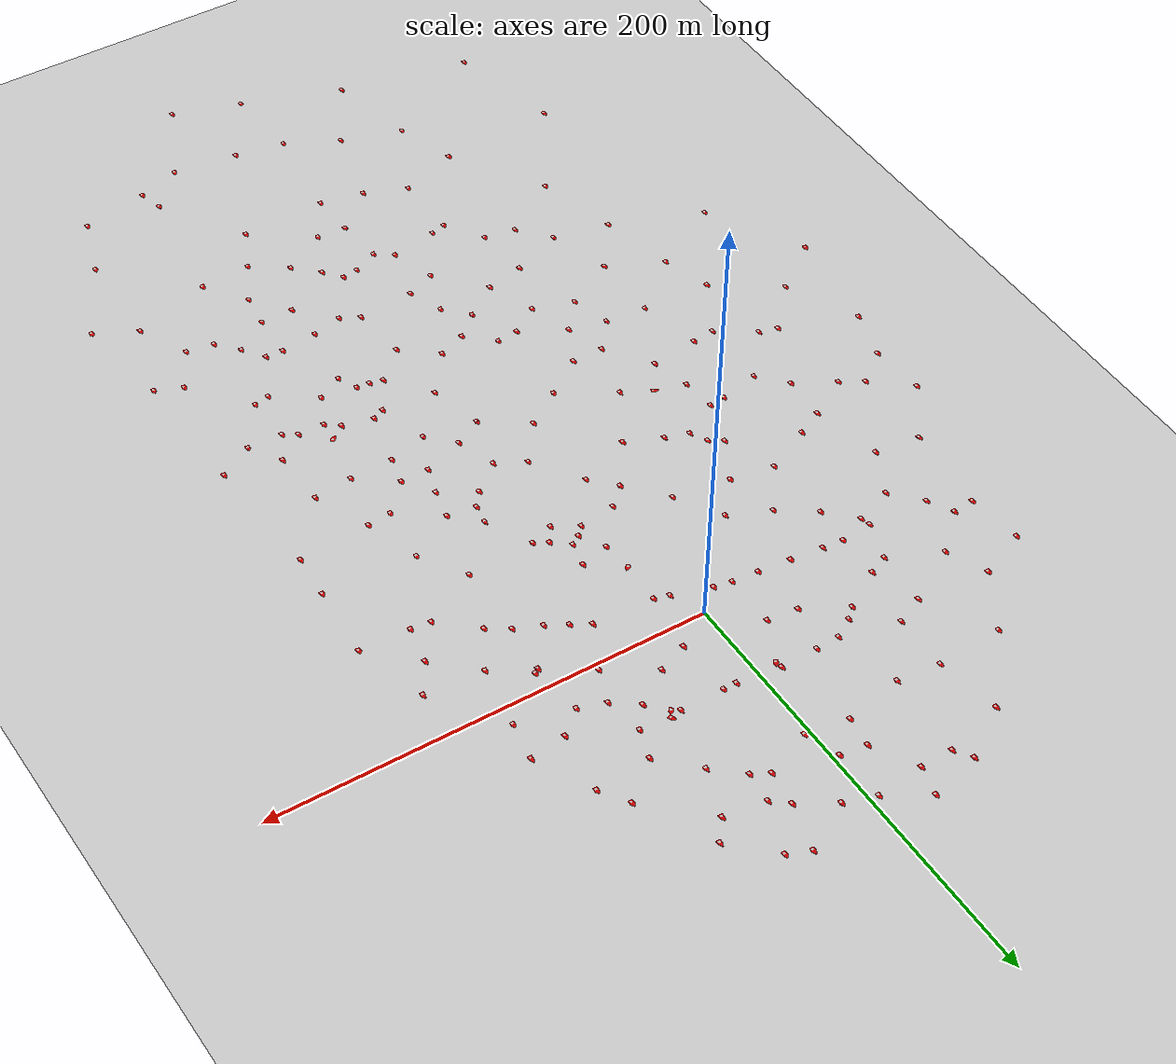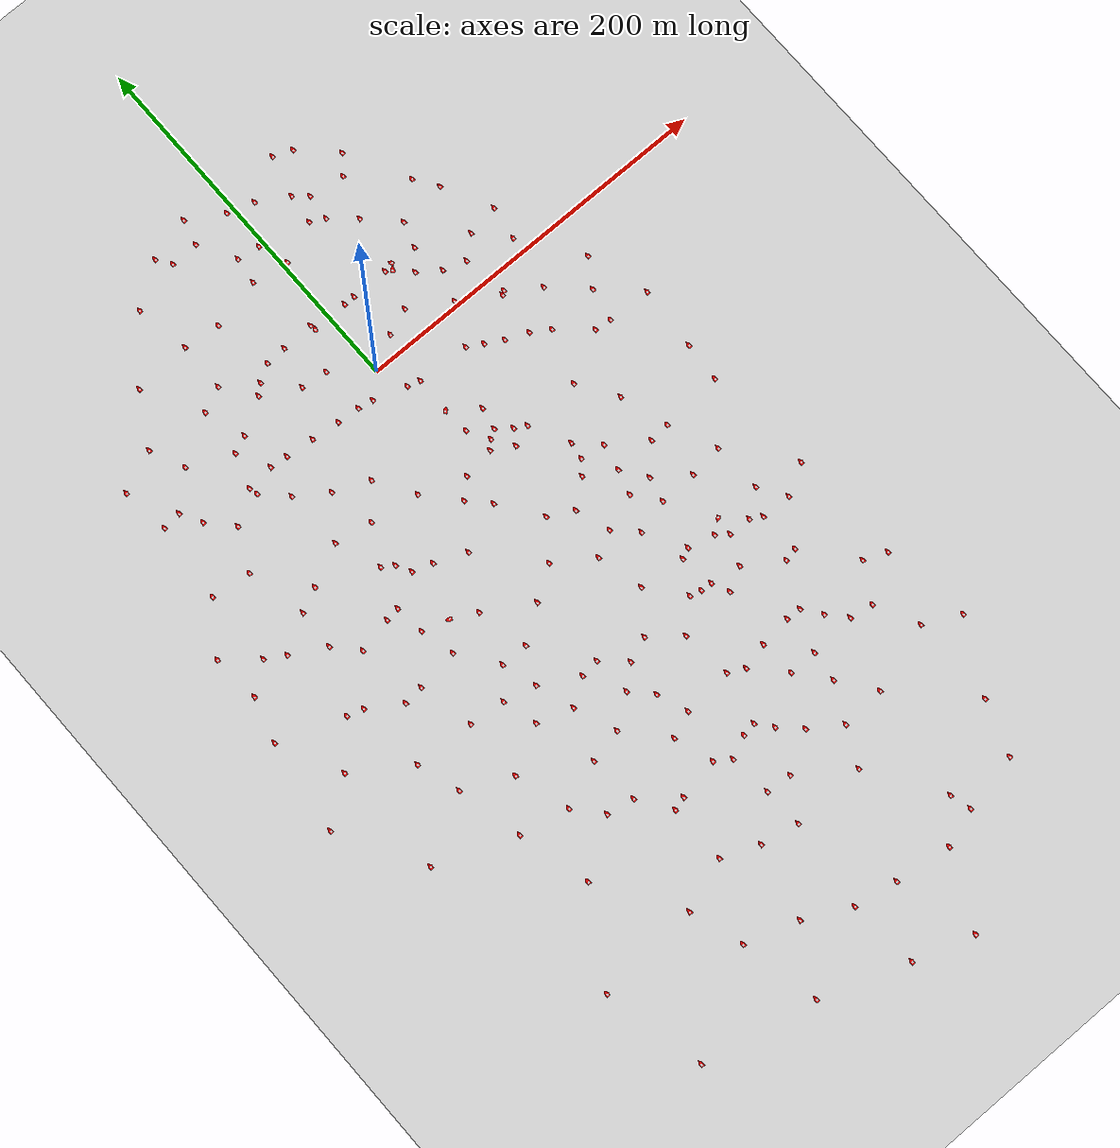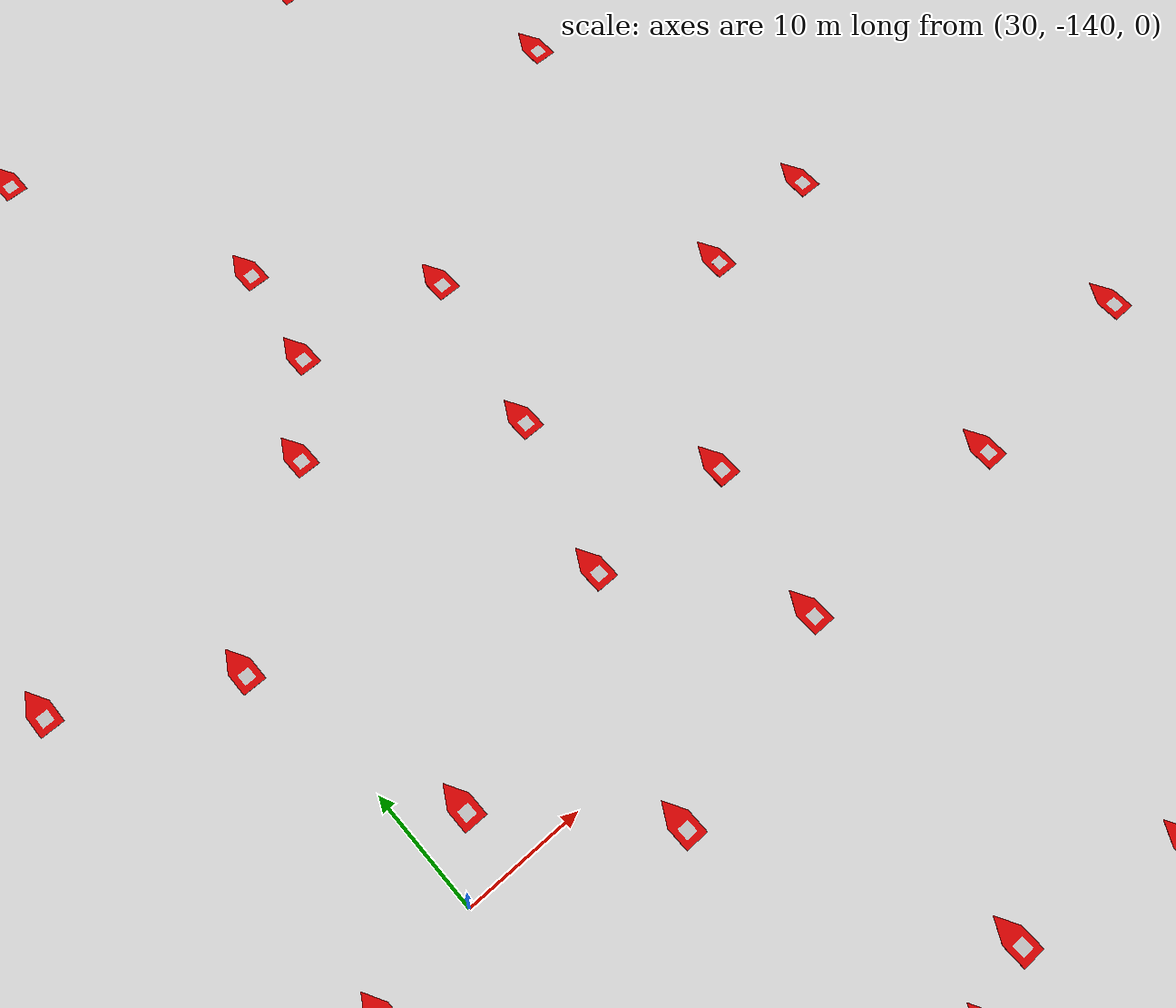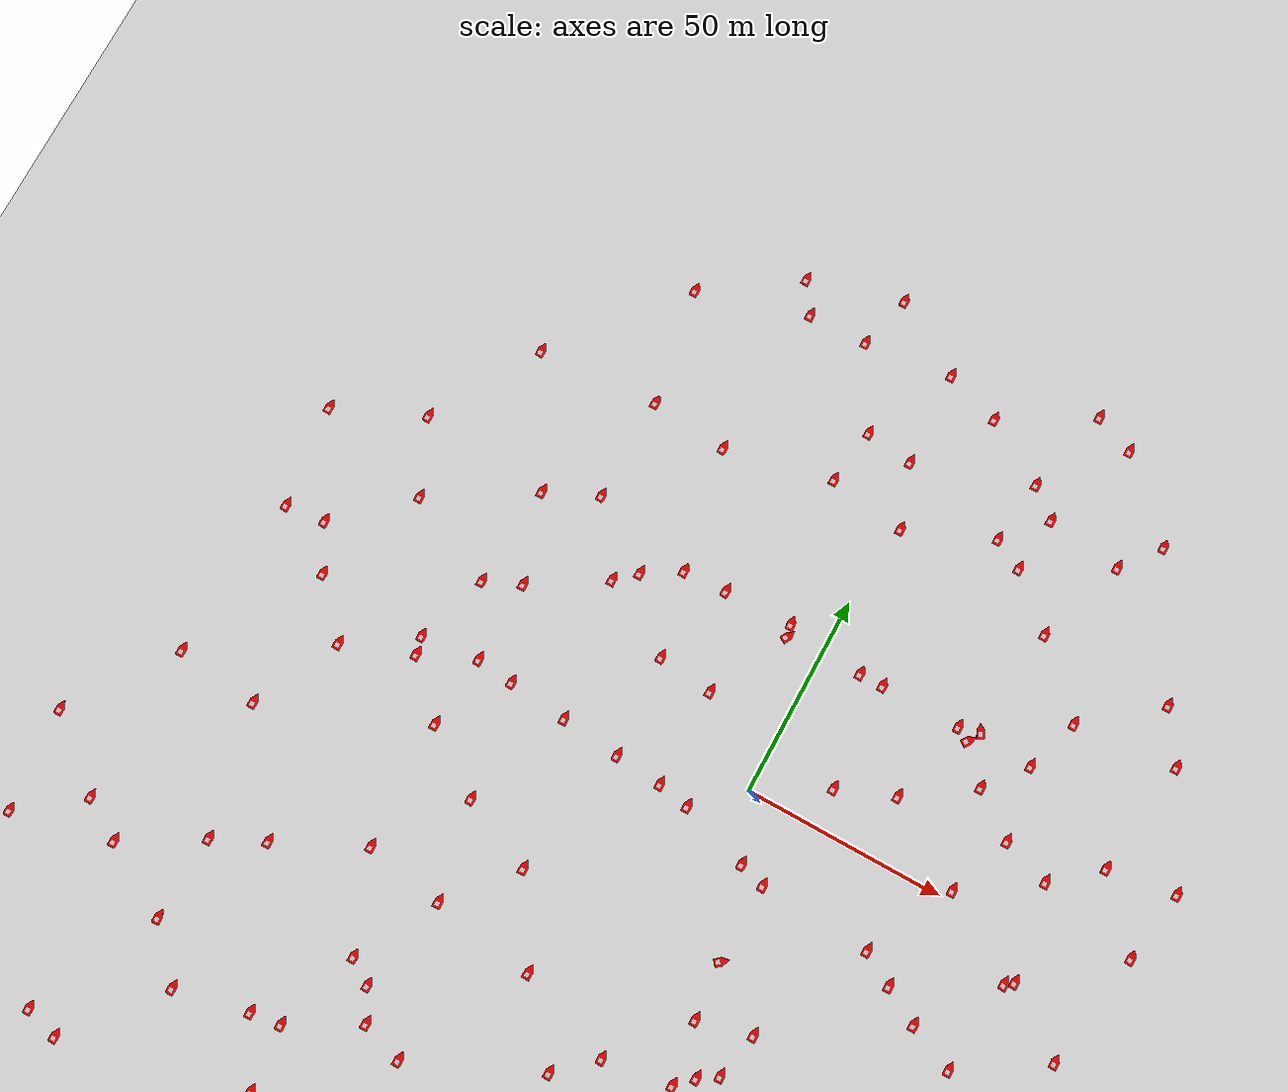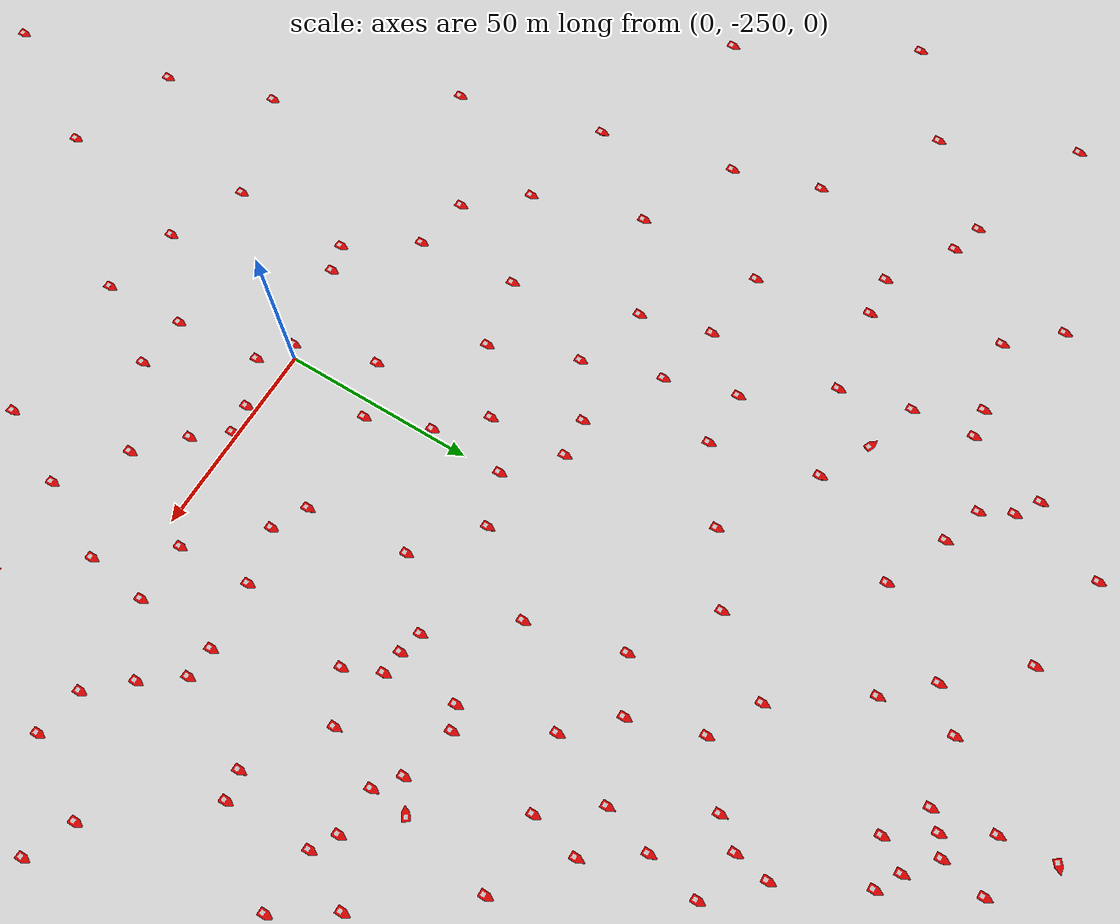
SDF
<sdf version="1.7">
 <world name="default">
  <physics type="ode">
   <ode>
    <solver>
     <type>quick</type>
     <iters>100</iters>
     <sor>1</sor>
     <use_dynamic_moi_rescaling>0</use_dynamic_moi_rescaling>
    </solver>
    <constraints>
     <cfm>0</cfm>
     <erp>0.2</erp>
     <contact_max_correcting_vel>0.1</contact_max_correcting_vel>
     <contact_surface_layer>0</contact_surface_layer>
    </constraints>
   </ode>
   <real_time_update_rate>400</real_time_update_rate>
   <max_step_size>0.0025</max_step_size>
   <real_time_factor>1</real_time_factor>
  </physics>
  <light name="sun" type="directional">
   <pose>0 0 10 0 -0 0</pose>
   <diffuse>0.8 0.8 0.8 1</diffuse>
   <specular>0.2 0.2 0.2 1</specular>
   <attenuation>
    <range>1000</range>
    <constant>0.9</constant>
    <linear>0.01</linear>
    <quadratic>0.001</quadratic>
   </attenuation>
   <direction>-0.5 0.1 -0.9</direction>
   <spot><inner_angle>0</inner_angle><outer_angle>0</outer_angle><falloff>0</falloff></spot>
  </light>
  <model name="ground_plane">
   <static>1</static>
   <link name="link">
    <collision name="collision">
     <geometry><plane><normal>0 0 1</normal><size>5000 5000</size></plane></geometry>
     <surface><friction><ode><mu>1</mu><mu2>1</mu2></ode></friction></surface>
    </collision>
    <visual name="runway">
     <pose>0 0 0.005 0 0 -1.5707</pose>
     <cast_shadows>0</cast_shadows>
     <geometry><plane><normal>0 0 1</normal><size>1829 45</size></plane></geometry>
     <material>
      <script><uri>file://media/materials/scripts/gazebo.material</uri><name>Gazebo/Runway</name></script>
     </material>
    </visual>
    <visual name="grass">
     <pose>0 0 -0.1 0 -0 0</pose>
     <cast_shadows>0</cast_shadows>
     <geometry><plane><normal>0 0 1</normal><size>5000 5000</size></plane></geometry>
     <material>
      <script><uri>file://media/materials/scripts/gazebo.material</uri><name>Gazebo/Grass</name></script>
     </material>
    </visual>
   </link>
  </model>
  <gravity>0 0 -9.8</gravity>
  <magnetic_field>6e-06 2.3e-05 -4.2e-05</magnetic_field>
  <atmosphere type="adiabatic"/>
  <scene><ambient>0.4 0.4 0.4 1</ambient><background>0.7 0.7 0.7 1</background><shadows>1</shadows></scene>
  <spherical_coordinates>
   <surface_model>EARTH_WGS84</surface_model>
   <latitude_deg>0</latitude_deg>
   <longitude_deg>0</longitude_deg>
   <elevation>0</elevation>
   <heading_deg>0</heading_deg>
  </spherical_coordinates>
  <model name="biao_12">
   <link name="link_0">
    <inertial>
     <mass>1</mass>
     <inertia>
      <ixx>0.166667</ixx>
      <ixy>0</ixy>
      <ixz>0</ixz>
      <iyy>0.166667</iyy>
      <iyz>0</iyz>
      <izz>0.166667</izz>
     </inertia>
    </inertial>
    <visual name="visual">
     <geometry>
      <mesh><uri>/home/lzc/lzc-code/src/simulation/models/biao/12/12.dae</uri><scale>1 1 1</scale></mesh>
     </geometry>
    </visual>
    <collision name="collision">
     <geometry>
      <mesh><uri>/home/lzc/lzc-code/src/simulation/models/biao/12/12.dae</uri><scale>1 1 1</scale></mesh>
     </geometry>
     <surface>
      <friction>
       <ode><mu>1</mu><mu2>1</mu2><fdir1>0 0 0</fdir1><slip1>0</slip1><slip2>0</slip2></ode>
       <torsional>
        <coefficient>1</coefficient>
        <patch_radius>0</patch_radius>
        <surface_radius>0</surface_radius>
        <use_patch_radius>1</use_patch_radius>
        <ode><slip>0</slip></ode>
       </torsional>
      </friction>
      <bounce><restitution_coefficient>0</restitution_coefficient><threshold>1e+06</threshold></bounce>
      <contact>
       <collide_without_contact>0</collide_without_contact>
       <collide_without_contact_bitmask>1</collide_without_contact_bitmask>
       <collide_bitmask>1</collide_bitmask>
       <ode>
        <soft_cfm>0</soft_cfm>
        <soft_erp>0.2</soft_erp>
        <kp>1e+13</kp>
        <kd>1</kd>
        <max_vel>0.01</max_vel>
        <min_depth>0</min_depth>
       </ode>
       <bullet>
        <split_impulse>1</split_impulse>
        <split_impulse_penetration_threshold>-0.01</split_impulse_penetration_threshold>
        <soft_cfm>0</soft_cfm>
        <soft_erp>0.2</soft_erp>
        <kp>1e+13</kp>
        <kd>1</kd>
       </bullet>
      </contact>
     </surface>
    </collision>
   </link>
   <static>0</static>
   <pose>12.1405 -37.5522 0.010973 -2.7e-05 -2.7e-05 -0.861328</pose>
  </model>
  <model name="biao_34">
   <link name="link_0">
    <inertial>
     <mass>1</mass>
     <inertia>
      <ixx>0.166667</ixx>
      <ixy>0</ixy>
      <ixz>0</ixz>
      <iyy>0.166667</iyy>
      <iyz>0</iyz>
      <izz>0.166667</izz>
     </inertia>
    </inertial>
    <visual name="visual">
     <geometry>
      <mesh><uri>/home/lzc/lzc-code/src/simulation/models/biao/34/34.dae</uri><scale>1 1 1</scale></mesh>
     </geometry>
    </visual>
    <collision name="collision">
     <geometry>
      <mesh><uri>/home/lzc/lzc-code/src/simulation/models/biao/34/34.dae</uri><scale>1 1 1</scale></mesh>
     </geometry>
     <surface>
      <friction>
       <ode><mu>1</mu><mu2>1</mu2><fdir1>0 0 0</fdir1><slip1>0</slip1><slip2>0</slip2></ode>
       <torsional>
        <coefficient>1</coefficient>
        <patch_radius>0</patch_radius>
        <surface_radius>0</surface_radius>
        <use_patch_radius>1</use_patch_radius>
        <ode><slip>0</slip></ode>
       </torsional>
      </friction>
      <bounce><restitution_coefficient>0</restitution_coefficient><threshold>1e+06</threshold></bounce>
      <contact>
       <collide_without_contact>0</collide_without_contact>
       <collide_without_contact_bitmask>1</collide_without_contact_bitmask>
       <collide_bitmask>1</collide_bitmask>
       <ode>
        <soft_cfm>0</soft_cfm>
        <soft_erp>0.2</soft_erp>
        <kp>1e+13</kp>
        <kd>1</kd>
        <max_vel>0.01</max_vel>
        <min_depth>0</min_depth>
       </ode>
       <bullet>
        <split_impulse>1</split_impulse>
        <split_impulse_penetration_threshold>-0.01</split_impulse_penetration_threshold>
        <soft_cfm>0</soft_cfm>
        <soft_erp>0.2</soft_erp>
        <kp>1e+13</kp>
        <kd>1</kd>
       </bullet>
      </contact>
     </surface>
    </collision>
   </link>
   <static>0</static>
   <pose>-53.1888 -117.975 0.010964 0 -0 1.14837</pose>
  </model>
  <model name="biao_56">
   <link name="link_0">
    <inertial>
     <mass>1</mass>
     <inertia>
      <ixx>0.166667</ixx>
      <ixy>0</ixy>
      <ixz>0</ixz>
      <iyy>0.166667</iyy>
      <iyz>0</iyz>
      <izz>0.166667</izz>
     </inertia>
    </inertial>
    <visual name="visual">
     <geometry>
      <mesh><uri>/home/lzc/lzc-code/src/simulation/models/biao/56/56.dae</uri><scale>1 1 1</scale></mesh>
     </geometry>
    </visual>
    <collision name="collision">
     <geometry>
      <mesh><uri>/home/lzc/lzc-code/src/simulation/models/biao/56/56.dae</uri><scale>1 1 1</scale></mesh>
     </geometry>
     <surface>
      <friction>
       <ode><mu>1</mu><mu2>1</mu2><fdir1>0 0 0</fdir1><slip1>0</slip1><slip2>0</slip2></ode>
       <torsional>
        <coefficient>1</coefficient>
        <patch_radius>0</patch_radius>
        <surface_radius>0</surface_radius>
        <use_patch_radius>1</use_patch_radius>
        <ode><slip>0</slip></ode>
       </torsional>
      </friction>
      <bounce><restitution_coefficient>0</restitution_coefficient><threshold>1e+06</threshold></bounce>
      <contact>
       <collide_without_contact>0</collide_without_contact>
       <collide_without_contact_bitmask>1</collide_without_contact_bitmask>
       <collide_bitmask>1</collide_bitmask>
       <ode>
        <soft_cfm>0</soft_cfm>
        <soft_erp>0.2</soft_erp>
        <kp>1e+13</kp>
        <kd>1</kd>
        <max_vel>0.01</max_vel>
        <min_depth>0</min_depth>
       </ode>
       <bullet>
        <split_impulse>1</split_impulse>
        <split_impulse_penetration_threshold>-0.01</split_impulse_penetration_threshold>
        <soft_cfm>0</soft_cfm>
        <soft_erp>0.2</soft_erp>
        <kp>1e+13</kp>
        <kd>1</kd>
       </bullet>
      </contact>
     </surface>
    </collision>
   </link>
   <static>0</static>
   <pose>78.1749 -164.061 0.010973 -2.7e-05 -2.7e-05 2.24268</pose>
  </model>
  <model name="biao_12_0">
   <link name="link_0">
    <inertial>
     <mass>1</mass>
     <inertia>
      <ixx>0.166667</ixx>
      <ixy>0</ixy>
      <ixz>0</ixz>
      <iyy>0.166667</iyy>
      <iyz>0</iyz>
      <izz>0.166667</izz>
     </inertia>
    </inertial>
    <visual name="visual">
     <geometry>
      <mesh><uri>/home/lzc/lzc-code/src/simulation/models/biao/12/12.dae</uri><scale>1 1 1</scale></mesh>
     </geometry>
    </visual>
    <collision name="collision">
     <geometry>
      <mesh><uri>/home/lzc/lzc-code/src/simulation/models/biao/12/12.dae</uri><scale>1 1 1</scale></mesh>
     </geometry>
     <surface>
      <friction>
       <ode><mu>1</mu><mu2>1</mu2><fdir1>0 0 0</fdir1><slip1>0</slip1><slip2>0</slip2></ode>
       <torsional>
        <coefficient>1</coefficient>
        <patch_radius>0</patch_radius>
        <surface_radius>0</surface_radius>
        <use_patch_radius>1</use_patch_radius>
        <ode><slip>0</slip></ode>
       </torsional>
      </friction>
      <bounce><restitution_coefficient>0</restitution_coefficient><threshold>1e+06</threshold></bounce>
      <contact>
       <collide_without_contact>0</collide_without_contact>
       <collide_without_contact_bitmask>1</collide_without_contact_bitmask>
       <collide_bitmask>1</collide_bitmask>
       <ode>
        <soft_cfm>0</soft_cfm>
        <soft_erp>0.2</soft_erp>
        <kp>1e+13</kp>
        <kd>1</kd>
        <max_vel>0.01</max_vel>
        <min_depth>0</min_depth>
       </ode>
       <bullet>
        <split_impulse>1</split_impulse>
        <split_impulse_penetration_threshold>-0.01</split_impulse_penetration_threshold>
        <soft_cfm>0</soft_cfm>
        <soft_erp>0.2</soft_erp>
        <kp>1e+13</kp>
        <kd>1</kd>
       </bullet>
      </contact>
     </surface>
    </collision>
   </link>
   <static>0</static>
   <pose>13.6383 -51.8225 0.010961 0 -7.7e-05 0</pose>
  </model>
  <model name="biao_12_0_clone">
   <link name="link_0">
    <inertial>
     <mass>1</mass>
     <inertia>
      <ixx>0.166667</ixx>
      <ixy>0</ixy>
      <ixz>0</ixz>
      <iyy>0.166667</iyy>
      <iyz>0</iyz>
      <izz>0.166667</izz>
     </inertia>
    </inertial>
    <visual name="visual">
     <geometry>
      <mesh><uri>/home/lzc/lzc-code/src/simulation/models/biao/12/12.dae</uri><scale>1 1 1</scale></mesh>
     </geometry>
    </visual>
    <collision name="collision">
     <geometry>
      <mesh><uri>/home/lzc/lzc-code/src/simulation/models/biao/12/12.dae</uri><scale>1 1 1</scale></mesh>
     </geometry>
     <surface>
      <friction>
       <ode><mu>1</mu><mu2>1</mu2><fdir1>0 0 0</fdir1><slip1>0</slip1><slip2>0</slip2></ode>
       <torsional>
        <coefficient>1</coefficient>
        <patch_radius>0</patch_radius>
        <surface_radius>0</surface_radius>
        <use_patch_radius>1</use_patch_radius>
        <ode><slip>0</slip></ode>
       </torsional>
      </friction>
      <bounce><restitution_coefficient>0</restitution_coefficient><threshold>1e+06</threshold></bounce>
      <contact>
       <collide_without_contact>0</collide_without_contact>
       <collide_without_contact_bitmask>1</collide_without_contact_bitmask>
       <collide_bitmask>1</collide_bitmask>
       <ode>
        <soft_cfm>0</soft_cfm>
        <soft_erp>0.2</soft_erp>
        <kp>1e+13</kp>
        <kd>1</kd>
        <max_vel>0.01</max_vel>
        <min_depth>0</min_depth>
       </ode>
       <bullet>
        <split_impulse>1</split_impulse>
        <split_impulse_penetration_threshold>-0.01</split_impulse_penetration_threshold>
        <soft_cfm>0</soft_cfm>
        <soft_erp>0.2</soft_erp>
        <kp>1e+13</kp>
        <kd>1</kd>
       </bullet>
      </contact>
     </surface>
    </collision>
   </link>
   <static>0</static>
   <pose>27 -48.4658 0.010973 -2.7e-05 -2.7e-05 -1e-06</pose>
  </model>
  <model name="biao_12_0_clone_0">
   <link name="link_0">
    <inertial>
     <mass>1</mass>
     <inertia>
      <ixx>0.166667</ixx>
      <ixy>0</ixy>
      <ixz>0</ixz>
      <iyy>0.166667</iyy>
      <iyz>0</iyz>
      <izz>0.166667</izz>
     </inertia>
    </inertial>
    <visual name="visual">
     <geometry>
      <mesh><uri>/home/lzc/lzc-code/src/simulation/models/biao/12/12.dae</uri><scale>1 1 1</scale></mesh>
     </geometry>
    </visual>
    <collision name="collision">
     <geometry>
      <mesh><uri>/home/lzc/lzc-code/src/simulation/models/biao/12/12.dae</uri><scale>1 1 1</scale></mesh>
     </geometry>
     <surface>
      <friction>
       <ode><mu>1</mu><mu2>1</mu2><fdir1>0 0 0</fdir1><slip1>0</slip1><slip2>0</slip2></ode>
       <torsional>
        <coefficient>1</coefficient>
        <patch_radius>0</patch_radius>
        <surface_radius>0</surface_radius>
        <use_patch_radius>1</use_patch_radius>
        <ode><slip>0</slip></ode>
       </torsional>
      </friction>
      <bounce><restitution_coefficient>0</restitution_coefficient><threshold>1e+06</threshold></bounce>
      <contact>
       <collide_without_contact>0</collide_without_contact>
       <collide_without_contact_bitmask>1</collide_without_contact_bitmask>
       <collide_bitmask>1</collide_bitmask>
       <ode>
        <soft_cfm>0</soft_cfm>
        <soft_erp>0.2</soft_erp>
        <kp>1e+13</kp>
        <kd>1</kd>
        <max_vel>0.01</max_vel>
        <min_depth>0</min_depth>
       </ode>
       <bullet>
        <split_impulse>1</split_impulse>
        <split_impulse_penetration_threshold>-0.01</split_impulse_penetration_threshold>
        <soft_cfm>0</soft_cfm>
        <soft_erp>0.2</soft_erp>
        <kp>1e+13</kp>
        <kd>1</kd>
       </bullet>
      </contact>
     </surface>
    </collision>
   </link>
   <static>0</static>
   <pose>38 -69.4252 0.010973 -2.7e-05 -2.7e-05 -1e-06</pose>
  </model>
  <model name="biao_12_0_clone_1">
   <link name="link_0">
    <inertial>
     <mass>1</mass>
     <inertia>
      <ixx>0.166667</ixx>
      <ixy>0</ixy>
      <ixz>0</ixz>
      <iyy>0.166667</iyy>
      <iyz>0</iyz>
      <izz>0.166667</izz>
     </inertia>
    </inertial>
    <visual name="visual">
     <geometry>
      <mesh><uri>/home/lzc/lzc-code/src/simulation/models/biao/12/12.dae</uri><scale>1 1 1</scale></mesh>
     </geometry>
    </visual>
    <collision name="collision">
     <geometry>
      <mesh><uri>/home/lzc/lzc-code/src/simulation/models/biao/12/12.dae</uri><scale>1 1 1</scale></mesh>
     </geometry>
     <surface>
      <friction>
       <ode><mu>1</mu><mu2>1</mu2><fdir1>0 0 0</fdir1><slip1>0</slip1><slip2>0</slip2></ode>
       <torsional>
        <coefficient>1</coefficient>
        <patch_radius>0</patch_radius>
        <surface_radius>0</surface_radius>
        <use_patch_radius>1</use_patch_radius>
        <ode><slip>0</slip></ode>
       </torsional>
      </friction>
      <bounce><restitution_coefficient>0</restitution_coefficient><threshold>1e+06</threshold></bounce>
      <contact>
       <collide_without_contact>0</collide_without_contact>
       <collide_without_contact_bitmask>1</collide_without_contact_bitmask>
       <collide_bitmask>1</collide_bitmask>
       <ode>
        <soft_cfm>0</soft_cfm>
        <soft_erp>0.2</soft_erp>
        <kp>1e+13</kp>
        <kd>1</kd>
        <max_vel>0.01</max_vel>
        <min_depth>0</min_depth>
       </ode>
       <bullet>
        <split_impulse>1</split_impulse>
        <split_impulse_penetration_threshold>-0.01</split_impulse_penetration_threshold>
        <soft_cfm>0</soft_cfm>
        <soft_erp>0.2</soft_erp>
        <kp>1e+13</kp>
        <kd>1</kd>
       </bullet>
      </contact>
     </surface>
    </collision>
   </link>
   <static>0</static>
   <pose>32 -66 0.010964 0 0 -1e-06</pose>
  </model>
  <model name="biao_12_0_clone_2">
   <link name="link_0">
    <inertial>
     <mass>1</mass>
     <inertia>
      <ixx>0.166667</ixx>
      <ixy>0</ixy>
      <ixz>0</ixz>
      <iyy>0.166667</iyy>
      <iyz>0</iyz>
      <izz>0.166667</izz>
     </inertia>
    </inertial>
    <visual name="visual">
     <geometry>
      <mesh><uri>/home/lzc/lzc-code/src/simulation/models/biao/12/12.dae</uri><scale>1 1 1</scale></mesh>
     </geometry>
    </visual>
    <collision name="collision">
     <geometry>
      <mesh><uri>/home/lzc/lzc-code/src/simulation/models/biao/12/12.dae</uri><scale>1 1 1</scale></mesh>
     </geometry>
     <surface>
      <friction>
       <ode><mu>1</mu><mu2>1</mu2><fdir1>0 0 0</fdir1><slip1>0</slip1><slip2>0</slip2></ode>
       <torsional>
        <coefficient>1</coefficient>
        <patch_radius>0</patch_radius>
        <surface_radius>0</surface_radius>
        <use_patch_radius>1</use_patch_radius>
        <ode><slip>0</slip></ode>
       </torsional>
      </friction>
      <bounce><restitution_coefficient>0</restitution_coefficient><threshold>1e+06</threshold></bounce>
      <contact>
       <collide_without_contact>0</collide_without_contact>
       <collide_without_contact_bitmask>1</collide_without_contact_bitmask>
       <collide_bitmask>1</collide_bitmask>
       <ode>
        <soft_cfm>0</soft_cfm>
        <soft_erp>0.2</soft_erp>
        <kp>1e+13</kp>
        <kd>1</kd>
        <max_vel>0.01</max_vel>
        <min_depth>0</min_depth>
       </ode>
       <bullet>
        <split_impulse>1</split_impulse>
        <split_impulse_penetration_threshold>-0.01</split_impulse_penetration_threshold>
        <soft_cfm>0</soft_cfm>
        <soft_erp>0.2</soft_erp>
        <kp>1e+13</kp>
        <kd>1</kd>
       </bullet>
      </contact>
     </surface>
    </collision>
   </link>
   <static>0</static>
   <pose>24.5835 -60 0.010973 -2.7e-05 -2.7e-05 -1e-06</pose>
  </model>
  <model name="biao_12_0_clone_3">
   <link name="link_0">
    <inertial>
     <mass>1</mass>
     <inertia>
      <ixx>0.166667</ixx>
      <ixy>0</ixy>
      <ixz>0</ixz>
      <iyy>0.166667</iyy>
      <iyz>0</iyz>
      <izz>0.166667</izz>
     </inertia>
    </inertial>
    <visual name="visual">
     <geometry>
      <mesh><uri>/home/lzc/lzc-code/src/simulation/models/biao/12/12.dae</uri><scale>1 1 1</scale></mesh>
     </geometry>
    </visual>
    <collision name="collision">
     <geometry>
      <mesh><uri>/home/lzc/lzc-code/src/simulation/models/biao/12/12.dae</uri><scale>1 1 1</scale></mesh>
     </geometry>
     <surface>
      <friction>
       <ode><mu>1</mu><mu2>1</mu2><fdir1>0 0 0</fdir1><slip1>0</slip1><slip2>0</slip2></ode>
       <torsional>
        <coefficient>1</coefficient>
        <patch_radius>0</patch_radius>
        <surface_radius>0</surface_radius>
        <use_patch_radius>1</use_patch_radius>
        <ode><slip>0</slip></ode>
       </torsional>
      </friction>
      <bounce><restitution_coefficient>0</restitution_coefficient><threshold>1e+06</threshold></bounce>
      <contact>
       <collide_without_contact>0</collide_without_contact>
       <collide_without_contact_bitmask>1</collide_without_contact_bitmask>
       <collide_bitmask>1</collide_bitmask>
       <ode>
        <soft_cfm>0</soft_cfm>
        <soft_erp>0.2</soft_erp>
        <kp>1e+13</kp>
        <kd>1</kd>
        <max_vel>0.01</max_vel>
        <min_depth>0</min_depth>
       </ode>
       <bullet>
        <split_impulse>1</split_impulse>
        <split_impulse_penetration_threshold>-0.01</split_impulse_penetration_threshold>
        <soft_cfm>0</soft_cfm>
        <soft_erp>0.2</soft_erp>
        <kp>1e+13</kp>
        <kd>1</kd>
       </bullet>
      </contact>
     </surface>
    </collision>
   </link>
   <static>0</static>
   <pose>20 -63 0.010973 -2.7e-05 -2.7e-05 -1e-06</pose>
  </model>
  <model name="biao_12_0_clone_4">
   <link name="link_0">
    <inertial>
     <mass>1</mass>
     <inertia>
      <ixx>0.166667</ixx>
      <ixy>0</ixy>
      <ixz>0</ixz>
      <iyy>0.166667</iyy>
      <iyz>0</iyz>
      <izz>0.166667</izz>
     </inertia>
    </inertial>
    <visual name="visual">
     <geometry>
      <mesh><uri>/home/lzc/lzc-code/src/simulation/models/biao/12/12.dae</uri><scale>1 1 1</scale></mesh>
     </geometry>
    </visual>
    <collision name="collision">
     <geometry>
      <mesh><uri>/home/lzc/lzc-code/src/simulation/models/biao/12/12.dae</uri><scale>1 1 1</scale></mesh>
     </geometry>
     <surface>
      <friction>
       <ode><mu>1</mu><mu2>1</mu2><fdir1>0 0 0</fdir1><slip1>0</slip1><slip2>0</slip2></ode>
       <torsional>
        <coefficient>1</coefficient>
        <patch_radius>0</patch_radius>
        <surface_radius>0</surface_radius>
        <use_patch_radius>1</use_patch_radius>
        <ode><slip>0</slip></ode>
       </torsional>
      </friction>
      <bounce><restitution_coefficient>0</restitution_coefficient><threshold>1e+06</threshold></bounce>
      <contact>
       <collide_without_contact>0</collide_without_contact>
       <collide_without_contact_bitmask>1</collide_without_contact_bitmask>
       <collide_bitmask>1</collide_bitmask>
       <ode>
        <soft_cfm>0</soft_cfm>
        <soft_erp>0.2</soft_erp>
        <kp>1e+13</kp>
        <kd>1</kd>
        <max_vel>0.01</max_vel>
        <min_depth>0</min_depth>
       </ode>
       <bullet>
        <split_impulse>1</split_impulse>
        <split_impulse_penetration_threshold>-0.01</split_impulse_penetration_threshold>
        <soft_cfm>0</soft_cfm>
        <soft_erp>0.2</soft_erp>
        <kp>1e+13</kp>
        <kd>1</kd>
       </bullet>
      </contact>
     </surface>
    </collision>
   </link>
   <static>0</static>
   <pose>16 -67 0.010964 0 0 -1e-06</pose>
  </model>
  <model name="biao_12_0_clone_5">
   <link name="link_0">
    <inertial>
     <mass>1</mass>
     <inertia>
      <ixx>0.166667</ixx>
      <ixy>0</ixy>
      <ixz>0</ixz>
      <iyy>0.166667</iyy>
      <iyz>0</iyz>
      <izz>0.166667</izz>
     </inertia>
    </inertial>
    <visual name="visual">
     <geometry>
      <mesh><uri>/home/lzc/lzc-code/src/simulation/models/biao/12/12.dae</uri><scale>1 1 1</scale></mesh>
     </geometry>
    </visual>
    <collision name="collision">
     <geometry>
      <mesh><uri>/home/lzc/lzc-code/src/simulation/models/biao/12/12.dae</uri><scale>1 1 1</scale></mesh>
     </geometry>
     <surface>
      <friction>
       <ode><mu>1</mu><mu2>1</mu2><fdir1>0 0 0</fdir1><slip1>0</slip1><slip2>0</slip2></ode>
       <torsional>
        <coefficient>1</coefficient>
        <patch_radius>0</patch_radius>
        <surface_radius>0</surface_radius>
        <use_patch_radius>1</use_patch_radius>
        <ode><slip>0</slip></ode>
       </torsional>
      </friction>
      <bounce><restitution_coefficient>0</restitution_coefficient><threshold>1e+06</threshold></bounce>
      <contact>
       <collide_without_contact>0</collide_without_contact>
       <collide_without_contact_bitmask>1</collide_without_contact_bitmask>
       <collide_bitmask>1</collide_bitmask>
       <ode>
        <soft_cfm>0</soft_cfm>
        <soft_erp>0.2</soft_erp>
        <kp>1e+13</kp>
        <kd>1</kd>
        <max_vel>0.01</max_vel>
        <min_depth>0</min_depth>
       </ode>
       <bullet>
        <split_impulse>1</split_impulse>
        <split_impulse_penetration_threshold>-0.01</split_impulse_penetration_threshold>
        <soft_cfm>0</soft_cfm>
        <soft_erp>0.2</soft_erp>
        <kp>1e+13</kp>
        <kd>1</kd>
       </bullet>
      </contact>
     </surface>
    </collision>
   </link>
   <static>0</static>
   <pose>27 -73.445 0.010973 -2.7e-05 -2.7e-05 -1e-06</pose>
  </model>
  <model name="biao_12_0_clone_6">
   <link name="link_0">
    <inertial>
     <mass>1</mass>
     <inertia>
      <ixx>0.166667</ixx>
      <ixy>0</ixy>
      <ixz>0</ixz>
      <iyy>0.166667</iyy>
      <iyz>0</iyz>
      <izz>0.166667</izz>
     </inertia>
    </inertial>
    <visual name="visual">
     <geometry>
      <mesh><uri>/home/lzc/lzc-code/src/simulation/models/biao/12/12.dae</uri><scale>1 1 1</scale></mesh>
     </geometry>
    </visual>
    <collision name="collision">
     <geometry>
      <mesh><uri>/home/lzc/lzc-code/src/simulation/models/biao/12/12.dae</uri><scale>1 1 1</scale></mesh>
     </geometry>
     <surface>
      <friction>
       <ode><mu>1</mu><mu2>1</mu2><fdir1>0 0 0</fdir1><slip1>0</slip1><slip2>0</slip2></ode>
       <torsional>
        <coefficient>1</coefficient>
        <patch_radius>0</patch_radius>
        <surface_radius>0</surface_radius>
        <use_patch_radius>1</use_patch_radius>
        <ode><slip>0</slip></ode>
       </torsional>
      </friction>
      <bounce><restitution_coefficient>0</restitution_coefficient><threshold>1e+06</threshold></bounce>
      <contact>
       <collide_without_contact>0</collide_without_contact>
       <collide_without_contact_bitmask>1</collide_without_contact_bitmask>
       <collide_bitmask>1</collide_bitmask>
       <ode>
        <soft_cfm>0</soft_cfm>
        <soft_erp>0.2</soft_erp>
        <kp>1e+13</kp>
        <kd>1</kd>
        <max_vel>0.01</max_vel>
        <min_depth>0</min_depth>
       </ode>
       <bullet>
        <split_impulse>1</split_impulse>
        <split_impulse_penetration_threshold>-0.01</split_impulse_penetration_threshold>
        <soft_cfm>0</soft_cfm>
        <soft_erp>0.2</soft_erp>
        <kp>1e+13</kp>
        <kd>1</kd>
       </bullet>
      </contact>
     </surface>
    </collision>
   </link>
   <static>0</static>
   <pose>48.4679 -90 0.010973 -2.7e-05 -2.7e-05 -1e-06</pose>
  </model>
  <model name="biao_12_0_clone_7">
   <link name="link_0">
    <inertial>
     <mass>1</mass>
     <inertia>
      <ixx>0.166667</ixx>
      <ixy>0</ixy>
      <ixz>0</ixz>
      <iyy>0.166667</iyy>
      <iyz>0</iyz>
      <izz>0.166667</izz>
     </inertia>
    </inertial>
    <visual name="visual">
     <geometry>
      <mesh><uri>/home/lzc/lzc-code/src/simulation/models/biao/12/12.dae</uri><scale>1 1 1</scale></mesh>
     </geometry>
    </visual>
    <collision name="collision">
     <geometry>
      <mesh><uri>/home/lzc/lzc-code/src/simulation/models/biao/12/12.dae</uri><scale>1 1 1</scale></mesh>
     </geometry>
     <surface>
      <friction>
       <ode><mu>1</mu><mu2>1</mu2><fdir1>0 0 0</fdir1><slip1>0</slip1><slip2>0</slip2></ode>
       <torsional>
        <coefficient>1</coefficient>
        <patch_radius>0</patch_radius>
        <surface_radius>0</surface_radius>
        <use_patch_radius>1</use_patch_radius>
        <ode><slip>0</slip></ode>
       </torsional>
      </friction>
      <bounce><restitution_coefficient>0</restitution_coefficient><threshold>1e+06</threshold></bounce>
      <contact>
       <collide_without_contact>0</collide_without_contact>
       <collide_without_contact_bitmask>1</collide_without_contact_bitmask>
       <collide_bitmask>1</collide_bitmask>
       <ode>
        <soft_cfm>0</soft_cfm>
        <soft_erp>0.2</soft_erp>
        <kp>1e+13</kp>
        <kd>1</kd>
        <max_vel>0.01</max_vel>
        <min_depth>0</min_depth>
       </ode>
       <bullet>
        <split_impulse>1</split_impulse>
        <split_impulse_penetration_threshold>-0.01</split_impulse_penetration_threshold>
        <soft_cfm>0</soft_cfm>
        <soft_erp>0.2</soft_erp>
        <kp>1e+13</kp>
        <kd>1</kd>
       </bullet>
      </contact>
     </surface>
    </collision>
   </link>
   <static>0</static>
   <pose>60 -101 0.010964 0 0 -1e-06</pose>
  </model>
  <model name="biao_12_0_clone_8">
   <link name="link_0">
    <inertial>
     <mass>1</mass>
     <inertia>
      <ixx>0.166667</ixx>
      <ixy>0</ixy>
      <ixz>0</ixz>
      <iyy>0.166667</iyy>
      <iyz>0</iyz>
      <izz>0.166667</izz>
     </inertia>
    </inertial>
    <visual name="visual">
     <geometry>
      <mesh><uri>/home/lzc/lzc-code/src/simulation/models/biao/12/12.dae</uri><scale>1 1 1</scale></mesh>
     </geometry>
    </visual>
    <collision name="collision">
     <geometry>
      <mesh><uri>/home/lzc/lzc-code/src/simulation/models/biao/12/12.dae</uri><scale>1 1 1</scale></mesh>
     </geometry>
     <surface>
      <friction>
       <ode><mu>1</mu><mu2>1</mu2><fdir1>0 0 0</fdir1><slip1>0</slip1><slip2>0</slip2></ode>
       <torsional>
        <coefficient>1</coefficient>
        <patch_radius>0</patch_radius>
        <surface_radius>0</surface_radius>
        <use_patch_radius>1</use_patch_radius>
        <ode><slip>0</slip></ode>
       </torsional>
      </friction>
      <bounce><restitution_coefficient>0</restitution_coefficient><threshold>1e+06</threshold></bounce>
      <contact>
       <collide_without_contact>0</collide_without_contact>
       <collide_without_contact_bitmask>1</collide_without_contact_bitmask>
       <collide_bitmask>1</collide_bitmask>
       <ode>
        <soft_cfm>0</soft_cfm>
        <soft_erp>0.2</soft_erp>
        <kp>1e+13</kp>
        <kd>1</kd>
        <max_vel>0.01</max_vel>
        <min_depth>0</min_depth>
       </ode>
       <bullet>
        <split_impulse>1</split_impulse>
        <split_impulse_penetration_threshold>-0.01</split_impulse_penetration_threshold>
        <soft_cfm>0</soft_cfm>
        <soft_erp>0.2</soft_erp>
        <kp>1e+13</kp>
        <kd>1</kd>
       </bullet>
      </contact>
     </surface>
    </collision>
   </link>
   <static>0</static>
   <pose>79 -114.429 0.010973 -2.7e-05 -2.7e-05 -1e-06</pose>
  </model>
  <model name="biao_12_0_clone_9">
   <link name="link_0">
    <inertial>
     <mass>1</mass>
     <inertia>
      <ixx>0.166667</ixx>
      <ixy>0</ixy>
      <ixz>0</ixz>
      <iyy>0.166667</iyy>
      <iyz>0</iyz>
      <izz>0.166667</izz>
     </inertia>
    </inertial>
    <visual name="visual">
     <geometry>
      <mesh><uri>/home/lzc/lzc-code/src/simulation/models/biao/12/12.dae</uri><scale>1 1 1</scale></mesh>
     </geometry>
    </visual>
    <collision name="collision">
     <geometry>
      <mesh><uri>/home/lzc/lzc-code/src/simulation/models/biao/12/12.dae</uri><scale>1 1 1</scale></mesh>
     </geometry>
     <surface>
      <friction>
       <ode><mu>1</mu><mu2>1</mu2><fdir1>0 0 0</fdir1><slip1>0</slip1><slip2>0</slip2></ode>
       <torsional>
        <coefficient>1</coefficient>
        <patch_radius>0</patch_radius>
        <surface_radius>0</surface_radius>
        <use_patch_radius>1</use_patch_radius>
        <ode><slip>0</slip></ode>
       </torsional>
      </friction>
      <bounce><restitution_coefficient>0</restitution_coefficient><threshold>1e+06</threshold></bounce>
      <contact>
       <collide_without_contact>0</collide_without_contact>
       <collide_without_contact_bitmask>1</collide_without_contact_bitmask>
       <collide_bitmask>1</collide_bitmask>
       <ode>
        <soft_cfm>0</soft_cfm>
        <soft_erp>0.2</soft_erp>
        <kp>1e+13</kp>
        <kd>1</kd>
        <max_vel>0.01</max_vel>
        <min_depth>0</min_depth>
       </ode>
       <bullet>
        <split_impulse>1</split_impulse>
        <split_impulse_penetration_threshold>-0.01</split_impulse_penetration_threshold>
        <soft_cfm>0</soft_cfm>
        <soft_erp>0.2</soft_erp>
        <kp>1e+13</kp>
        <kd>1</kd>
       </bullet>
      </contact>
     </surface>
    </collision>
   </link>
   <static>0</static>
   <pose>66 -128 0.010973 -2.7e-05 -2.7e-05 -1e-06</pose>
  </model>
  <model name="biao_12_0_clone_10">
   <link name="link_0">
    <inertial>
     <mass>1</mass>
     <inertia>
      <ixx>0.166667</ixx>
      <ixy>0</ixy>
      <ixz>0</ixz>
      <iyy>0.166667</iyy>
      <iyz>0</iyz>
      <izz>0.166667</izz>
     </inertia>
    </inertial>
    <visual name="visual">
     <geometry>
      <mesh><uri>/home/lzc/lzc-code/src/simulation/models/biao/12/12.dae</uri><scale>1 1 1</scale></mesh>
     </geometry>
    </visual>
    <collision name="collision">
     <geometry>
      <mesh><uri>/home/lzc/lzc-code/src/simulation/models/biao/12/12.dae</uri><scale>1 1 1</scale></mesh>
     </geometry>
     <surface>
      <friction>
       <ode><mu>1</mu><mu2>1</mu2><fdir1>0 0 0</fdir1><slip1>0</slip1><slip2>0</slip2></ode>
       <torsional>
        <coefficient>1</coefficient>
        <patch_radius>0</patch_radius>
        <surface_radius>0</surface_radius>
        <use_patch_radius>1</use_patch_radius>
        <ode><slip>0</slip></ode>
       </torsional>
      </friction>
      <bounce><restitution_coefficient>0</restitution_coefficient><threshold>1e+06</threshold></bounce>
      <contact>
       <collide_without_contact>0</collide_without_contact>
       <collide_without_contact_bitmask>1</collide_without_contact_bitmask>
       <collide_bitmask>1</collide_bitmask>
       <ode>
        <soft_cfm>0</soft_cfm>
        <soft_erp>0.2</soft_erp>
        <kp>1e+13</kp>
        <kd>1</kd>
        <max_vel>0.01</max_vel>
        <min_depth>0</min_depth>
       </ode>
       <bullet>
        <split_impulse>1</split_impulse>
        <split_impulse_penetration_threshold>-0.01</split_impulse_penetration_threshold>
        <soft_cfm>0</soft_cfm>
        <soft_erp>0.2</soft_erp>
        <kp>1e+13</kp>
        <kd>1</kd>
       </bullet>
      </contact>
     </surface>
    </collision>
   </link>
   <static>0</static>
   <pose>57 -115 0.010964 0 0 -1e-06</pose>
  </model>
  <model name="biao_12_0_clone_11">
   <link name="link_0">
    <inertial>
     <mass>1</mass>
     <inertia>
      <ixx>0.166667</ixx>
      <ixy>0</ixy>
      <ixz>0</ixz>
      <iyy>0.166667</iyy>
      <iyz>0</iyz>
      <izz>0.166667</izz>
     </inertia>
    </inertial>
    <visual name="visual">
     <geometry>
      <mesh><uri>/home/lzc/lzc-code/src/simulation/models/biao/12/12.dae</uri><scale>1 1 1</scale></mesh>
     </geometry>
    </visual>
    <collision name="collision">
     <geometry>
      <mesh><uri>/home/lzc/lzc-code/src/simulation/models/biao/12/12.dae</uri><scale>1 1 1</scale></mesh>
     </geometry>
     <surface>
      <friction>
       <ode><mu>1</mu><mu2>1</mu2><fdir1>0 0 0</fdir1><slip1>0</slip1><slip2>0</slip2></ode>
       <torsional>
        <coefficient>1</coefficient>
        <patch_radius>0</patch_radius>
        <surface_radius>0</surface_radius>
        <use_patch_radius>1</use_patch_radius>
        <ode><slip>0</slip></ode>
       </torsional>
      </friction>
      <bounce><restitution_coefficient>0</restitution_coefficient><threshold>1e+06</threshold></bounce>
      <contact>
       <collide_without_contact>0</collide_without_contact>
       <collide_without_contact_bitmask>1</collide_without_contact_bitmask>
       <collide_bitmask>1</collide_bitmask>
       <ode>
        <soft_cfm>0</soft_cfm>
        <soft_erp>0.2</soft_erp>
        <kp>1e+13</kp>
        <kd>1</kd>
        <max_vel>0.01</max_vel>
        <min_depth>0</min_depth>
       </ode>
       <bullet>
        <split_impulse>1</split_impulse>
        <split_impulse_penetration_threshold>-0.01</split_impulse_penetration_threshold>
        <soft_cfm>0</soft_cfm>
        <soft_erp>0.2</soft_erp>
        <kp>1e+13</kp>
        <kd>1</kd>
       </bullet>
      </contact>
     </surface>
    </collision>
   </link>
   <static>0</static>
   <pose>47 -99 0.010964 0 0 -1e-06</pose>
  </model>
  <model name="biao_12_0_clone_12">
   <link name="link_0">
    <inertial>
     <mass>1</mass>
     <inertia>
      <ixx>0.166667</ixx>
      <ixy>0</ixy>
      <ixz>0</ixz>
      <iyy>0.166667</iyy>
      <iyz>0</iyz>
      <izz>0.166667</izz>
     </inertia>
    </inertial>
    <visual name="visual">
     <geometry>
      <mesh><uri>/home/lzc/lzc-code/src/simulation/models/biao/12/12.dae</uri><scale>1 1 1</scale></mesh>
     </geometry>
    </visual>
    <collision name="collision">
     <geometry>
      <mesh><uri>/home/lzc/lzc-code/src/simulation/models/biao/12/12.dae</uri><scale>1 1 1</scale></mesh>
     </geometry>
     <surface>
      <friction>
       <ode><mu>1</mu><mu2>1</mu2><fdir1>0 0 0</fdir1><slip1>0</slip1><slip2>0</slip2></ode>
       <torsional>
        <coefficient>1</coefficient>
        <patch_radius>0</patch_radius>
        <surface_radius>0</surface_radius>
        <use_patch_radius>1</use_patch_radius>
        <ode><slip>0</slip></ode>
       </torsional>
      </friction>
      <bounce><restitution_coefficient>0</restitution_coefficient><threshold>1e+06</threshold></bounce>
      <contact>
       <collide_without_contact>0</collide_without_contact>
       <collide_without_contact_bitmask>1</collide_without_contact_bitmask>
       <collide_bitmask>1</collide_bitmask>
       <ode>
        <soft_cfm>0</soft_cfm>
        <soft_erp>0.2</soft_erp>
        <kp>1e+13</kp>
        <kd>1</kd>
        <max_vel>0.01</max_vel>
        <min_depth>0</min_depth>
       </ode>
       <bullet>
        <split_impulse>1</split_impulse>
        <split_impulse_penetration_threshold>-0.01</split_impulse_penetration_threshold>
        <soft_cfm>0</soft_cfm>
        <soft_erp>0.2</soft_erp>
        <kp>1e+13</kp>
        <kd>1</kd>
       </bullet>
      </contact>
     </surface>
    </collision>
   </link>
   <static>0</static>
   <pose>41.4619 -106 0.010973 -2.7e-05 -2.7e-05 -1e-06</pose>
  </model>
  <model name="biao_12_0_clone_13">
   <link name="link_0">
    <inertial>
     <mass>1</mass>
     <inertia>
      <ixx>0.166667</ixx>
      <ixy>0</ixy>
      <ixz>0</ixz>
      <iyy>0.166667</iyy>
      <iyz>0</iyz>
      <izz>0.166667</izz>
     </inertia>
    </inertial>
    <visual name="visual">
     <geometry>
      <mesh><uri>/home/lzc/lzc-code/src/simulation/models/biao/12/12.dae</uri><scale>1 1 1</scale></mesh>
     </geometry>
    </visual>
    <collision name="collision">
     <geometry>
      <mesh><uri>/home/lzc/lzc-code/src/simulation/models/biao/12/12.dae</uri><scale>1 1 1</scale></mesh>
     </geometry>
     <surface>
      <friction>
       <ode><mu>1</mu><mu2>1</mu2><fdir1>0 0 0</fdir1><slip1>0</slip1><slip2>0</slip2></ode>
       <torsional>
        <coefficient>1</coefficient>
        <patch_radius>0</patch_radius>
        <surface_radius>0</surface_radius>
        <use_patch_radius>1</use_patch_radius>
        <ode><slip>0</slip></ode>
       </torsional>
      </friction>
      <bounce><restitution_coefficient>0</restitution_coefficient><threshold>1e+06</threshold></bounce>
      <contact>
       <collide_without_contact>0</collide_without_contact>
       <collide_without_contact_bitmask>1</collide_without_contact_bitmask>
       <collide_bitmask>1</collide_bitmask>
       <ode>
        <soft_cfm>0</soft_cfm>
        <soft_erp>0.2</soft_erp>
        <kp>1e+13</kp>
        <kd>1</kd>
        <max_vel>0.01</max_vel>
        <min_depth>0</min_depth>
       </ode>
       <bullet>
        <split_impulse>1</split_impulse>
        <split_impulse_penetration_threshold>-0.01</split_impulse_penetration_threshold>
        <soft_cfm>0</soft_cfm>
        <soft_erp>0.2</soft_erp>
        <kp>1e+13</kp>
        <kd>1</kd>
       </bullet>
      </contact>
     </surface>
    </collision>
   </link>
   <static>0</static>
   <pose>53 -128 0.010973 -2.7e-05 -2.7e-05 -1e-06</pose>
  </model>
  <model name="biao_12_0_clone_14">
   <link name="link_0">
    <inertial>
     <mass>1</mass>
     <inertia>
      <ixx>0.166667</ixx>
      <ixy>0</ixy>
      <ixz>0</ixz>
      <iyy>0.166667</iyy>
      <iyz>0</iyz>
      <izz>0.166667</izz>
     </inertia>
    </inertial>
    <visual name="visual">
     <geometry>
      <mesh><uri>/home/lzc/lzc-code/src/simulation/models/biao/12/12.dae</uri><scale>1 1 1</scale></mesh>
     </geometry>
    </visual>
    <collision name="collision">
     <geometry>
      <mesh><uri>/home/lzc/lzc-code/src/simulation/models/biao/12/12.dae</uri><scale>1 1 1</scale></mesh>
     </geometry>
     <surface>
      <friction>
       <ode><mu>1</mu><mu2>1</mu2><fdir1>0 0 0</fdir1><slip1>0</slip1><slip2>0</slip2></ode>
       <torsional>
        <coefficient>1</coefficient>
        <patch_radius>0</patch_radius>
        <surface_radius>0</surface_radius>
        <use_patch_radius>1</use_patch_radius>
        <ode><slip>0</slip></ode>
       </torsional>
      </friction>
      <bounce><restitution_coefficient>0</restitution_coefficient><threshold>1e+06</threshold></bounce>
      <contact>
       <collide_without_contact>0</collide_without_contact>
       <collide_without_contact_bitmask>1</collide_without_contact_bitmask>
       <collide_bitmask>1</collide_bitmask>
       <ode>
        <soft_cfm>0</soft_cfm>
        <soft_erp>0.2</soft_erp>
        <kp>1e+13</kp>
        <kd>1</kd>
        <max_vel>0.01</max_vel>
        <min_depth>0</min_depth>
       </ode>
       <bullet>
        <split_impulse>1</split_impulse>
        <split_impulse_penetration_threshold>-0.01</split_impulse_penetration_threshold>
        <soft_cfm>0</soft_cfm>
        <soft_erp>0.2</soft_erp>
        <kp>1e+13</kp>
        <kd>1</kd>
       </bullet>
      </contact>
     </surface>
    </collision>
   </link>
   <static>0</static>
   <pose>63 -141 0.010964 0 0 -1e-06</pose>
  </model>
  <model name="biao_12_0_clone_15">
   <link name="link_0">
    <inertial>
     <mass>1</mass>
     <inertia>
      <ixx>0.166667</ixx>
      <ixy>0</ixy>
      <ixz>0</ixz>
      <iyy>0.166667</iyy>
      <iyz>0</iyz>
      <izz>0.166667</izz>
     </inertia>
    </inertial>
    <visual name="visual">
     <geometry>
      <mesh><uri>/home/lzc/lzc-code/src/simulation/models/biao/12/12.dae</uri><scale>1 1 1</scale></mesh>
     </geometry>
    </visual>
    <collision name="collision">
     <geometry>
      <mesh><uri>/home/lzc/lzc-code/src/simulation/models/biao/12/12.dae</uri><scale>1 1 1</scale></mesh>
     </geometry>
     <surface>
      <friction>
       <ode><mu>1</mu><mu2>1</mu2><fdir1>0 0 0</fdir1><slip1>0</slip1><slip2>0</slip2></ode>
       <torsional>
        <coefficient>1</coefficient>
        <patch_radius>0</patch_radius>
        <surface_radius>0</surface_radius>
        <use_patch_radius>1</use_patch_radius>
        <ode><slip>0</slip></ode>
       </torsional>
      </friction>
      <bounce><restitution_coefficient>0</restitution_coefficient><threshold>1e+06</threshold></bounce>
      <contact>
       <collide_without_contact>0</collide_without_contact>
       <collide_without_contact_bitmask>1</collide_without_contact_bitmask>
       <collide_bitmask>1</collide_bitmask>
       <ode>
        <soft_cfm>0</soft_cfm>
        <soft_erp>0.2</soft_erp>
        <kp>1e+13</kp>
        <kd>1</kd>
        <max_vel>0.01</max_vel>
        <min_depth>0</min_depth>
       </ode>
       <bullet>
        <split_impulse>1</split_impulse>
        <split_impulse_penetration_threshold>-0.01</split_impulse_penetration_threshold>
        <soft_cfm>0</soft_cfm>
        <soft_erp>0.2</soft_erp>
        <kp>1e+13</kp>
        <kd>1</kd>
       </bullet>
      </contact>
     </surface>
    </collision>
   </link>
   <static>0</static>
   <pose>83 -140.588 0.010964 0 0 -1e-06</pose>
  </model>
  <model name="biao_12_0_clone_16">
   <link name="link_0">
    <inertial>
     <mass>1</mass>
     <inertia>
      <ixx>0.166667</ixx>
      <ixy>0</ixy>
      <ixz>0</ixz>
      <iyy>0.166667</iyy>
      <iyz>0</iyz>
      <izz>0.166667</izz>
     </inertia>
    </inertial>
    <visual name="visual">
     <geometry>
      <mesh><uri>/home/lzc/lzc-code/src/simulation/models/biao/12/12.dae</uri><scale>1 1 1</scale></mesh>
     </geometry>
    </visual>
    <collision name="collision">
     <geometry>
      <mesh><uri>/home/lzc/lzc-code/src/simulation/models/biao/12/12.dae</uri><scale>1 1 1</scale></mesh>
     </geometry>
     <surface>
      <friction>
       <ode><mu>1</mu><mu2>1</mu2><fdir1>0 0 0</fdir1><slip1>0</slip1><slip2>0</slip2></ode>
       <torsional>
        <coefficient>1</coefficient>
        <patch_radius>0</patch_radius>
        <surface_radius>0</surface_radius>
        <use_patch_radius>1</use_patch_radius>
        <ode><slip>0</slip></ode>
       </torsional>
      </friction>
      <bounce><restitution_coefficient>0</restitution_coefficient><threshold>1e+06</threshold></bounce>
      <contact>
       <collide_without_contact>0</collide_without_contact>
       <collide_without_contact_bitmask>1</collide_without_contact_bitmask>
       <collide_bitmask>1</collide_bitmask>
       <ode>
        <soft_cfm>0</soft_cfm>
        <soft_erp>0.2</soft_erp>
        <kp>1e+13</kp>
        <kd>1</kd>
        <max_vel>0.01</max_vel>
        <min_depth>0</min_depth>
       </ode>
       <bullet>
        <split_impulse>1</split_impulse>
        <split_impulse_penetration_threshold>-0.01</split_impulse_penetration_threshold>
        <soft_cfm>0</soft_cfm>
        <soft_erp>0.2</soft_erp>
        <kp>1e+13</kp>
        <kd>1</kd>
       </bullet>
      </contact>
     </surface>
    </collision>
   </link>
   <static>0</static>
   <pose>102 -165 0.010964 0 0 -1e-06</pose>
  </model>
  <model name="biao_12_0_clone_17">
   <link name="link_0">
    <inertial>
     <mass>1</mass>
     <inertia>
      <ixx>0.166667</ixx>
      <ixy>0</ixy>
      <ixz>0</ixz>
      <iyy>0.166667</iyy>
      <iyz>0</iyz>
      <izz>0.166667</izz>
     </inertia>
    </inertial>
    <visual name="visual">
     <geometry>
      <mesh><uri>/home/lzc/lzc-code/src/simulation/models/biao/12/12.dae</uri><scale>1 1 1</scale></mesh>
     </geometry>
    </visual>
    <collision name="collision">
     <geometry>
      <mesh><uri>/home/lzc/lzc-code/src/simulation/models/biao/12/12.dae</uri><scale>1 1 1</scale></mesh>
     </geometry>
     <surface>
      <friction>
       <ode><mu>1</mu><mu2>1</mu2><fdir1>0 0 0</fdir1><slip1>0</slip1><slip2>0</slip2></ode>
       <torsional>
        <coefficient>1</coefficient>
        <patch_radius>0</patch_radius>
        <surface_radius>0</surface_radius>
        <use_patch_radius>1</use_patch_radius>
        <ode><slip>0</slip></ode>
       </torsional>
      </friction>
      <bounce><restitution_coefficient>0</restitution_coefficient><threshold>1e+06</threshold></bounce>
      <contact>
       <collide_without_contact>0</collide_without_contact>
       <collide_without_contact_bitmask>1</collide_without_contact_bitmask>
       <collide_bitmask>1</collide_bitmask>
       <ode>
        <soft_cfm>0</soft_cfm>
        <soft_erp>0.2</soft_erp>
        <kp>1e+13</kp>
        <kd>1</kd>
        <max_vel>0.01</max_vel>
        <min_depth>0</min_depth>
       </ode>
       <bullet>
        <split_impulse>1</split_impulse>
        <split_impulse_penetration_threshold>-0.01</split_impulse_penetration_threshold>
        <soft_cfm>0</soft_cfm>
        <soft_erp>0.2</soft_erp>
        <kp>1e+13</kp>
        <kd>1</kd>
       </bullet>
      </contact>
     </surface>
    </collision>
   </link>
   <static>0</static>
   <pose>95 -178.542 0.010973 -2.7e-05 -2.7e-05 -1e-06</pose>
  </model>
  <model name="biao_12_0_clone_18">
   <link name="link_0">
    <inertial>
     <mass>1</mass>
     <inertia>
      <ixx>0.166667</ixx>
      <ixy>0</ixy>
      <ixz>0</ixz>
      <iyy>0.166667</iyy>
      <iyz>0</iyz>
      <izz>0.166667</izz>
     </inertia>
    </inertial>
    <visual name="visual">
     <geometry>
      <mesh><uri>/home/lzc/lzc-code/src/simulation/models/biao/12/12.dae</uri><scale>1 1 1</scale></mesh>
     </geometry>
    </visual>
    <collision name="collision">
     <geometry>
      <mesh><uri>/home/lzc/lzc-code/src/simulation/models/biao/12/12.dae</uri><scale>1 1 1</scale></mesh>
     </geometry>
     <surface>
      <friction>
       <ode><mu>1</mu><mu2>1</mu2><fdir1>0 0 0</fdir1><slip1>0</slip1><slip2>0</slip2></ode>
       <torsional>
        <coefficient>1</coefficient>
        <patch_radius>0</patch_radius>
        <surface_radius>0</surface_radius>
        <use_patch_radius>1</use_patch_radius>
        <ode><slip>0</slip></ode>
       </torsional>
      </friction>
      <bounce><restitution_coefficient>0</restitution_coefficient><threshold>1e+06</threshold></bounce>
      <contact>
       <collide_without_contact>0</collide_without_contact>
       <collide_without_contact_bitmask>1</collide_without_contact_bitmask>
       <collide_bitmask>1</collide_bitmask>
       <ode>
        <soft_cfm>0</soft_cfm>
        <soft_erp>0.2</soft_erp>
        <kp>1e+13</kp>
        <kd>1</kd>
        <max_vel>0.01</max_vel>
        <min_depth>0</min_depth>
       </ode>
       <bullet>
        <split_impulse>1</split_impulse>
        <split_impulse_penetration_threshold>-0.01</split_impulse_penetration_threshold>
        <soft_cfm>0</soft_cfm>
        <soft_erp>0.2</soft_erp>
        <kp>1e+13</kp>
        <kd>1</kd>
       </bullet>
      </contact>
     </surface>
    </collision>
   </link>
   <static>0</static>
   <pose>89 -175 0.010964 0 0 -1e-06</pose>
  </model>
  <model name="biao_12_0_clone_19">
   <link name="link_0">
    <inertial>
     <mass>1</mass>
     <inertia>
      <ixx>0.166667</ixx>
      <ixy>0</ixy>
      <ixz>0</ixz>
      <iyy>0.166667</iyy>
      <iyz>0</iyz>
      <izz>0.166667</izz>
     </inertia>
    </inertial>
    <visual name="visual">
     <geometry>
      <mesh><uri>/home/lzc/lzc-code/src/simulation/models/biao/12/12.dae</uri><scale>1 1 1</scale></mesh>
     </geometry>
    </visual>
    <collision name="collision">
     <geometry>
      <mesh><uri>/home/lzc/lzc-code/src/simulation/models/biao/12/12.dae</uri><scale>1 1 1</scale></mesh>
     </geometry>
     <surface>
      <friction>
       <ode><mu>1</mu><mu2>1</mu2><fdir1>0 0 0</fdir1><slip1>0</slip1><slip2>0</slip2></ode>
       <torsional>
        <coefficient>1</coefficient>
        <patch_radius>0</patch_radius>
        <surface_radius>0</surface_radius>
        <use_patch_radius>1</use_patch_radius>
        <ode><slip>0</slip></ode>
       </torsional>
      </friction>
      <bounce><restitution_coefficient>0</restitution_coefficient><threshold>1e+06</threshold></bounce>
      <contact>
       <collide_without_contact>0</collide_without_contact>
       <collide_without_contact_bitmask>1</collide_without_contact_bitmask>
       <collide_bitmask>1</collide_bitmask>
       <ode>
        <soft_cfm>0</soft_cfm>
        <soft_erp>0.2</soft_erp>
        <kp>1e+13</kp>
        <kd>1</kd>
        <max_vel>0.01</max_vel>
        <min_depth>0</min_depth>
       </ode>
       <bullet>
        <split_impulse>1</split_impulse>
        <split_impulse_penetration_threshold>-0.01</split_impulse_penetration_threshold>
        <soft_cfm>0</soft_cfm>
        <soft_erp>0.2</soft_erp>
        <kp>1e+13</kp>
        <kd>1</kd>
       </bullet>
      </contact>
     </surface>
    </collision>
   </link>
   <static>0</static>
   <pose>77 -174.57 0.010964 0 0 -1e-06</pose>
  </model>
  <model name="biao_12_0_clone_20">
   <link name="link_0">
    <inertial>
     <mass>1</mass>
     <inertia>
      <ixx>0.166667</ixx>
      <ixy>0</ixy>
      <ixz>0</ixz>
      <iyy>0.166667</iyy>
      <iyz>0</iyz>
      <izz>0.166667</izz>
     </inertia>
    </inertial>
    <visual name="visual">
     <geometry>
      <mesh><uri>/home/lzc/lzc-code/src/simulation/models/biao/12/12.dae</uri><scale>1 1 1</scale></mesh>
     </geometry>
    </visual>
    <collision name="collision">
     <geometry>
      <mesh><uri>/home/lzc/lzc-code/src/simulation/models/biao/12/12.dae</uri><scale>1 1 1</scale></mesh>
     </geometry>
     <surface>
      <friction>
       <ode><mu>1</mu><mu2>1</mu2><fdir1>0 0 0</fdir1><slip1>0</slip1><slip2>0</slip2></ode>
       <torsional>
        <coefficient>1</coefficient>
        <patch_radius>0</patch_radius>
        <surface_radius>0</surface_radius>
        <use_patch_radius>1</use_patch_radius>
        <ode><slip>0</slip></ode>
       </torsional>
      </friction>
      <bounce><restitution_coefficient>0</restitution_coefficient><threshold>1e+06</threshold></bounce>
      <contact>
       <collide_without_contact>0</collide_without_contact>
       <collide_without_contact_bitmask>1</collide_without_contact_bitmask>
       <collide_bitmask>1</collide_bitmask>
       <ode>
        <soft_cfm>0</soft_cfm>
        <soft_erp>0.2</soft_erp>
        <kp>1e+13</kp>
        <kd>1</kd>
        <max_vel>0.01</max_vel>
        <min_depth>0</min_depth>
       </ode>
       <bullet>
        <split_impulse>1</split_impulse>
        <split_impulse_penetration_threshold>-0.01</split_impulse_penetration_threshold>
        <soft_cfm>0</soft_cfm>
        <soft_erp>0.2</soft_erp>
        <kp>1e+13</kp>
        <kd>1</kd>
       </bullet>
      </contact>
     </surface>
    </collision>
   </link>
   <static>0</static>
   <pose>71 -170 0.010973 -2.7e-05 -2.7e-05 -1e-06</pose>
  </model>
  <model name="biao_12_0_clone_21">
   <link name="link_0">
    <inertial>
     <mass>1</mass>
     <inertia>
      <ixx>0.166667</ixx>
      <ixy>0</ixy>
      <ixz>0</ixz>
      <iyy>0.166667</iyy>
      <iyz>0</iyz>
      <izz>0.166667</izz>
     </inertia>
    </inertial>
    <visual name="visual">
     <geometry>
      <mesh><uri>/home/lzc/lzc-code/src/simulation/models/biao/12/12.dae</uri><scale>1 1 1</scale></mesh>
     </geometry>
    </visual>
    <collision name="collision">
     <geometry>
      <mesh><uri>/home/lzc/lzc-code/src/simulation/models/biao/12/12.dae</uri><scale>1 1 1</scale></mesh>
     </geometry>
     <surface>
      <friction>
       <ode><mu>1</mu><mu2>1</mu2><fdir1>0 0 0</fdir1><slip1>0</slip1><slip2>0</slip2></ode>
       <torsional>
        <coefficient>1</coefficient>
        <patch_radius>0</patch_radius>
        <surface_radius>0</surface_radius>
        <use_patch_radius>1</use_patch_radius>
        <ode><slip>0</slip></ode>
       </torsional>
      </friction>
      <bounce><restitution_coefficient>0</restitution_coefficient><threshold>1e+06</threshold></bounce>
      <contact>
       <collide_without_contact>0</collide_without_contact>
       <collide_without_contact_bitmask>1</collide_without_contact_bitmask>
       <collide_bitmask>1</collide_bitmask>
       <ode>
        <soft_cfm>0</soft_cfm>
        <soft_erp>0.2</soft_erp>
        <kp>1e+13</kp>
        <kd>1</kd>
        <max_vel>0.01</max_vel>
        <min_depth>0</min_depth>
       </ode>
       <bullet>
        <split_impulse>1</split_impulse>
        <split_impulse_penetration_threshold>-0.01</split_impulse_penetration_threshold>
        <soft_cfm>0</soft_cfm>
        <soft_erp>0.2</soft_erp>
        <kp>1e+13</kp>
        <kd>1</kd>
       </bullet>
      </contact>
     </surface>
    </collision>
   </link>
   <static>0</static>
   <pose>89 -202 0.010973 -2.7e-05 -2.7e-05 -1e-06</pose>
  </model>
  <model name="biao_12_0_clone_22">
   <link name="link_0">
    <inertial>
     <mass>1</mass>
     <inertia>
      <ixx>0.166667</ixx>
      <ixy>0</ixy>
      <ixz>0</ixz>
      <iyy>0.166667</iyy>
      <iyz>0</iyz>
      <izz>0.166667</izz>
     </inertia>
    </inertial>
    <visual name="visual">
     <geometry>
      <mesh><uri>/home/lzc/lzc-code/src/simulation/models/biao/12/12.dae</uri><scale>1 1 1</scale></mesh>
     </geometry>
    </visual>
    <collision name="collision">
     <geometry>
      <mesh><uri>/home/lzc/lzc-code/src/simulation/models/biao/12/12.dae</uri><scale>1 1 1</scale></mesh>
     </geometry>
     <surface>
      <friction>
       <ode><mu>1</mu><mu2>1</mu2><fdir1>0 0 0</fdir1><slip1>0</slip1><slip2>0</slip2></ode>
       <torsional>
        <coefficient>1</coefficient>
        <patch_radius>0</patch_radius>
        <surface_radius>0</surface_radius>
        <use_patch_radius>1</use_patch_radius>
        <ode><slip>0</slip></ode>
       </torsional>
      </friction>
      <bounce><restitution_coefficient>0</restitution_coefficient><threshold>1e+06</threshold></bounce>
      <contact>
       <collide_without_contact>0</collide_without_contact>
       <collide_without_contact_bitmask>1</collide_without_contact_bitmask>
       <collide_bitmask>1</collide_bitmask>
       <ode>
        <soft_cfm>0</soft_cfm>
        <soft_erp>0.2</soft_erp>
        <kp>1e+13</kp>
        <kd>1</kd>
        <max_vel>0.01</max_vel>
        <min_depth>0</min_depth>
       </ode>
       <bullet>
        <split_impulse>1</split_impulse>
        <split_impulse_penetration_threshold>-0.01</split_impulse_penetration_threshold>
        <soft_cfm>0</soft_cfm>
        <soft_erp>0.2</soft_erp>
        <kp>1e+13</kp>
        <kd>1</kd>
       </bullet>
      </contact>
     </surface>
    </collision>
   </link>
   <static>0</static>
   <pose>96 -200.486 0.010973 -2.7e-05 -2.7e-05 -1e-06</pose>
  </model>
  <model name="biao_12_0_clone_23">
   <link name="link_0">
    <inertial>
     <mass>1</mass>
     <inertia>
      <ixx>0.166667</ixx>
      <ixy>0</ixy>
      <ixz>0</ixz>
      <iyy>0.166667</iyy>
      <iyz>0</iyz>
      <izz>0.166667</izz>
     </inertia>
    </inertial>
    <visual name="visual">
     <geometry>
      <mesh><uri>/home/lzc/lzc-code/src/simulation/models/biao/12/12.dae</uri><scale>1 1 1</scale></mesh>
     </geometry>
    </visual>
    <collision name="collision">
     <geometry>
      <mesh><uri>/home/lzc/lzc-code/src/simulation/models/biao/12/12.dae</uri><scale>1 1 1</scale></mesh>
     </geometry>
     <surface>
      <friction>
       <ode><mu>1</mu><mu2>1</mu2><fdir1>0 0 0</fdir1><slip1>0</slip1><slip2>0</slip2></ode>
       <torsional>
        <coefficient>1</coefficient>
        <patch_radius>0</patch_radius>
        <surface_radius>0</surface_radius>
        <use_patch_radius>1</use_patch_radius>
        <ode><slip>0</slip></ode>
       </torsional>
      </friction>
      <bounce><restitution_coefficient>0</restitution_coefficient><threshold>1e+06</threshold></bounce>
      <contact>
       <collide_without_contact>0</collide_without_contact>
       <collide_without_contact_bitmask>1</collide_without_contact_bitmask>
       <collide_bitmask>1</collide_bitmask>
       <ode>
        <soft_cfm>0</soft_cfm>
        <soft_erp>0.2</soft_erp>
        <kp>1e+13</kp>
        <kd>1</kd>
        <max_vel>0.01</max_vel>
        <min_depth>0</min_depth>
       </ode>
       <bullet>
        <split_impulse>1</split_impulse>
        <split_impulse_penetration_threshold>-0.01</split_impulse_penetration_threshold>
        <soft_cfm>0</soft_cfm>
        <soft_erp>0.2</soft_erp>
        <kp>1e+13</kp>
        <kd>1</kd>
       </bullet>
      </contact>
     </surface>
    </collision>
   </link>
   <static>0</static>
   <pose>70 -189.472 0.010973 -2.7e-05 -2.7e-05 -1e-06</pose>
  </model>
  <model name="biao_12_0_clone_24">
   <link name="link_0">
    <inertial>
     <mass>1</mass>
     <inertia>
      <ixx>0.166667</ixx>
      <ixy>0</ixy>
      <ixz>0</ixz>
      <iyy>0.166667</iyy>
      <iyz>0</iyz>
      <izz>0.166667</izz>
     </inertia>
    </inertial>
    <visual name="visual">
     <geometry>
      <mesh><uri>/home/lzc/lzc-code/src/simulation/models/biao/12/12.dae</uri><scale>1 1 1</scale></mesh>
     </geometry>
    </visual>
    <collision name="collision">
     <geometry>
      <mesh><uri>/home/lzc/lzc-code/src/simulation/models/biao/12/12.dae</uri><scale>1 1 1</scale></mesh>
     </geometry>
     <surface>
      <friction>
       <ode><mu>1</mu><mu2>1</mu2><fdir1>0 0 0</fdir1><slip1>0</slip1><slip2>0</slip2></ode>
       <torsional>
        <coefficient>1</coefficient>
        <patch_radius>0</patch_radius>
        <surface_radius>0</surface_radius>
        <use_patch_radius>1</use_patch_radius>
        <ode><slip>0</slip></ode>
       </torsional>
      </friction>
      <bounce><restitution_coefficient>0</restitution_coefficient><threshold>1e+06</threshold></bounce>
      <contact>
       <collide_without_contact>0</collide_without_contact>
       <collide_without_contact_bitmask>1</collide_without_contact_bitmask>
       <collide_bitmask>1</collide_bitmask>
       <ode>
        <soft_cfm>0</soft_cfm>
        <soft_erp>0.2</soft_erp>
        <kp>1e+13</kp>
        <kd>1</kd>
        <max_vel>0.01</max_vel>
        <min_depth>0</min_depth>
       </ode>
       <bullet>
        <split_impulse>1</split_impulse>
        <split_impulse_penetration_threshold>-0.01</split_impulse_penetration_threshold>
        <soft_cfm>0</soft_cfm>
        <soft_erp>0.2</soft_erp>
        <kp>1e+13</kp>
        <kd>1</kd>
       </bullet>
      </contact>
     </surface>
    </collision>
   </link>
   <static>0</static>
   <pose>106 -245.476 0.010973 -2.7e-05 -2.7e-05 -1e-06</pose>
  </model>
  <model name="biao_12_0_clone_25">
   <link name="link_0">
    <inertial>
     <mass>1</mass>
     <inertia>
      <ixx>0.166667</ixx>
      <ixy>0</ixy>
      <ixz>0</ixz>
      <iyy>0.166667</iyy>
      <iyz>0</iyz>
      <izz>0.166667</izz>
     </inertia>
    </inertial>
    <visual name="visual">
     <geometry>
      <mesh><uri>/home/lzc/lzc-code/src/simulation/models/biao/12/12.dae</uri><scale>1 1 1</scale></mesh>
     </geometry>
    </visual>
    <collision name="collision">
     <geometry>
      <mesh><uri>/home/lzc/lzc-code/src/simulation/models/biao/12/12.dae</uri><scale>1 1 1</scale></mesh>
     </geometry>
     <surface>
      <friction>
       <ode><mu>1</mu><mu2>1</mu2><fdir1>0 0 0</fdir1><slip1>0</slip1><slip2>0</slip2></ode>
       <torsional>
        <coefficient>1</coefficient>
        <patch_radius>0</patch_radius>
        <surface_radius>0</surface_radius>
        <use_patch_radius>1</use_patch_radius>
        <ode><slip>0</slip></ode>
       </torsional>
      </friction>
      <bounce><restitution_coefficient>0</restitution_coefficient><threshold>1e+06</threshold></bounce>
      <contact>
       <collide_without_contact>0</collide_without_contact>
       <collide_without_contact_bitmask>1</collide_without_contact_bitmask>
       <collide_bitmask>1</collide_bitmask>
       <ode>
        <soft_cfm>0</soft_cfm>
        <soft_erp>0.2</soft_erp>
        <kp>1e+13</kp>
        <kd>1</kd>
        <max_vel>0.01</max_vel>
        <min_depth>0</min_depth>
       </ode>
       <bullet>
        <split_impulse>1</split_impulse>
        <split_impulse_penetration_threshold>-0.01</split_impulse_penetration_threshold>
        <soft_cfm>0</soft_cfm>
        <soft_erp>0.2</soft_erp>
        <kp>1e+13</kp>
        <kd>1</kd>
       </bullet>
      </contact>
     </surface>
    </collision>
   </link>
   <static>0</static>
   <pose>93.5369 -243.467 0.010973 -2.7e-05 -2.7e-05 -1e-06</pose>
  </model>
  <model name="biao_12_0_clone_26">
   <link name="link_0">
    <inertial>
     <mass>1</mass>
     <inertia>
      <ixx>0.166667</ixx>
      <ixy>0</ixy>
      <ixz>0</ixz>
      <iyy>0.166667</iyy>
      <iyz>0</iyz>
      <izz>0.166667</izz>
     </inertia>
    </inertial>
    <visual name="visual">
     <geometry>
      <mesh><uri>/home/lzc/lzc-code/src/simulation/models/biao/12/12.dae</uri><scale>1 1 1</scale></mesh>
     </geometry>
    </visual>
    <collision name="collision">
     <geometry>
      <mesh><uri>/home/lzc/lzc-code/src/simulation/models/biao/12/12.dae</uri><scale>1 1 1</scale></mesh>
     </geometry>
     <surface>
      <friction>
       <ode><mu>1</mu><mu2>1</mu2><fdir1>0 0 0</fdir1><slip1>0</slip1><slip2>0</slip2></ode>
       <torsional>
        <coefficient>1</coefficient>
        <patch_radius>0</patch_radius>
        <surface_radius>0</surface_radius>
        <use_patch_radius>1</use_patch_radius>
        <ode><slip>0</slip></ode>
       </torsional>
      </friction>
      <bounce><restitution_coefficient>0</restitution_coefficient><threshold>1e+06</threshold></bounce>
      <contact>
       <collide_without_contact>0</collide_without_contact>
       <collide_without_contact_bitmask>1</collide_without_contact_bitmask>
       <collide_bitmask>1</collide_bitmask>
       <ode>
        <soft_cfm>0</soft_cfm>
        <soft_erp>0.2</soft_erp>
        <kp>1e+13</kp>
        <kd>1</kd>
        <max_vel>0.01</max_vel>
        <min_depth>0</min_depth>
       </ode>
       <bullet>
        <split_impulse>1</split_impulse>
        <split_impulse_penetration_threshold>-0.01</split_impulse_penetration_threshold>
        <soft_cfm>0</soft_cfm>
        <soft_erp>0.2</soft_erp>
        <kp>1e+13</kp>
        <kd>1</kd>
       </bullet>
      </contact>
     </surface>
    </collision>
   </link>
   <static>0</static>
   <pose>85 -234 0.010973 -2.7e-05 -2.7e-05 -1e-06</pose>
  </model>
  <model name="biao_12_0_clone_27">
   <link name="link_0">
    <inertial>
     <mass>1</mass>
     <inertia>
      <ixx>0.166667</ixx>
      <ixy>0</ixy>
      <ixz>0</ixz>
      <iyy>0.166667</iyy>
      <iyz>0</iyz>
      <izz>0.166667</izz>
     </inertia>
    </inertial>
    <visual name="visual">
     <geometry>
      <mesh><uri>/home/lzc/lzc-code/src/simulation/models/biao/12/12.dae</uri><scale>1 1 1</scale></mesh>
     </geometry>
    </visual>
    <collision name="collision">
     <geometry>
      <mesh><uri>/home/lzc/lzc-code/src/simulation/models/biao/12/12.dae</uri><scale>1 1 1</scale></mesh>
     </geometry>
     <surface>
      <friction>
       <ode><mu>1</mu><mu2>1</mu2><fdir1>0 0 0</fdir1><slip1>0</slip1><slip2>0</slip2></ode>
       <torsional>
        <coefficient>1</coefficient>
        <patch_radius>0</patch_radius>
        <surface_radius>0</surface_radius>
        <use_patch_radius>1</use_patch_radius>
        <ode><slip>0</slip></ode>
       </torsional>
      </friction>
      <bounce><restitution_coefficient>0</restitution_coefficient><threshold>1e+06</threshold></bounce>
      <contact>
       <collide_without_contact>0</collide_without_contact>
       <collide_without_contact_bitmask>1</collide_without_contact_bitmask>
       <collide_bitmask>1</collide_bitmask>
       <ode>
        <soft_cfm>0</soft_cfm>
        <soft_erp>0.2</soft_erp>
        <kp>1e+13</kp>
        <kd>1</kd>
        <max_vel>0.01</max_vel>
        <min_depth>0</min_depth>
       </ode>
       <bullet>
        <split_impulse>1</split_impulse>
        <split_impulse_penetration_threshold>-0.01</split_impulse_penetration_threshold>
        <soft_cfm>0</soft_cfm>
        <soft_erp>0.2</soft_erp>
        <kp>1e+13</kp>
        <kd>1</kd>
       </bullet>
      </contact>
     </surface>
    </collision>
   </link>
   <static>0</static>
   <pose>78 -224.467 0.010973 -2.7e-05 -2.7e-05 -1e-06</pose>
  </model>
  <model name="biao_12_0_clone_28">
   <link name="link_0">
    <inertial>
     <mass>1</mass>
     <inertia>
      <ixx>0.166667</ixx>
      <ixy>0</ixy>
      <ixz>0</ixz>
      <iyy>0.166667</iyy>
      <iyz>0</iyz>
      <izz>0.166667</izz>
     </inertia>
    </inertial>
    <visual name="visual">
     <geometry>
      <mesh><uri>/home/lzc/lzc-code/src/simulation/models/biao/12/12.dae</uri><scale>1 1 1</scale></mesh>
     </geometry>
    </visual>
    <collision name="collision">
     <geometry>
      <mesh><uri>/home/lzc/lzc-code/src/simulation/models/biao/12/12.dae</uri><scale>1 1 1</scale></mesh>
     </geometry>
     <surface>
      <friction>
       <ode><mu>1</mu><mu2>1</mu2><fdir1>0 0 0</fdir1><slip1>0</slip1><slip2>0</slip2></ode>
       <torsional>
        <coefficient>1</coefficient>
        <patch_radius>0</patch_radius>
        <surface_radius>0</surface_radius>
        <use_patch_radius>1</use_patch_radius>
        <ode><slip>0</slip></ode>
       </torsional>
      </friction>
      <bounce><restitution_coefficient>0</restitution_coefficient><threshold>1e+06</threshold></bounce>
      <contact>
       <collide_without_contact>0</collide_without_contact>
       <collide_without_contact_bitmask>1</collide_without_contact_bitmask>
       <collide_bitmask>1</collide_bitmask>
       <ode>
        <soft_cfm>0</soft_cfm>
        <soft_erp>0.2</soft_erp>
        <kp>1e+13</kp>
        <kd>1</kd>
        <max_vel>0.01</max_vel>
        <min_depth>0</min_depth>
       </ode>
       <bullet>
        <split_impulse>1</split_impulse>
        <split_impulse_penetration_threshold>-0.01</split_impulse_penetration_threshold>
        <soft_cfm>0</soft_cfm>
        <soft_erp>0.2</soft_erp>
        <kp>1e+13</kp>
        <kd>1</kd>
       </bullet>
      </contact>
     </surface>
    </collision>
   </link>
   <static>0</static>
   <pose>70 -224 0.010964 0 0 -1e-06</pose>
  </model>
  <model name="biao_12_0_clone_29">
   <link name="link_0">
    <inertial>
     <mass>1</mass>
     <inertia>
      <ixx>0.166667</ixx>
      <ixy>0</ixy>
      <ixz>0</ixz>
      <iyy>0.166667</iyy>
      <iyz>0</iyz>
      <izz>0.166667</izz>
     </inertia>
    </inertial>
    <visual name="visual">
     <geometry>
      <mesh><uri>/home/lzc/lzc-code/src/simulation/models/biao/12/12.dae</uri><scale>1 1 1</scale></mesh>
     </geometry>
    </visual>
    <collision name="collision">
     <geometry>
      <mesh><uri>/home/lzc/lzc-code/src/simulation/models/biao/12/12.dae</uri><scale>1 1 1</scale></mesh>
     </geometry>
     <surface>
      <friction>
       <ode><mu>1</mu><mu2>1</mu2><fdir1>0 0 0</fdir1><slip1>0</slip1><slip2>0</slip2></ode>
       <torsional>
        <coefficient>1</coefficient>
        <patch_radius>0</patch_radius>
        <surface_radius>0</surface_radius>
        <use_patch_radius>1</use_patch_radius>
        <ode><slip>0</slip></ode>
       </torsional>
      </friction>
      <bounce><restitution_coefficient>0</restitution_coefficient><threshold>1e+06</threshold></bounce>
      <contact>
       <collide_without_contact>0</collide_without_contact>
       <collide_without_contact_bitmask>1</collide_without_contact_bitmask>
       <collide_bitmask>1</collide_bitmask>
       <ode>
        <soft_cfm>0</soft_cfm>
        <soft_erp>0.2</soft_erp>
        <kp>1e+13</kp>
        <kd>1</kd>
        <max_vel>0.01</max_vel>
        <min_depth>0</min_depth>
       </ode>
       <bullet>
        <split_impulse>1</split_impulse>
        <split_impulse_penetration_threshold>-0.01</split_impulse_penetration_threshold>
        <soft_cfm>0</soft_cfm>
        <soft_erp>0.2</soft_erp>
        <kp>1e+13</kp>
        <kd>1</kd>
       </bullet>
      </contact>
     </surface>
    </collision>
   </link>
   <static>0</static>
   <pose>69 -245 0.010964 0 0 -1e-06</pose>
  </model>
  <model name="biao_12_0_clone_30">
   <link name="link_0">
    <inertial>
     <mass>1</mass>
     <inertia>
      <ixx>0.166667</ixx>
      <ixy>0</ixy>
      <ixz>0</ixz>
      <iyy>0.166667</iyy>
      <iyz>0</iyz>
      <izz>0.166667</izz>
     </inertia>
    </inertial>
    <visual name="visual">
     <geometry>
      <mesh><uri>/home/lzc/lzc-code/src/simulation/models/biao/12/12.dae</uri><scale>1 1 1</scale></mesh>
     </geometry>
    </visual>
    <collision name="collision">
     <geometry>
      <mesh><uri>/home/lzc/lzc-code/src/simulation/models/biao/12/12.dae</uri><scale>1 1 1</scale></mesh>
     </geometry>
     <surface>
      <friction>
       <ode><mu>1</mu><mu2>1</mu2><fdir1>0 0 0</fdir1><slip1>0</slip1><slip2>0</slip2></ode>
       <torsional>
        <coefficient>1</coefficient>
        <patch_radius>0</patch_radius>
        <surface_radius>0</surface_radius>
        <use_patch_radius>1</use_patch_radius>
        <ode><slip>0</slip></ode>
       </torsional>
      </friction>
      <bounce><restitution_coefficient>0</restitution_coefficient><threshold>1e+06</threshold></bounce>
      <contact>
       <collide_without_contact>0</collide_without_contact>
       <collide_without_contact_bitmask>1</collide_without_contact_bitmask>
       <collide_bitmask>1</collide_bitmask>
       <ode>
        <soft_cfm>0</soft_cfm>
        <soft_erp>0.2</soft_erp>
        <kp>1e+13</kp>
        <kd>1</kd>
        <max_vel>0.01</max_vel>
        <min_depth>0</min_depth>
       </ode>
       <bullet>
        <split_impulse>1</split_impulse>
        <split_impulse_penetration_threshold>-0.01</split_impulse_penetration_threshold>
        <soft_cfm>0</soft_cfm>
        <soft_erp>0.2</soft_erp>
        <kp>1e+13</kp>
        <kd>1</kd>
       </bullet>
      </contact>
     </surface>
    </collision>
   </link>
   <static>0</static>
   <pose>53 -226 0.010964 0 0 -1e-06</pose>
  </model>
  <model name="biao_12_0_clone_31">
   <link name="link_0">
    <inertial>
     <mass>1</mass>
     <inertia>
      <ixx>0.166667</ixx>
      <ixy>0</ixy>
      <ixz>0</ixz>
      <iyy>0.166667</iyy>
      <iyz>0</iyz>
      <izz>0.166667</izz>
     </inertia>
    </inertial>
    <visual name="visual">
     <geometry>
      <mesh><uri>/home/lzc/lzc-code/src/simulation/models/biao/12/12.dae</uri><scale>1 1 1</scale></mesh>
     </geometry>
    </visual>
    <collision name="collision">
     <geometry>
      <mesh><uri>/home/lzc/lzc-code/src/simulation/models/biao/12/12.dae</uri><scale>1 1 1</scale></mesh>
     </geometry>
     <surface>
      <friction>
       <ode><mu>1</mu><mu2>1</mu2><fdir1>0 0 0</fdir1><slip1>0</slip1><slip2>0</slip2></ode>
       <torsional>
        <coefficient>1</coefficient>
        <patch_radius>0</patch_radius>
        <surface_radius>0</surface_radius>
        <use_patch_radius>1</use_patch_radius>
        <ode><slip>0</slip></ode>
       </torsional>
      </friction>
      <bounce><restitution_coefficient>0</restitution_coefficient><threshold>1e+06</threshold></bounce>
      <contact>
       <collide_without_contact>0</collide_without_contact>
       <collide_without_contact_bitmask>1</collide_without_contact_bitmask>
       <collide_bitmask>1</collide_bitmask>
       <ode>
        <soft_cfm>0</soft_cfm>
        <soft_erp>0.2</soft_erp>
        <kp>1e+13</kp>
        <kd>1</kd>
        <max_vel>0.01</max_vel>
        <min_depth>0</min_depth>
       </ode>
       <bullet>
        <split_impulse>1</split_impulse>
        <split_impulse_penetration_threshold>-0.01</split_impulse_penetration_threshold>
        <soft_cfm>0</soft_cfm>
        <soft_erp>0.2</soft_erp>
        <kp>1e+13</kp>
        <kd>1</kd>
       </bullet>
      </contact>
     </surface>
    </collision>
   </link>
   <static>0</static>
   <pose>80.4354 -279.457 0.010964 0 0 -1e-06</pose>
  </model>
  <model name="biao_12_0_clone_32">
   <link name="link_0">
    <inertial>
     <mass>1</mass>
     <inertia>
      <ixx>0.166667</ixx>
      <ixy>0</ixy>
      <ixz>0</ixz>
      <iyy>0.166667</iyy>
      <iyz>0</iyz>
      <izz>0.166667</izz>
     </inertia>
    </inertial>
    <visual name="visual">
     <geometry>
      <mesh><uri>/home/lzc/lzc-code/src/simulation/models/biao/12/12.dae</uri><scale>1 1 1</scale></mesh>
     </geometry>
    </visual>
    <collision name="collision">
     <geometry>
      <mesh><uri>/home/lzc/lzc-code/src/simulation/models/biao/12/12.dae</uri><scale>1 1 1</scale></mesh>
     </geometry>
     <surface>
      <friction>
       <ode><mu>1</mu><mu2>1</mu2><fdir1>0 0 0</fdir1><slip1>0</slip1><slip2>0</slip2></ode>
       <torsional>
        <coefficient>1</coefficient>
        <patch_radius>0</patch_radius>
        <surface_radius>0</surface_radius>
        <use_patch_radius>1</use_patch_radius>
        <ode><slip>0</slip></ode>
       </torsional>
      </friction>
      <bounce><restitution_coefficient>0</restitution_coefficient><threshold>1e+06</threshold></bounce>
      <contact>
       <collide_without_contact>0</collide_without_contact>
       <collide_without_contact_bitmask>1</collide_without_contact_bitmask>
       <collide_bitmask>1</collide_bitmask>
       <ode>
        <soft_cfm>0</soft_cfm>
        <soft_erp>0.2</soft_erp>
        <kp>1e+13</kp>
        <kd>1</kd>
        <max_vel>0.01</max_vel>
        <min_depth>0</min_depth>
       </ode>
       <bullet>
        <split_impulse>1</split_impulse>
        <split_impulse_penetration_threshold>-0.01</split_impulse_penetration_threshold>
        <soft_cfm>0</soft_cfm>
        <soft_erp>0.2</soft_erp>
        <kp>1e+13</kp>
        <kd>1</kd>
       </bullet>
      </contact>
     </surface>
    </collision>
   </link>
   <static>0</static>
   <pose>54 -245 0.010964 0 0 -1e-06</pose>
  </model>
  <model name="biao_12_0_clone_16_clone">
   <link name="link_0">
    <inertial>
     <mass>1</mass>
     <inertia>
      <ixx>0.166667</ixx>
      <ixy>0</ixy>
      <ixz>0</ixz>
      <iyy>0.166667</iyy>
      <iyz>0</iyz>
      <izz>0.166667</izz>
     </inertia>
    </inertial>
    <visual name="visual">
     <geometry>
      <mesh><uri>/home/lzc/lzc-code/src/simulation/models/biao/12/12.dae</uri><scale>1 1 1</scale></mesh>
     </geometry>
    </visual>
    <collision name="collision">
     <geometry>
      <mesh><uri>/home/lzc/lzc-code/src/simulation/models/biao/12/12.dae</uri><scale>1 1 1</scale></mesh>
     </geometry>
     <surface>
      <friction>
       <ode><mu>1</mu><mu2>1</mu2><fdir1>0 0 0</fdir1><slip1>0</slip1><slip2>0</slip2></ode>
       <torsional>
        <coefficient>1</coefficient>
        <patch_radius>0</patch_radius>
        <surface_radius>0</surface_radius>
        <use_patch_radius>1</use_patch_radius>
        <ode><slip>0</slip></ode>
       </torsional>
      </friction>
      <bounce><restitution_coefficient>0</restitution_coefficient><threshold>1e+06</threshold></bounce>
      <contact>
       <collide_without_contact>0</collide_without_contact>
       <collide_without_contact_bitmask>1</collide_without_contact_bitmask>
       <collide_bitmask>1</collide_bitmask>
       <ode>
        <soft_cfm>0</soft_cfm>
        <soft_erp>0.2</soft_erp>
        <kp>1e+13</kp>
        <kd>1</kd>
        <max_vel>0.01</max_vel>
        <min_depth>0</min_depth>
       </ode>
       <bullet>
        <split_impulse>1</split_impulse>
        <split_impulse_penetration_threshold>-0.01</split_impulse_penetration_threshold>
        <soft_cfm>0</soft_cfm>
        <soft_erp>0.2</soft_erp>
        <kp>1e+13</kp>
        <kd>1</kd>
       </bullet>
      </contact>
     </surface>
    </collision>
   </link>
   <static>0</static>
   <pose>16.6584 -253.164 0.010964 0 0 -1e-06</pose>
  </model>
  <model name="biao_12_0_clone_16_clone_0">
   <link name="link_0">
    <inertial>
     <mass>1</mass>
     <inertia>
      <ixx>0.166667</ixx>
      <ixy>0</ixy>
      <ixz>0</ixz>
      <iyy>0.166667</iyy>
      <iyz>0</iyz>
      <izz>0.166667</izz>
     </inertia>
    </inertial>
    <visual name="visual">
     <geometry>
      <mesh><uri>/home/lzc/lzc-code/src/simulation/models/biao/12/12.dae</uri><scale>1 1 1</scale></mesh>
     </geometry>
    </visual>
    <collision name="collision">
     <geometry>
      <mesh><uri>/home/lzc/lzc-code/src/simulation/models/biao/12/12.dae</uri><scale>1 1 1</scale></mesh>
     </geometry>
     <surface>
      <friction>
       <ode><mu>1</mu><mu2>1</mu2><fdir1>0 0 0</fdir1><slip1>0</slip1><slip2>0</slip2></ode>
       <torsional>
        <coefficient>1</coefficient>
        <patch_radius>0</patch_radius>
        <surface_radius>0</surface_radius>
        <use_patch_radius>1</use_patch_radius>
        <ode><slip>0</slip></ode>
       </torsional>
      </friction>
      <bounce><restitution_coefficient>0</restitution_coefficient><threshold>1e+06</threshold></bounce>
      <contact>
       <collide_without_contact>0</collide_without_contact>
       <collide_without_contact_bitmask>1</collide_without_contact_bitmask>
       <collide_bitmask>1</collide_bitmask>
       <ode>
        <soft_cfm>0</soft_cfm>
        <soft_erp>0.2</soft_erp>
        <kp>1e+13</kp>
        <kd>1</kd>
        <max_vel>0.01</max_vel>
        <min_depth>0</min_depth>
       </ode>
       <bullet>
        <split_impulse>1</split_impulse>
        <split_impulse_penetration_threshold>-0.01</split_impulse_penetration_threshold>
        <soft_cfm>0</soft_cfm>
        <soft_erp>0.2</soft_erp>
        <kp>1e+13</kp>
        <kd>1</kd>
       </bullet>
      </contact>
     </surface>
    </collision>
   </link>
   <static>0</static>
   <pose>41 -270 0.010973 -2.7e-05 -2.7e-05 -1e-06</pose>
  </model>
  <model name="biao_12_0_clone_16_clone_1">
   <link name="link_0">
    <inertial>
     <mass>1</mass>
     <inertia>
      <ixx>0.166667</ixx>
      <ixy>0</ixy>
      <ixz>0</ixz>
      <iyy>0.166667</iyy>
      <iyz>0</iyz>
      <izz>0.166667</izz>
     </inertia>
    </inertial>
    <visual name="visual">
     <geometry>
      <mesh><uri>/home/lzc/lzc-code/src/simulation/models/biao/12/12.dae</uri><scale>1 1 1</scale></mesh>
     </geometry>
    </visual>
    <collision name="collision">
     <geometry>
      <mesh><uri>/home/lzc/lzc-code/src/simulation/models/biao/12/12.dae</uri><scale>1 1 1</scale></mesh>
     </geometry>
     <surface>
      <friction>
       <ode><mu>1</mu><mu2>1</mu2><fdir1>0 0 0</fdir1><slip1>0</slip1><slip2>0</slip2></ode>
       <torsional>
        <coefficient>1</coefficient>
        <patch_radius>0</patch_radius>
        <surface_radius>0</surface_radius>
        <use_patch_radius>1</use_patch_radius>
        <ode><slip>0</slip></ode>
       </torsional>
      </friction>
      <bounce><restitution_coefficient>0</restitution_coefficient><threshold>1e+06</threshold></bounce>
      <contact>
       <collide_without_contact>0</collide_without_contact>
       <collide_without_contact_bitmask>1</collide_without_contact_bitmask>
       <collide_bitmask>1</collide_bitmask>
       <ode>
        <soft_cfm>0</soft_cfm>
        <soft_erp>0.2</soft_erp>
        <kp>1e+13</kp>
        <kd>1</kd>
        <max_vel>0.01</max_vel>
        <min_depth>0</min_depth>
       </ode>
       <bullet>
        <split_impulse>1</split_impulse>
        <split_impulse_penetration_threshold>-0.01</split_impulse_penetration_threshold>
        <soft_cfm>0</soft_cfm>
        <soft_erp>0.2</soft_erp>
        <kp>1e+13</kp>
        <kd>1</kd>
       </bullet>
      </contact>
     </surface>
    </collision>
   </link>
   <static>0</static>
   <pose>47.4151 -301 0.011 0 0 -1e-06</pose>
  </model>
  <model name="biao_12_0_clone_16_clone_2">
   <link name="link_0">
    <inertial>
     <mass>1</mass>
     <inertia>
      <ixx>0.166667</ixx>
      <ixy>0</ixy>
      <ixz>0</ixz>
      <iyy>0.166667</iyy>
      <iyz>0</iyz>
      <izz>0.166667</izz>
     </inertia>
    </inertial>
    <visual name="visual">
     <geometry>
      <mesh><uri>/home/lzc/lzc-code/src/simulation/models/biao/12/12.dae</uri><scale>1 1 1</scale></mesh>
     </geometry>
    </visual>
    <collision name="collision">
     <geometry>
      <mesh><uri>/home/lzc/lzc-code/src/simulation/models/biao/12/12.dae</uri><scale>1 1 1</scale></mesh>
     </geometry>
     <surface>
      <friction>
       <ode><mu>1</mu><mu2>1</mu2><fdir1>0 0 0</fdir1><slip1>0</slip1><slip2>0</slip2></ode>
       <torsional>
        <coefficient>1</coefficient>
        <patch_radius>0</patch_radius>
        <surface_radius>0</surface_radius>
        <use_patch_radius>1</use_patch_radius>
        <ode><slip>0</slip></ode>
       </torsional>
      </friction>
      <bounce><restitution_coefficient>0</restitution_coefficient><threshold>1e+06</threshold></bounce>
      <contact>
       <collide_without_contact>0</collide_without_contact>
       <collide_without_contact_bitmask>1</collide_without_contact_bitmask>
       <collide_bitmask>1</collide_bitmask>
       <ode>
        <soft_cfm>0</soft_cfm>
        <soft_erp>0.2</soft_erp>
        <kp>1e+13</kp>
        <kd>1</kd>
        <max_vel>0.01</max_vel>
        <min_depth>0</min_depth>
       </ode>
       <bullet>
        <split_impulse>1</split_impulse>
        <split_impulse_penetration_threshold>-0.01</split_impulse_penetration_threshold>
        <soft_cfm>0</soft_cfm>
        <soft_erp>0.2</soft_erp>
        <kp>1e+13</kp>
        <kd>1</kd>
       </bullet>
      </contact>
     </surface>
    </collision>
   </link>
   <static>0</static>
   <pose>57 -281 0.010964 0 0 -1e-06</pose>
  </model>
  <model name="biao_12_0_clone_16_clone_3">
   <link name="link_0">
    <inertial>
     <mass>1</mass>
     <inertia>
      <ixx>0.166667</ixx>
      <ixy>0</ixy>
      <ixz>0</ixz>
      <iyy>0.166667</iyy>
      <iyz>0</iyz>
      <izz>0.166667</izz>
     </inertia>
    </inertial>
    <visual name="visual">
     <geometry>
      <mesh><uri>/home/lzc/lzc-code/src/simulation/models/biao/12/12.dae</uri><scale>1 1 1</scale></mesh>
     </geometry>
    </visual>
    <collision name="collision">
     <geometry>
      <mesh><uri>/home/lzc/lzc-code/src/simulation/models/biao/12/12.dae</uri><scale>1 1 1</scale></mesh>
     </geometry>
     <surface>
      <friction>
       <ode><mu>1</mu><mu2>1</mu2><fdir1>0 0 0</fdir1><slip1>0</slip1><slip2>0</slip2></ode>
       <torsional>
        <coefficient>1</coefficient>
        <patch_radius>0</patch_radius>
        <surface_radius>0</surface_radius>
        <use_patch_radius>1</use_patch_radius>
        <ode><slip>0</slip></ode>
       </torsional>
      </friction>
      <bounce><restitution_coefficient>0</restitution_coefficient><threshold>1e+06</threshold></bounce>
      <contact>
       <collide_without_contact>0</collide_without_contact>
       <collide_without_contact_bitmask>1</collide_without_contact_bitmask>
       <collide_bitmask>1</collide_bitmask>
       <ode>
        <soft_cfm>0</soft_cfm>
        <soft_erp>0.2</soft_erp>
        <kp>1e+13</kp>
        <kd>1</kd>
        <max_vel>0.01</max_vel>
        <min_depth>0</min_depth>
       </ode>
       <bullet>
        <split_impulse>1</split_impulse>
        <split_impulse_penetration_threshold>-0.01</split_impulse_penetration_threshold>
        <soft_cfm>0</soft_cfm>
        <soft_erp>0.2</soft_erp>
        <kp>1e+13</kp>
        <kd>1</kd>
       </bullet>
      </contact>
     </surface>
    </collision>
   </link>
   <static>0</static>
   <pose>67 -261 0.010973 -2.7e-05 -2.7e-05 -1e-06</pose>
  </model>
  <model name="biao_12_0_clone_16_clone_4">
   <link name="link_0">
    <inertial>
     <mass>1</mass>
     <inertia>
      <ixx>0.166667</ixx>
      <ixy>0</ixy>
      <ixz>0</ixz>
      <iyy>0.166667</iyy>
      <iyz>0</iyz>
      <izz>0.166667</izz>
     </inertia>
    </inertial>
    <visual name="visual">
     <geometry>
      <mesh><uri>/home/lzc/lzc-code/src/simulation/models/biao/12/12.dae</uri><scale>1 1 1</scale></mesh>
     </geometry>
    </visual>
    <collision name="collision">
     <geometry>
      <mesh><uri>/home/lzc/lzc-code/src/simulation/models/biao/12/12.dae</uri><scale>1 1 1</scale></mesh>
     </geometry>
     <surface>
      <friction>
       <ode><mu>1</mu><mu2>1</mu2><fdir1>0 0 0</fdir1><slip1>0</slip1><slip2>0</slip2></ode>
       <torsional>
        <coefficient>1</coefficient>
        <patch_radius>0</patch_radius>
        <surface_radius>0</surface_radius>
        <use_patch_radius>1</use_patch_radius>
        <ode><slip>0</slip></ode>
       </torsional>
      </friction>
      <bounce><restitution_coefficient>0</restitution_coefficient><threshold>1e+06</threshold></bounce>
      <contact>
       <collide_without_contact>0</collide_without_contact>
       <collide_without_contact_bitmask>1</collide_without_contact_bitmask>
       <collide_bitmask>1</collide_bitmask>
       <ode>
        <soft_cfm>0</soft_cfm>
        <soft_erp>0.2</soft_erp>
        <kp>1e+13</kp>
        <kd>1</kd>
        <max_vel>0.01</max_vel>
        <min_depth>0</min_depth>
       </ode>
       <bullet>
        <split_impulse>1</split_impulse>
        <split_impulse_penetration_threshold>-0.01</split_impulse_penetration_threshold>
        <soft_cfm>0</soft_cfm>
        <soft_erp>0.2</soft_erp>
        <kp>1e+13</kp>
        <kd>1</kd>
       </bullet>
      </contact>
     </surface>
    </collision>
   </link>
   <static>0</static>
   <pose>39 -229.423 0.010964 0 0 -1e-06</pose>
  </model>
  <model name="biao_12_0_clone_16_clone_5">
   <link name="link_0">
    <inertial>
     <mass>1</mass>
     <inertia>
      <ixx>0.166667</ixx>
      <ixy>0</ixy>
      <ixz>0</ixz>
      <iyy>0.166667</iyy>
      <iyz>0</iyz>
      <izz>0.166667</izz>
     </inertia>
    </inertial>
    <visual name="visual">
     <geometry>
      <mesh><uri>/home/lzc/lzc-code/src/simulation/models/biao/12/12.dae</uri><scale>1 1 1</scale></mesh>
     </geometry>
    </visual>
    <collision name="collision">
     <geometry>
      <mesh><uri>/home/lzc/lzc-code/src/simulation/models/biao/12/12.dae</uri><scale>1 1 1</scale></mesh>
     </geometry>
     <surface>
      <friction>
       <ode><mu>1</mu><mu2>1</mu2><fdir1>0 0 0</fdir1><slip1>0</slip1><slip2>0</slip2></ode>
       <torsional>
        <coefficient>1</coefficient>
        <patch_radius>0</patch_radius>
        <surface_radius>0</surface_radius>
        <use_patch_radius>1</use_patch_radius>
        <ode><slip>0</slip></ode>
       </torsional>
      </friction>
      <bounce><restitution_coefficient>0</restitution_coefficient><threshold>1e+06</threshold></bounce>
      <contact>
       <collide_without_contact>0</collide_without_contact>
       <collide_without_contact_bitmask>1</collide_without_contact_bitmask>
       <collide_bitmask>1</collide_bitmask>
       <ode>
        <soft_cfm>0</soft_cfm>
        <soft_erp>0.2</soft_erp>
        <kp>1e+13</kp>
        <kd>1</kd>
        <max_vel>0.01</max_vel>
        <min_depth>0</min_depth>
       </ode>
       <bullet>
        <split_impulse>1</split_impulse>
        <split_impulse_penetration_threshold>-0.01</split_impulse_penetration_threshold>
        <soft_cfm>0</soft_cfm>
        <soft_erp>0.2</soft_erp>
        <kp>1e+13</kp>
        <kd>1</kd>
       </bullet>
      </contact>
     </surface>
    </collision>
   </link>
   <static>0</static>
   <pose>27.5631 -198.594 0.010964 0 0 -1e-06</pose>
  </model>
  <model name="biao_12_0_clone_16_clone_6">
   <link name="link_0">
    <inertial>
     <mass>1</mass>
     <inertia>
      <ixx>0.166667</ixx>
      <ixy>0</ixy>
      <ixz>0</ixz>
      <iyy>0.166667</iyy>
      <iyz>0</iyz>
      <izz>0.166667</izz>
     </inertia>
    </inertial>
    <visual name="visual">
     <geometry>
      <mesh><uri>/home/lzc/lzc-code/src/simulation/models/biao/12/12.dae</uri><scale>1 1 1</scale></mesh>
     </geometry>
    </visual>
    <collision name="collision">
     <geometry>
      <mesh><uri>/home/lzc/lzc-code/src/simulation/models/biao/12/12.dae</uri><scale>1 1 1</scale></mesh>
     </geometry>
     <surface>
      <friction>
       <ode><mu>1</mu><mu2>1</mu2><fdir1>0 0 0</fdir1><slip1>0</slip1><slip2>0</slip2></ode>
       <torsional>
        <coefficient>1</coefficient>
        <patch_radius>0</patch_radius>
        <surface_radius>0</surface_radius>
        <use_patch_radius>1</use_patch_radius>
        <ode><slip>0</slip></ode>
       </torsional>
      </friction>
      <bounce><restitution_coefficient>0</restitution_coefficient><threshold>1e+06</threshold></bounce>
      <contact>
       <collide_without_contact>0</collide_without_contact>
       <collide_without_contact_bitmask>1</collide_without_contact_bitmask>
       <collide_bitmask>1</collide_bitmask>
       <ode>
        <soft_cfm>0</soft_cfm>
        <soft_erp>0.2</soft_erp>
        <kp>1e+13</kp>
        <kd>1</kd>
        <max_vel>0.01</max_vel>
        <min_depth>0</min_depth>
       </ode>
       <bullet>
        <split_impulse>1</split_impulse>
        <split_impulse_penetration_threshold>-0.01</split_impulse_penetration_threshold>
        <soft_cfm>0</soft_cfm>
        <soft_erp>0.2</soft_erp>
        <kp>1e+13</kp>
        <kd>1</kd>
       </bullet>
      </contact>
     </surface>
    </collision>
   </link>
   <static>0</static>
   <pose>30.5004 -260 0.011 0 0 -1e-06</pose>
  </model>
  <model name="biao_12_0_clone_16_clone_7">
   <link name="link_0">
    <inertial>
     <mass>1</mass>
     <inertia>
      <ixx>0.166667</ixx>
      <ixy>0</ixy>
      <ixz>0</ixz>
      <iyy>0.166667</iyy>
      <iyz>0</iyz>
      <izz>0.166667</izz>
     </inertia>
    </inertial>
    <visual name="visual">
     <geometry>
      <mesh><uri>/home/lzc/lzc-code/src/simulation/models/biao/12/12.dae</uri><scale>1 1 1</scale></mesh>
     </geometry>
    </visual>
    <collision name="collision">
     <geometry>
      <mesh><uri>/home/lzc/lzc-code/src/simulation/models/biao/12/12.dae</uri><scale>1 1 1</scale></mesh>
     </geometry>
     <surface>
      <friction>
       <ode><mu>1</mu><mu2>1</mu2><fdir1>0 0 0</fdir1><slip1>0</slip1><slip2>0</slip2></ode>
       <torsional>
        <coefficient>1</coefficient>
        <patch_radius>0</patch_radius>
        <surface_radius>0</surface_radius>
        <use_patch_radius>1</use_patch_radius>
        <ode><slip>0</slip></ode>
       </torsional>
      </friction>
      <bounce><restitution_coefficient>0</restitution_coefficient><threshold>1e+06</threshold></bounce>
      <contact>
       <collide_without_contact>0</collide_without_contact>
       <collide_without_contact_bitmask>1</collide_without_contact_bitmask>
       <collide_bitmask>1</collide_bitmask>
       <ode>
        <soft_cfm>0</soft_cfm>
        <soft_erp>0.2</soft_erp>
        <kp>1e+13</kp>
        <kd>1</kd>
        <max_vel>0.01</max_vel>
        <min_depth>0</min_depth>
       </ode>
       <bullet>
        <split_impulse>1</split_impulse>
        <split_impulse_penetration_threshold>-0.01</split_impulse_penetration_threshold>
        <soft_cfm>0</soft_cfm>
        <soft_erp>0.2</soft_erp>
        <kp>1e+13</kp>
        <kd>1</kd>
       </bullet>
      </contact>
     </surface>
    </collision>
   </link>
   <static>0</static>
   <pose>20.5192 -282 0.010973 -2.7e-05 -2.7e-05 -1e-06</pose>
  </model>
  <model name="biao_12_0_clone_16_clone_8">
   <link name="link_0">
    <inertial>
     <mass>1</mass>
     <inertia>
      <ixx>0.166667</ixx>
      <ixy>0</ixy>
      <ixz>0</ixz>
      <iyy>0.166667</iyy>
      <iyz>0</iyz>
      <izz>0.166667</izz>
     </inertia>
    </inertial>
    <visual name="visual">
     <geometry>
      <mesh><uri>/home/lzc/lzc-code/src/simulation/models/biao/12/12.dae</uri><scale>1 1 1</scale></mesh>
     </geometry>
    </visual>
    <collision name="collision">
     <geometry>
      <mesh><uri>/home/lzc/lzc-code/src/simulation/models/biao/12/12.dae</uri><scale>1 1 1</scale></mesh>
     </geometry>
     <surface>
      <friction>
       <ode><mu>1</mu><mu2>1</mu2><fdir1>0 0 0</fdir1><slip1>0</slip1><slip2>0</slip2></ode>
       <torsional>
        <coefficient>1</coefficient>
        <patch_radius>0</patch_radius>
        <surface_radius>0</surface_radius>
        <use_patch_radius>1</use_patch_radius>
        <ode><slip>0</slip></ode>
       </torsional>
      </friction>
      <bounce><restitution_coefficient>0</restitution_coefficient><threshold>1e+06</threshold></bounce>
      <contact>
       <collide_without_contact>0</collide_without_contact>
       <collide_without_contact_bitmask>1</collide_without_contact_bitmask>
       <collide_bitmask>1</collide_bitmask>
       <ode>
        <soft_cfm>0</soft_cfm>
        <soft_erp>0.2</soft_erp>
        <kp>1e+13</kp>
        <kd>1</kd>
        <max_vel>0.01</max_vel>
        <min_depth>0</min_depth>
       </ode>
       <bullet>
        <split_impulse>1</split_impulse>
        <split_impulse_penetration_threshold>-0.01</split_impulse_penetration_threshold>
        <soft_cfm>0</soft_cfm>
        <soft_erp>0.2</soft_erp>
        <kp>1e+13</kp>
        <kd>1</kd>
       </bullet>
      </contact>
     </surface>
    </collision>
   </link>
   <static>0</static>
   <pose>24 -252 0.011 0 0 -1e-06</pose>
  </model>
  <model name="biao_12_0_clone_16_clone_9">
   <link name="link_0">
    <inertial>
     <mass>1</mass>
     <inertia>
      <ixx>0.166667</ixx>
      <ixy>0</ixy>
      <ixz>0</ixz>
      <iyy>0.166667</iyy>
      <iyz>0</iyz>
      <izz>0.166667</izz>
     </inertia>
    </inertial>
    <visual name="visual">
     <geometry>
      <mesh><uri>/home/lzc/lzc-code/src/simulation/models/biao/12/12.dae</uri><scale>1 1 1</scale></mesh>
     </geometry>
    </visual>
    <collision name="collision">
     <geometry>
      <mesh><uri>/home/lzc/lzc-code/src/simulation/models/biao/12/12.dae</uri><scale>1 1 1</scale></mesh>
     </geometry>
     <surface>
      <friction>
       <ode><mu>1</mu><mu2>1</mu2><fdir1>0 0 0</fdir1><slip1>0</slip1><slip2>0</slip2></ode>
       <torsional>
        <coefficient>1</coefficient>
        <patch_radius>0</patch_radius>
        <surface_radius>0</surface_radius>
        <use_patch_radius>1</use_patch_radius>
        <ode><slip>0</slip></ode>
       </torsional>
      </friction>
      <bounce><restitution_coefficient>0</restitution_coefficient><threshold>1e+06</threshold></bounce>
      <contact>
       <collide_without_contact>0</collide_without_contact>
       <collide_without_contact_bitmask>1</collide_without_contact_bitmask>
       <collide_bitmask>1</collide_bitmask>
       <ode>
        <soft_cfm>0</soft_cfm>
        <soft_erp>0.2</soft_erp>
        <kp>1e+13</kp>
        <kd>1</kd>
        <max_vel>0.01</max_vel>
        <min_depth>0</min_depth>
       </ode>
       <bullet>
        <split_impulse>1</split_impulse>
        <split_impulse_penetration_threshold>-0.01</split_impulse_penetration_threshold>
        <soft_cfm>0</soft_cfm>
        <soft_erp>0.2</soft_erp>
        <kp>1e+13</kp>
        <kd>1</kd>
       </bullet>
      </contact>
     </surface>
    </collision>
   </link>
   <static>0</static>
   <pose>30.4095 -225 0.010973 -2.7e-05 -2.7e-05 -1e-06</pose>
  </model>
  <model name="biao_12_0_clone_16_clone_0_clone">
   <link name="link_0">
    <inertial>
     <mass>1</mass>
     <inertia>
      <ixx>0.166667</ixx>
      <ixy>0</ixy>
      <ixz>0</ixz>
      <iyy>0.166667</iyy>
      <iyz>0</iyz>
      <izz>0.166667</izz>
     </inertia>
    </inertial>
    <visual name="visual">
     <geometry>
      <mesh><uri>/home/lzc/lzc-code/src/simulation/models/biao/12/12.dae</uri><scale>1 1 1</scale></mesh>
     </geometry>
    </visual>
    <collision name="collision">
     <geometry>
      <mesh><uri>/home/lzc/lzc-code/src/simulation/models/biao/12/12.dae</uri><scale>1 1 1</scale></mesh>
     </geometry>
     <surface>
      <friction>
       <ode><mu>1</mu><mu2>1</mu2><fdir1>0 0 0</fdir1><slip1>0</slip1><slip2>0</slip2></ode>
       <torsional>
        <coefficient>1</coefficient>
        <patch_radius>0</patch_radius>
        <surface_radius>0</surface_radius>
        <use_patch_radius>1</use_patch_radius>
        <ode><slip>0</slip></ode>
       </torsional>
      </friction>
      <bounce><restitution_coefficient>0</restitution_coefficient><threshold>1e+06</threshold></bounce>
      <contact>
       <collide_without_contact>0</collide_without_contact>
       <collide_without_contact_bitmask>1</collide_without_contact_bitmask>
       <collide_bitmask>1</collide_bitmask>
       <ode>
        <soft_cfm>0</soft_cfm>
        <soft_erp>0.2</soft_erp>
        <kp>1e+13</kp>
        <kd>1</kd>
        <max_vel>0.01</max_vel>
        <min_depth>0</min_depth>
       </ode>
       <bullet>
        <split_impulse>1</split_impulse>
        <split_impulse_penetration_threshold>-0.01</split_impulse_penetration_threshold>
        <soft_cfm>0</soft_cfm>
        <soft_erp>0.2</soft_erp>
        <kp>1e+13</kp>
        <kd>1</kd>
       </bullet>
      </contact>
     </surface>
    </collision>
   </link>
   <static>0</static>
   <pose>-0.999999 -191 0.010973 -2.7e-05 -2.7e-05 -1e-06</pose>
  </model>
  <model name="biao_12_0_clone_16_clone_0_clone_0">
   <link name="link_0">
    <inertial>
     <mass>1</mass>
     <inertia>
      <ixx>0.166667</ixx>
      <ixy>0</ixy>
      <ixz>0</ixz>
      <iyy>0.166667</iyy>
      <iyz>0</iyz>
      <izz>0.166667</izz>
     </inertia>
    </inertial>
    <visual name="visual">
     <geometry>
      <mesh><uri>/home/lzc/lzc-code/src/simulation/models/biao/12/12.dae</uri><scale>1 1 1</scale></mesh>
     </geometry>
    </visual>
    <collision name="collision">
     <geometry>
      <mesh><uri>/home/lzc/lzc-code/src/simulation/models/biao/12/12.dae</uri><scale>1 1 1</scale></mesh>
     </geometry>
     <surface>
      <friction>
       <ode><mu>1</mu><mu2>1</mu2><fdir1>0 0 0</fdir1><slip1>0</slip1><slip2>0</slip2></ode>
       <torsional>
        <coefficient>1</coefficient>
        <patch_radius>0</patch_radius>
        <surface_radius>0</surface_radius>
        <use_patch_radius>1</use_patch_radius>
        <ode><slip>0</slip></ode>
       </torsional>
      </friction>
      <bounce><restitution_coefficient>0</restitution_coefficient><threshold>1e+06</threshold></bounce>
      <contact>
       <collide_without_contact>0</collide_without_contact>
       <collide_without_contact_bitmask>1</collide_without_contact_bitmask>
       <collide_bitmask>1</collide_bitmask>
       <ode>
        <soft_cfm>0</soft_cfm>
        <soft_erp>0.2</soft_erp>
        <kp>1e+13</kp>
        <kd>1</kd>
        <max_vel>0.01</max_vel>
        <min_depth>0</min_depth>
       </ode>
       <bullet>
        <split_impulse>1</split_impulse>
        <split_impulse_penetration_threshold>-0.01</split_impulse_penetration_threshold>
        <soft_cfm>0</soft_cfm>
        <soft_erp>0.2</soft_erp>
        <kp>1e+13</kp>
        <kd>1</kd>
       </bullet>
      </contact>
     </surface>
    </collision>
   </link>
   <static>0</static>
   <pose>12 -186 0.010973 -2.7e-05 -2.7e-05 -1e-06</pose>
  </model>
  <model name="biao_12_0_clone_16_clone_0_clone_1">
   <link name="link_0">
    <inertial>
     <mass>1</mass>
     <inertia>
      <ixx>0.166667</ixx>
      <ixy>0</ixy>
      <ixz>0</ixz>
      <iyy>0.166667</iyy>
      <iyz>0</iyz>
      <izz>0.166667</izz>
     </inertia>
    </inertial>
    <visual name="visual">
     <geometry>
      <mesh><uri>/home/lzc/lzc-code/src/simulation/models/biao/12/12.dae</uri><scale>1 1 1</scale></mesh>
     </geometry>
    </visual>
    <collision name="collision">
     <geometry>
      <mesh><uri>/home/lzc/lzc-code/src/simulation/models/biao/12/12.dae</uri><scale>1 1 1</scale></mesh>
     </geometry>
     <surface>
      <friction>
       <ode><mu>1</mu><mu2>1</mu2><fdir1>0 0 0</fdir1><slip1>0</slip1><slip2>0</slip2></ode>
       <torsional>
        <coefficient>1</coefficient>
        <patch_radius>0</patch_radius>
        <surface_radius>0</surface_radius>
        <use_patch_radius>1</use_patch_radius>
        <ode><slip>0</slip></ode>
       </torsional>
      </friction>
      <bounce><restitution_coefficient>0</restitution_coefficient><threshold>1e+06</threshold></bounce>
      <contact>
       <collide_without_contact>0</collide_without_contact>
       <collide_without_contact_bitmask>1</collide_without_contact_bitmask>
       <collide_bitmask>1</collide_bitmask>
       <ode>
        <soft_cfm>0</soft_cfm>
        <soft_erp>0.2</soft_erp>
        <kp>1e+13</kp>
        <kd>1</kd>
        <max_vel>0.01</max_vel>
        <min_depth>0</min_depth>
       </ode>
       <bullet>
        <split_impulse>1</split_impulse>
        <split_impulse_penetration_threshold>-0.01</split_impulse_penetration_threshold>
        <soft_cfm>0</soft_cfm>
        <soft_erp>0.2</soft_erp>
        <kp>1e+13</kp>
        <kd>1</kd>
       </bullet>
      </contact>
     </surface>
    </collision>
   </link>
   <static>0</static>
   <pose>27 -166.516 0.010973 -2.7e-05 -2.7e-05 -1e-06</pose>
  </model>
  <model name="biao_12_0_clone_16_clone_0_clone_2">
   <link name="link_0">
    <inertial>
     <mass>1</mass>
     <inertia>
      <ixx>0.166667</ixx>
      <ixy>0</ixy>
      <ixz>0</ixz>
      <iyy>0.166667</iyy>
      <iyz>0</iyz>
      <izz>0.166667</izz>
     </inertia>
    </inertial>
    <visual name="visual">
     <geometry>
      <mesh><uri>/home/lzc/lzc-code/src/simulation/models/biao/12/12.dae</uri><scale>1 1 1</scale></mesh>
     </geometry>
    </visual>
    <collision name="collision">
     <geometry>
      <mesh><uri>/home/lzc/lzc-code/src/simulation/models/biao/12/12.dae</uri><scale>1 1 1</scale></mesh>
     </geometry>
     <surface>
      <friction>
       <ode><mu>1</mu><mu2>1</mu2><fdir1>0 0 0</fdir1><slip1>0</slip1><slip2>0</slip2></ode>
       <torsional>
        <coefficient>1</coefficient>
        <patch_radius>0</patch_radius>
        <surface_radius>0</surface_radius>
        <use_patch_radius>1</use_patch_radius>
        <ode><slip>0</slip></ode>
       </torsional>
      </friction>
      <bounce><restitution_coefficient>0</restitution_coefficient><threshold>1e+06</threshold></bounce>
      <contact>
       <collide_without_contact>0</collide_without_contact>
       <collide_without_contact_bitmask>1</collide_without_contact_bitmask>
       <collide_bitmask>1</collide_bitmask>
       <ode>
        <soft_cfm>0</soft_cfm>
        <soft_erp>0.2</soft_erp>
        <kp>1e+13</kp>
        <kd>1</kd>
        <max_vel>0.01</max_vel>
        <min_depth>0</min_depth>
       </ode>
       <bullet>
        <split_impulse>1</split_impulse>
        <split_impulse_penetration_threshold>-0.01</split_impulse_penetration_threshold>
        <soft_cfm>0</soft_cfm>
        <soft_erp>0.2</soft_erp>
        <kp>1e+13</kp>
        <kd>1</kd>
       </bullet>
      </contact>
     </surface>
    </collision>
   </link>
   <static>0</static>
   <pose>48 -186.475 0.010973 -2.7e-05 -2.7e-05 -1e-06</pose>
  </model>
  <model name="biao_12_0_clone_16_clone_0_clone_3">
   <link name="link_0">
    <inertial>
     <mass>1</mass>
     <inertia>
      <ixx>0.166667</ixx>
      <ixy>0</ixy>
      <ixz>0</ixz>
      <iyy>0.166667</iyy>
      <iyz>0</iyz>
      <izz>0.166667</izz>
     </inertia>
    </inertial>
    <visual name="visual">
     <geometry>
      <mesh><uri>/home/lzc/lzc-code/src/simulation/models/biao/12/12.dae</uri><scale>1 1 1</scale></mesh>
     </geometry>
    </visual>
    <collision name="collision">
     <geometry>
      <mesh><uri>/home/lzc/lzc-code/src/simulation/models/biao/12/12.dae</uri><scale>1 1 1</scale></mesh>
     </geometry>
     <surface>
      <friction>
       <ode><mu>1</mu><mu2>1</mu2><fdir1>0 0 0</fdir1><slip1>0</slip1><slip2>0</slip2></ode>
       <torsional>
        <coefficient>1</coefficient>
        <patch_radius>0</patch_radius>
        <surface_radius>0</surface_radius>
        <use_patch_radius>1</use_patch_radius>
        <ode><slip>0</slip></ode>
       </torsional>
      </friction>
      <bounce><restitution_coefficient>0</restitution_coefficient><threshold>1e+06</threshold></bounce>
      <contact>
       <collide_without_contact>0</collide_without_contact>
       <collide_without_contact_bitmask>1</collide_without_contact_bitmask>
       <collide_bitmask>1</collide_bitmask>
       <ode>
        <soft_cfm>0</soft_cfm>
        <soft_erp>0.2</soft_erp>
        <kp>1e+13</kp>
        <kd>1</kd>
        <max_vel>0.01</max_vel>
        <min_depth>0</min_depth>
       </ode>
       <bullet>
        <split_impulse>1</split_impulse>
        <split_impulse_penetration_threshold>-0.01</split_impulse_penetration_threshold>
        <soft_cfm>0</soft_cfm>
        <soft_erp>0.2</soft_erp>
        <kp>1e+13</kp>
        <kd>1</kd>
       </bullet>
      </contact>
     </surface>
    </collision>
   </link>
   <static>0</static>
   <pose>51.4629 -169 0.010973 -2.7e-05 -2.7e-05 -1e-06</pose>
  </model>
  <model name="biao_12_0_clone_16_clone_0_clone_4">
   <link name="link_0">
    <inertial>
     <mass>1</mass>
     <inertia>
      <ixx>0.166667</ixx>
      <ixy>0</ixy>
      <ixz>0</ixz>
      <iyy>0.166667</iyy>
      <iyz>0</iyz>
      <izz>0.166667</izz>
     </inertia>
    </inertial>
    <visual name="visual">
     <geometry>
      <mesh><uri>/home/lzc/lzc-code/src/simulation/models/biao/12/12.dae</uri><scale>1 1 1</scale></mesh>
     </geometry>
    </visual>
    <collision name="collision">
     <geometry>
      <mesh><uri>/home/lzc/lzc-code/src/simulation/models/biao/12/12.dae</uri><scale>1 1 1</scale></mesh>
     </geometry>
     <surface>
      <friction>
       <ode><mu>1</mu><mu2>1</mu2><fdir1>0 0 0</fdir1><slip1>0</slip1><slip2>0</slip2></ode>
       <torsional>
        <coefficient>1</coefficient>
        <patch_radius>0</patch_radius>
        <surface_radius>0</surface_radius>
        <use_patch_radius>1</use_patch_radius>
        <ode><slip>0</slip></ode>
       </torsional>
      </friction>
      <bounce><restitution_coefficient>0</restitution_coefficient><threshold>1e+06</threshold></bounce>
      <contact>
       <collide_without_contact>0</collide_without_contact>
       <collide_without_contact_bitmask>1</collide_without_contact_bitmask>
       <collide_bitmask>1</collide_bitmask>
       <ode>
        <soft_cfm>0</soft_cfm>
        <soft_erp>0.2</soft_erp>
        <kp>1e+13</kp>
        <kd>1</kd>
        <max_vel>0.01</max_vel>
        <min_depth>0</min_depth>
       </ode>
       <bullet>
        <split_impulse>1</split_impulse>
        <split_impulse_penetration_threshold>-0.01</split_impulse_penetration_threshold>
        <soft_cfm>0</soft_cfm>
        <soft_erp>0.2</soft_erp>
        <kp>1e+13</kp>
        <kd>1</kd>
       </bullet>
      </contact>
     </surface>
    </collision>
   </link>
   <static>0</static>
   <pose>54 -187 0.011 0 0 -1e-06</pose>
  </model>
  <model name="biao_12_0_clone_16_clone_0_clone_5">
   <link name="link_0">
    <inertial>
     <mass>1</mass>
     <inertia>
      <ixx>0.166667</ixx>
      <ixy>0</ixy>
      <ixz>0</ixz>
      <iyy>0.166667</iyy>
      <iyz>0</iyz>
      <izz>0.166667</izz>
     </inertia>
    </inertial>
    <visual name="visual">
     <geometry>
      <mesh><uri>/home/lzc/lzc-code/src/simulation/models/biao/12/12.dae</uri><scale>1 1 1</scale></mesh>
     </geometry>
    </visual>
    <collision name="collision">
     <geometry>
      <mesh><uri>/home/lzc/lzc-code/src/simulation/models/biao/12/12.dae</uri><scale>1 1 1</scale></mesh>
     </geometry>
     <surface>
      <friction>
       <ode><mu>1</mu><mu2>1</mu2><fdir1>0 0 0</fdir1><slip1>0</slip1><slip2>0</slip2></ode>
       <torsional>
        <coefficient>1</coefficient>
        <patch_radius>0</patch_radius>
        <surface_radius>0</surface_radius>
        <use_patch_radius>1</use_patch_radius>
        <ode><slip>0</slip></ode>
       </torsional>
      </friction>
      <bounce><restitution_coefficient>0</restitution_coefficient><threshold>1e+06</threshold></bounce>
      <contact>
       <collide_without_contact>0</collide_without_contact>
       <collide_without_contact_bitmask>1</collide_without_contact_bitmask>
       <collide_bitmask>1</collide_bitmask>
       <ode>
        <soft_cfm>0</soft_cfm>
        <soft_erp>0.2</soft_erp>
        <kp>1e+13</kp>
        <kd>1</kd>
        <max_vel>0.01</max_vel>
        <min_depth>0</min_depth>
       </ode>
       <bullet>
        <split_impulse>1</split_impulse>
        <split_impulse_penetration_threshold>-0.01</split_impulse_penetration_threshold>
        <soft_cfm>0</soft_cfm>
        <soft_erp>0.2</soft_erp>
        <kp>1e+13</kp>
        <kd>1</kd>
       </bullet>
      </contact>
     </surface>
    </collision>
   </link>
   <static>0</static>
   <pose>58 -196 0.010973 -2.7e-05 -2.7e-05 -1e-06</pose>
  </model>
  <model name="biao_12_0_clone_16_clone_0_clone_6">
   <link name="link_0">
    <inertial>
     <mass>1</mass>
     <inertia>
      <ixx>0.166667</ixx>
      <ixy>0</ixy>
      <ixz>0</ixz>
      <iyy>0.166667</iyy>
      <iyz>0</iyz>
      <izz>0.166667</izz>
     </inertia>
    </inertial>
    <visual name="visual">
     <geometry>
      <mesh><uri>/home/lzc/lzc-code/src/simulation/models/biao/12/12.dae</uri><scale>1 1 1</scale></mesh>
     </geometry>
    </visual>
    <collision name="collision">
     <geometry>
      <mesh><uri>/home/lzc/lzc-code/src/simulation/models/biao/12/12.dae</uri><scale>1 1 1</scale></mesh>
     </geometry>
     <surface>
      <friction>
       <ode><mu>1</mu><mu2>1</mu2><fdir1>0 0 0</fdir1><slip1>0</slip1><slip2>0</slip2></ode>
       <torsional>
        <coefficient>1</coefficient>
        <patch_radius>0</patch_radius>
        <surface_radius>0</surface_radius>
        <use_patch_radius>1</use_patch_radius>
        <ode><slip>0</slip></ode>
       </torsional>
      </friction>
      <bounce><restitution_coefficient>0</restitution_coefficient><threshold>1e+06</threshold></bounce>
      <contact>
       <collide_without_contact>0</collide_without_contact>
       <collide_without_contact_bitmask>1</collide_without_contact_bitmask>
       <collide_bitmask>1</collide_bitmask>
       <ode>
        <soft_cfm>0</soft_cfm>
        <soft_erp>0.2</soft_erp>
        <kp>1e+13</kp>
        <kd>1</kd>
        <max_vel>0.01</max_vel>
        <min_depth>0</min_depth>
       </ode>
       <bullet>
        <split_impulse>1</split_impulse>
        <split_impulse_penetration_threshold>-0.01</split_impulse_penetration_threshold>
        <soft_cfm>0</soft_cfm>
        <soft_erp>0.2</soft_erp>
        <kp>1e+13</kp>
        <kd>1</kd>
       </bullet>
      </contact>
     </surface>
    </collision>
   </link>
   <static>0</static>
   <pose>57 -166.446 0.011 0 0 -1e-06</pose>
  </model>
  <model name="biao_12_0_clone_16_clone_0_clone_7">
   <link name="link_0">
    <inertial>
     <mass>1</mass>
     <inertia>
      <ixx>0.166667</ixx>
      <ixy>0</ixy>
      <ixz>0</ixz>
      <iyy>0.166667</iyy>
      <iyz>0</iyz>
      <izz>0.166667</izz>
     </inertia>
    </inertial>
    <visual name="visual">
     <geometry>
      <mesh><uri>/home/lzc/lzc-code/src/simulation/models/biao/12/12.dae</uri><scale>1 1 1</scale></mesh>
     </geometry>
    </visual>
    <collision name="collision">
     <geometry>
      <mesh><uri>/home/lzc/lzc-code/src/simulation/models/biao/12/12.dae</uri><scale>1 1 1</scale></mesh>
     </geometry>
     <surface>
      <friction>
       <ode><mu>1</mu><mu2>1</mu2><fdir1>0 0 0</fdir1><slip1>0</slip1><slip2>0</slip2></ode>
       <torsional>
        <coefficient>1</coefficient>
        <patch_radius>0</patch_radius>
        <surface_radius>0</surface_radius>
        <use_patch_radius>1</use_patch_radius>
        <ode><slip>0</slip></ode>
       </torsional>
      </friction>
      <bounce><restitution_coefficient>0</restitution_coefficient><threshold>1e+06</threshold></bounce>
      <contact>
       <collide_without_contact>0</collide_without_contact>
       <collide_without_contact_bitmask>1</collide_without_contact_bitmask>
       <collide_bitmask>1</collide_bitmask>
       <ode>
        <soft_cfm>0</soft_cfm>
        <soft_erp>0.2</soft_erp>
        <kp>1e+13</kp>
        <kd>1</kd>
        <max_vel>0.01</max_vel>
        <min_depth>0</min_depth>
       </ode>
       <bullet>
        <split_impulse>1</split_impulse>
        <split_impulse_penetration_threshold>-0.01</split_impulse_penetration_threshold>
        <soft_cfm>0</soft_cfm>
        <soft_erp>0.2</soft_erp>
        <kp>1e+13</kp>
        <kd>1</kd>
       </bullet>
      </contact>
     </surface>
    </collision>
   </link>
   <static>0</static>
   <pose>45 -146 0.010964 0 0 -1e-06</pose>
  </model>
  <model name="biao_12_0_clone_16_clone_0_clone_8">
   <link name="link_0">
    <inertial>
     <mass>1</mass>
     <inertia>
      <ixx>0.166667</ixx>
      <ixy>0</ixy>
      <ixz>0</ixz>
      <iyy>0.166667</iyy>
      <iyz>0</iyz>
      <izz>0.166667</izz>
     </inertia>
    </inertial>
    <visual name="visual">
     <geometry>
      <mesh><uri>/home/lzc/lzc-code/src/simulation/models/biao/12/12.dae</uri><scale>1 1 1</scale></mesh>
     </geometry>
    </visual>
    <collision name="collision">
     <geometry>
      <mesh><uri>/home/lzc/lzc-code/src/simulation/models/biao/12/12.dae</uri><scale>1 1 1</scale></mesh>
     </geometry>
     <surface>
      <friction>
       <ode><mu>1</mu><mu2>1</mu2><fdir1>0 0 0</fdir1><slip1>0</slip1><slip2>0</slip2></ode>
       <torsional>
        <coefficient>1</coefficient>
        <patch_radius>0</patch_radius>
        <surface_radius>0</surface_radius>
        <use_patch_radius>1</use_patch_radius>
        <ode><slip>0</slip></ode>
       </torsional>
      </friction>
      <bounce><restitution_coefficient>0</restitution_coefficient><threshold>1e+06</threshold></bounce>
      <contact>
       <collide_without_contact>0</collide_without_contact>
       <collide_without_contact_bitmask>1</collide_without_contact_bitmask>
       <collide_bitmask>1</collide_bitmask>
       <ode>
        <soft_cfm>0</soft_cfm>
        <soft_erp>0.2</soft_erp>
        <kp>1e+13</kp>
        <kd>1</kd>
        <max_vel>0.01</max_vel>
        <min_depth>0</min_depth>
       </ode>
       <bullet>
        <split_impulse>1</split_impulse>
        <split_impulse_penetration_threshold>-0.01</split_impulse_penetration_threshold>
        <soft_cfm>0</soft_cfm>
        <soft_erp>0.2</soft_erp>
        <kp>1e+13</kp>
        <kd>1</kd>
       </bullet>
      </contact>
     </surface>
    </collision>
   </link>
   <static>0</static>
   <pose>34 -135 0.010973 -2.7e-05 -2.7e-05 -1e-06</pose>
  </model>
  <model name="biao_12_0_clone_16_clone_0_clone_9">
   <link name="link_0">
    <inertial>
     <mass>1</mass>
     <inertia>
      <ixx>0.166667</ixx>
      <ixy>0</ixy>
      <ixz>0</ixz>
      <iyy>0.166667</iyy>
      <iyz>0</iyz>
      <izz>0.166667</izz>
     </inertia>
    </inertial>
    <visual name="visual">
     <geometry>
      <mesh><uri>/home/lzc/lzc-code/src/simulation/models/biao/12/12.dae</uri><scale>1 1 1</scale></mesh>
     </geometry>
    </visual>
    <collision name="collision">
     <geometry>
      <mesh><uri>/home/lzc/lzc-code/src/simulation/models/biao/12/12.dae</uri><scale>1 1 1</scale></mesh>
     </geometry>
     <surface>
      <friction>
       <ode><mu>1</mu><mu2>1</mu2><fdir1>0 0 0</fdir1><slip1>0</slip1><slip2>0</slip2></ode>
       <torsional>
        <coefficient>1</coefficient>
        <patch_radius>0</patch_radius>
        <surface_radius>0</surface_radius>
        <use_patch_radius>1</use_patch_radius>
        <ode><slip>0</slip></ode>
       </torsional>
      </friction>
      <bounce><restitution_coefficient>0</restitution_coefficient><threshold>1e+06</threshold></bounce>
      <contact>
       <collide_without_contact>0</collide_without_contact>
       <collide_without_contact_bitmask>1</collide_without_contact_bitmask>
       <collide_bitmask>1</collide_bitmask>
       <ode>
        <soft_cfm>0</soft_cfm>
        <soft_erp>0.2</soft_erp>
        <kp>1e+13</kp>
        <kd>1</kd>
        <max_vel>0.01</max_vel>
        <min_depth>0</min_depth>
       </ode>
       <bullet>
        <split_impulse>1</split_impulse>
        <split_impulse_penetration_threshold>-0.01</split_impulse_penetration_threshold>
        <soft_cfm>0</soft_cfm>
        <soft_erp>0.2</soft_erp>
        <kp>1e+13</kp>
        <kd>1</kd>
       </bullet>
      </contact>
     </surface>
    </collision>
   </link>
   <static>0</static>
   <pose>28 -117 0.010964 0 0 -1e-06</pose>
  </model>
  <model name="biao_12_0_clone_16_clone_0_clone_10">
   <link name="link_0">
    <inertial>
     <mass>1</mass>
     <inertia>
      <ixx>0.166667</ixx>
      <ixy>0</ixy>
      <ixz>0</ixz>
      <iyy>0.166667</iyy>
      <iyz>0</iyz>
      <izz>0.166667</izz>
     </inertia>
    </inertial>
    <visual name="visual">
     <geometry>
      <mesh><uri>/home/lzc/lzc-code/src/simulation/models/biao/12/12.dae</uri><scale>1 1 1</scale></mesh>
     </geometry>
    </visual>
    <collision name="collision">
     <geometry>
      <mesh><uri>/home/lzc/lzc-code/src/simulation/models/biao/12/12.dae</uri><scale>1 1 1</scale></mesh>
     </geometry>
     <surface>
      <friction>
       <ode><mu>1</mu><mu2>1</mu2><fdir1>0 0 0</fdir1><slip1>0</slip1><slip2>0</slip2></ode>
       <torsional>
        <coefficient>1</coefficient>
        <patch_radius>0</patch_radius>
        <surface_radius>0</surface_radius>
        <use_patch_radius>1</use_patch_radius>
        <ode><slip>0</slip></ode>
       </torsional>
      </friction>
      <bounce><restitution_coefficient>0</restitution_coefficient><threshold>1e+06</threshold></bounce>
      <contact>
       <collide_without_contact>0</collide_without_contact>
       <collide_without_contact_bitmask>1</collide_without_contact_bitmask>
       <collide_bitmask>1</collide_bitmask>
       <ode>
        <soft_cfm>0</soft_cfm>
        <soft_erp>0.2</soft_erp>
        <kp>1e+13</kp>
        <kd>1</kd>
        <max_vel>0.01</max_vel>
        <min_depth>0</min_depth>
       </ode>
       <bullet>
        <split_impulse>1</split_impulse>
        <split_impulse_penetration_threshold>-0.01</split_impulse_penetration_threshold>
        <soft_cfm>0</soft_cfm>
        <soft_erp>0.2</soft_erp>
        <kp>1e+13</kp>
        <kd>1</kd>
       </bullet>
      </contact>
     </surface>
    </collision>
   </link>
   <static>0</static>
   <pose>15 -110 0.010973 -2.7e-05 -2.7e-05 -1e-06</pose>
  </model>
  <model name="biao_12_0_clone_16_clone_0_clone_11">
   <link name="link_0">
    <inertial>
     <mass>1</mass>
     <inertia>
      <ixx>0.166667</ixx>
      <ixy>0</ixy>
      <ixz>0</ixz>
      <iyy>0.166667</iyy>
      <iyz>0</iyz>
      <izz>0.166667</izz>
     </inertia>
    </inertial>
    <visual name="visual">
     <geometry>
      <mesh><uri>/home/lzc/lzc-code/src/simulation/models/biao/12/12.dae</uri><scale>1 1 1</scale></mesh>
     </geometry>
    </visual>
    <collision name="collision">
     <geometry>
      <mesh><uri>/home/lzc/lzc-code/src/simulation/models/biao/12/12.dae</uri><scale>1 1 1</scale></mesh>
     </geometry>
     <surface>
      <friction>
       <ode><mu>1</mu><mu2>1</mu2><fdir1>0 0 0</fdir1><slip1>0</slip1><slip2>0</slip2></ode>
       <torsional>
        <coefficient>1</coefficient>
        <patch_radius>0</patch_radius>
        <surface_radius>0</surface_radius>
        <use_patch_radius>1</use_patch_radius>
        <ode><slip>0</slip></ode>
       </torsional>
      </friction>
      <bounce><restitution_coefficient>0</restitution_coefficient><threshold>1e+06</threshold></bounce>
      <contact>
       <collide_without_contact>0</collide_without_contact>
       <collide_without_contact_bitmask>1</collide_without_contact_bitmask>
       <collide_bitmask>1</collide_bitmask>
       <ode>
        <soft_cfm>0</soft_cfm>
        <soft_erp>0.2</soft_erp>
        <kp>1e+13</kp>
        <kd>1</kd>
        <max_vel>0.01</max_vel>
        <min_depth>0</min_depth>
       </ode>
       <bullet>
        <split_impulse>1</split_impulse>
        <split_impulse_penetration_threshold>-0.01</split_impulse_penetration_threshold>
        <soft_cfm>0</soft_cfm>
        <soft_erp>0.2</soft_erp>
        <kp>1e+13</kp>
        <kd>1</kd>
       </bullet>
      </contact>
     </surface>
    </collision>
   </link>
   <static>0</static>
   <pose>1 -128.452 0.011 0 0 -1e-06</pose>
  </model>
  <model name="biao_12_0_clone_16_clone_0_clone_12">
   <link name="link_0">
    <inertial>
     <mass>1</mass>
     <inertia>
      <ixx>0.166667</ixx>
      <ixy>0</ixy>
      <ixz>0</ixz>
      <iyy>0.166667</iyy>
      <iyz>0</iyz>
      <izz>0.166667</izz>
     </inertia>
    </inertial>
    <visual name="visual">
     <geometry>
      <mesh><uri>/home/lzc/lzc-code/src/simulation/models/biao/12/12.dae</uri><scale>1 1 1</scale></mesh>
     </geometry>
    </visual>
    <collision name="collision">
     <geometry>
      <mesh><uri>/home/lzc/lzc-code/src/simulation/models/biao/12/12.dae</uri><scale>1 1 1</scale></mesh>
     </geometry>
     <surface>
      <friction>
       <ode><mu>1</mu><mu2>1</mu2><fdir1>0 0 0</fdir1><slip1>0</slip1><slip2>0</slip2></ode>
       <torsional>
        <coefficient>1</coefficient>
        <patch_radius>0</patch_radius>
        <surface_radius>0</surface_radius>
        <use_patch_radius>1</use_patch_radius>
        <ode><slip>0</slip></ode>
       </torsional>
      </friction>
      <bounce><restitution_coefficient>0</restitution_coefficient><threshold>1e+06</threshold></bounce>
      <contact>
       <collide_without_contact>0</collide_without_contact>
       <collide_without_contact_bitmask>1</collide_without_contact_bitmask>
       <collide_bitmask>1</collide_bitmask>
       <ode>
        <soft_cfm>0</soft_cfm>
        <soft_erp>0.2</soft_erp>
        <kp>1e+13</kp>
        <kd>1</kd>
        <max_vel>0.01</max_vel>
        <min_depth>0</min_depth>
       </ode>
       <bullet>
        <split_impulse>1</split_impulse>
        <split_impulse_penetration_threshold>-0.01</split_impulse_penetration_threshold>
        <soft_cfm>0</soft_cfm>
        <soft_erp>0.2</soft_erp>
        <kp>1e+13</kp>
        <kd>1</kd>
       </bullet>
      </contact>
     </surface>
    </collision>
   </link>
   <static>0</static>
   <pose>21 -142 0.010973 -2.7e-05 -2.7e-05 -1e-06</pose>
  </model>
  <model name="biao_12_0_clone_16_clone_0_clone_13">
   <link name="link_0">
    <inertial>
     <mass>1</mass>
     <inertia>
      <ixx>0.166667</ixx>
      <ixy>0</ixy>
      <ixz>0</ixz>
      <iyy>0.166667</iyy>
      <iyz>0</iyz>
      <izz>0.166667</izz>
     </inertia>
    </inertial>
    <visual name="visual">
     <geometry>
      <mesh><uri>/home/lzc/lzc-code/src/simulation/models/biao/12/12.dae</uri><scale>1 1 1</scale></mesh>
     </geometry>
    </visual>
    <collision name="collision">
     <geometry>
      <mesh><uri>/home/lzc/lzc-code/src/simulation/models/biao/12/12.dae</uri><scale>1 1 1</scale></mesh>
     </geometry>
     <surface>
      <friction>
       <ode><mu>1</mu><mu2>1</mu2><fdir1>0 0 0</fdir1><slip1>0</slip1><slip2>0</slip2></ode>
       <torsional>
        <coefficient>1</coefficient>
        <patch_radius>0</patch_radius>
        <surface_radius>0</surface_radius>
        <use_patch_radius>1</use_patch_radius>
        <ode><slip>0</slip></ode>
       </torsional>
      </friction>
      <bounce><restitution_coefficient>0</restitution_coefficient><threshold>1e+06</threshold></bounce>
      <contact>
       <collide_without_contact>0</collide_without_contact>
       <collide_without_contact_bitmask>1</collide_without_contact_bitmask>
       <collide_bitmask>1</collide_bitmask>
       <ode>
        <soft_cfm>0</soft_cfm>
        <soft_erp>0.2</soft_erp>
        <kp>1e+13</kp>
        <kd>1</kd>
        <max_vel>0.01</max_vel>
        <min_depth>0</min_depth>
       </ode>
       <bullet>
        <split_impulse>1</split_impulse>
        <split_impulse_penetration_threshold>-0.01</split_impulse_penetration_threshold>
        <soft_cfm>0</soft_cfm>
        <soft_erp>0.2</soft_erp>
        <kp>1e+13</kp>
        <kd>1</kd>
       </bullet>
      </contact>
     </surface>
    </collision>
   </link>
   <static>0</static>
   <pose>42 -185 0.010973 -2.7e-05 -2.7e-05 -1e-06</pose>
  </model>
  <model name="biao_12_0_clone_16_clone_0_clone_14">
   <link name="link_0">
    <inertial>
     <mass>1</mass>
     <inertia>
      <ixx>0.166667</ixx>
      <ixy>0</ixy>
      <ixz>0</ixz>
      <iyy>0.166667</iyy>
      <iyz>0</iyz>
      <izz>0.166667</izz>
     </inertia>
    </inertial>
    <visual name="visual">
     <geometry>
      <mesh><uri>/home/lzc/lzc-code/src/simulation/models/biao/12/12.dae</uri><scale>1 1 1</scale></mesh>
     </geometry>
    </visual>
    <collision name="collision">
     <geometry>
      <mesh><uri>/home/lzc/lzc-code/src/simulation/models/biao/12/12.dae</uri><scale>1 1 1</scale></mesh>
     </geometry>
     <surface>
      <friction>
       <ode><mu>1</mu><mu2>1</mu2><fdir1>0 0 0</fdir1><slip1>0</slip1><slip2>0</slip2></ode>
       <torsional>
        <coefficient>1</coefficient>
        <patch_radius>0</patch_radius>
        <surface_radius>0</surface_radius>
        <use_patch_radius>1</use_patch_radius>
        <ode><slip>0</slip></ode>
       </torsional>
      </friction>
      <bounce><restitution_coefficient>0</restitution_coefficient><threshold>1e+06</threshold></bounce>
      <contact>
       <collide_without_contact>0</collide_without_contact>
       <collide_without_contact_bitmask>1</collide_without_contact_bitmask>
       <collide_bitmask>1</collide_bitmask>
       <ode>
        <soft_cfm>0</soft_cfm>
        <soft_erp>0.2</soft_erp>
        <kp>1e+13</kp>
        <kd>1</kd>
        <max_vel>0.01</max_vel>
        <min_depth>0</min_depth>
       </ode>
       <bullet>
        <split_impulse>1</split_impulse>
        <split_impulse_penetration_threshold>-0.01</split_impulse_penetration_threshold>
        <soft_cfm>0</soft_cfm>
        <soft_erp>0.2</soft_erp>
        <kp>1e+13</kp>
        <kd>1</kd>
       </bullet>
      </contact>
     </surface>
    </collision>
   </link>
   <static>0</static>
   <pose>-3 -253 0.011 0 0 -1e-06</pose>
  </model>
  <model name="biao_12_0_clone_16_clone_0_clone_15">
   <link name="link_0">
    <inertial>
     <mass>1</mass>
     <inertia>
      <ixx>0.166667</ixx>
      <ixy>0</ixy>
      <ixz>0</ixz>
      <iyy>0.166667</iyy>
      <iyz>0</iyz>
      <izz>0.166667</izz>
     </inertia>
    </inertial>
    <visual name="visual">
     <geometry>
      <mesh><uri>/home/lzc/lzc-code/src/simulation/models/biao/12/12.dae</uri><scale>1 1 1</scale></mesh>
     </geometry>
    </visual>
    <collision name="collision">
     <geometry>
      <mesh><uri>/home/lzc/lzc-code/src/simulation/models/biao/12/12.dae</uri><scale>1 1 1</scale></mesh>
     </geometry>
     <surface>
      <friction>
       <ode><mu>1</mu><mu2>1</mu2><fdir1>0 0 0</fdir1><slip1>0</slip1><slip2>0</slip2></ode>
       <torsional>
        <coefficient>1</coefficient>
        <patch_radius>0</patch_radius>
        <surface_radius>0</surface_radius>
        <use_patch_radius>1</use_patch_radius>
        <ode><slip>0</slip></ode>
       </torsional>
      </friction>
      <bounce><restitution_coefficient>0</restitution_coefficient><threshold>1e+06</threshold></bounce>
      <contact>
       <collide_without_contact>0</collide_without_contact>
       <collide_without_contact_bitmask>1</collide_without_contact_bitmask>
       <collide_bitmask>1</collide_bitmask>
       <ode>
        <soft_cfm>0</soft_cfm>
        <soft_erp>0.2</soft_erp>
        <kp>1e+13</kp>
        <kd>1</kd>
        <max_vel>0.01</max_vel>
        <min_depth>0</min_depth>
       </ode>
       <bullet>
        <split_impulse>1</split_impulse>
        <split_impulse_penetration_threshold>-0.01</split_impulse_penetration_threshold>
        <soft_cfm>0</soft_cfm>
        <soft_erp>0.2</soft_erp>
        <kp>1e+13</kp>
        <kd>1</kd>
       </bullet>
      </contact>
     </surface>
    </collision>
   </link>
   <static>0</static>
   <pose>-9.57113 -232.531 0.010964 0 0 -1e-06</pose>
  </model>
  <model name="biao_12_0_clone_16_clone_0_clone_16">
   <link name="link_0">
    <inertial>
     <mass>1</mass>
     <inertia>
      <ixx>0.166667</ixx>
      <ixy>0</ixy>
      <ixz>0</ixz>
      <iyy>0.166667</iyy>
      <iyz>0</iyz>
      <izz>0.166667</izz>
     </inertia>
    </inertial>
    <visual name="visual">
     <geometry>
      <mesh><uri>/home/lzc/lzc-code/src/simulation/models/biao/12/12.dae</uri><scale>1 1 1</scale></mesh>
     </geometry>
    </visual>
    <collision name="collision">
     <geometry>
      <mesh><uri>/home/lzc/lzc-code/src/simulation/models/biao/12/12.dae</uri><scale>1 1 1</scale></mesh>
     </geometry>
     <surface>
      <friction>
       <ode><mu>1</mu><mu2>1</mu2><fdir1>0 0 0</fdir1><slip1>0</slip1><slip2>0</slip2></ode>
       <torsional>
        <coefficient>1</coefficient>
        <patch_radius>0</patch_radius>
        <surface_radius>0</surface_radius>
        <use_patch_radius>1</use_patch_radius>
        <ode><slip>0</slip></ode>
       </torsional>
      </friction>
      <bounce><restitution_coefficient>0</restitution_coefficient><threshold>1e+06</threshold></bounce>
      <contact>
       <collide_without_contact>0</collide_without_contact>
       <collide_without_contact_bitmask>1</collide_without_contact_bitmask>
       <collide_bitmask>1</collide_bitmask>
       <ode>
        <soft_cfm>0</soft_cfm>
        <soft_erp>0.2</soft_erp>
        <kp>1e+13</kp>
        <kd>1</kd>
        <max_vel>0.01</max_vel>
        <min_depth>0</min_depth>
       </ode>
       <bullet>
        <split_impulse>1</split_impulse>
        <split_impulse_penetration_threshold>-0.01</split_impulse_penetration_threshold>
        <soft_cfm>0</soft_cfm>
        <soft_erp>0.2</soft_erp>
        <kp>1e+13</kp>
        <kd>1</kd>
       </bullet>
      </contact>
     </surface>
    </collision>
   </link>
   <static>0</static>
   <pose>-12 -298 0.011 0 0 -1e-06</pose>
  </model>
  <model name="biao_12_0_clone_16_clone_0_clone_17">
   <link name="link_0">
    <inertial>
     <mass>1</mass>
     <inertia>
      <ixx>0.166667</ixx>
      <ixy>0</ixy>
      <ixz>0</ixz>
      <iyy>0.166667</iyy>
      <iyz>0</iyz>
      <izz>0.166667</izz>
     </inertia>
    </inertial>
    <visual name="visual">
     <geometry>
      <mesh><uri>/home/lzc/lzc-code/src/simulation/models/biao/12/12.dae</uri><scale>1 1 1</scale></mesh>
     </geometry>
    </visual>
    <collision name="collision">
     <geometry>
      <mesh><uri>/home/lzc/lzc-code/src/simulation/models/biao/12/12.dae</uri><scale>1 1 1</scale></mesh>
     </geometry>
     <surface>
      <friction>
       <ode><mu>1</mu><mu2>1</mu2><fdir1>0 0 0</fdir1><slip1>0</slip1><slip2>0</slip2></ode>
       <torsional>
        <coefficient>1</coefficient>
        <patch_radius>0</patch_radius>
        <surface_radius>0</surface_radius>
        <use_patch_radius>1</use_patch_radius>
        <ode><slip>0</slip></ode>
       </torsional>
      </friction>
      <bounce><restitution_coefficient>0</restitution_coefficient><threshold>1e+06</threshold></bounce>
      <contact>
       <collide_without_contact>0</collide_without_contact>
       <collide_without_contact_bitmask>1</collide_without_contact_bitmask>
       <collide_bitmask>1</collide_bitmask>
       <ode>
        <soft_cfm>0</soft_cfm>
        <soft_erp>0.2</soft_erp>
        <kp>1e+13</kp>
        <kd>1</kd>
        <max_vel>0.01</max_vel>
        <min_depth>0</min_depth>
       </ode>
       <bullet>
        <split_impulse>1</split_impulse>
        <split_impulse_penetration_threshold>-0.01</split_impulse_penetration_threshold>
        <soft_cfm>0</soft_cfm>
        <soft_erp>0.2</soft_erp>
        <kp>1e+13</kp>
        <kd>1</kd>
       </bullet>
      </contact>
     </surface>
    </collision>
   </link>
   <static>0</static>
   <pose>8 -302 0.011 0 0 -1e-06</pose>
  </model>
  <model name="biao_12_0_clone_16_clone_0_clone_18">
   <link name="link_0">
    <inertial>
     <mass>1</mass>
     <inertia>
      <ixx>0.166667</ixx>
      <ixy>0</ixy>
      <ixz>0</ixz>
      <iyy>0.166667</iyy>
      <iyz>0</iyz>
      <izz>0.166667</izz>
     </inertia>
    </inertial>
    <visual name="visual">
     <geometry>
      <mesh><uri>/home/lzc/lzc-code/src/simulation/models/biao/12/12.dae</uri><scale>1 1 1</scale></mesh>
     </geometry>
    </visual>
    <collision name="collision">
     <geometry>
      <mesh><uri>/home/lzc/lzc-code/src/simulation/models/biao/12/12.dae</uri><scale>1 1 1</scale></mesh>
     </geometry>
     <surface>
      <friction>
       <ode><mu>1</mu><mu2>1</mu2><fdir1>0 0 0</fdir1><slip1>0</slip1><slip2>0</slip2></ode>
       <torsional>
        <coefficient>1</coefficient>
        <patch_radius>0</patch_radius>
        <surface_radius>0</surface_radius>
        <use_patch_radius>1</use_patch_radius>
        <ode><slip>0</slip></ode>
       </torsional>
      </friction>
      <bounce><restitution_coefficient>0</restitution_coefficient><threshold>1e+06</threshold></bounce>
      <contact>
       <collide_without_contact>0</collide_without_contact>
       <collide_without_contact_bitmask>1</collide_without_contact_bitmask>
       <collide_bitmask>1</collide_bitmask>
       <ode>
        <soft_cfm>0</soft_cfm>
        <soft_erp>0.2</soft_erp>
        <kp>1e+13</kp>
        <kd>1</kd>
        <max_vel>0.01</max_vel>
        <min_depth>0</min_depth>
       </ode>
       <bullet>
        <split_impulse>1</split_impulse>
        <split_impulse_penetration_threshold>-0.01</split_impulse_penetration_threshold>
        <soft_cfm>0</soft_cfm>
        <soft_erp>0.2</soft_erp>
        <kp>1e+13</kp>
        <kd>1</kd>
       </bullet>
      </contact>
     </surface>
    </collision>
   </link>
   <static>0</static>
   <pose>7 -281 0.011 0 0 -1e-06</pose>
  </model>
  <model name="biao_12_0_clone_16_clone_0_clone_19">
   <link name="link_0">
    <inertial>
     <mass>1</mass>
     <inertia>
      <ixx>0.166667</ixx>
      <ixy>0</ixy>
      <ixz>0</ixz>
      <iyy>0.166667</iyy>
      <iyz>0</iyz>
      <izz>0.166667</izz>
     </inertia>
    </inertial>
    <visual name="visual">
     <geometry>
      <mesh><uri>/home/lzc/lzc-code/src/simulation/models/biao/12/12.dae</uri><scale>1 1 1</scale></mesh>
     </geometry>
    </visual>
    <collision name="collision">
     <geometry>
      <mesh><uri>/home/lzc/lzc-code/src/simulation/models/biao/12/12.dae</uri><scale>1 1 1</scale></mesh>
     </geometry>
     <surface>
      <friction>
       <ode><mu>1</mu><mu2>1</mu2><fdir1>0 0 0</fdir1><slip1>0</slip1><slip2>0</slip2></ode>
       <torsional>
        <coefficient>1</coefficient>
        <patch_radius>0</patch_radius>
        <surface_radius>0</surface_radius>
        <use_patch_radius>1</use_patch_radius>
        <ode><slip>0</slip></ode>
       </torsional>
      </friction>
      <bounce><restitution_coefficient>0</restitution_coefficient><threshold>1e+06</threshold></bounce>
      <contact>
       <collide_without_contact>0</collide_without_contact>
       <collide_without_contact_bitmask>1</collide_without_contact_bitmask>
       <collide_bitmask>1</collide_bitmask>
       <ode>
        <soft_cfm>0</soft_cfm>
        <soft_erp>0.2</soft_erp>
        <kp>1e+13</kp>
        <kd>1</kd>
        <max_vel>0.01</max_vel>
        <min_depth>0</min_depth>
       </ode>
       <bullet>
        <split_impulse>1</split_impulse>
        <split_impulse_penetration_threshold>-0.01</split_impulse_penetration_threshold>
        <soft_cfm>0</soft_cfm>
        <soft_erp>0.2</soft_erp>
        <kp>1e+13</kp>
        <kd>1</kd>
       </bullet>
      </contact>
     </surface>
    </collision>
   </link>
   <static>0</static>
   <pose>5 -258.57 0.010973 -2.7e-05 -2.7e-05 -1e-06</pose>
  </model>
  <model name="biao_12_0_clone_16_clone_0_clone_20">
   <link name="link_0">
    <inertial>
     <mass>1</mass>
     <inertia>
      <ixx>0.166667</ixx>
      <ixy>0</ixy>
      <ixz>0</ixz>
      <iyy>0.166667</iyy>
      <iyz>0</iyz>
      <izz>0.166667</izz>
     </inertia>
    </inertial>
    <visual name="visual">
     <geometry>
      <mesh><uri>/home/lzc/lzc-code/src/simulation/models/biao/12/12.dae</uri><scale>1 1 1</scale></mesh>
     </geometry>
    </visual>
    <collision name="collision">
     <geometry>
      <mesh><uri>/home/lzc/lzc-code/src/simulation/models/biao/12/12.dae</uri><scale>1 1 1</scale></mesh>
     </geometry>
     <surface>
      <friction>
       <ode><mu>1</mu><mu2>1</mu2><fdir1>0 0 0</fdir1><slip1>0</slip1><slip2>0</slip2></ode>
       <torsional>
        <coefficient>1</coefficient>
        <patch_radius>0</patch_radius>
        <surface_radius>0</surface_radius>
        <use_patch_radius>1</use_patch_radius>
        <ode><slip>0</slip></ode>
       </torsional>
      </friction>
      <bounce><restitution_coefficient>0</restitution_coefficient><threshold>1e+06</threshold></bounce>
      <contact>
       <collide_without_contact>0</collide_without_contact>
       <collide_without_contact_bitmask>1</collide_without_contact_bitmask>
       <collide_bitmask>1</collide_bitmask>
       <ode>
        <soft_cfm>0</soft_cfm>
        <soft_erp>0.2</soft_erp>
        <kp>1e+13</kp>
        <kd>1</kd>
        <max_vel>0.01</max_vel>
        <min_depth>0</min_depth>
       </ode>
       <bullet>
        <split_impulse>1</split_impulse>
        <split_impulse_penetration_threshold>-0.01</split_impulse_penetration_threshold>
        <soft_cfm>0</soft_cfm>
        <soft_erp>0.2</soft_erp>
        <kp>1e+13</kp>
        <kd>1</kd>
       </bullet>
      </contact>
     </surface>
    </collision>
   </link>
   <static>0</static>
   <pose>4 -227 0.010964 0 0 -1e-06</pose>
  </model>
  <model name="biao_12_0_clone_16_clone_0_clone_21">
   <link name="link_0">
    <inertial>
     <mass>1</mass>
     <inertia>
      <ixx>0.166667</ixx>
      <ixy>0</ixy>
      <ixz>0</ixz>
      <iyy>0.166667</iyy>
      <iyz>0</iyz>
      <izz>0.166667</izz>
     </inertia>
    </inertial>
    <visual name="visual">
     <geometry>
      <mesh><uri>/home/lzc/lzc-code/src/simulation/models/biao/12/12.dae</uri><scale>1 1 1</scale></mesh>
     </geometry>
    </visual>
    <collision name="collision">
     <geometry>
      <mesh><uri>/home/lzc/lzc-code/src/simulation/models/biao/12/12.dae</uri><scale>1 1 1</scale></mesh>
     </geometry>
     <surface>
      <friction>
       <ode><mu>1</mu><mu2>1</mu2><fdir1>0 0 0</fdir1><slip1>0</slip1><slip2>0</slip2></ode>
       <torsional>
        <coefficient>1</coefficient>
        <patch_radius>0</patch_radius>
        <surface_radius>0</surface_radius>
        <use_patch_radius>1</use_patch_radius>
        <ode><slip>0</slip></ode>
       </torsional>
      </friction>
      <bounce><restitution_coefficient>0</restitution_coefficient><threshold>1e+06</threshold></bounce>
      <contact>
       <collide_without_contact>0</collide_without_contact>
       <collide_without_contact_bitmask>1</collide_without_contact_bitmask>
       <collide_bitmask>1</collide_bitmask>
       <ode>
        <soft_cfm>0</soft_cfm>
        <soft_erp>0.2</soft_erp>
        <kp>1e+13</kp>
        <kd>1</kd>
        <max_vel>0.01</max_vel>
        <min_depth>0</min_depth>
       </ode>
       <bullet>
        <split_impulse>1</split_impulse>
        <split_impulse_penetration_threshold>-0.01</split_impulse_penetration_threshold>
        <soft_cfm>0</soft_cfm>
        <soft_erp>0.2</soft_erp>
        <kp>1e+13</kp>
        <kd>1</kd>
       </bullet>
      </contact>
     </surface>
    </collision>
   </link>
   <static>0</static>
   <pose>-2 -211 0.010973 -2.7e-05 -2.7e-05 -1e-06</pose>
  </model>
  <model name="biao_12_0_clone_16_clone_0_clone_22">
   <link name="link_0">
    <inertial>
     <mass>1</mass>
     <inertia>
      <ixx>0.166667</ixx>
      <ixy>0</ixy>
      <ixz>0</ixz>
      <iyy>0.166667</iyy>
      <iyz>0</iyz>
      <izz>0.166667</izz>
     </inertia>
    </inertial>
    <visual name="visual">
     <geometry>
      <mesh><uri>/home/lzc/lzc-code/src/simulation/models/biao/12/12.dae</uri><scale>1 1 1</scale></mesh>
     </geometry>
    </visual>
    <collision name="collision">
     <geometry>
      <mesh><uri>/home/lzc/lzc-code/src/simulation/models/biao/12/12.dae</uri><scale>1 1 1</scale></mesh>
     </geometry>
     <surface>
      <friction>
       <ode><mu>1</mu><mu2>1</mu2><fdir1>0 0 0</fdir1><slip1>0</slip1><slip2>0</slip2></ode>
       <torsional>
        <coefficient>1</coefficient>
        <patch_radius>0</patch_radius>
        <surface_radius>0</surface_radius>
        <use_patch_radius>1</use_patch_radius>
        <ode><slip>0</slip></ode>
       </torsional>
      </friction>
      <bounce><restitution_coefficient>0</restitution_coefficient><threshold>1e+06</threshold></bounce>
      <contact>
       <collide_without_contact>0</collide_without_contact>
       <collide_without_contact_bitmask>1</collide_without_contact_bitmask>
       <collide_bitmask>1</collide_bitmask>
       <ode>
        <soft_cfm>0</soft_cfm>
        <soft_erp>0.2</soft_erp>
        <kp>1e+13</kp>
        <kd>1</kd>
        <max_vel>0.01</max_vel>
        <min_depth>0</min_depth>
       </ode>
       <bullet>
        <split_impulse>1</split_impulse>
        <split_impulse_penetration_threshold>-0.01</split_impulse_penetration_threshold>
        <soft_cfm>0</soft_cfm>
        <soft_erp>0.2</soft_erp>
        <kp>1e+13</kp>
        <kd>1</kd>
       </bullet>
      </contact>
     </surface>
    </collision>
   </link>
   <static>0</static>
   <pose>-12 -200.559 0.010964 0 0 -1e-06</pose>
  </model>
  <model name="biao_12_0_clone_16_clone_0_clone_23">
   <link name="link_0">
    <inertial>
     <mass>1</mass>
     <inertia>
      <ixx>0.166667</ixx>
      <ixy>0</ixy>
      <ixz>0</ixz>
      <iyy>0.166667</iyy>
      <iyz>0</iyz>
      <izz>0.166667</izz>
     </inertia>
    </inertial>
    <visual name="visual">
     <geometry>
      <mesh><uri>/home/lzc/lzc-code/src/simulation/models/biao/12/12.dae</uri><scale>1 1 1</scale></mesh>
     </geometry>
    </visual>
    <collision name="collision">
     <geometry>
      <mesh><uri>/home/lzc/lzc-code/src/simulation/models/biao/12/12.dae</uri><scale>1 1 1</scale></mesh>
     </geometry>
     <surface>
      <friction>
       <ode><mu>1</mu><mu2>1</mu2><fdir1>0 0 0</fdir1><slip1>0</slip1><slip2>0</slip2></ode>
       <torsional>
        <coefficient>1</coefficient>
        <patch_radius>0</patch_radius>
        <surface_radius>0</surface_radius>
        <use_patch_radius>1</use_patch_radius>
        <ode><slip>0</slip></ode>
       </torsional>
      </friction>
      <bounce><restitution_coefficient>0</restitution_coefficient><threshold>1e+06</threshold></bounce>
      <contact>
       <collide_without_contact>0</collide_without_contact>
       <collide_without_contact_bitmask>1</collide_without_contact_bitmask>
       <collide_bitmask>1</collide_bitmask>
       <ode>
        <soft_cfm>0</soft_cfm>
        <soft_erp>0.2</soft_erp>
        <kp>1e+13</kp>
        <kd>1</kd>
        <max_vel>0.01</max_vel>
        <min_depth>0</min_depth>
       </ode>
       <bullet>
        <split_impulse>1</split_impulse>
        <split_impulse_penetration_threshold>-0.01</split_impulse_penetration_threshold>
        <soft_cfm>0</soft_cfm>
        <soft_erp>0.2</soft_erp>
        <kp>1e+13</kp>
        <kd>1</kd>
       </bullet>
      </contact>
     </surface>
    </collision>
   </link>
   <static>0</static>
   <pose>-25 -257 0.010964 0 0 -1e-06</pose>
  </model>
  <model name="biao_12_0_clone_16_clone_0_clone_24">
   <link name="link_0">
    <inertial>
     <mass>1</mass>
     <inertia>
      <ixx>0.166667</ixx>
      <ixy>0</ixy>
      <ixz>0</ixz>
      <iyy>0.166667</iyy>
      <iyz>0</iyz>
      <izz>0.166667</izz>
     </inertia>
    </inertial>
    <visual name="visual">
     <geometry>
      <mesh><uri>/home/lzc/lzc-code/src/simulation/models/biao/12/12.dae</uri><scale>1 1 1</scale></mesh>
     </geometry>
    </visual>
    <collision name="collision">
     <geometry>
      <mesh><uri>/home/lzc/lzc-code/src/simulation/models/biao/12/12.dae</uri><scale>1 1 1</scale></mesh>
     </geometry>
     <surface>
      <friction>
       <ode><mu>1</mu><mu2>1</mu2><fdir1>0 0 0</fdir1><slip1>0</slip1><slip2>0</slip2></ode>
       <torsional>
        <coefficient>1</coefficient>
        <patch_radius>0</patch_radius>
        <surface_radius>0</surface_radius>
        <use_patch_radius>1</use_patch_radius>
        <ode><slip>0</slip></ode>
       </torsional>
      </friction>
      <bounce><restitution_coefficient>0</restitution_coefficient><threshold>1e+06</threshold></bounce>
      <contact>
       <collide_without_contact>0</collide_without_contact>
       <collide_without_contact_bitmask>1</collide_without_contact_bitmask>
       <collide_bitmask>1</collide_bitmask>
       <ode>
        <soft_cfm>0</soft_cfm>
        <soft_erp>0.2</soft_erp>
        <kp>1e+13</kp>
        <kd>1</kd>
        <max_vel>0.01</max_vel>
        <min_depth>0</min_depth>
       </ode>
       <bullet>
        <split_impulse>1</split_impulse>
        <split_impulse_penetration_threshold>-0.01</split_impulse_penetration_threshold>
        <soft_cfm>0</soft_cfm>
        <soft_erp>0.2</soft_erp>
        <kp>1e+13</kp>
        <kd>1</kd>
       </bullet>
      </contact>
     </surface>
    </collision>
   </link>
   <static>0</static>
   <pose>-32 -259 0.010973 -2.7e-05 -2.7e-05 -1e-06</pose>
  </model>
  <model name="biao_12_0_clone_16_clone_0_clone_25">
   <link name="link_0">
    <inertial>
     <mass>1</mass>
     <inertia>
      <ixx>0.166667</ixx>
      <ixy>0</ixy>
      <ixz>0</ixz>
      <iyy>0.166667</iyy>
      <iyz>0</iyz>
      <izz>0.166667</izz>
     </inertia>
    </inertial>
    <visual name="visual">
     <geometry>
      <mesh><uri>/home/lzc/lzc-code/src/simulation/models/biao/12/12.dae</uri><scale>1 1 1</scale></mesh>
     </geometry>
    </visual>
    <collision name="collision">
     <geometry>
      <mesh><uri>/home/lzc/lzc-code/src/simulation/models/biao/12/12.dae</uri><scale>1 1 1</scale></mesh>
     </geometry>
     <surface>
      <friction>
       <ode><mu>1</mu><mu2>1</mu2><fdir1>0 0 0</fdir1><slip1>0</slip1><slip2>0</slip2></ode>
       <torsional>
        <coefficient>1</coefficient>
        <patch_radius>0</patch_radius>
        <surface_radius>0</surface_radius>
        <use_patch_radius>1</use_patch_radius>
        <ode><slip>0</slip></ode>
       </torsional>
      </friction>
      <bounce><restitution_coefficient>0</restitution_coefficient><threshold>1e+06</threshold></bounce>
      <contact>
       <collide_without_contact>0</collide_without_contact>
       <collide_without_contact_bitmask>1</collide_without_contact_bitmask>
       <collide_bitmask>1</collide_bitmask>
       <ode>
        <soft_cfm>0</soft_cfm>
        <soft_erp>0.2</soft_erp>
        <kp>1e+13</kp>
        <kd>1</kd>
        <max_vel>0.01</max_vel>
        <min_depth>0</min_depth>
       </ode>
       <bullet>
        <split_impulse>1</split_impulse>
        <split_impulse_penetration_threshold>-0.01</split_impulse_penetration_threshold>
        <soft_cfm>0</soft_cfm>
        <soft_erp>0.2</soft_erp>
        <kp>1e+13</kp>
        <kd>1</kd>
       </bullet>
      </contact>
     </surface>
    </collision>
   </link>
   <static>0</static>
   <pose>-31.5048 -290 0.011 0 0 -1e-06</pose>
  </model>
  <model name="biao_12_0_clone_16_clone_0_clone_26">
   <link name="link_0">
    <inertial>
     <mass>1</mass>
     <inertia>
      <ixx>0.166667</ixx>
      <ixy>0</ixy>
      <ixz>0</ixz>
      <iyy>0.166667</iyy>
      <iyz>0</iyz>
      <izz>0.166667</izz>
     </inertia>
    </inertial>
    <visual name="visual">
     <geometry>
      <mesh><uri>/home/lzc/lzc-code/src/simulation/models/biao/12/12.dae</uri><scale>1 1 1</scale></mesh>
     </geometry>
    </visual>
    <collision name="collision">
     <geometry>
      <mesh><uri>/home/lzc/lzc-code/src/simulation/models/biao/12/12.dae</uri><scale>1 1 1</scale></mesh>
     </geometry>
     <surface>
      <friction>
       <ode><mu>1</mu><mu2>1</mu2><fdir1>0 0 0</fdir1><slip1>0</slip1><slip2>0</slip2></ode>
       <torsional>
        <coefficient>1</coefficient>
        <patch_radius>0</patch_radius>
        <surface_radius>0</surface_radius>
        <use_patch_radius>1</use_patch_radius>
        <ode><slip>0</slip></ode>
       </torsional>
      </friction>
      <bounce><restitution_coefficient>0</restitution_coefficient><threshold>1e+06</threshold></bounce>
      <contact>
       <collide_without_contact>0</collide_without_contact>
       <collide_without_contact_bitmask>1</collide_without_contact_bitmask>
       <collide_bitmask>1</collide_bitmask>
       <ode>
        <soft_cfm>0</soft_cfm>
        <soft_erp>0.2</soft_erp>
        <kp>1e+13</kp>
        <kd>1</kd>
        <max_vel>0.01</max_vel>
        <min_depth>0</min_depth>
       </ode>
       <bullet>
        <split_impulse>1</split_impulse>
        <split_impulse_penetration_threshold>-0.01</split_impulse_penetration_threshold>
        <soft_cfm>0</soft_cfm>
        <soft_erp>0.2</soft_erp>
        <kp>1e+13</kp>
        <kd>1</kd>
       </bullet>
      </contact>
     </surface>
    </collision>
   </link>
   <static>0</static>
   <pose>-43.5659 -242 0.010973 -2.7e-05 -2.7e-05 -1e-06</pose>
  </model>
  <model name="biao_12_0_clone_16_clone_0_clone_27">
   <link name="link_0">
    <inertial>
     <mass>1</mass>
     <inertia>
      <ixx>0.166667</ixx>
      <ixy>0</ixy>
      <ixz>0</ixz>
      <iyy>0.166667</iyy>
      <iyz>0</iyz>
      <izz>0.166667</izz>
     </inertia>
    </inertial>
    <visual name="visual">
     <geometry>
      <mesh><uri>/home/lzc/lzc-code/src/simulation/models/biao/12/12.dae</uri><scale>1 1 1</scale></mesh>
     </geometry>
    </visual>
    <collision name="collision">
     <geometry>
      <mesh><uri>/home/lzc/lzc-code/src/simulation/models/biao/12/12.dae</uri><scale>1 1 1</scale></mesh>
     </geometry>
     <surface>
      <friction>
       <ode><mu>1</mu><mu2>1</mu2><fdir1>0 0 0</fdir1><slip1>0</slip1><slip2>0</slip2></ode>
       <torsional>
        <coefficient>1</coefficient>
        <patch_radius>0</patch_radius>
        <surface_radius>0</surface_radius>
        <use_patch_radius>1</use_patch_radius>
        <ode><slip>0</slip></ode>
       </torsional>
      </friction>
      <bounce><restitution_coefficient>0</restitution_coefficient><threshold>1e+06</threshold></bounce>
      <contact>
       <collide_without_contact>0</collide_without_contact>
       <collide_without_contact_bitmask>1</collide_without_contact_bitmask>
       <collide_bitmask>1</collide_bitmask>
       <ode>
        <soft_cfm>0</soft_cfm>
        <soft_erp>0.2</soft_erp>
        <kp>1e+13</kp>
        <kd>1</kd>
        <max_vel>0.01</max_vel>
        <min_depth>0</min_depth>
       </ode>
       <bullet>
        <split_impulse>1</split_impulse>
        <split_impulse_penetration_threshold>-0.01</split_impulse_penetration_threshold>
        <soft_cfm>0</soft_cfm>
        <soft_erp>0.2</soft_erp>
        <kp>1e+13</kp>
        <kd>1</kd>
       </bullet>
      </contact>
     </surface>
    </collision>
   </link>
   <static>0</static>
   <pose>-46 -216 0.010973 -2.7e-05 -2.7e-05 -1e-06</pose>
  </model>
  <model name="biao_12_0_clone_16_clone_0_clone_28">
   <link name="link_0">
    <inertial>
     <mass>1</mass>
     <inertia>
      <ixx>0.166667</ixx>
      <ixy>0</ixy>
      <ixz>0</ixz>
      <iyy>0.166667</iyy>
      <iyz>0</iyz>
      <izz>0.166667</izz>
     </inertia>
    </inertial>
    <visual name="visual">
     <geometry>
      <mesh><uri>/home/lzc/lzc-code/src/simulation/models/biao/12/12.dae</uri><scale>1 1 1</scale></mesh>
     </geometry>
    </visual>
    <collision name="collision">
     <geometry>
      <mesh><uri>/home/lzc/lzc-code/src/simulation/models/biao/12/12.dae</uri><scale>1 1 1</scale></mesh>
     </geometry>
     <surface>
      <friction>
       <ode><mu>1</mu><mu2>1</mu2><fdir1>0 0 0</fdir1><slip1>0</slip1><slip2>0</slip2></ode>
       <torsional>
        <coefficient>1</coefficient>
        <patch_radius>0</patch_radius>
        <surface_radius>0</surface_radius>
        <use_patch_radius>1</use_patch_radius>
        <ode><slip>0</slip></ode>
       </torsional>
      </friction>
      <bounce><restitution_coefficient>0</restitution_coefficient><threshold>1e+06</threshold></bounce>
      <contact>
       <collide_without_contact>0</collide_without_contact>
       <collide_without_contact_bitmask>1</collide_without_contact_bitmask>
       <collide_bitmask>1</collide_bitmask>
       <ode>
        <soft_cfm>0</soft_cfm>
        <soft_erp>0.2</soft_erp>
        <kp>1e+13</kp>
        <kd>1</kd>
        <max_vel>0.01</max_vel>
        <min_depth>0</min_depth>
       </ode>
       <bullet>
        <split_impulse>1</split_impulse>
        <split_impulse_penetration_threshold>-0.01</split_impulse_penetration_threshold>
        <soft_cfm>0</soft_cfm>
        <soft_erp>0.2</soft_erp>
        <kp>1e+13</kp>
        <kd>1</kd>
       </bullet>
      </contact>
     </surface>
    </collision>
   </link>
   <static>0</static>
   <pose>-55 -184 0.010973 -2.7e-05 -2.7e-05 -1e-06</pose>
  </model>
  <model name="biao_12_0_clone_16_clone_0_clone_29">
   <link name="link_0">
    <inertial>
     <mass>1</mass>
     <inertia>
      <ixx>0.166667</ixx>
      <ixy>0</ixy>
      <ixz>0</ixz>
      <iyy>0.166667</iyy>
      <iyz>0</iyz>
      <izz>0.166667</izz>
     </inertia>
    </inertial>
    <visual name="visual">
     <geometry>
      <mesh><uri>/home/lzc/lzc-code/src/simulation/models/biao/12/12.dae</uri><scale>1 1 1</scale></mesh>
     </geometry>
    </visual>
    <collision name="collision">
     <geometry>
      <mesh><uri>/home/lzc/lzc-code/src/simulation/models/biao/12/12.dae</uri><scale>1 1 1</scale></mesh>
     </geometry>
     <surface>
      <friction>
       <ode><mu>1</mu><mu2>1</mu2><fdir1>0 0 0</fdir1><slip1>0</slip1><slip2>0</slip2></ode>
       <torsional>
        <coefficient>1</coefficient>
        <patch_radius>0</patch_radius>
        <surface_radius>0</surface_radius>
        <use_patch_radius>1</use_patch_radius>
        <ode><slip>0</slip></ode>
       </torsional>
      </friction>
      <bounce><restitution_coefficient>0</restitution_coefficient><threshold>1e+06</threshold></bounce>
      <contact>
       <collide_without_contact>0</collide_without_contact>
       <collide_without_contact_bitmask>1</collide_without_contact_bitmask>
       <collide_bitmask>1</collide_bitmask>
       <ode>
        <soft_cfm>0</soft_cfm>
        <soft_erp>0.2</soft_erp>
        <kp>1e+13</kp>
        <kd>1</kd>
        <max_vel>0.01</max_vel>
        <min_depth>0</min_depth>
       </ode>
       <bullet>
        <split_impulse>1</split_impulse>
        <split_impulse_penetration_threshold>-0.01</split_impulse_penetration_threshold>
        <soft_cfm>0</soft_cfm>
        <soft_erp>0.2</soft_erp>
        <kp>1e+13</kp>
        <kd>1</kd>
       </bullet>
      </contact>
     </surface>
    </collision>
   </link>
   <static>0</static>
   <pose>-60 -166 0.010964 0 0 -1e-06</pose>
  </model>
  <model name="biao_12_0_clone_16_clone_0_clone_30">
   <link name="link_0">
    <inertial>
     <mass>1</mass>
     <inertia>
      <ixx>0.166667</ixx>
      <ixy>0</ixy>
      <ixz>0</ixz>
      <iyy>0.166667</iyy>
      <iyz>0</iyz>
      <izz>0.166667</izz>
     </inertia>
    </inertial>
    <visual name="visual">
     <geometry>
      <mesh><uri>/home/lzc/lzc-code/src/simulation/models/biao/12/12.dae</uri><scale>1 1 1</scale></mesh>
     </geometry>
    </visual>
    <collision name="collision">
     <geometry>
      <mesh><uri>/home/lzc/lzc-code/src/simulation/models/biao/12/12.dae</uri><scale>1 1 1</scale></mesh>
     </geometry>
     <surface>
      <friction>
       <ode><mu>1</mu><mu2>1</mu2><fdir1>0 0 0</fdir1><slip1>0</slip1><slip2>0</slip2></ode>
       <torsional>
        <coefficient>1</coefficient>
        <patch_radius>0</patch_radius>
        <surface_radius>0</surface_radius>
        <use_patch_radius>1</use_patch_radius>
        <ode><slip>0</slip></ode>
       </torsional>
      </friction>
      <bounce><restitution_coefficient>0</restitution_coefficient><threshold>1e+06</threshold></bounce>
      <contact>
       <collide_without_contact>0</collide_without_contact>
       <collide_without_contact_bitmask>1</collide_without_contact_bitmask>
       <collide_bitmask>1</collide_bitmask>
       <ode>
        <soft_cfm>0</soft_cfm>
        <soft_erp>0.2</soft_erp>
        <kp>1e+13</kp>
        <kd>1</kd>
        <max_vel>0.01</max_vel>
        <min_depth>0</min_depth>
       </ode>
       <bullet>
        <split_impulse>1</split_impulse>
        <split_impulse_penetration_threshold>-0.01</split_impulse_penetration_threshold>
        <soft_cfm>0</soft_cfm>
        <soft_erp>0.2</soft_erp>
        <kp>1e+13</kp>
        <kd>1</kd>
       </bullet>
      </contact>
     </surface>
    </collision>
   </link>
   <static>0</static>
   <pose>-63 -132 0.010964 0 0 -1e-06</pose>
  </model>
  <model name="biao_12_0_clone_16_clone_0_clone_31">
   <link name="link_0">
    <inertial>
     <mass>1</mass>
     <inertia>
      <ixx>0.166667</ixx>
      <ixy>0</ixy>
      <ixz>0</ixz>
      <iyy>0.166667</iyy>
      <iyz>0</iyz>
      <izz>0.166667</izz>
     </inertia>
    </inertial>
    <visual name="visual">
     <geometry>
      <mesh><uri>/home/lzc/lzc-code/src/simulation/models/biao/12/12.dae</uri><scale>1 1 1</scale></mesh>
     </geometry>
    </visual>
    <collision name="collision">
     <geometry>
      <mesh><uri>/home/lzc/lzc-code/src/simulation/models/biao/12/12.dae</uri><scale>1 1 1</scale></mesh>
     </geometry>
     <surface>
      <friction>
       <ode><mu>1</mu><mu2>1</mu2><fdir1>0 0 0</fdir1><slip1>0</slip1><slip2>0</slip2></ode>
       <torsional>
        <coefficient>1</coefficient>
        <patch_radius>0</patch_radius>
        <surface_radius>0</surface_radius>
        <use_patch_radius>1</use_patch_radius>
        <ode><slip>0</slip></ode>
       </torsional>
      </friction>
      <bounce><restitution_coefficient>0</restitution_coefficient><threshold>1e+06</threshold></bounce>
      <contact>
       <collide_without_contact>0</collide_without_contact>
       <collide_without_contact_bitmask>1</collide_without_contact_bitmask>
       <collide_bitmask>1</collide_bitmask>
       <ode>
        <soft_cfm>0</soft_cfm>
        <soft_erp>0.2</soft_erp>
        <kp>1e+13</kp>
        <kd>1</kd>
        <max_vel>0.01</max_vel>
        <min_depth>0</min_depth>
       </ode>
       <bullet>
        <split_impulse>1</split_impulse>
        <split_impulse_penetration_threshold>-0.01</split_impulse_penetration_threshold>
        <soft_cfm>0</soft_cfm>
        <soft_erp>0.2</soft_erp>
        <kp>1e+13</kp>
        <kd>1</kd>
       </bullet>
      </contact>
     </surface>
    </collision>
   </link>
   <static>0</static>
   <pose>-67.4674 -114 0.010964 0 0 -1e-06</pose>
  </model>
  <model name="biao_12_0_clone_16_clone_0_clone_32">
   <link name="link_0">
    <inertial>
     <mass>1</mass>
     <inertia>
      <ixx>0.166667</ixx>
      <ixy>0</ixy>
      <ixz>0</ixz>
      <iyy>0.166667</iyy>
      <iyz>0</iyz>
      <izz>0.166667</izz>
     </inertia>
    </inertial>
    <visual name="visual">
     <geometry>
      <mesh><uri>/home/lzc/lzc-code/src/simulation/models/biao/12/12.dae</uri><scale>1 1 1</scale></mesh>
     </geometry>
    </visual>
    <collision name="collision">
     <geometry>
      <mesh><uri>/home/lzc/lzc-code/src/simulation/models/biao/12/12.dae</uri><scale>1 1 1</scale></mesh>
     </geometry>
     <surface>
      <friction>
       <ode><mu>1</mu><mu2>1</mu2><fdir1>0 0 0</fdir1><slip1>0</slip1><slip2>0</slip2></ode>
       <torsional>
        <coefficient>1</coefficient>
        <patch_radius>0</patch_radius>
        <surface_radius>0</surface_radius>
        <use_patch_radius>1</use_patch_radius>
        <ode><slip>0</slip></ode>
       </torsional>
      </friction>
      <bounce><restitution_coefficient>0</restitution_coefficient><threshold>1e+06</threshold></bounce>
      <contact>
       <collide_without_contact>0</collide_without_contact>
       <collide_without_contact_bitmask>1</collide_without_contact_bitmask>
       <collide_bitmask>1</collide_bitmask>
       <ode>
        <soft_cfm>0</soft_cfm>
        <soft_erp>0.2</soft_erp>
        <kp>1e+13</kp>
        <kd>1</kd>
        <max_vel>0.01</max_vel>
        <min_depth>0</min_depth>
       </ode>
       <bullet>
        <split_impulse>1</split_impulse>
        <split_impulse_penetration_threshold>-0.01</split_impulse_penetration_threshold>
        <soft_cfm>0</soft_cfm>
        <soft_erp>0.2</soft_erp>
        <kp>1e+13</kp>
        <kd>1</kd>
       </bullet>
      </contact>
     </surface>
    </collision>
   </link>
   <static>0</static>
   <pose>-76.5195 -99 0.010964 0 0 -1e-06</pose>
  </model>
  <model name="biao_12_0_clone_16_clone_0_clone_33">
   <link name="link_0">
    <inertial>
     <mass>1</mass>
     <inertia>
      <ixx>0.166667</ixx>
      <ixy>0</ixy>
      <ixz>0</ixz>
      <iyy>0.166667</iyy>
      <iyz>0</iyz>
      <izz>0.166667</izz>
     </inertia>
    </inertial>
    <visual name="visual">
     <geometry>
      <mesh><uri>/home/lzc/lzc-code/src/simulation/models/biao/12/12.dae</uri><scale>1 1 1</scale></mesh>
     </geometry>
    </visual>
    <collision name="collision">
     <geometry>
      <mesh><uri>/home/lzc/lzc-code/src/simulation/models/biao/12/12.dae</uri><scale>1 1 1</scale></mesh>
     </geometry>
     <surface>
      <friction>
       <ode><mu>1</mu><mu2>1</mu2><fdir1>0 0 0</fdir1><slip1>0</slip1><slip2>0</slip2></ode>
       <torsional>
        <coefficient>1</coefficient>
        <patch_radius>0</patch_radius>
        <surface_radius>0</surface_radius>
        <use_patch_radius>1</use_patch_radius>
        <ode><slip>0</slip></ode>
       </torsional>
      </friction>
      <bounce><restitution_coefficient>0</restitution_coefficient><threshold>1e+06</threshold></bounce>
      <contact>
       <collide_without_contact>0</collide_without_contact>
       <collide_without_contact_bitmask>1</collide_without_contact_bitmask>
       <collide_bitmask>1</collide_bitmask>
       <ode>
        <soft_cfm>0</soft_cfm>
        <soft_erp>0.2</soft_erp>
        <kp>1e+13</kp>
        <kd>1</kd>
        <max_vel>0.01</max_vel>
        <min_depth>0</min_depth>
       </ode>
       <bullet>
        <split_impulse>1</split_impulse>
        <split_impulse_penetration_threshold>-0.01</split_impulse_penetration_threshold>
        <soft_cfm>0</soft_cfm>
        <soft_erp>0.2</soft_erp>
        <kp>1e+13</kp>
        <kd>1</kd>
       </bullet>
      </contact>
     </surface>
    </collision>
   </link>
   <static>0</static>
   <pose>-62 -77 0.010973 -2.7e-05 -2.7e-05 -1e-06</pose>
  </model>
  <model name="biao_12_0_clone_16_clone_0_clone_34">
   <link name="link_0">
    <inertial>
     <mass>1</mass>
     <inertia>
      <ixx>0.166667</ixx>
      <ixy>0</ixy>
      <ixz>0</ixz>
      <iyy>0.166667</iyy>
      <iyz>0</iyz>
      <izz>0.166667</izz>
     </inertia>
    </inertial>
    <visual name="visual">
     <geometry>
      <mesh><uri>/home/lzc/lzc-code/src/simulation/models/biao/12/12.dae</uri><scale>1 1 1</scale></mesh>
     </geometry>
    </visual>
    <collision name="collision">
     <geometry>
      <mesh><uri>/home/lzc/lzc-code/src/simulation/models/biao/12/12.dae</uri><scale>1 1 1</scale></mesh>
     </geometry>
     <surface>
      <friction>
       <ode><mu>1</mu><mu2>1</mu2><fdir1>0 0 0</fdir1><slip1>0</slip1><slip2>0</slip2></ode>
       <torsional>
        <coefficient>1</coefficient>
        <patch_radius>0</patch_radius>
        <surface_radius>0</surface_radius>
        <use_patch_radius>1</use_patch_radius>
        <ode><slip>0</slip></ode>
       </torsional>
      </friction>
      <bounce><restitution_coefficient>0</restitution_coefficient><threshold>1e+06</threshold></bounce>
      <contact>
       <collide_without_contact>0</collide_without_contact>
       <collide_without_contact_bitmask>1</collide_without_contact_bitmask>
       <collide_bitmask>1</collide_bitmask>
       <ode>
        <soft_cfm>0</soft_cfm>
        <soft_erp>0.2</soft_erp>
        <kp>1e+13</kp>
        <kd>1</kd>
        <max_vel>0.01</max_vel>
        <min_depth>0</min_depth>
       </ode>
       <bullet>
        <split_impulse>1</split_impulse>
        <split_impulse_penetration_threshold>-0.01</split_impulse_penetration_threshold>
        <soft_cfm>0</soft_cfm>
        <soft_erp>0.2</soft_erp>
        <kp>1e+13</kp>
        <kd>1</kd>
       </bullet>
      </contact>
     </surface>
    </collision>
   </link>
   <static>0</static>
   <pose>-56 -81 0.010973 -2.7e-05 -2.7e-05 -1e-06</pose>
  </model>
  <model name="biao_12_0_clone_16_clone_0_clone_35">
   <link name="link_0">
    <inertial>
     <mass>1</mass>
     <inertia>
      <ixx>0.166667</ixx>
      <ixy>0</ixy>
      <ixz>0</ixz>
      <iyy>0.166667</iyy>
      <iyz>0</iyz>
      <izz>0.166667</izz>
     </inertia>
    </inertial>
    <visual name="visual">
     <geometry>
      <mesh><uri>/home/lzc/lzc-code/src/simulation/models/biao/12/12.dae</uri><scale>1 1 1</scale></mesh>
     </geometry>
    </visual>
    <collision name="collision">
     <geometry>
      <mesh><uri>/home/lzc/lzc-code/src/simulation/models/biao/12/12.dae</uri><scale>1 1 1</scale></mesh>
     </geometry>
     <surface>
      <friction>
       <ode><mu>1</mu><mu2>1</mu2><fdir1>0 0 0</fdir1><slip1>0</slip1><slip2>0</slip2></ode>
       <torsional>
        <coefficient>1</coefficient>
        <patch_radius>0</patch_radius>
        <surface_radius>0</surface_radius>
        <use_patch_radius>1</use_patch_radius>
        <ode><slip>0</slip></ode>
       </torsional>
      </friction>
      <bounce><restitution_coefficient>0</restitution_coefficient><threshold>1e+06</threshold></bounce>
      <contact>
       <collide_without_contact>0</collide_without_contact>
       <collide_without_contact_bitmask>1</collide_without_contact_bitmask>
       <collide_bitmask>1</collide_bitmask>
       <ode>
        <soft_cfm>0</soft_cfm>
        <soft_erp>0.2</soft_erp>
        <kp>1e+13</kp>
        <kd>1</kd>
        <max_vel>0.01</max_vel>
        <min_depth>0</min_depth>
       </ode>
       <bullet>
        <split_impulse>1</split_impulse>
        <split_impulse_penetration_threshold>-0.01</split_impulse_penetration_threshold>
        <soft_cfm>0</soft_cfm>
        <soft_erp>0.2</soft_erp>
        <kp>1e+13</kp>
        <kd>1</kd>
       </bullet>
      </contact>
     </surface>
    </collision>
   </link>
   <static>0</static>
   <pose>-52 -88.5196 0.010964 0 0 -1e-06</pose>
  </model>
  <model name="biao_12_0_clone_16_clone_0_clone_36">
   <link name="link_0">
    <inertial>
     <mass>1</mass>
     <inertia>
      <ixx>0.166667</ixx>
      <ixy>0</ixy>
      <ixz>0</ixz>
      <iyy>0.166667</iyy>
      <iyz>0</iyz>
      <izz>0.166667</izz>
     </inertia>
    </inertial>
    <visual name="visual">
     <geometry>
      <mesh><uri>/home/lzc/lzc-code/src/simulation/models/biao/12/12.dae</uri><scale>1 1 1</scale></mesh>
     </geometry>
    </visual>
    <collision name="collision">
     <geometry>
      <mesh><uri>/home/lzc/lzc-code/src/simulation/models/biao/12/12.dae</uri><scale>1 1 1</scale></mesh>
     </geometry>
     <surface>
      <friction>
       <ode><mu>1</mu><mu2>1</mu2><fdir1>0 0 0</fdir1><slip1>0</slip1><slip2>0</slip2></ode>
       <torsional>
        <coefficient>1</coefficient>
        <patch_radius>0</patch_radius>
        <surface_radius>0</surface_radius>
        <use_patch_radius>1</use_patch_radius>
        <ode><slip>0</slip></ode>
       </torsional>
      </friction>
      <bounce><restitution_coefficient>0</restitution_coefficient><threshold>1e+06</threshold></bounce>
      <contact>
       <collide_without_contact>0</collide_without_contact>
       <collide_without_contact_bitmask>1</collide_without_contact_bitmask>
       <collide_bitmask>1</collide_bitmask>
       <ode>
        <soft_cfm>0</soft_cfm>
        <soft_erp>0.2</soft_erp>
        <kp>1e+13</kp>
        <kd>1</kd>
        <max_vel>0.01</max_vel>
        <min_depth>0</min_depth>
       </ode>
       <bullet>
        <split_impulse>1</split_impulse>
        <split_impulse_penetration_threshold>-0.01</split_impulse_penetration_threshold>
        <soft_cfm>0</soft_cfm>
        <soft_erp>0.2</soft_erp>
        <kp>1e+13</kp>
        <kd>1</kd>
       </bullet>
      </contact>
     </surface>
    </collision>
   </link>
   <static>0</static>
   <pose>-69 -98 0.010973 -2.7e-05 -2.7e-05 -1e-06</pose>
  </model>
  <model name="biao_12_0_clone_16_clone_0_clone_37">
   <link name="link_0">
    <inertial>
     <mass>1</mass>
     <inertia>
      <ixx>0.166667</ixx>
      <ixy>0</ixy>
      <ixz>0</ixz>
      <iyy>0.166667</iyy>
      <iyz>0</iyz>
      <izz>0.166667</izz>
     </inertia>
    </inertial>
    <visual name="visual">
     <geometry>
      <mesh><uri>/home/lzc/lzc-code/src/simulation/models/biao/12/12.dae</uri><scale>1 1 1</scale></mesh>
     </geometry>
    </visual>
    <collision name="collision">
     <geometry>
      <mesh><uri>/home/lzc/lzc-code/src/simulation/models/biao/12/12.dae</uri><scale>1 1 1</scale></mesh>
     </geometry>
     <surface>
      <friction>
       <ode><mu>1</mu><mu2>1</mu2><fdir1>0 0 0</fdir1><slip1>0</slip1><slip2>0</slip2></ode>
       <torsional>
        <coefficient>1</coefficient>
        <patch_radius>0</patch_radius>
        <surface_radius>0</surface_radius>
        <use_patch_radius>1</use_patch_radius>
        <ode><slip>0</slip></ode>
       </torsional>
      </friction>
      <bounce><restitution_coefficient>0</restitution_coefficient><threshold>1e+06</threshold></bounce>
      <contact>
       <collide_without_contact>0</collide_without_contact>
       <collide_without_contact_bitmask>1</collide_without_contact_bitmask>
       <collide_bitmask>1</collide_bitmask>
       <ode>
        <soft_cfm>0</soft_cfm>
        <soft_erp>0.2</soft_erp>
        <kp>1e+13</kp>
        <kd>1</kd>
        <max_vel>0.01</max_vel>
        <min_depth>0</min_depth>
       </ode>
       <bullet>
        <split_impulse>1</split_impulse>
        <split_impulse_penetration_threshold>-0.01</split_impulse_penetration_threshold>
        <soft_cfm>0</soft_cfm>
        <soft_erp>0.2</soft_erp>
        <kp>1e+13</kp>
        <kd>1</kd>
       </bullet>
      </contact>
     </surface>
    </collision>
   </link>
   <static>0</static>
   <pose>-41.4965 -92 0.011 0 0 -1e-06</pose>
  </model>
  <model name="biao_12_0_clone_16_clone_0_clone_38">
   <link name="link_0">
    <inertial>
     <mass>1</mass>
     <inertia>
      <ixx>0.166667</ixx>
      <ixy>0</ixy>
      <ixz>0</ixz>
      <iyy>0.166667</iyy>
      <iyz>0</iyz>
      <izz>0.166667</izz>
     </inertia>
    </inertial>
    <visual name="visual">
     <geometry>
      <mesh><uri>/home/lzc/lzc-code/src/simulation/models/biao/12/12.dae</uri><scale>1 1 1</scale></mesh>
     </geometry>
    </visual>
    <collision name="collision">
     <geometry>
      <mesh><uri>/home/lzc/lzc-code/src/simulation/models/biao/12/12.dae</uri><scale>1 1 1</scale></mesh>
     </geometry>
     <surface>
      <friction>
       <ode><mu>1</mu><mu2>1</mu2><fdir1>0 0 0</fdir1><slip1>0</slip1><slip2>0</slip2></ode>
       <torsional>
        <coefficient>1</coefficient>
        <patch_radius>0</patch_radius>
        <surface_radius>0</surface_radius>
        <use_patch_radius>1</use_patch_radius>
        <ode><slip>0</slip></ode>
       </torsional>
      </friction>
      <bounce><restitution_coefficient>0</restitution_coefficient><threshold>1e+06</threshold></bounce>
      <contact>
       <collide_without_contact>0</collide_without_contact>
       <collide_without_contact_bitmask>1</collide_without_contact_bitmask>
       <collide_bitmask>1</collide_bitmask>
       <ode>
        <soft_cfm>0</soft_cfm>
        <soft_erp>0.2</soft_erp>
        <kp>1e+13</kp>
        <kd>1</kd>
        <max_vel>0.01</max_vel>
        <min_depth>0</min_depth>
       </ode>
       <bullet>
        <split_impulse>1</split_impulse>
        <split_impulse_penetration_threshold>-0.01</split_impulse_penetration_threshold>
        <soft_cfm>0</soft_cfm>
        <soft_erp>0.2</soft_erp>
        <kp>1e+13</kp>
        <kd>1</kd>
       </bullet>
      </contact>
     </surface>
    </collision>
   </link>
   <static>0</static>
   <pose>-40.4384 -125 0.010964 0 0 -1e-06</pose>
  </model>
  <model name="biao_12_0_clone_16_clone_0_clone_39">
   <link name="link_0">
    <inertial>
     <mass>1</mass>
     <inertia>
      <ixx>0.166667</ixx>
      <ixy>0</ixy>
      <ixz>0</ixz>
      <iyy>0.166667</iyy>
      <iyz>0</iyz>
      <izz>0.166667</izz>
     </inertia>
    </inertial>
    <visual name="visual">
     <geometry>
      <mesh><uri>/home/lzc/lzc-code/src/simulation/models/biao/12/12.dae</uri><scale>1 1 1</scale></mesh>
     </geometry>
    </visual>
    <collision name="collision">
     <geometry>
      <mesh><uri>/home/lzc/lzc-code/src/simulation/models/biao/12/12.dae</uri><scale>1 1 1</scale></mesh>
     </geometry>
     <surface>
      <friction>
       <ode><mu>1</mu><mu2>1</mu2><fdir1>0 0 0</fdir1><slip1>0</slip1><slip2>0</slip2></ode>
       <torsional>
        <coefficient>1</coefficient>
        <patch_radius>0</patch_radius>
        <surface_radius>0</surface_radius>
        <use_patch_radius>1</use_patch_radius>
        <ode><slip>0</slip></ode>
       </torsional>
      </friction>
      <bounce><restitution_coefficient>0</restitution_coefficient><threshold>1e+06</threshold></bounce>
      <contact>
       <collide_without_contact>0</collide_without_contact>
       <collide_without_contact_bitmask>1</collide_without_contact_bitmask>
       <collide_bitmask>1</collide_bitmask>
       <ode>
        <soft_cfm>0</soft_cfm>
        <soft_erp>0.2</soft_erp>
        <kp>1e+13</kp>
        <kd>1</kd>
        <max_vel>0.01</max_vel>
        <min_depth>0</min_depth>
       </ode>
       <bullet>
        <split_impulse>1</split_impulse>
        <split_impulse_penetration_threshold>-0.01</split_impulse_penetration_threshold>
        <soft_cfm>0</soft_cfm>
        <soft_erp>0.2</soft_erp>
        <kp>1e+13</kp>
        <kd>1</kd>
       </bullet>
      </contact>
     </surface>
    </collision>
   </link>
   <static>0</static>
   <pose>-34 -152 0.010964 0 0 -1e-06</pose>
  </model>
  <model name="biao_12_0_clone_16_clone_0_clone_40">
   <link name="link_0">
    <inertial>
     <mass>1</mass>
     <inertia>
      <ixx>0.166667</ixx>
      <ixy>0</ixy>
      <ixz>0</ixz>
      <iyy>0.166667</iyy>
      <iyz>0</iyz>
      <izz>0.166667</izz>
     </inertia>
    </inertial>
    <visual name="visual">
     <geometry>
      <mesh><uri>/home/lzc/lzc-code/src/simulation/models/biao/12/12.dae</uri><scale>1 1 1</scale></mesh>
     </geometry>
    </visual>
    <collision name="collision">
     <geometry>
      <mesh><uri>/home/lzc/lzc-code/src/simulation/models/biao/12/12.dae</uri><scale>1 1 1</scale></mesh>
     </geometry>
     <surface>
      <friction>
       <ode><mu>1</mu><mu2>1</mu2><fdir1>0 0 0</fdir1><slip1>0</slip1><slip2>0</slip2></ode>
       <torsional>
        <coefficient>1</coefficient>
        <patch_radius>0</patch_radius>
        <surface_radius>0</surface_radius>
        <use_patch_radius>1</use_patch_radius>
        <ode><slip>0</slip></ode>
       </torsional>
      </friction>
      <bounce><restitution_coefficient>0</restitution_coefficient><threshold>1e+06</threshold></bounce>
      <contact>
       <collide_without_contact>0</collide_without_contact>
       <collide_without_contact_bitmask>1</collide_without_contact_bitmask>
       <collide_bitmask>1</collide_bitmask>
       <ode>
        <soft_cfm>0</soft_cfm>
        <soft_erp>0.2</soft_erp>
        <kp>1e+13</kp>
        <kd>1</kd>
        <max_vel>0.01</max_vel>
        <min_depth>0</min_depth>
       </ode>
       <bullet>
        <split_impulse>1</split_impulse>
        <split_impulse_penetration_threshold>-0.01</split_impulse_penetration_threshold>
        <soft_cfm>0</soft_cfm>
        <soft_erp>0.2</soft_erp>
        <kp>1e+13</kp>
        <kd>1</kd>
       </bullet>
      </contact>
     </surface>
    </collision>
   </link>
   <static>0</static>
   <pose>-23 -181 0.010973 -2.7e-05 -2.7e-05 -1e-06</pose>
  </model>
  <model name="biao_12_0_clone_16_clone_0_clone_41">
   <link name="link_0">
    <inertial>
     <mass>1</mass>
     <inertia>
      <ixx>0.166667</ixx>
      <ixy>0</ixy>
      <ixz>0</ixz>
      <iyy>0.166667</iyy>
      <iyz>0</iyz>
      <izz>0.166667</izz>
     </inertia>
    </inertial>
    <visual name="visual">
     <geometry>
      <mesh><uri>/home/lzc/lzc-code/src/simulation/models/biao/12/12.dae</uri><scale>1 1 1</scale></mesh>
     </geometry>
    </visual>
    <collision name="collision">
     <geometry>
      <mesh><uri>/home/lzc/lzc-code/src/simulation/models/biao/12/12.dae</uri><scale>1 1 1</scale></mesh>
     </geometry>
     <surface>
      <friction>
       <ode><mu>1</mu><mu2>1</mu2><fdir1>0 0 0</fdir1><slip1>0</slip1><slip2>0</slip2></ode>
       <torsional>
        <coefficient>1</coefficient>
        <patch_radius>0</patch_radius>
        <surface_radius>0</surface_radius>
        <use_patch_radius>1</use_patch_radius>
        <ode><slip>0</slip></ode>
       </torsional>
      </friction>
      <bounce><restitution_coefficient>0</restitution_coefficient><threshold>1e+06</threshold></bounce>
      <contact>
       <collide_without_contact>0</collide_without_contact>
       <collide_without_contact_bitmask>1</collide_without_contact_bitmask>
       <collide_bitmask>1</collide_bitmask>
       <ode>
        <soft_cfm>0</soft_cfm>
        <soft_erp>0.2</soft_erp>
        <kp>1e+13</kp>
        <kd>1</kd>
        <max_vel>0.01</max_vel>
        <min_depth>0</min_depth>
       </ode>
       <bullet>
        <split_impulse>1</split_impulse>
        <split_impulse_penetration_threshold>-0.01</split_impulse_penetration_threshold>
        <soft_cfm>0</soft_cfm>
        <soft_erp>0.2</soft_erp>
        <kp>1e+13</kp>
        <kd>1</kd>
       </bullet>
      </contact>
     </surface>
    </collision>
   </link>
   <static>0</static>
   <pose>-28 -212 0.010973 -2.7e-05 -2.7e-05 -1e-06</pose>
  </model>
  <model name="biao_12_0_clone_16_clone_0_clone_42">
   <link name="link_0">
    <inertial>
     <mass>1</mass>
     <inertia>
      <ixx>0.166667</ixx>
      <ixy>0</ixy>
      <ixz>0</ixz>
      <iyy>0.166667</iyy>
      <iyz>0</iyz>
      <izz>0.166667</izz>
     </inertia>
    </inertial>
    <visual name="visual">
     <geometry>
      <mesh><uri>/home/lzc/lzc-code/src/simulation/models/biao/12/12.dae</uri><scale>1 1 1</scale></mesh>
     </geometry>
    </visual>
    <collision name="collision">
     <geometry>
      <mesh><uri>/home/lzc/lzc-code/src/simulation/models/biao/12/12.dae</uri><scale>1 1 1</scale></mesh>
     </geometry>
     <surface>
      <friction>
       <ode><mu>1</mu><mu2>1</mu2><fdir1>0 0 0</fdir1><slip1>0</slip1><slip2>0</slip2></ode>
       <torsional>
        <coefficient>1</coefficient>
        <patch_radius>0</patch_radius>
        <surface_radius>0</surface_radius>
        <use_patch_radius>1</use_patch_radius>
        <ode><slip>0</slip></ode>
       </torsional>
      </friction>
      <bounce><restitution_coefficient>0</restitution_coefficient><threshold>1e+06</threshold></bounce>
      <contact>
       <collide_without_contact>0</collide_without_contact>
       <collide_without_contact_bitmask>1</collide_without_contact_bitmask>
       <collide_bitmask>1</collide_bitmask>
       <ode>
        <soft_cfm>0</soft_cfm>
        <soft_erp>0.2</soft_erp>
        <kp>1e+13</kp>
        <kd>1</kd>
        <max_vel>0.01</max_vel>
        <min_depth>0</min_depth>
       </ode>
       <bullet>
        <split_impulse>1</split_impulse>
        <split_impulse_penetration_threshold>-0.01</split_impulse_penetration_threshold>
        <soft_cfm>0</soft_cfm>
        <soft_erp>0.2</soft_erp>
        <kp>1e+13</kp>
        <kd>1</kd>
       </bullet>
      </contact>
     </surface>
    </collision>
   </link>
   <static>0</static>
   <pose>-36.487 -190 0.011 0 0 -1e-06</pose>
  </model>
  <model name="biao_12_0_clone_16_clone_0_clone_43">
   <link name="link_0">
    <inertial>
     <mass>1</mass>
     <inertia>
      <ixx>0.166667</ixx>
      <ixy>0</ixy>
      <ixz>0</ixz>
      <iyy>0.166667</iyy>
      <iyz>0</iyz>
      <izz>0.166667</izz>
     </inertia>
    </inertial>
    <visual name="visual">
     <geometry>
      <mesh><uri>/home/lzc/lzc-code/src/simulation/models/biao/12/12.dae</uri><scale>1 1 1</scale></mesh>
     </geometry>
    </visual>
    <collision name="collision">
     <geometry>
      <mesh><uri>/home/lzc/lzc-code/src/simulation/models/biao/12/12.dae</uri><scale>1 1 1</scale></mesh>
     </geometry>
     <surface>
      <friction>
       <ode><mu>1</mu><mu2>1</mu2><fdir1>0 0 0</fdir1><slip1>0</slip1><slip2>0</slip2></ode>
       <torsional>
        <coefficient>1</coefficient>
        <patch_radius>0</patch_radius>
        <surface_radius>0</surface_radius>
        <use_patch_radius>1</use_patch_radius>
        <ode><slip>0</slip></ode>
       </torsional>
      </friction>
      <bounce><restitution_coefficient>0</restitution_coefficient><threshold>1e+06</threshold></bounce>
      <contact>
       <collide_without_contact>0</collide_without_contact>
       <collide_without_contact_bitmask>1</collide_without_contact_bitmask>
       <collide_bitmask>1</collide_bitmask>
       <ode>
        <soft_cfm>0</soft_cfm>
        <soft_erp>0.2</soft_erp>
        <kp>1e+13</kp>
        <kd>1</kd>
        <max_vel>0.01</max_vel>
        <min_depth>0</min_depth>
       </ode>
       <bullet>
        <split_impulse>1</split_impulse>
        <split_impulse_penetration_threshold>-0.01</split_impulse_penetration_threshold>
        <soft_cfm>0</soft_cfm>
        <soft_erp>0.2</soft_erp>
        <kp>1e+13</kp>
        <kd>1</kd>
       </bullet>
      </contact>
     </surface>
    </collision>
   </link>
   <static>0</static>
   <pose>-43 -170 0.010964 0 0 -1e-06</pose>
  </model>
  <model name="biao_12_0_clone_16_clone_0_clone_44">
   <link name="link_0">
    <inertial>
     <mass>1</mass>
     <inertia>
      <ixx>0.166667</ixx>
      <ixy>0</ixy>
      <ixz>0</ixz>
      <iyy>0.166667</iyy>
      <iyz>0</iyz>
      <izz>0.166667</izz>
     </inertia>
    </inertial>
    <visual name="visual">
     <geometry>
      <mesh><uri>/home/lzc/lzc-code/src/simulation/models/biao/12/12.dae</uri><scale>1 1 1</scale></mesh>
     </geometry>
    </visual>
    <collision name="collision">
     <geometry>
      <mesh><uri>/home/lzc/lzc-code/src/simulation/models/biao/12/12.dae</uri><scale>1 1 1</scale></mesh>
     </geometry>
     <surface>
      <friction>
       <ode><mu>1</mu><mu2>1</mu2><fdir1>0 0 0</fdir1><slip1>0</slip1><slip2>0</slip2></ode>
       <torsional>
        <coefficient>1</coefficient>
        <patch_radius>0</patch_radius>
        <surface_radius>0</surface_radius>
        <use_patch_radius>1</use_patch_radius>
        <ode><slip>0</slip></ode>
       </torsional>
      </friction>
      <bounce><restitution_coefficient>0</restitution_coefficient><threshold>1e+06</threshold></bounce>
      <contact>
       <collide_without_contact>0</collide_without_contact>
       <collide_without_contact_bitmask>1</collide_without_contact_bitmask>
       <collide_bitmask>1</collide_bitmask>
       <ode>
        <soft_cfm>0</soft_cfm>
        <soft_erp>0.2</soft_erp>
        <kp>1e+13</kp>
        <kd>1</kd>
        <max_vel>0.01</max_vel>
        <min_depth>0</min_depth>
       </ode>
       <bullet>
        <split_impulse>1</split_impulse>
        <split_impulse_penetration_threshold>-0.01</split_impulse_penetration_threshold>
        <soft_cfm>0</soft_cfm>
        <soft_erp>0.2</soft_erp>
        <kp>1e+13</kp>
        <kd>1</kd>
       </bullet>
      </contact>
     </surface>
    </collision>
   </link>
   <static>0</static>
   <pose>-48.5416 -152 0.011 0 0 -1e-06</pose>
  </model>
  <model name="biao_12_0_clone_16_clone_0_clone_45">
   <link name="link_0">
    <inertial>
     <mass>1</mass>
     <inertia>
      <ixx>0.166667</ixx>
      <ixy>0</ixy>
      <ixz>0</ixz>
      <iyy>0.166667</iyy>
      <iyz>0</iyz>
      <izz>0.166667</izz>
     </inertia>
    </inertial>
    <visual name="visual">
     <geometry>
      <mesh><uri>/home/lzc/lzc-code/src/simulation/models/biao/12/12.dae</uri><scale>1 1 1</scale></mesh>
     </geometry>
    </visual>
    <collision name="collision">
     <geometry>
      <mesh><uri>/home/lzc/lzc-code/src/simulation/models/biao/12/12.dae</uri><scale>1 1 1</scale></mesh>
     </geometry>
     <surface>
      <friction>
       <ode><mu>1</mu><mu2>1</mu2><fdir1>0 0 0</fdir1><slip1>0</slip1><slip2>0</slip2></ode>
       <torsional>
        <coefficient>1</coefficient>
        <patch_radius>0</patch_radius>
        <surface_radius>0</surface_radius>
        <use_patch_radius>1</use_patch_radius>
        <ode><slip>0</slip></ode>
       </torsional>
      </friction>
      <bounce><restitution_coefficient>0</restitution_coefficient><threshold>1e+06</threshold></bounce>
      <contact>
       <collide_without_contact>0</collide_without_contact>
       <collide_without_contact_bitmask>1</collide_without_contact_bitmask>
       <collide_bitmask>1</collide_bitmask>
       <ode>
        <soft_cfm>0</soft_cfm>
        <soft_erp>0.2</soft_erp>
        <kp>1e+13</kp>
        <kd>1</kd>
        <max_vel>0.01</max_vel>
        <min_depth>0</min_depth>
       </ode>
       <bullet>
        <split_impulse>1</split_impulse>
        <split_impulse_penetration_threshold>-0.01</split_impulse_penetration_threshold>
        <soft_cfm>0</soft_cfm>
        <soft_erp>0.2</soft_erp>
        <kp>1e+13</kp>
        <kd>1</kd>
       </bullet>
      </contact>
     </surface>
    </collision>
   </link>
   <static>0</static>
   <pose>-25 -99 0.010973 -2.7e-05 -2.7e-05 -1e-06</pose>
  </model>
  <model name="biao_12_0_clone_16_clone_0_clone_46">
   <link name="link_0">
    <inertial>
     <mass>1</mass>
     <inertia>
      <ixx>0.166667</ixx>
      <ixy>0</ixy>
      <ixz>0</ixz>
      <iyy>0.166667</iyy>
      <iyz>0</iyz>
      <izz>0.166667</izz>
     </inertia>
    </inertial>
    <visual name="visual">
     <geometry>
      <mesh><uri>/home/lzc/lzc-code/src/simulation/models/biao/12/12.dae</uri><scale>1 1 1</scale></mesh>
     </geometry>
    </visual>
    <collision name="collision">
     <geometry>
      <mesh><uri>/home/lzc/lzc-code/src/simulation/models/biao/12/12.dae</uri><scale>1 1 1</scale></mesh>
     </geometry>
     <surface>
      <friction>
       <ode><mu>1</mu><mu2>1</mu2><fdir1>0 0 0</fdir1><slip1>0</slip1><slip2>0</slip2></ode>
       <torsional>
        <coefficient>1</coefficient>
        <patch_radius>0</patch_radius>
        <surface_radius>0</surface_radius>
        <use_patch_radius>1</use_patch_radius>
        <ode><slip>0</slip></ode>
       </torsional>
      </friction>
      <bounce><restitution_coefficient>0</restitution_coefficient><threshold>1e+06</threshold></bounce>
      <contact>
       <collide_without_contact>0</collide_without_contact>
       <collide_without_contact_bitmask>1</collide_without_contact_bitmask>
       <collide_bitmask>1</collide_bitmask>
       <ode>
        <soft_cfm>0</soft_cfm>
        <soft_erp>0.2</soft_erp>
        <kp>1e+13</kp>
        <kd>1</kd>
        <max_vel>0.01</max_vel>
        <min_depth>0</min_depth>
       </ode>
       <bullet>
        <split_impulse>1</split_impulse>
        <split_impulse_penetration_threshold>-0.01</split_impulse_penetration_threshold>
        <soft_cfm>0</soft_cfm>
        <soft_erp>0.2</soft_erp>
        <kp>1e+13</kp>
        <kd>1</kd>
       </bullet>
      </contact>
     </surface>
    </collision>
   </link>
   <static>0</static>
   <pose>-51 -57 0.010973 -2.7e-05 -2.7e-05 -1e-06</pose>
  </model>
  <model name="biao_12_0_clone_16_clone_0_clone_47">
   <link name="link_0">
    <inertial>
     <mass>1</mass>
     <inertia>
      <ixx>0.166667</ixx>
      <ixy>0</ixy>
      <ixz>0</ixz>
      <iyy>0.166667</iyy>
      <iyz>0</iyz>
      <izz>0.166667</izz>
     </inertia>
    </inertial>
    <visual name="visual">
     <geometry>
      <mesh><uri>/home/lzc/lzc-code/src/simulation/models/biao/12/12.dae</uri><scale>1 1 1</scale></mesh>
     </geometry>
    </visual>
    <collision name="collision">
     <geometry>
      <mesh><uri>/home/lzc/lzc-code/src/simulation/models/biao/12/12.dae</uri><scale>1 1 1</scale></mesh>
     </geometry>
     <surface>
      <friction>
       <ode><mu>1</mu><mu2>1</mu2><fdir1>0 0 0</fdir1><slip1>0</slip1><slip2>0</slip2></ode>
       <torsional>
        <coefficient>1</coefficient>
        <patch_radius>0</patch_radius>
        <surface_radius>0</surface_radius>
        <use_patch_radius>1</use_patch_radius>
        <ode><slip>0</slip></ode>
       </torsional>
      </friction>
      <bounce><restitution_coefficient>0</restitution_coefficient><threshold>1e+06</threshold></bounce>
      <contact>
       <collide_without_contact>0</collide_without_contact>
       <collide_without_contact_bitmask>1</collide_without_contact_bitmask>
       <collide_bitmask>1</collide_bitmask>
       <ode>
        <soft_cfm>0</soft_cfm>
        <soft_erp>0.2</soft_erp>
        <kp>1e+13</kp>
        <kd>1</kd>
        <max_vel>0.01</max_vel>
        <min_depth>0</min_depth>
       </ode>
       <bullet>
        <split_impulse>1</split_impulse>
        <split_impulse_penetration_threshold>-0.01</split_impulse_penetration_threshold>
        <soft_cfm>0</soft_cfm>
        <soft_erp>0.2</soft_erp>
        <kp>1e+13</kp>
        <kd>1</kd>
       </bullet>
      </contact>
     </surface>
    </collision>
   </link>
   <static>0</static>
   <pose>-71 -53.5598 0.010973 -2.7e-05 -2.7e-05 -1e-06</pose>
  </model>
  <model name="biao_12_0_clone_16_clone_0_clone_48">
   <link name="link_0">
    <inertial>
     <mass>1</mass>
     <inertia>
      <ixx>0.166667</ixx>
      <ixy>0</ixy>
      <ixz>0</ixz>
      <iyy>0.166667</iyy>
      <iyz>0</iyz>
      <izz>0.166667</izz>
     </inertia>
    </inertial>
    <visual name="visual">
     <geometry>
      <mesh><uri>/home/lzc/lzc-code/src/simulation/models/biao/12/12.dae</uri><scale>1 1 1</scale></mesh>
     </geometry>
    </visual>
    <collision name="collision">
     <geometry>
      <mesh><uri>/home/lzc/lzc-code/src/simulation/models/biao/12/12.dae</uri><scale>1 1 1</scale></mesh>
     </geometry>
     <surface>
      <friction>
       <ode><mu>1</mu><mu2>1</mu2><fdir1>0 0 0</fdir1><slip1>0</slip1><slip2>0</slip2></ode>
       <torsional>
        <coefficient>1</coefficient>
        <patch_radius>0</patch_radius>
        <surface_radius>0</surface_radius>
        <use_patch_radius>1</use_patch_radius>
        <ode><slip>0</slip></ode>
       </torsional>
      </friction>
      <bounce><restitution_coefficient>0</restitution_coefficient><threshold>1e+06</threshold></bounce>
      <contact>
       <collide_without_contact>0</collide_without_contact>
       <collide_without_contact_bitmask>1</collide_without_contact_bitmask>
       <collide_bitmask>1</collide_bitmask>
       <ode>
        <soft_cfm>0</soft_cfm>
        <soft_erp>0.2</soft_erp>
        <kp>1e+13</kp>
        <kd>1</kd>
        <max_vel>0.01</max_vel>
        <min_depth>0</min_depth>
       </ode>
       <bullet>
        <split_impulse>1</split_impulse>
        <split_impulse_penetration_threshold>-0.01</split_impulse_penetration_threshold>
        <soft_cfm>0</soft_cfm>
        <soft_erp>0.2</soft_erp>
        <kp>1e+13</kp>
        <kd>1</kd>
       </bullet>
      </contact>
     </surface>
    </collision>
   </link>
   <static>0</static>
   <pose>-95 -103 0.011 0 0 -1e-06</pose>
  </model>
  <model name="biao_12_0_clone_16_clone_0_clone_49">
   <link name="link_0">
    <inertial>
     <mass>1</mass>
     <inertia>
      <ixx>0.166667</ixx>
      <ixy>0</ixy>
      <ixz>0</ixz>
      <iyy>0.166667</iyy>
      <iyz>0</iyz>
      <izz>0.166667</izz>
     </inertia>
    </inertial>
    <visual name="visual">
     <geometry>
      <mesh><uri>/home/lzc/lzc-code/src/simulation/models/biao/12/12.dae</uri><scale>1 1 1</scale></mesh>
     </geometry>
    </visual>
    <collision name="collision">
     <geometry>
      <mesh><uri>/home/lzc/lzc-code/src/simulation/models/biao/12/12.dae</uri><scale>1 1 1</scale></mesh>
     </geometry>
     <surface>
      <friction>
       <ode><mu>1</mu><mu2>1</mu2><fdir1>0 0 0</fdir1><slip1>0</slip1><slip2>0</slip2></ode>
       <torsional>
        <coefficient>1</coefficient>
        <patch_radius>0</patch_radius>
        <surface_radius>0</surface_radius>
        <use_patch_radius>1</use_patch_radius>
        <ode><slip>0</slip></ode>
       </torsional>
      </friction>
      <bounce><restitution_coefficient>0</restitution_coefficient><threshold>1e+06</threshold></bounce>
      <contact>
       <collide_without_contact>0</collide_without_contact>
       <collide_without_contact_bitmask>1</collide_without_contact_bitmask>
       <collide_bitmask>1</collide_bitmask>
       <ode>
        <soft_cfm>0</soft_cfm>
        <soft_erp>0.2</soft_erp>
        <kp>1e+13</kp>
        <kd>1</kd>
        <max_vel>0.01</max_vel>
        <min_depth>0</min_depth>
       </ode>
       <bullet>
        <split_impulse>1</split_impulse>
        <split_impulse_penetration_threshold>-0.01</split_impulse_penetration_threshold>
        <soft_cfm>0</soft_cfm>
        <soft_erp>0.2</soft_erp>
        <kp>1e+13</kp>
        <kd>1</kd>
       </bullet>
      </contact>
     </surface>
    </collision>
   </link>
   <static>0</static>
   <pose>-96 -136 0.011 0 0 -1e-06</pose>
  </model>
  <model name="biao_12_0_clone_16_clone_0_clone_50">
   <link name="link_0">
    <inertial>
     <mass>1</mass>
     <inertia>
      <ixx>0.166667</ixx>
      <ixy>0</ixy>
      <ixz>0</ixz>
      <iyy>0.166667</iyy>
      <iyz>0</iyz>
      <izz>0.166667</izz>
     </inertia>
    </inertial>
    <visual name="visual">
     <geometry>
      <mesh><uri>/home/lzc/lzc-code/src/simulation/models/biao/12/12.dae</uri><scale>1 1 1</scale></mesh>
     </geometry>
    </visual>
    <collision name="collision">
     <geometry>
      <mesh><uri>/home/lzc/lzc-code/src/simulation/models/biao/12/12.dae</uri><scale>1 1 1</scale></mesh>
     </geometry>
     <surface>
      <friction>
       <ode><mu>1</mu><mu2>1</mu2><fdir1>0 0 0</fdir1><slip1>0</slip1><slip2>0</slip2></ode>
       <torsional>
        <coefficient>1</coefficient>
        <patch_radius>0</patch_radius>
        <surface_radius>0</surface_radius>
        <use_patch_radius>1</use_patch_radius>
        <ode><slip>0</slip></ode>
       </torsional>
      </friction>
      <bounce><restitution_coefficient>0</restitution_coefficient><threshold>1e+06</threshold></bounce>
      <contact>
       <collide_without_contact>0</collide_without_contact>
       <collide_without_contact_bitmask>1</collide_without_contact_bitmask>
       <collide_bitmask>1</collide_bitmask>
       <ode>
        <soft_cfm>0</soft_cfm>
        <soft_erp>0.2</soft_erp>
        <kp>1e+13</kp>
        <kd>1</kd>
        <max_vel>0.01</max_vel>
        <min_depth>0</min_depth>
       </ode>
       <bullet>
        <split_impulse>1</split_impulse>
        <split_impulse_penetration_threshold>-0.01</split_impulse_penetration_threshold>
        <soft_cfm>0</soft_cfm>
        <soft_erp>0.2</soft_erp>
        <kp>1e+13</kp>
        <kd>1</kd>
       </bullet>
      </contact>
     </surface>
    </collision>
   </link>
   <static>0</static>
   <pose>-104 -185 0.011 0 0 -1e-06</pose>
  </model>
  <model name="biao_12_0_clone_16_clone_0_clone_51">
   <link name="link_0">
    <inertial>
     <mass>1</mass>
     <inertia>
      <ixx>0.166667</ixx>
      <ixy>0</ixy>
      <ixz>0</ixz>
      <iyy>0.166667</iyy>
      <iyz>0</iyz>
      <izz>0.166667</izz>
     </inertia>
    </inertial>
    <visual name="visual">
     <geometry>
      <mesh><uri>/home/lzc/lzc-code/src/simulation/models/biao/12/12.dae</uri><scale>1 1 1</scale></mesh>
     </geometry>
    </visual>
    <collision name="collision">
     <geometry>
      <mesh><uri>/home/lzc/lzc-code/src/simulation/models/biao/12/12.dae</uri><scale>1 1 1</scale></mesh>
     </geometry>
     <surface>
      <friction>
       <ode><mu>1</mu><mu2>1</mu2><fdir1>0 0 0</fdir1><slip1>0</slip1><slip2>0</slip2></ode>
       <torsional>
        <coefficient>1</coefficient>
        <patch_radius>0</patch_radius>
        <surface_radius>0</surface_radius>
        <use_patch_radius>1</use_patch_radius>
        <ode><slip>0</slip></ode>
       </torsional>
      </friction>
      <bounce><restitution_coefficient>0</restitution_coefficient><threshold>1e+06</threshold></bounce>
      <contact>
       <collide_without_contact>0</collide_without_contact>
       <collide_without_contact_bitmask>1</collide_without_contact_bitmask>
       <collide_bitmask>1</collide_bitmask>
       <ode>
        <soft_cfm>0</soft_cfm>
        <soft_erp>0.2</soft_erp>
        <kp>1e+13</kp>
        <kd>1</kd>
        <max_vel>0.01</max_vel>
        <min_depth>0</min_depth>
       </ode>
       <bullet>
        <split_impulse>1</split_impulse>
        <split_impulse_penetration_threshold>-0.01</split_impulse_penetration_threshold>
        <soft_cfm>0</soft_cfm>
        <soft_erp>0.2</soft_erp>
        <kp>1e+13</kp>
        <kd>1</kd>
       </bullet>
      </contact>
     </surface>
    </collision>
   </link>
   <static>0</static>
   <pose>-96 -220 0.010973 -2.7e-05 -2.7e-05 -1e-06</pose>
  </model>
  <model name="biao_12_0_clone_16_clone_0_clone_52">
   <link name="link_0">
    <inertial>
     <mass>1</mass>
     <inertia>
      <ixx>0.166667</ixx>
      <ixy>0</ixy>
      <ixz>0</ixz>
      <iyy>0.166667</iyy>
      <iyz>0</iyz>
      <izz>0.166667</izz>
     </inertia>
    </inertial>
    <visual name="visual">
     <geometry>
      <mesh><uri>/home/lzc/lzc-code/src/simulation/models/biao/12/12.dae</uri><scale>1 1 1</scale></mesh>
     </geometry>
    </visual>
    <collision name="collision">
     <geometry>
      <mesh><uri>/home/lzc/lzc-code/src/simulation/models/biao/12/12.dae</uri><scale>1 1 1</scale></mesh>
     </geometry>
     <surface>
      <friction>
       <ode><mu>1</mu><mu2>1</mu2><fdir1>0 0 0</fdir1><slip1>0</slip1><slip2>0</slip2></ode>
       <torsional>
        <coefficient>1</coefficient>
        <patch_radius>0</patch_radius>
        <surface_radius>0</surface_radius>
        <use_patch_radius>1</use_patch_radius>
        <ode><slip>0</slip></ode>
       </torsional>
      </friction>
      <bounce><restitution_coefficient>0</restitution_coefficient><threshold>1e+06</threshold></bounce>
      <contact>
       <collide_without_contact>0</collide_without_contact>
       <collide_without_contact_bitmask>1</collide_without_contact_bitmask>
       <collide_bitmask>1</collide_bitmask>
       <ode>
        <soft_cfm>0</soft_cfm>
        <soft_erp>0.2</soft_erp>
        <kp>1e+13</kp>
        <kd>1</kd>
        <max_vel>0.01</max_vel>
        <min_depth>0</min_depth>
       </ode>
       <bullet>
        <split_impulse>1</split_impulse>
        <split_impulse_penetration_threshold>-0.01</split_impulse_penetration_threshold>
        <soft_cfm>0</soft_cfm>
        <soft_erp>0.2</soft_erp>
        <kp>1e+13</kp>
        <kd>1</kd>
       </bullet>
      </contact>
     </surface>
    </collision>
   </link>
   <static>0</static>
   <pose>-86 -258 0.010964 0 0 -1e-06</pose>
  </model>
  <model name="biao_12_0_clone_16_clone_0_clone_53">
   <link name="link_0">
    <inertial>
     <mass>1</mass>
     <inertia>
      <ixx>0.166667</ixx>
      <ixy>0</ixy>
      <ixz>0</ixz>
      <iyy>0.166667</iyy>
      <iyz>0</iyz>
      <izz>0.166667</izz>
     </inertia>
    </inertial>
    <visual name="visual">
     <geometry>
      <mesh><uri>/home/lzc/lzc-code/src/simulation/models/biao/12/12.dae</uri><scale>1 1 1</scale></mesh>
     </geometry>
    </visual>
    <collision name="collision">
     <geometry>
      <mesh><uri>/home/lzc/lzc-code/src/simulation/models/biao/12/12.dae</uri><scale>1 1 1</scale></mesh>
     </geometry>
     <surface>
      <friction>
       <ode><mu>1</mu><mu2>1</mu2><fdir1>0 0 0</fdir1><slip1>0</slip1><slip2>0</slip2></ode>
       <torsional>
        <coefficient>1</coefficient>
        <patch_radius>0</patch_radius>
        <surface_radius>0</surface_radius>
        <use_patch_radius>1</use_patch_radius>
        <ode><slip>0</slip></ode>
       </torsional>
      </friction>
      <bounce><restitution_coefficient>0</restitution_coefficient><threshold>1e+06</threshold></bounce>
      <contact>
       <collide_without_contact>0</collide_without_contact>
       <collide_without_contact_bitmask>1</collide_without_contact_bitmask>
       <collide_bitmask>1</collide_bitmask>
       <ode>
        <soft_cfm>0</soft_cfm>
        <soft_erp>0.2</soft_erp>
        <kp>1e+13</kp>
        <kd>1</kd>
        <max_vel>0.01</max_vel>
        <min_depth>0</min_depth>
       </ode>
       <bullet>
        <split_impulse>1</split_impulse>
        <split_impulse_penetration_threshold>-0.01</split_impulse_penetration_threshold>
        <soft_cfm>0</soft_cfm>
        <soft_erp>0.2</soft_erp>
        <kp>1e+13</kp>
        <kd>1</kd>
       </bullet>
      </contact>
     </surface>
    </collision>
   </link>
   <static>0</static>
   <pose>-59 -300 0.010973 -2.7e-05 -2.7e-05 -1e-06</pose>
  </model>
  <model name="biao_12_0_clone_16_clone_0_clone_54">
   <link name="link_0">
    <inertial>
     <mass>1</mass>
     <inertia>
      <ixx>0.166667</ixx>
      <ixy>0</ixy>
      <ixz>0</ixz>
      <iyy>0.166667</iyy>
      <iyz>0</iyz>
      <izz>0.166667</izz>
     </inertia>
    </inertial>
    <visual name="visual">
     <geometry>
      <mesh><uri>/home/lzc/lzc-code/src/simulation/models/biao/12/12.dae</uri><scale>1 1 1</scale></mesh>
     </geometry>
    </visual>
    <collision name="collision">
     <geometry>
      <mesh><uri>/home/lzc/lzc-code/src/simulation/models/biao/12/12.dae</uri><scale>1 1 1</scale></mesh>
     </geometry>
     <surface>
      <friction>
       <ode><mu>1</mu><mu2>1</mu2><fdir1>0 0 0</fdir1><slip1>0</slip1><slip2>0</slip2></ode>
       <torsional>
        <coefficient>1</coefficient>
        <patch_radius>0</patch_radius>
        <surface_radius>0</surface_radius>
        <use_patch_radius>1</use_patch_radius>
        <ode><slip>0</slip></ode>
       </torsional>
      </friction>
      <bounce><restitution_coefficient>0</restitution_coefficient><threshold>1e+06</threshold></bounce>
      <contact>
       <collide_without_contact>0</collide_without_contact>
       <collide_without_contact_bitmask>1</collide_without_contact_bitmask>
       <collide_bitmask>1</collide_bitmask>
       <ode>
        <soft_cfm>0</soft_cfm>
        <soft_erp>0.2</soft_erp>
        <kp>1e+13</kp>
        <kd>1</kd>
        <max_vel>0.01</max_vel>
        <min_depth>0</min_depth>
       </ode>
       <bullet>
        <split_impulse>1</split_impulse>
        <split_impulse_penetration_threshold>-0.01</split_impulse_penetration_threshold>
        <soft_cfm>0</soft_cfm>
        <soft_erp>0.2</soft_erp>
        <kp>1e+13</kp>
        <kd>1</kd>
       </bullet>
      </contact>
     </surface>
    </collision>
   </link>
   <static>0</static>
   <pose>-50 -328 0.010973 -2.7e-05 -2.7e-05 -1e-06</pose>
  </model>
  <model name="biao_12_0_clone_16_clone_0_clone_55">
   <link name="link_0">
    <inertial>
     <mass>1</mass>
     <inertia>
      <ixx>0.166667</ixx>
      <ixy>0</ixy>
      <ixz>0</ixz>
      <iyy>0.166667</iyy>
      <iyz>0</iyz>
      <izz>0.166667</izz>
     </inertia>
    </inertial>
    <visual name="visual">
     <geometry>
      <mesh><uri>/home/lzc/lzc-code/src/simulation/models/biao/12/12.dae</uri><scale>1 1 1</scale></mesh>
     </geometry>
    </visual>
    <collision name="collision">
     <geometry>
      <mesh><uri>/home/lzc/lzc-code/src/simulation/models/biao/12/12.dae</uri><scale>1 1 1</scale></mesh>
     </geometry>
     <surface>
      <friction>
       <ode><mu>1</mu><mu2>1</mu2><fdir1>0 0 0</fdir1><slip1>0</slip1><slip2>0</slip2></ode>
       <torsional>
        <coefficient>1</coefficient>
        <patch_radius>0</patch_radius>
        <surface_radius>0</surface_radius>
        <use_patch_radius>1</use_patch_radius>
        <ode><slip>0</slip></ode>
       </torsional>
      </friction>
      <bounce><restitution_coefficient>0</restitution_coefficient><threshold>1e+06</threshold></bounce>
      <contact>
       <collide_without_contact>0</collide_without_contact>
       <collide_without_contact_bitmask>1</collide_without_contact_bitmask>
       <collide_bitmask>1</collide_bitmask>
       <ode>
        <soft_cfm>0</soft_cfm>
        <soft_erp>0.2</soft_erp>
        <kp>1e+13</kp>
        <kd>1</kd>
        <max_vel>0.01</max_vel>
        <min_depth>0</min_depth>
       </ode>
       <bullet>
        <split_impulse>1</split_impulse>
        <split_impulse_penetration_threshold>-0.01</split_impulse_penetration_threshold>
        <soft_cfm>0</soft_cfm>
        <soft_erp>0.2</soft_erp>
        <kp>1e+13</kp>
        <kd>1</kd>
       </bullet>
      </contact>
     </surface>
    </collision>
   </link>
   <static>0</static>
   <pose>-22 -337 0.011 0 0 -1e-06</pose>
  </model>
  <model name="biao_12_0_clone_16_clone_0_clone_56">
   <link name="link_0">
    <inertial>
     <mass>1</mass>
     <inertia>
      <ixx>0.166667</ixx>
      <ixy>0</ixy>
      <ixz>0</ixz>
      <iyy>0.166667</iyy>
      <iyz>0</iyz>
      <izz>0.166667</izz>
     </inertia>
    </inertial>
    <visual name="visual">
     <geometry>
      <mesh><uri>/home/lzc/lzc-code/src/simulation/models/biao/12/12.dae</uri><scale>1 1 1</scale></mesh>
     </geometry>
    </visual>
    <collision name="collision">
     <geometry>
      <mesh><uri>/home/lzc/lzc-code/src/simulation/models/biao/12/12.dae</uri><scale>1 1 1</scale></mesh>
     </geometry>
     <surface>
      <friction>
       <ode><mu>1</mu><mu2>1</mu2><fdir1>0 0 0</fdir1><slip1>0</slip1><slip2>0</slip2></ode>
       <torsional>
        <coefficient>1</coefficient>
        <patch_radius>0</patch_radius>
        <surface_radius>0</surface_radius>
        <use_patch_radius>1</use_patch_radius>
        <ode><slip>0</slip></ode>
       </torsional>
      </friction>
      <bounce><restitution_coefficient>0</restitution_coefficient><threshold>1e+06</threshold></bounce>
      <contact>
       <collide_without_contact>0</collide_without_contact>
       <collide_without_contact_bitmask>1</collide_without_contact_bitmask>
       <collide_bitmask>1</collide_bitmask>
       <ode>
        <soft_cfm>0</soft_cfm>
        <soft_erp>0.2</soft_erp>
        <kp>1e+13</kp>
        <kd>1</kd>
        <max_vel>0.01</max_vel>
        <min_depth>0</min_depth>
       </ode>
       <bullet>
        <split_impulse>1</split_impulse>
        <split_impulse_penetration_threshold>-0.01</split_impulse_penetration_threshold>
        <soft_cfm>0</soft_cfm>
        <soft_erp>0.2</soft_erp>
        <kp>1e+13</kp>
        <kd>1</kd>
       </bullet>
      </contact>
     </surface>
    </collision>
   </link>
   <static>0</static>
   <pose>2 -349 0.011 0 0 -1e-06</pose>
  </model>
  <model name="biao_12_0_clone_16_clone_0_clone_57">
   <link name="link_0">
    <inertial>
     <mass>1</mass>
     <inertia>
      <ixx>0.166667</ixx>
      <ixy>0</ixy>
      <ixz>0</ixz>
      <iyy>0.166667</iyy>
      <iyz>0</iyz>
      <izz>0.166667</izz>
     </inertia>
    </inertial>
    <visual name="visual">
     <geometry>
      <mesh><uri>/home/lzc/lzc-code/src/simulation/models/biao/12/12.dae</uri><scale>1 1 1</scale></mesh>
     </geometry>
    </visual>
    <collision name="collision">
     <geometry>
      <mesh><uri>/home/lzc/lzc-code/src/simulation/models/biao/12/12.dae</uri><scale>1 1 1</scale></mesh>
     </geometry>
     <surface>
      <friction>
       <ode><mu>1</mu><mu2>1</mu2><fdir1>0 0 0</fdir1><slip1>0</slip1><slip2>0</slip2></ode>
       <torsional>
        <coefficient>1</coefficient>
        <patch_radius>0</patch_radius>
        <surface_radius>0</surface_radius>
        <use_patch_radius>1</use_patch_radius>
        <ode><slip>0</slip></ode>
       </torsional>
      </friction>
      <bounce><restitution_coefficient>0</restitution_coefficient><threshold>1e+06</threshold></bounce>
      <contact>
       <collide_without_contact>0</collide_without_contact>
       <collide_without_contact_bitmask>1</collide_without_contact_bitmask>
       <collide_bitmask>1</collide_bitmask>
       <ode>
        <soft_cfm>0</soft_cfm>
        <soft_erp>0.2</soft_erp>
        <kp>1e+13</kp>
        <kd>1</kd>
        <max_vel>0.01</max_vel>
        <min_depth>0</min_depth>
       </ode>
       <bullet>
        <split_impulse>1</split_impulse>
        <split_impulse_penetration_threshold>-0.01</split_impulse_penetration_threshold>
        <soft_cfm>0</soft_cfm>
        <soft_erp>0.2</soft_erp>
        <kp>1e+13</kp>
        <kd>1</kd>
       </bullet>
      </contact>
     </surface>
    </collision>
   </link>
   <static>0</static>
   <pose>25 -353 0.010973 -2.7e-05 -2.7e-05 -1e-06</pose>
  </model>
  <model name="biao_12_0_clone_16_clone_0_clone_58">
   <link name="link_0">
    <inertial>
     <mass>1</mass>
     <inertia>
      <ixx>0.166667</ixx>
      <ixy>0</ixy>
      <ixz>0</ixz>
      <iyy>0.166667</iyy>
      <iyz>0</iyz>
      <izz>0.166667</izz>
     </inertia>
    </inertial>
    <visual name="visual">
     <geometry>
      <mesh><uri>/home/lzc/lzc-code/src/simulation/models/biao/12/12.dae</uri><scale>1 1 1</scale></mesh>
     </geometry>
    </visual>
    <collision name="collision">
     <geometry>
      <mesh><uri>/home/lzc/lzc-code/src/simulation/models/biao/12/12.dae</uri><scale>1 1 1</scale></mesh>
     </geometry>
     <surface>
      <friction>
       <ode><mu>1</mu><mu2>1</mu2><fdir1>0 0 0</fdir1><slip1>0</slip1><slip2>0</slip2></ode>
       <torsional>
        <coefficient>1</coefficient>
        <patch_radius>0</patch_radius>
        <surface_radius>0</surface_radius>
        <use_patch_radius>1</use_patch_radius>
        <ode><slip>0</slip></ode>
       </torsional>
      </friction>
      <bounce><restitution_coefficient>0</restitution_coefficient><threshold>1e+06</threshold></bounce>
      <contact>
       <collide_without_contact>0</collide_without_contact>
       <collide_without_contact_bitmask>1</collide_without_contact_bitmask>
       <collide_bitmask>1</collide_bitmask>
       <ode>
        <soft_cfm>0</soft_cfm>
        <soft_erp>0.2</soft_erp>
        <kp>1e+13</kp>
        <kd>1</kd>
        <max_vel>0.01</max_vel>
        <min_depth>0</min_depth>
       </ode>
       <bullet>
        <split_impulse>1</split_impulse>
        <split_impulse_penetration_threshold>-0.01</split_impulse_penetration_threshold>
        <soft_cfm>0</soft_cfm>
        <soft_erp>0.2</soft_erp>
        <kp>1e+13</kp>
        <kd>1</kd>
       </bullet>
      </contact>
     </surface>
    </collision>
   </link>
   <static>0</static>
   <pose>55 -357 0.010973 -2.7e-05 -2.7e-05 -1e-06</pose>
  </model>
  <model name="biao_12_0_clone_16_clone_0_clone_59">
   <link name="link_0">
    <inertial>
     <mass>1</mass>
     <inertia>
      <ixx>0.166667</ixx>
      <ixy>0</ixy>
      <ixz>0</ixz>
      <iyy>0.166667</iyy>
      <iyz>0</iyz>
      <izz>0.166667</izz>
     </inertia>
    </inertial>
    <visual name="visual">
     <geometry>
      <mesh><uri>/home/lzc/lzc-code/src/simulation/models/biao/12/12.dae</uri><scale>1 1 1</scale></mesh>
     </geometry>
    </visual>
    <collision name="collision">
     <geometry>
      <mesh><uri>/home/lzc/lzc-code/src/simulation/models/biao/12/12.dae</uri><scale>1 1 1</scale></mesh>
     </geometry>
     <surface>
      <friction>
       <ode><mu>1</mu><mu2>1</mu2><fdir1>0 0 0</fdir1><slip1>0</slip1><slip2>0</slip2></ode>
       <torsional>
        <coefficient>1</coefficient>
        <patch_radius>0</patch_radius>
        <surface_radius>0</surface_radius>
        <use_patch_radius>1</use_patch_radius>
        <ode><slip>0</slip></ode>
       </torsional>
      </friction>
      <bounce><restitution_coefficient>0</restitution_coefficient><threshold>1e+06</threshold></bounce>
      <contact>
       <collide_without_contact>0</collide_without_contact>
       <collide_without_contact_bitmask>1</collide_without_contact_bitmask>
       <collide_bitmask>1</collide_bitmask>
       <ode>
        <soft_cfm>0</soft_cfm>
        <soft_erp>0.2</soft_erp>
        <kp>1e+13</kp>
        <kd>1</kd>
        <max_vel>0.01</max_vel>
        <min_depth>0</min_depth>
       </ode>
       <bullet>
        <split_impulse>1</split_impulse>
        <split_impulse_penetration_threshold>-0.01</split_impulse_penetration_threshold>
        <soft_cfm>0</soft_cfm>
        <soft_erp>0.2</soft_erp>
        <kp>1e+13</kp>
        <kd>1</kd>
       </bullet>
      </contact>
     </surface>
    </collision>
   </link>
   <static>0</static>
   <pose>72 -339 0.010973 -2.7e-05 -2.7e-05 0</pose>
  </model>
  <model name="biao_12_0_clone_16_clone_0_clone_60">
   <link name="link_0">
    <inertial>
     <mass>1</mass>
     <inertia>
      <ixx>0.166667</ixx>
      <ixy>0</ixy>
      <ixz>0</ixz>
      <iyy>0.166667</iyy>
      <iyz>0</iyz>
      <izz>0.166667</izz>
     </inertia>
    </inertial>
    <visual name="visual">
     <geometry>
      <mesh><uri>/home/lzc/lzc-code/src/simulation/models/biao/12/12.dae</uri><scale>1 1 1</scale></mesh>
     </geometry>
    </visual>
    <collision name="collision">
     <geometry>
      <mesh><uri>/home/lzc/lzc-code/src/simulation/models/biao/12/12.dae</uri><scale>1 1 1</scale></mesh>
     </geometry>
     <surface>
      <friction>
       <ode><mu>1</mu><mu2>1</mu2><fdir1>0 0 0</fdir1><slip1>0</slip1><slip2>0</slip2></ode>
       <torsional>
        <coefficient>1</coefficient>
        <patch_radius>0</patch_radius>
        <surface_radius>0</surface_radius>
        <use_patch_radius>1</use_patch_radius>
        <ode><slip>0</slip></ode>
       </torsional>
      </friction>
      <bounce><restitution_coefficient>0</restitution_coefficient><threshold>1e+06</threshold></bounce>
      <contact>
       <collide_without_contact>0</collide_without_contact>
       <collide_without_contact_bitmask>1</collide_without_contact_bitmask>
       <collide_bitmask>1</collide_bitmask>
       <ode>
        <soft_cfm>0</soft_cfm>
        <soft_erp>0.2</soft_erp>
        <kp>1e+13</kp>
        <kd>1</kd>
        <max_vel>0.01</max_vel>
        <min_depth>0</min_depth>
       </ode>
       <bullet>
        <split_impulse>1</split_impulse>
        <split_impulse_penetration_threshold>-0.01</split_impulse_penetration_threshold>
        <soft_cfm>0</soft_cfm>
        <soft_erp>0.2</soft_erp>
        <kp>1e+13</kp>
        <kd>1</kd>
       </bullet>
      </contact>
     </surface>
    </collision>
   </link>
   <static>0</static>
   <pose>116 -315 0.010964 0 -0 0</pose>
  </model>
  <model name="biao_12_0_clone_16_clone_0_clone_61">
   <link name="link_0">
    <inertial>
     <mass>1</mass>
     <inertia>
      <ixx>0.166667</ixx>
      <ixy>0</ixy>
      <ixz>0</ixz>
      <iyy>0.166667</iyy>
      <iyz>0</iyz>
      <izz>0.166667</izz>
     </inertia>
    </inertial>
    <visual name="visual">
     <geometry>
      <mesh><uri>/home/lzc/lzc-code/src/simulation/models/biao/12/12.dae</uri><scale>1 1 1</scale></mesh>
     </geometry>
    </visual>
    <collision name="collision">
     <geometry>
      <mesh><uri>/home/lzc/lzc-code/src/simulation/models/biao/12/12.dae</uri><scale>1 1 1</scale></mesh>
     </geometry>
     <surface>
      <friction>
       <ode><mu>1</mu><mu2>1</mu2><fdir1>0 0 0</fdir1><slip1>0</slip1><slip2>0</slip2></ode>
       <torsional>
        <coefficient>1</coefficient>
        <patch_radius>0</patch_radius>
        <surface_radius>0</surface_radius>
        <use_patch_radius>1</use_patch_radius>
        <ode><slip>0</slip></ode>
       </torsional>
      </friction>
      <bounce><restitution_coefficient>0</restitution_coefficient><threshold>1e+06</threshold></bounce>
      <contact>
       <collide_without_contact>0</collide_without_contact>
       <collide_without_contact_bitmask>1</collide_without_contact_bitmask>
       <collide_bitmask>1</collide_bitmask>
       <ode>
        <soft_cfm>0</soft_cfm>
        <soft_erp>0.2</soft_erp>
        <kp>1e+13</kp>
        <kd>1</kd>
        <max_vel>0.01</max_vel>
        <min_depth>0</min_depth>
       </ode>
       <bullet>
        <split_impulse>1</split_impulse>
        <split_impulse_penetration_threshold>-0.01</split_impulse_penetration_threshold>
        <soft_cfm>0</soft_cfm>
        <soft_erp>0.2</soft_erp>
        <kp>1e+13</kp>
        <kd>1</kd>
       </bullet>
      </contact>
     </surface>
    </collision>
   </link>
   <static>0</static>
   <pose>117 -268 0.010973 -2.7e-05 -2.7e-05 0</pose>
  </model>
  <model name="biao_12_0_clone_16_clone_0_clone_62">
   <link name="link_0">
    <inertial>
     <mass>1</mass>
     <inertia>
      <ixx>0.166667</ixx>
      <ixy>0</ixy>
      <ixz>0</ixz>
      <iyy>0.166667</iyy>
      <iyz>0</iyz>
      <izz>0.166667</izz>
     </inertia>
    </inertial>
    <visual name="visual">
     <geometry>
      <mesh><uri>/home/lzc/lzc-code/src/simulation/models/biao/12/12.dae</uri><scale>1 1 1</scale></mesh>
     </geometry>
    </visual>
    <collision name="collision">
     <geometry>
      <mesh><uri>/home/lzc/lzc-code/src/simulation/models/biao/12/12.dae</uri><scale>1 1 1</scale></mesh>
     </geometry>
     <surface>
      <friction>
       <ode><mu>1</mu><mu2>1</mu2><fdir1>0 0 0</fdir1><slip1>0</slip1><slip2>0</slip2></ode>
       <torsional>
        <coefficient>1</coefficient>
        <patch_radius>0</patch_radius>
        <surface_radius>0</surface_radius>
        <use_patch_radius>1</use_patch_radius>
        <ode><slip>0</slip></ode>
       </torsional>
      </friction>
      <bounce><restitution_coefficient>0</restitution_coefficient><threshold>1e+06</threshold></bounce>
      <contact>
       <collide_without_contact>0</collide_without_contact>
       <collide_without_contact_bitmask>1</collide_without_contact_bitmask>
       <collide_bitmask>1</collide_bitmask>
       <ode>
        <soft_cfm>0</soft_cfm>
        <soft_erp>0.2</soft_erp>
        <kp>1e+13</kp>
        <kd>1</kd>
        <max_vel>0.01</max_vel>
        <min_depth>0</min_depth>
       </ode>
       <bullet>
        <split_impulse>1</split_impulse>
        <split_impulse_penetration_threshold>-0.01</split_impulse_penetration_threshold>
        <soft_cfm>0</soft_cfm>
        <soft_erp>0.2</soft_erp>
        <kp>1e+13</kp>
        <kd>1</kd>
       </bullet>
      </contact>
     </surface>
    </collision>
   </link>
   <static>0</static>
   <pose>117 -226 0.010973 -2.7e-05 -2.7e-05 0</pose>
  </model>
  <model name="biao_12_0_clone_16_clone_0_clone_63">
   <link name="link_0">
    <inertial>
     <mass>1</mass>
     <inertia>
      <ixx>0.166667</ixx>
      <ixy>0</ixy>
      <ixz>0</ixz>
      <iyy>0.166667</iyy>
      <iyz>0</iyz>
      <izz>0.166667</izz>
     </inertia>
    </inertial>
    <visual name="visual">
     <geometry>
      <mesh><uri>/home/lzc/lzc-code/src/simulation/models/biao/12/12.dae</uri><scale>1 1 1</scale></mesh>
     </geometry>
    </visual>
    <collision name="collision">
     <geometry>
      <mesh><uri>/home/lzc/lzc-code/src/simulation/models/biao/12/12.dae</uri><scale>1 1 1</scale></mesh>
     </geometry>
     <surface>
      <friction>
       <ode><mu>1</mu><mu2>1</mu2><fdir1>0 0 0</fdir1><slip1>0</slip1><slip2>0</slip2></ode>
       <torsional>
        <coefficient>1</coefficient>
        <patch_radius>0</patch_radius>
        <surface_radius>0</surface_radius>
        <use_patch_radius>1</use_patch_radius>
        <ode><slip>0</slip></ode>
       </torsional>
      </friction>
      <bounce><restitution_coefficient>0</restitution_coefficient><threshold>1e+06</threshold></bounce>
      <contact>
       <collide_without_contact>0</collide_without_contact>
       <collide_without_contact_bitmask>1</collide_without_contact_bitmask>
       <collide_bitmask>1</collide_bitmask>
       <ode>
        <soft_cfm>0</soft_cfm>
        <soft_erp>0.2</soft_erp>
        <kp>1e+13</kp>
        <kd>1</kd>
        <max_vel>0.01</max_vel>
        <min_depth>0</min_depth>
       </ode>
       <bullet>
        <split_impulse>1</split_impulse>
        <split_impulse_penetration_threshold>-0.01</split_impulse_penetration_threshold>
        <soft_cfm>0</soft_cfm>
        <soft_erp>0.2</soft_erp>
        <kp>1e+13</kp>
        <kd>1</kd>
       </bullet>
      </contact>
     </surface>
    </collision>
   </link>
   <static>0</static>
   <pose>111 -179 0.010964 0 -0 0</pose>
  </model>
  <model name="biao_12_0_clone_16_clone_0_clone_64">
   <link name="link_0">
    <inertial>
     <mass>1</mass>
     <inertia>
      <ixx>0.166667</ixx>
      <ixy>0</ixy>
      <ixz>0</ixz>
      <iyy>0.166667</iyy>
      <iyz>0</iyz>
      <izz>0.166667</izz>
     </inertia>
    </inertial>
    <visual name="visual">
     <geometry>
      <mesh><uri>/home/lzc/lzc-code/src/simulation/models/biao/12/12.dae</uri><scale>1 1 1</scale></mesh>
     </geometry>
    </visual>
    <collision name="collision">
     <geometry>
      <mesh><uri>/home/lzc/lzc-code/src/simulation/models/biao/12/12.dae</uri><scale>1 1 1</scale></mesh>
     </geometry>
     <surface>
      <friction>
       <ode><mu>1</mu><mu2>1</mu2><fdir1>0 0 0</fdir1><slip1>0</slip1><slip2>0</slip2></ode>
       <torsional>
        <coefficient>1</coefficient>
        <patch_radius>0</patch_radius>
        <surface_radius>0</surface_radius>
        <use_patch_radius>1</use_patch_radius>
        <ode><slip>0</slip></ode>
       </torsional>
      </friction>
      <bounce><restitution_coefficient>0</restitution_coefficient><threshold>1e+06</threshold></bounce>
      <contact>
       <collide_without_contact>0</collide_without_contact>
       <collide_without_contact_bitmask>1</collide_without_contact_bitmask>
       <collide_bitmask>1</collide_bitmask>
       <ode>
        <soft_cfm>0</soft_cfm>
        <soft_erp>0.2</soft_erp>
        <kp>1e+13</kp>
        <kd>1</kd>
        <max_vel>0.01</max_vel>
        <min_depth>0</min_depth>
       </ode>
       <bullet>
        <split_impulse>1</split_impulse>
        <split_impulse_penetration_threshold>-0.01</split_impulse_penetration_threshold>
        <soft_cfm>0</soft_cfm>
        <soft_erp>0.2</soft_erp>
        <kp>1e+13</kp>
        <kd>1</kd>
       </bullet>
      </contact>
     </surface>
    </collision>
   </link>
   <static>0</static>
   <pose>101 -138.529 0.010973 -2.7e-05 -2.7e-05 0</pose>
  </model>
  <model name="biao_12_0_clone_16_clone_0_clone_65">
   <link name="link_0">
    <inertial>
     <mass>1</mass>
     <inertia>
      <ixx>0.166667</ixx>
      <ixy>0</ixy>
      <ixz>0</ixz>
      <iyy>0.166667</iyy>
      <iyz>0</iyz>
      <izz>0.166667</izz>
     </inertia>
    </inertial>
    <visual name="visual">
     <geometry>
      <mesh><uri>/home/lzc/lzc-code/src/simulation/models/biao/12/12.dae</uri><scale>1 1 1</scale></mesh>
     </geometry>
    </visual>
    <collision name="collision">
     <geometry>
      <mesh><uri>/home/lzc/lzc-code/src/simulation/models/biao/12/12.dae</uri><scale>1 1 1</scale></mesh>
     </geometry>
     <surface>
      <friction>
       <ode><mu>1</mu><mu2>1</mu2><fdir1>0 0 0</fdir1><slip1>0</slip1><slip2>0</slip2></ode>
       <torsional>
        <coefficient>1</coefficient>
        <patch_radius>0</patch_radius>
        <surface_radius>0</surface_radius>
        <use_patch_radius>1</use_patch_radius>
        <ode><slip>0</slip></ode>
       </torsional>
      </friction>
      <bounce><restitution_coefficient>0</restitution_coefficient><threshold>1e+06</threshold></bounce>
      <contact>
       <collide_without_contact>0</collide_without_contact>
       <collide_without_contact_bitmask>1</collide_without_contact_bitmask>
       <collide_bitmask>1</collide_bitmask>
       <ode>
        <soft_cfm>0</soft_cfm>
        <soft_erp>0.2</soft_erp>
        <kp>1e+13</kp>
        <kd>1</kd>
        <max_vel>0.01</max_vel>
        <min_depth>0</min_depth>
       </ode>
       <bullet>
        <split_impulse>1</split_impulse>
        <split_impulse_penetration_threshold>-0.01</split_impulse_penetration_threshold>
        <soft_cfm>0</soft_cfm>
        <soft_erp>0.2</soft_erp>
        <kp>1e+13</kp>
        <kd>1</kd>
       </bullet>
      </contact>
     </surface>
    </collision>
   </link>
   <static>0</static>
   <pose>90 -113.406 0.010964 0 -0 0</pose>
  </model>
  <model name="biao_12_0_clone_16_clone_0_clone_66">
   <link name="link_0">
    <inertial>
     <mass>1</mass>
     <inertia>
      <ixx>0.166667</ixx>
      <ixy>0</ixy>
      <ixz>0</ixz>
      <iyy>0.166667</iyy>
      <iyz>0</iyz>
      <izz>0.166667</izz>
     </inertia>
    </inertial>
    <visual name="visual">
     <geometry>
      <mesh><uri>/home/lzc/lzc-code/src/simulation/models/biao/12/12.dae</uri><scale>1 1 1</scale></mesh>
     </geometry>
    </visual>
    <collision name="collision">
     <geometry>
      <mesh><uri>/home/lzc/lzc-code/src/simulation/models/biao/12/12.dae</uri><scale>1 1 1</scale></mesh>
     </geometry>
     <surface>
      <friction>
       <ode><mu>1</mu><mu2>1</mu2><fdir1>0 0 0</fdir1><slip1>0</slip1><slip2>0</slip2></ode>
       <torsional>
        <coefficient>1</coefficient>
        <patch_radius>0</patch_radius>
        <surface_radius>0</surface_radius>
        <use_patch_radius>1</use_patch_radius>
        <ode><slip>0</slip></ode>
       </torsional>
      </friction>
      <bounce><restitution_coefficient>0</restitution_coefficient><threshold>1e+06</threshold></bounce>
      <contact>
       <collide_without_contact>0</collide_without_contact>
       <collide_without_contact_bitmask>1</collide_without_contact_bitmask>
       <collide_bitmask>1</collide_bitmask>
       <ode>
        <soft_cfm>0</soft_cfm>
        <soft_erp>0.2</soft_erp>
        <kp>1e+13</kp>
        <kd>1</kd>
        <max_vel>0.01</max_vel>
        <min_depth>0</min_depth>
       </ode>
       <bullet>
        <split_impulse>1</split_impulse>
        <split_impulse_penetration_threshold>-0.01</split_impulse_penetration_threshold>
        <soft_cfm>0</soft_cfm>
        <soft_erp>0.2</soft_erp>
        <kp>1e+13</kp>
        <kd>1</kd>
       </bullet>
      </contact>
     </surface>
    </collision>
   </link>
   <static>0</static>
   <pose>82 -88 0.010973 -2.7e-05 -2.7e-05 0</pose>
  </model>
  <model name="biao_12_0_clone_16_clone_0_clone_67">
   <link name="link_0">
    <inertial>
     <mass>1</mass>
     <inertia>
      <ixx>0.166667</ixx>
      <ixy>0</ixy>
      <ixz>0</ixz>
      <iyy>0.166667</iyy>
      <iyz>0</iyz>
      <izz>0.166667</izz>
     </inertia>
    </inertial>
    <visual name="visual">
     <geometry>
      <mesh><uri>/home/lzc/lzc-code/src/simulation/models/biao/12/12.dae</uri><scale>1 1 1</scale></mesh>
     </geometry>
    </visual>
    <collision name="collision">
     <geometry>
      <mesh><uri>/home/lzc/lzc-code/src/simulation/models/biao/12/12.dae</uri><scale>1 1 1</scale></mesh>
     </geometry>
     <surface>
      <friction>
       <ode><mu>1</mu><mu2>1</mu2><fdir1>0 0 0</fdir1><slip1>0</slip1><slip2>0</slip2></ode>
       <torsional>
        <coefficient>1</coefficient>
        <patch_radius>0</patch_radius>
        <surface_radius>0</surface_radius>
        <use_patch_radius>1</use_patch_radius>
        <ode><slip>0</slip></ode>
       </torsional>
      </friction>
      <bounce><restitution_coefficient>0</restitution_coefficient><threshold>1e+06</threshold></bounce>
      <contact>
       <collide_without_contact>0</collide_without_contact>
       <collide_without_contact_bitmask>1</collide_without_contact_bitmask>
       <collide_bitmask>1</collide_bitmask>
       <ode>
        <soft_cfm>0</soft_cfm>
        <soft_erp>0.2</soft_erp>
        <kp>1e+13</kp>
        <kd>1</kd>
        <max_vel>0.01</max_vel>
        <min_depth>0</min_depth>
       </ode>
       <bullet>
        <split_impulse>1</split_impulse>
        <split_impulse_penetration_threshold>-0.01</split_impulse_penetration_threshold>
        <soft_cfm>0</soft_cfm>
        <soft_erp>0.2</soft_erp>
        <kp>1e+13</kp>
        <kd>1</kd>
       </bullet>
      </contact>
     </surface>
    </collision>
   </link>
   <static>0</static>
   <pose>69 -68 0.010973 -2.7e-05 -2.7e-05 0</pose>
  </model>
  <model name="biao_12_0_clone_16_clone_0_clone_68">
   <link name="link_0">
    <inertial>
     <mass>1</mass>
     <inertia>
      <ixx>0.166667</ixx>
      <ixy>0</ixy>
      <ixz>0</ixz>
      <iyy>0.166667</iyy>
      <iyz>0</iyz>
      <izz>0.166667</izz>
     </inertia>
    </inertial>
    <visual name="visual">
     <geometry>
      <mesh><uri>/home/lzc/lzc-code/src/simulation/models/biao/12/12.dae</uri><scale>1 1 1</scale></mesh>
     </geometry>
    </visual>
    <collision name="collision">
     <geometry>
      <mesh><uri>/home/lzc/lzc-code/src/simulation/models/biao/12/12.dae</uri><scale>1 1 1</scale></mesh>
     </geometry>
     <surface>
      <friction>
       <ode><mu>1</mu><mu2>1</mu2><fdir1>0 0 0</fdir1><slip1>0</slip1><slip2>0</slip2></ode>
       <torsional>
        <coefficient>1</coefficient>
        <patch_radius>0</patch_radius>
        <surface_radius>0</surface_radius>
        <use_patch_radius>1</use_patch_radius>
        <ode><slip>0</slip></ode>
       </torsional>
      </friction>
      <bounce><restitution_coefficient>0</restitution_coefficient><threshold>1e+06</threshold></bounce>
      <contact>
       <collide_without_contact>0</collide_without_contact>
       <collide_without_contact_bitmask>1</collide_without_contact_bitmask>
       <collide_bitmask>1</collide_bitmask>
       <ode>
        <soft_cfm>0</soft_cfm>
        <soft_erp>0.2</soft_erp>
        <kp>1e+13</kp>
        <kd>1</kd>
        <max_vel>0.01</max_vel>
        <min_depth>0</min_depth>
       </ode>
       <bullet>
        <split_impulse>1</split_impulse>
        <split_impulse_penetration_threshold>-0.01</split_impulse_penetration_threshold>
        <soft_cfm>0</soft_cfm>
        <soft_erp>0.2</soft_erp>
        <kp>1e+13</kp>
        <kd>1</kd>
       </bullet>
      </contact>
     </surface>
    </collision>
   </link>
   <static>0</static>
   <pose>-1 -69.5241 0.011 0 -0 0</pose>
  </model>
  <model name="biao_12_0_clone_16_clone_0_clone_69">
   <link name="link_0">
    <inertial>
     <mass>1</mass>
     <inertia>
      <ixx>0.166667</ixx>
      <ixy>0</ixy>
      <ixz>0</ixz>
      <iyy>0.166667</iyy>
      <iyz>0</iyz>
      <izz>0.166667</izz>
     </inertia>
    </inertial>
    <visual name="visual">
     <geometry>
      <mesh><uri>/home/lzc/lzc-code/src/simulation/models/biao/12/12.dae</uri><scale>1 1 1</scale></mesh>
     </geometry>
    </visual>
    <collision name="collision">
     <geometry>
      <mesh><uri>/home/lzc/lzc-code/src/simulation/models/biao/12/12.dae</uri><scale>1 1 1</scale></mesh>
     </geometry>
     <surface>
      <friction>
       <ode><mu>1</mu><mu2>1</mu2><fdir1>0 0 0</fdir1><slip1>0</slip1><slip2>0</slip2></ode>
       <torsional>
        <coefficient>1</coefficient>
        <patch_radius>0</patch_radius>
        <surface_radius>0</surface_radius>
        <use_patch_radius>1</use_patch_radius>
        <ode><slip>0</slip></ode>
       </torsional>
      </friction>
      <bounce><restitution_coefficient>0</restitution_coefficient><threshold>1e+06</threshold></bounce>
      <contact>
       <collide_without_contact>0</collide_without_contact>
       <collide_without_contact_bitmask>1</collide_without_contact_bitmask>
       <collide_bitmask>1</collide_bitmask>
       <ode>
        <soft_cfm>0</soft_cfm>
        <soft_erp>0.2</soft_erp>
        <kp>1e+13</kp>
        <kd>1</kd>
        <max_vel>0.01</max_vel>
        <min_depth>0</min_depth>
       </ode>
       <bullet>
        <split_impulse>1</split_impulse>
        <split_impulse_penetration_threshold>-0.01</split_impulse_penetration_threshold>
        <soft_cfm>0</soft_cfm>
        <soft_erp>0.2</soft_erp>
        <kp>1e+13</kp>
        <kd>1</kd>
       </bullet>
      </contact>
     </surface>
    </collision>
   </link>
   <static>0</static>
   <pose>0 -88.4727 0.010973 -2.7e-05 -2.7e-05 0</pose>
  </model>
  <model name="biao_12_0_clone_16_clone_0_clone_70">
   <link name="link_0">
    <inertial>
     <mass>1</mass>
     <inertia>
      <ixx>0.166667</ixx>
      <ixy>0</ixy>
      <ixz>0</ixz>
      <iyy>0.166667</iyy>
      <iyz>0</iyz>
      <izz>0.166667</izz>
     </inertia>
    </inertial>
    <visual name="visual">
     <geometry>
      <mesh><uri>/home/lzc/lzc-code/src/simulation/models/biao/12/12.dae</uri><scale>1 1 1</scale></mesh>
     </geometry>
    </visual>
    <collision name="collision">
     <geometry>
      <mesh><uri>/home/lzc/lzc-code/src/simulation/models/biao/12/12.dae</uri><scale>1 1 1</scale></mesh>
     </geometry>
     <surface>
      <friction>
       <ode><mu>1</mu><mu2>1</mu2><fdir1>0 0 0</fdir1><slip1>0</slip1><slip2>0</slip2></ode>
       <torsional>
        <coefficient>1</coefficient>
        <patch_radius>0</patch_radius>
        <surface_radius>0</surface_radius>
        <use_patch_radius>1</use_patch_radius>
        <ode><slip>0</slip></ode>
       </torsional>
      </friction>
      <bounce><restitution_coefficient>0</restitution_coefficient><threshold>1e+06</threshold></bounce>
      <contact>
       <collide_without_contact>0</collide_without_contact>
       <collide_without_contact_bitmask>1</collide_without_contact_bitmask>
       <collide_bitmask>1</collide_bitmask>
       <ode>
        <soft_cfm>0</soft_cfm>
        <soft_erp>0.2</soft_erp>
        <kp>1e+13</kp>
        <kd>1</kd>
        <max_vel>0.01</max_vel>
        <min_depth>0</min_depth>
       </ode>
       <bullet>
        <split_impulse>1</split_impulse>
        <split_impulse_penetration_threshold>-0.01</split_impulse_penetration_threshold>
        <soft_cfm>0</soft_cfm>
        <soft_erp>0.2</soft_erp>
        <kp>1e+13</kp>
        <kd>1</kd>
       </bullet>
      </contact>
     </surface>
    </collision>
   </link>
   <static>0</static>
   <pose>-10 -78 0.010973 -2.7e-05 -2.7e-05 0</pose>
  </model>
  <model name="biao_12_0_clone_16_clone_0_clone_71">
   <link name="link_0">
    <inertial>
     <mass>1</mass>
     <inertia>
      <ixx>0.166667</ixx>
      <ixy>0</ixy>
      <ixz>0</ixz>
      <iyy>0.166667</iyy>
      <iyz>0</iyz>
      <izz>0.166667</izz>
     </inertia>
    </inertial>
    <visual name="visual">
     <geometry>
      <mesh><uri>/home/lzc/lzc-code/src/simulation/models/biao/12/12.dae</uri><scale>1 1 1</scale></mesh>
     </geometry>
    </visual>
    <collision name="collision">
     <geometry>
      <mesh><uri>/home/lzc/lzc-code/src/simulation/models/biao/12/12.dae</uri><scale>1 1 1</scale></mesh>
     </geometry>
     <surface>
      <friction>
       <ode><mu>1</mu><mu2>1</mu2><fdir1>0 0 0</fdir1><slip1>0</slip1><slip2>0</slip2></ode>
       <torsional>
        <coefficient>1</coefficient>
        <patch_radius>0</patch_radius>
        <surface_radius>0</surface_radius>
        <use_patch_radius>1</use_patch_radius>
        <ode><slip>0</slip></ode>
       </torsional>
      </friction>
      <bounce><restitution_coefficient>0</restitution_coefficient><threshold>1e+06</threshold></bounce>
      <contact>
       <collide_without_contact>0</collide_without_contact>
       <collide_without_contact_bitmask>1</collide_without_contact_bitmask>
       <collide_bitmask>1</collide_bitmask>
       <ode>
        <soft_cfm>0</soft_cfm>
        <soft_erp>0.2</soft_erp>
        <kp>1e+13</kp>
        <kd>1</kd>
        <max_vel>0.01</max_vel>
        <min_depth>0</min_depth>
       </ode>
       <bullet>
        <split_impulse>1</split_impulse>
        <split_impulse_penetration_threshold>-0.01</split_impulse_penetration_threshold>
        <soft_cfm>0</soft_cfm>
        <soft_erp>0.2</soft_erp>
        <kp>1e+13</kp>
        <kd>1</kd>
       </bullet>
      </contact>
     </surface>
    </collision>
   </link>
   <static>0</static>
   <pose>-25 -61 0.011 0 -0 0</pose>
  </model>
  <model name="biao_12_0_clone_16_clone_0_clone_72">
   <link name="link_0">
    <inertial>
     <mass>1</mass>
     <inertia>
      <ixx>0.166667</ixx>
      <ixy>0</ixy>
      <ixz>0</ixz>
      <iyy>0.166667</iyy>
      <iyz>0</iyz>
      <izz>0.166667</izz>
     </inertia>
    </inertial>
    <visual name="visual">
     <geometry>
      <mesh><uri>/home/lzc/lzc-code/src/simulation/models/biao/12/12.dae</uri><scale>1 1 1</scale></mesh>
     </geometry>
    </visual>
    <collision name="collision">
     <geometry>
      <mesh><uri>/home/lzc/lzc-code/src/simulation/models/biao/12/12.dae</uri><scale>1 1 1</scale></mesh>
     </geometry>
     <surface>
      <friction>
       <ode><mu>1</mu><mu2>1</mu2><fdir1>0 0 0</fdir1><slip1>0</slip1><slip2>0</slip2></ode>
       <torsional>
        <coefficient>1</coefficient>
        <patch_radius>0</patch_radius>
        <surface_radius>0</surface_radius>
        <use_patch_radius>1</use_patch_radius>
        <ode><slip>0</slip></ode>
       </torsional>
      </friction>
      <bounce><restitution_coefficient>0</restitution_coefficient><threshold>1e+06</threshold></bounce>
      <contact>
       <collide_without_contact>0</collide_without_contact>
       <collide_without_contact_bitmask>1</collide_without_contact_bitmask>
       <collide_bitmask>1</collide_bitmask>
       <ode>
        <soft_cfm>0</soft_cfm>
        <soft_erp>0.2</soft_erp>
        <kp>1e+13</kp>
        <kd>1</kd>
        <max_vel>0.01</max_vel>
        <min_depth>0</min_depth>
       </ode>
       <bullet>
        <split_impulse>1</split_impulse>
        <split_impulse_penetration_threshold>-0.01</split_impulse_penetration_threshold>
        <soft_cfm>0</soft_cfm>
        <soft_erp>0.2</soft_erp>
        <kp>1e+13</kp>
        <kd>1</kd>
       </bullet>
      </contact>
     </surface>
    </collision>
   </link>
   <static>0</static>
   <pose>-37.501 -41 0.010964 0 -0 0</pose>
  </model>
  <model name="biao_12_0_clone_16_clone_0_clone_73">
   <link name="link_0">
    <inertial>
     <mass>1</mass>
     <inertia>
      <ixx>0.166667</ixx>
      <ixy>0</ixy>
      <ixz>0</ixz>
      <iyy>0.166667</iyy>
      <iyz>0</iyz>
      <izz>0.166667</izz>
     </inertia>
    </inertial>
    <visual name="visual">
     <geometry>
      <mesh><uri>/home/lzc/lzc-code/src/simulation/models/biao/12/12.dae</uri><scale>1 1 1</scale></mesh>
     </geometry>
    </visual>
    <collision name="collision">
     <geometry>
      <mesh><uri>/home/lzc/lzc-code/src/simulation/models/biao/12/12.dae</uri><scale>1 1 1</scale></mesh>
     </geometry>
     <surface>
      <friction>
       <ode><mu>1</mu><mu2>1</mu2><fdir1>0 0 0</fdir1><slip1>0</slip1><slip2>0</slip2></ode>
       <torsional>
        <coefficient>1</coefficient>
        <patch_radius>0</patch_radius>
        <surface_radius>0</surface_radius>
        <use_patch_radius>1</use_patch_radius>
        <ode><slip>0</slip></ode>
       </torsional>
      </friction>
      <bounce><restitution_coefficient>0</restitution_coefficient><threshold>1e+06</threshold></bounce>
      <contact>
       <collide_without_contact>0</collide_without_contact>
       <collide_without_contact_bitmask>1</collide_without_contact_bitmask>
       <collide_bitmask>1</collide_bitmask>
       <ode>
        <soft_cfm>0</soft_cfm>
        <soft_erp>0.2</soft_erp>
        <kp>1e+13</kp>
        <kd>1</kd>
        <max_vel>0.01</max_vel>
        <min_depth>0</min_depth>
       </ode>
       <bullet>
        <split_impulse>1</split_impulse>
        <split_impulse_penetration_threshold>-0.01</split_impulse_penetration_threshold>
        <soft_cfm>0</soft_cfm>
        <soft_erp>0.2</soft_erp>
        <kp>1e+13</kp>
        <kd>1</kd>
       </bullet>
      </contact>
     </surface>
    </collision>
   </link>
   <static>0</static>
   <pose>-56 -33 0.011 0 -0 0</pose>
  </model>
  <model name="biao_12_0_clone_16_clone_0_clone_74">
   <link name="link_0">
    <inertial>
     <mass>1</mass>
     <inertia>
      <ixx>0.166667</ixx>
      <ixy>0</ixy>
      <ixz>0</ixz>
      <iyy>0.166667</iyy>
      <iyz>0</iyz>
      <izz>0.166667</izz>
     </inertia>
    </inertial>
    <visual name="visual">
     <geometry>
      <mesh><uri>/home/lzc/lzc-code/src/simulation/models/biao/12/12.dae</uri><scale>1 1 1</scale></mesh>
     </geometry>
    </visual>
    <collision name="collision">
     <geometry>
      <mesh><uri>/home/lzc/lzc-code/src/simulation/models/biao/12/12.dae</uri><scale>1 1 1</scale></mesh>
     </geometry>
     <surface>
      <friction>
       <ode><mu>1</mu><mu2>1</mu2><fdir1>0 0 0</fdir1><slip1>0</slip1><slip2>0</slip2></ode>
       <torsional>
        <coefficient>1</coefficient>
        <patch_radius>0</patch_radius>
        <surface_radius>0</surface_radius>
        <use_patch_radius>1</use_patch_radius>
        <ode><slip>0</slip></ode>
       </torsional>
      </friction>
      <bounce><restitution_coefficient>0</restitution_coefficient><threshold>1e+06</threshold></bounce>
      <contact>
       <collide_without_contact>0</collide_without_contact>
       <collide_without_contact_bitmask>1</collide_without_contact_bitmask>
       <collide_bitmask>1</collide_bitmask>
       <ode>
        <soft_cfm>0</soft_cfm>
        <soft_erp>0.2</soft_erp>
        <kp>1e+13</kp>
        <kd>1</kd>
        <max_vel>0.01</max_vel>
        <min_depth>0</min_depth>
       </ode>
       <bullet>
        <split_impulse>1</split_impulse>
        <split_impulse_penetration_threshold>-0.01</split_impulse_penetration_threshold>
        <soft_cfm>0</soft_cfm>
        <soft_erp>0.2</soft_erp>
        <kp>1e+13</kp>
        <kd>1</kd>
       </bullet>
      </contact>
     </surface>
    </collision>
   </link>
   <static>0</static>
   <pose>-72 -22 0.010973 -2.7e-05 -2.7e-05 0</pose>
  </model>
  <model name="biao_12_0_clone_16_clone_0_clone_75">
   <link name="link_0">
    <inertial>
     <mass>1</mass>
     <inertia>
      <ixx>0.166667</ixx>
      <ixy>0</ixy>
      <ixz>0</ixz>
      <iyy>0.166667</iyy>
      <iyz>0</iyz>
      <izz>0.166667</izz>
     </inertia>
    </inertial>
    <visual name="visual">
     <geometry>
      <mesh><uri>/home/lzc/lzc-code/src/simulation/models/biao/12/12.dae</uri><scale>1 1 1</scale></mesh>
     </geometry>
    </visual>
    <collision name="collision">
     <geometry>
      <mesh><uri>/home/lzc/lzc-code/src/simulation/models/biao/12/12.dae</uri><scale>1 1 1</scale></mesh>
     </geometry>
     <surface>
      <friction>
       <ode><mu>1</mu><mu2>1</mu2><fdir1>0 0 0</fdir1><slip1>0</slip1><slip2>0</slip2></ode>
       <torsional>
        <coefficient>1</coefficient>
        <patch_radius>0</patch_radius>
        <surface_radius>0</surface_radius>
        <use_patch_radius>1</use_patch_radius>
        <ode><slip>0</slip></ode>
       </torsional>
      </friction>
      <bounce><restitution_coefficient>0</restitution_coefficient><threshold>1e+06</threshold></bounce>
      <contact>
       <collide_without_contact>0</collide_without_contact>
       <collide_without_contact_bitmask>1</collide_without_contact_bitmask>
       <collide_bitmask>1</collide_bitmask>
       <ode>
        <soft_cfm>0</soft_cfm>
        <soft_erp>0.2</soft_erp>
        <kp>1e+13</kp>
        <kd>1</kd>
        <max_vel>0.01</max_vel>
        <min_depth>0</min_depth>
       </ode>
       <bullet>
        <split_impulse>1</split_impulse>
        <split_impulse_penetration_threshold>-0.01</split_impulse_penetration_threshold>
        <soft_cfm>0</soft_cfm>
        <soft_erp>0.2</soft_erp>
        <kp>1e+13</kp>
        <kd>1</kd>
       </bullet>
      </contact>
     </surface>
    </collision>
   </link>
   <static>0</static>
   <pose>-84 -10 0.011 0 -0 0</pose>
  </model>
  <model name="biao_12_0_clone_16_clone_0_clone_76">
   <link name="link_0">
    <inertial>
     <mass>1</mass>
     <inertia>
      <ixx>0.166667</ixx>
      <ixy>0</ixy>
      <ixz>0</ixz>
      <iyy>0.166667</iyy>
      <iyz>0</iyz>
      <izz>0.166667</izz>
     </inertia>
    </inertial>
    <visual name="visual">
     <geometry>
      <mesh><uri>/home/lzc/lzc-code/src/simulation/models/biao/12/12.dae</uri><scale>1 1 1</scale></mesh>
     </geometry>
    </visual>
    <collision name="collision">
     <geometry>
      <mesh><uri>/home/lzc/lzc-code/src/simulation/models/biao/12/12.dae</uri><scale>1 1 1</scale></mesh>
     </geometry>
     <surface>
      <friction>
       <ode><mu>1</mu><mu2>1</mu2><fdir1>0 0 0</fdir1><slip1>0</slip1><slip2>0</slip2></ode>
       <torsional>
        <coefficient>1</coefficient>
        <patch_radius>0</patch_radius>
        <surface_radius>0</surface_radius>
        <use_patch_radius>1</use_patch_radius>
        <ode><slip>0</slip></ode>
       </torsional>
      </friction>
      <bounce><restitution_coefficient>0</restitution_coefficient><threshold>1e+06</threshold></bounce>
      <contact>
       <collide_without_contact>0</collide_without_contact>
       <collide_without_contact_bitmask>1</collide_without_contact_bitmask>
       <collide_bitmask>1</collide_bitmask>
       <ode>
        <soft_cfm>0</soft_cfm>
        <soft_erp>0.2</soft_erp>
        <kp>1e+13</kp>
        <kd>1</kd>
        <max_vel>0.01</max_vel>
        <min_depth>0</min_depth>
       </ode>
       <bullet>
        <split_impulse>1</split_impulse>
        <split_impulse_penetration_threshold>-0.01</split_impulse_penetration_threshold>
        <soft_cfm>0</soft_cfm>
        <soft_erp>0.2</soft_erp>
        <kp>1e+13</kp>
        <kd>1</kd>
       </bullet>
      </contact>
     </surface>
    </collision>
   </link>
   <static>0</static>
   <pose>-85 -5.54319 0.011 0 -0 0</pose>
  </model>
  <model name="biao_12_0_clone_16_clone_0_clone_77">
   <link name="link_0">
    <inertial>
     <mass>1</mass>
     <inertia>
      <ixx>0.166667</ixx>
      <ixy>0</ixy>
      <ixz>0</ixz>
      <iyy>0.166667</iyy>
      <iyz>0</iyz>
      <izz>0.166667</izz>
     </inertia>
    </inertial>
    <visual name="visual">
     <geometry>
      <mesh><uri>/home/lzc/lzc-code/src/simulation/models/biao/12/12.dae</uri><scale>1 1 1</scale></mesh>
     </geometry>
    </visual>
    <collision name="collision">
     <geometry>
      <mesh><uri>/home/lzc/lzc-code/src/simulation/models/biao/12/12.dae</uri><scale>1 1 1</scale></mesh>
     </geometry>
     <surface>
      <friction>
       <ode><mu>1</mu><mu2>1</mu2><fdir1>0 0 0</fdir1><slip1>0</slip1><slip2>0</slip2></ode>
       <torsional>
        <coefficient>1</coefficient>
        <patch_radius>0</patch_radius>
        <surface_radius>0</surface_radius>
        <use_patch_radius>1</use_patch_radius>
        <ode><slip>0</slip></ode>
       </torsional>
      </friction>
      <bounce><restitution_coefficient>0</restitution_coefficient><threshold>1e+06</threshold></bounce>
      <contact>
       <collide_without_contact>0</collide_without_contact>
       <collide_without_contact_bitmask>1</collide_without_contact_bitmask>
       <collide_bitmask>1</collide_bitmask>
       <ode>
        <soft_cfm>0</soft_cfm>
        <soft_erp>0.2</soft_erp>
        <kp>1e+13</kp>
        <kd>1</kd>
        <max_vel>0.01</max_vel>
        <min_depth>0</min_depth>
       </ode>
       <bullet>
        <split_impulse>1</split_impulse>
        <split_impulse_penetration_threshold>-0.01</split_impulse_penetration_threshold>
        <soft_cfm>0</soft_cfm>
        <soft_erp>0.2</soft_erp>
        <kp>1e+13</kp>
        <kd>1</kd>
       </bullet>
      </contact>
     </surface>
    </collision>
   </link>
   <static>0</static>
   <pose>-79 12.5366 0.011 0 -0 0</pose>
  </model>
  <model name="biao_12_0_clone_16_clone_0_clone_78">
   <link name="link_0">
    <inertial>
     <mass>1</mass>
     <inertia>
      <ixx>0.166667</ixx>
      <ixy>0</ixy>
      <ixz>0</ixz>
      <iyy>0.166667</iyy>
      <iyz>0</iyz>
      <izz>0.166667</izz>
     </inertia>
    </inertial>
    <visual name="visual">
     <geometry>
      <mesh><uri>/home/lzc/lzc-code/src/simulation/models/biao/12/12.dae</uri><scale>1 1 1</scale></mesh>
     </geometry>
    </visual>
    <collision name="collision">
     <geometry>
      <mesh><uri>/home/lzc/lzc-code/src/simulation/models/biao/12/12.dae</uri><scale>1 1 1</scale></mesh>
     </geometry>
     <surface>
      <friction>
       <ode><mu>1</mu><mu2>1</mu2><fdir1>0 0 0</fdir1><slip1>0</slip1><slip2>0</slip2></ode>
       <torsional>
        <coefficient>1</coefficient>
        <patch_radius>0</patch_radius>
        <surface_radius>0</surface_radius>
        <use_patch_radius>1</use_patch_radius>
        <ode><slip>0</slip></ode>
       </torsional>
      </friction>
      <bounce><restitution_coefficient>0</restitution_coefficient><threshold>1e+06</threshold></bounce>
      <contact>
       <collide_without_contact>0</collide_without_contact>
       <collide_without_contact_bitmask>1</collide_without_contact_bitmask>
       <collide_bitmask>1</collide_bitmask>
       <ode>
        <soft_cfm>0</soft_cfm>
        <soft_erp>0.2</soft_erp>
        <kp>1e+13</kp>
        <kd>1</kd>
        <max_vel>0.01</max_vel>
        <min_depth>0</min_depth>
       </ode>
       <bullet>
        <split_impulse>1</split_impulse>
        <split_impulse_penetration_threshold>-0.01</split_impulse_penetration_threshold>
        <soft_cfm>0</soft_cfm>
        <soft_erp>0.2</soft_erp>
        <kp>1e+13</kp>
        <kd>1</kd>
       </bullet>
      </contact>
     </surface>
    </collision>
   </link>
   <static>0</static>
   <pose>-70 16.5154 0.010973 -2.7e-05 -2.7e-05 0</pose>
  </model>
  <model name="biao_12_0_clone_16_clone_0_clone_79">
   <link name="link_0">
    <inertial>
     <mass>1</mass>
     <inertia>
      <ixx>0.166667</ixx>
      <ixy>0</ixy>
      <ixz>0</ixz>
      <iyy>0.166667</iyy>
      <iyz>0</iyz>
      <izz>0.166667</izz>
     </inertia>
    </inertial>
    <visual name="visual">
     <geometry>
      <mesh><uri>/home/lzc/lzc-code/src/simulation/models/biao/12/12.dae</uri><scale>1 1 1</scale></mesh>
     </geometry>
    </visual>
    <collision name="collision">
     <geometry>
      <mesh><uri>/home/lzc/lzc-code/src/simulation/models/biao/12/12.dae</uri><scale>1 1 1</scale></mesh>
     </geometry>
     <surface>
      <friction>
       <ode><mu>1</mu><mu2>1</mu2><fdir1>0 0 0</fdir1><slip1>0</slip1><slip2>0</slip2></ode>
       <torsional>
        <coefficient>1</coefficient>
        <patch_radius>0</patch_radius>
        <surface_radius>0</surface_radius>
        <use_patch_radius>1</use_patch_radius>
        <ode><slip>0</slip></ode>
       </torsional>
      </friction>
      <bounce><restitution_coefficient>0</restitution_coefficient><threshold>1e+06</threshold></bounce>
      <contact>
       <collide_without_contact>0</collide_without_contact>
       <collide_without_contact_bitmask>1</collide_without_contact_bitmask>
       <collide_bitmask>1</collide_bitmask>
       <ode>
        <soft_cfm>0</soft_cfm>
        <soft_erp>0.2</soft_erp>
        <kp>1e+13</kp>
        <kd>1</kd>
        <max_vel>0.01</max_vel>
        <min_depth>0</min_depth>
       </ode>
       <bullet>
        <split_impulse>1</split_impulse>
        <split_impulse_penetration_threshold>-0.01</split_impulse_penetration_threshold>
        <soft_cfm>0</soft_cfm>
        <soft_erp>0.2</soft_erp>
        <kp>1e+13</kp>
        <kd>1</kd>
       </bullet>
      </contact>
     </surface>
    </collision>
   </link>
   <static>0</static>
   <pose>-52 27.5138 0.011 0 -0 0</pose>
  </model>
  <model name="biao_12_0_clone_16_clone_0_clone_80">
   <link name="link_0">
    <inertial>
     <mass>1</mass>
     <inertia>
      <ixx>0.166667</ixx>
      <ixy>0</ixy>
      <ixz>0</ixz>
      <iyy>0.166667</iyy>
      <iyz>0</iyz>
      <izz>0.166667</izz>
     </inertia>
    </inertial>
    <visual name="visual">
     <geometry>
      <mesh><uri>/home/lzc/lzc-code/src/simulation/models/biao/12/12.dae</uri><scale>1 1 1</scale></mesh>
     </geometry>
    </visual>
    <collision name="collision">
     <geometry>
      <mesh><uri>/home/lzc/lzc-code/src/simulation/models/biao/12/12.dae</uri><scale>1 1 1</scale></mesh>
     </geometry>
     <surface>
      <friction>
       <ode><mu>1</mu><mu2>1</mu2><fdir1>0 0 0</fdir1><slip1>0</slip1><slip2>0</slip2></ode>
       <torsional>
        <coefficient>1</coefficient>
        <patch_radius>0</patch_radius>
        <surface_radius>0</surface_radius>
        <use_patch_radius>1</use_patch_radius>
        <ode><slip>0</slip></ode>
       </torsional>
      </friction>
      <bounce><restitution_coefficient>0</restitution_coefficient><threshold>1e+06</threshold></bounce>
      <contact>
       <collide_without_contact>0</collide_without_contact>
       <collide_without_contact_bitmask>1</collide_without_contact_bitmask>
       <collide_bitmask>1</collide_bitmask>
       <ode>
        <soft_cfm>0</soft_cfm>
        <soft_erp>0.2</soft_erp>
        <kp>1e+13</kp>
        <kd>1</kd>
        <max_vel>0.01</max_vel>
        <min_depth>0</min_depth>
       </ode>
       <bullet>
        <split_impulse>1</split_impulse>
        <split_impulse_penetration_threshold>-0.01</split_impulse_penetration_threshold>
        <soft_cfm>0</soft_cfm>
        <soft_erp>0.2</soft_erp>
        <kp>1e+13</kp>
        <kd>1</kd>
       </bullet>
      </contact>
     </surface>
    </collision>
   </link>
   <static>0</static>
   <pose>-47 32 0.011 0 -0 0</pose>
  </model>
  <model name="biao_12_0_clone_16_clone_0_clone_81">
   <link name="link_0">
    <inertial>
     <mass>1</mass>
     <inertia>
      <ixx>0.166667</ixx>
      <ixy>0</ixy>
      <ixz>0</ixz>
      <iyy>0.166667</iyy>
      <iyz>0</iyz>
      <izz>0.166667</izz>
     </inertia>
    </inertial>
    <visual name="visual">
     <geometry>
      <mesh><uri>/home/lzc/lzc-code/src/simulation/models/biao/12/12.dae</uri><scale>1 1 1</scale></mesh>
     </geometry>
    </visual>
    <collision name="collision">
     <geometry>
      <mesh><uri>/home/lzc/lzc-code/src/simulation/models/biao/12/12.dae</uri><scale>1 1 1</scale></mesh>
     </geometry>
     <surface>
      <friction>
       <ode><mu>1</mu><mu2>1</mu2><fdir1>0 0 0</fdir1><slip1>0</slip1><slip2>0</slip2></ode>
       <torsional>
        <coefficient>1</coefficient>
        <patch_radius>0</patch_radius>
        <surface_radius>0</surface_radius>
        <use_patch_radius>1</use_patch_radius>
        <ode><slip>0</slip></ode>
       </torsional>
      </friction>
      <bounce><restitution_coefficient>0</restitution_coefficient><threshold>1e+06</threshold></bounce>
      <contact>
       <collide_without_contact>0</collide_without_contact>
       <collide_without_contact_bitmask>1</collide_without_contact_bitmask>
       <collide_bitmask>1</collide_bitmask>
       <ode>
        <soft_cfm>0</soft_cfm>
        <soft_erp>0.2</soft_erp>
        <kp>1e+13</kp>
        <kd>1</kd>
        <max_vel>0.01</max_vel>
        <min_depth>0</min_depth>
       </ode>
       <bullet>
        <split_impulse>1</split_impulse>
        <split_impulse_penetration_threshold>-0.01</split_impulse_penetration_threshold>
        <soft_cfm>0</soft_cfm>
        <soft_erp>0.2</soft_erp>
        <kp>1e+13</kp>
        <kd>1</kd>
       </bullet>
      </contact>
     </surface>
    </collision>
   </link>
   <static>0</static>
   <pose>-27 38 0.010964 0 -0 0</pose>
  </model>
  <model name="biao_12_0_clone_16_clone_0_clone_82">
   <link name="link_0">
    <inertial>
     <mass>1</mass>
     <inertia>
      <ixx>0.166667</ixx>
      <ixy>0</ixy>
      <ixz>0</ixz>
      <iyy>0.166667</iyy>
      <iyz>0</iyz>
      <izz>0.166667</izz>
     </inertia>
    </inertial>
    <visual name="visual">
     <geometry>
      <mesh><uri>/home/lzc/lzc-code/src/simulation/models/biao/12/12.dae</uri><scale>1 1 1</scale></mesh>
     </geometry>
    </visual>
    <collision name="collision">
     <geometry>
      <mesh><uri>/home/lzc/lzc-code/src/simulation/models/biao/12/12.dae</uri><scale>1 1 1</scale></mesh>
     </geometry>
     <surface>
      <friction>
       <ode><mu>1</mu><mu2>1</mu2><fdir1>0 0 0</fdir1><slip1>0</slip1><slip2>0</slip2></ode>
       <torsional>
        <coefficient>1</coefficient>
        <patch_radius>0</patch_radius>
        <surface_radius>0</surface_radius>
        <use_patch_radius>1</use_patch_radius>
        <ode><slip>0</slip></ode>
       </torsional>
      </friction>
      <bounce><restitution_coefficient>0</restitution_coefficient><threshold>1e+06</threshold></bounce>
      <contact>
       <collide_without_contact>0</collide_without_contact>
       <collide_without_contact_bitmask>1</collide_without_contact_bitmask>
       <collide_bitmask>1</collide_bitmask>
       <ode>
        <soft_cfm>0</soft_cfm>
        <soft_erp>0.2</soft_erp>
        <kp>1e+13</kp>
        <kd>1</kd>
        <max_vel>0.01</max_vel>
        <min_depth>0</min_depth>
       </ode>
       <bullet>
        <split_impulse>1</split_impulse>
        <split_impulse_penetration_threshold>-0.01</split_impulse_penetration_threshold>
        <soft_cfm>0</soft_cfm>
        <soft_erp>0.2</soft_erp>
        <kp>1e+13</kp>
        <kd>1</kd>
       </bullet>
      </contact>
     </surface>
    </collision>
   </link>
   <static>0</static>
   <pose>-9.7454 38.5186 0.010961 7.7e-05 -0 0.064953</pose>
  </model>
  <model name="biao_12_0_clone_16_clone_0_clone_83">
   <link name="link_0">
    <inertial>
     <mass>1</mass>
     <inertia>
      <ixx>0.166667</ixx>
      <ixy>0</ixy>
      <ixz>0</ixz>
      <iyy>0.166667</iyy>
      <iyz>0</iyz>
      <izz>0.166667</izz>
     </inertia>
    </inertial>
    <visual name="visual">
     <geometry>
      <mesh><uri>/home/lzc/lzc-code/src/simulation/models/biao/12/12.dae</uri><scale>1 1 1</scale></mesh>
     </geometry>
    </visual>
    <collision name="collision">
     <geometry>
      <mesh><uri>/home/lzc/lzc-code/src/simulation/models/biao/12/12.dae</uri><scale>1 1 1</scale></mesh>
     </geometry>
     <surface>
      <friction>
       <ode><mu>1</mu><mu2>1</mu2><fdir1>0 0 0</fdir1><slip1>0</slip1><slip2>0</slip2></ode>
       <torsional>
        <coefficient>1</coefficient>
        <patch_radius>0</patch_radius>
        <surface_radius>0</surface_radius>
        <use_patch_radius>1</use_patch_radius>
        <ode><slip>0</slip></ode>
       </torsional>
      </friction>
      <bounce><restitution_coefficient>0</restitution_coefficient><threshold>1e+06</threshold></bounce>
      <contact>
       <collide_without_contact>0</collide_without_contact>
       <collide_without_contact_bitmask>1</collide_without_contact_bitmask>
       <collide_bitmask>1</collide_bitmask>
       <ode>
        <soft_cfm>0</soft_cfm>
        <soft_erp>0.2</soft_erp>
        <kp>1e+13</kp>
        <kd>1</kd>
        <max_vel>0.01</max_vel>
        <min_depth>0</min_depth>
       </ode>
       <bullet>
        <split_impulse>1</split_impulse>
        <split_impulse_penetration_threshold>-0.01</split_impulse_penetration_threshold>
        <soft_cfm>0</soft_cfm>
        <soft_erp>0.2</soft_erp>
        <kp>1e+13</kp>
        <kd>1</kd>
       </bullet>
      </contact>
     </surface>
    </collision>
   </link>
   <static>0</static>
   <pose>-9.39778 35.5175 0.010961 -7.7e-05 -0 -0.482898</pose>
  </model>
  <model name="biao_12_0_clone_16_clone_0_clone_84">
   <link name="link_0">
    <inertial>
     <mass>1</mass>
     <inertia>
      <ixx>0.166667</ixx>
      <ixy>0</ixy>
      <ixz>0</ixz>
      <iyy>0.166667</iyy>
      <iyz>0</iyz>
      <izz>0.166667</izz>
     </inertia>
    </inertial>
    <visual name="visual">
     <geometry>
      <mesh><uri>/home/lzc/lzc-code/src/simulation/models/biao/12/12.dae</uri><scale>1 1 1</scale></mesh>
     </geometry>
    </visual>
    <collision name="collision">
     <geometry>
      <mesh><uri>/home/lzc/lzc-code/src/simulation/models/biao/12/12.dae</uri><scale>1 1 1</scale></mesh>
     </geometry>
     <surface>
      <friction>
       <ode><mu>1</mu><mu2>1</mu2><fdir1>0 0 0</fdir1><slip1>0</slip1><slip2>0</slip2></ode>
       <torsional>
        <coefficient>1</coefficient>
        <patch_radius>0</patch_radius>
        <surface_radius>0</surface_radius>
        <use_patch_radius>1</use_patch_radius>
        <ode><slip>0</slip></ode>
       </torsional>
      </friction>
      <bounce><restitution_coefficient>0</restitution_coefficient><threshold>1e+06</threshold></bounce>
      <contact>
       <collide_without_contact>0</collide_without_contact>
       <collide_without_contact_bitmask>1</collide_without_contact_bitmask>
       <collide_bitmask>1</collide_bitmask>
       <ode>
        <soft_cfm>0</soft_cfm>
        <soft_erp>0.2</soft_erp>
        <kp>1e+13</kp>
        <kd>1</kd>
        <max_vel>0.01</max_vel>
        <min_depth>0</min_depth>
       </ode>
       <bullet>
        <split_impulse>1</split_impulse>
        <split_impulse_penetration_threshold>-0.01</split_impulse_penetration_threshold>
        <soft_cfm>0</soft_cfm>
        <soft_erp>0.2</soft_erp>
        <kp>1e+13</kp>
        <kd>1</kd>
       </bullet>
      </contact>
     </surface>
    </collision>
   </link>
   <static>0</static>
   <pose>10 36 0.010964 0 -0 0</pose>
  </model>
  <model name="biao_12_0_clone_16_clone_0_clone_85">
   <link name="link_0">
    <inertial>
     <mass>1</mass>
     <inertia>
      <ixx>0.166667</ixx>
      <ixy>0</ixy>
      <ixz>0</ixz>
      <iyy>0.166667</iyy>
      <iyz>0</iyz>
      <izz>0.166667</izz>
     </inertia>
    </inertial>
    <visual name="visual">
     <geometry>
      <mesh><uri>/home/lzc/lzc-code/src/simulation/models/biao/12/12.dae</uri><scale>1 1 1</scale></mesh>
     </geometry>
    </visual>
    <collision name="collision">
     <geometry>
      <mesh><uri>/home/lzc/lzc-code/src/simulation/models/biao/12/12.dae</uri><scale>1 1 1</scale></mesh>
     </geometry>
     <surface>
      <friction>
       <ode><mu>1</mu><mu2>1</mu2><fdir1>0 0 0</fdir1><slip1>0</slip1><slip2>0</slip2></ode>
       <torsional>
        <coefficient>1</coefficient>
        <patch_radius>0</patch_radius>
        <surface_radius>0</surface_radius>
        <use_patch_radius>1</use_patch_radius>
        <ode><slip>0</slip></ode>
       </torsional>
      </friction>
      <bounce><restitution_coefficient>0</restitution_coefficient><threshold>1e+06</threshold></bounce>
      <contact>
       <collide_without_contact>0</collide_without_contact>
       <collide_without_contact_bitmask>1</collide_without_contact_bitmask>
       <collide_bitmask>1</collide_bitmask>
       <ode>
        <soft_cfm>0</soft_cfm>
        <soft_erp>0.2</soft_erp>
        <kp>1e+13</kp>
        <kd>1</kd>
        <max_vel>0.01</max_vel>
        <min_depth>0</min_depth>
       </ode>
       <bullet>
        <split_impulse>1</split_impulse>
        <split_impulse_penetration_threshold>-0.01</split_impulse_penetration_threshold>
        <soft_cfm>0</soft_cfm>
        <soft_erp>0.2</soft_erp>
        <kp>1e+13</kp>
        <kd>1</kd>
       </bullet>
      </contact>
     </surface>
    </collision>
   </link>
   <static>0</static>
   <pose>16 36 0.011 0 -0 0</pose>
  </model>
  <model name="biao_12_0_clone_16_clone_0_clone_86">
   <link name="link_0">
    <inertial>
     <mass>1</mass>
     <inertia>
      <ixx>0.166667</ixx>
      <ixy>0</ixy>
      <ixz>0</ixz>
      <iyy>0.166667</iyy>
      <iyz>0</iyz>
      <izz>0.166667</izz>
     </inertia>
    </inertial>
    <visual name="visual">
     <geometry>
      <mesh><uri>/home/lzc/lzc-code/src/simulation/models/biao/12/12.dae</uri><scale>1 1 1</scale></mesh>
     </geometry>
    </visual>
    <collision name="collision">
     <geometry>
      <mesh><uri>/home/lzc/lzc-code/src/simulation/models/biao/12/12.dae</uri><scale>1 1 1</scale></mesh>
     </geometry>
     <surface>
      <friction>
       <ode><mu>1</mu><mu2>1</mu2><fdir1>0 0 0</fdir1><slip1>0</slip1><slip2>0</slip2></ode>
       <torsional>
        <coefficient>1</coefficient>
        <patch_radius>0</patch_radius>
        <surface_radius>0</surface_radius>
        <use_patch_radius>1</use_patch_radius>
        <ode><slip>0</slip></ode>
       </torsional>
      </friction>
      <bounce><restitution_coefficient>0</restitution_coefficient><threshold>1e+06</threshold></bounce>
      <contact>
       <collide_without_contact>0</collide_without_contact>
       <collide_without_contact_bitmask>1</collide_without_contact_bitmask>
       <collide_bitmask>1</collide_bitmask>
       <ode>
        <soft_cfm>0</soft_cfm>
        <soft_erp>0.2</soft_erp>
        <kp>1e+13</kp>
        <kd>1</kd>
        <max_vel>0.01</max_vel>
        <min_depth>0</min_depth>
       </ode>
       <bullet>
        <split_impulse>1</split_impulse>
        <split_impulse_penetration_threshold>-0.01</split_impulse_penetration_threshold>
        <soft_cfm>0</soft_cfm>
        <soft_erp>0.2</soft_erp>
        <kp>1e+13</kp>
        <kd>1</kd>
       </bullet>
      </contact>
     </surface>
    </collision>
   </link>
   <static>0</static>
   <pose>36 36 0.010973 -2.7e-05 -2.7e-05 0</pose>
  </model>
  <model name="biao_12_0_clone_16_clone_0_clone_87">
   <link name="link_0">
    <inertial>
     <mass>1</mass>
     <inertia>
      <ixx>0.166667</ixx>
      <ixy>0</ixy>
      <ixz>0</ixz>
      <iyy>0.166667</iyy>
      <iyz>0</iyz>
      <izz>0.166667</izz>
     </inertia>
    </inertial>
    <visual name="visual">
     <geometry>
      <mesh><uri>/home/lzc/lzc-code/src/simulation/models/biao/12/12.dae</uri><scale>1 1 1</scale></mesh>
     </geometry>
    </visual>
    <collision name="collision">
     <geometry>
      <mesh><uri>/home/lzc/lzc-code/src/simulation/models/biao/12/12.dae</uri><scale>1 1 1</scale></mesh>
     </geometry>
     <surface>
      <friction>
       <ode><mu>1</mu><mu2>1</mu2><fdir1>0 0 0</fdir1><slip1>0</slip1><slip2>0</slip2></ode>
       <torsional>
        <coefficient>1</coefficient>
        <patch_radius>0</patch_radius>
        <surface_radius>0</surface_radius>
        <use_patch_radius>1</use_patch_radius>
        <ode><slip>0</slip></ode>
       </torsional>
      </friction>
      <bounce><restitution_coefficient>0</restitution_coefficient><threshold>1e+06</threshold></bounce>
      <contact>
       <collide_without_contact>0</collide_without_contact>
       <collide_without_contact_bitmask>1</collide_without_contact_bitmask>
       <collide_bitmask>1</collide_bitmask>
       <ode>
        <soft_cfm>0</soft_cfm>
        <soft_erp>0.2</soft_erp>
        <kp>1e+13</kp>
        <kd>1</kd>
        <max_vel>0.01</max_vel>
        <min_depth>0</min_depth>
       </ode>
       <bullet>
        <split_impulse>1</split_impulse>
        <split_impulse_penetration_threshold>-0.01</split_impulse_penetration_threshold>
        <soft_cfm>0</soft_cfm>
        <soft_erp>0.2</soft_erp>
        <kp>1e+13</kp>
        <kd>1</kd>
       </bullet>
      </contact>
     </surface>
    </collision>
   </link>
   <static>0</static>
   <pose>41.377 37.4258 0.010961 -0 7.7e-05 0.467945</pose>
  </model>
  <model name="biao_12_0_clone_16_clone_0_clone_88">
   <link name="link_0">
    <inertial>
     <mass>1</mass>
     <inertia>
      <ixx>0.166667</ixx>
      <ixy>0</ixy>
      <ixz>0</ixz>
      <iyy>0.166667</iyy>
      <iyz>0</iyz>
      <izz>0.166667</izz>
     </inertia>
    </inertial>
    <visual name="visual">
     <geometry>
      <mesh><uri>/home/lzc/lzc-code/src/simulation/models/biao/12/12.dae</uri><scale>1 1 1</scale></mesh>
     </geometry>
    </visual>
    <collision name="collision">
     <geometry>
      <mesh><uri>/home/lzc/lzc-code/src/simulation/models/biao/12/12.dae</uri><scale>1 1 1</scale></mesh>
     </geometry>
     <surface>
      <friction>
       <ode><mu>1</mu><mu2>1</mu2><fdir1>0 0 0</fdir1><slip1>0</slip1><slip2>0</slip2></ode>
       <torsional>
        <coefficient>1</coefficient>
        <patch_radius>0</patch_radius>
        <surface_radius>0</surface_radius>
        <use_patch_radius>1</use_patch_radius>
        <ode><slip>0</slip></ode>
       </torsional>
      </friction>
      <bounce><restitution_coefficient>0</restitution_coefficient><threshold>1e+06</threshold></bounce>
      <contact>
       <collide_without_contact>0</collide_without_contact>
       <collide_without_contact_bitmask>1</collide_without_contact_bitmask>
       <collide_bitmask>1</collide_bitmask>
       <ode>
        <soft_cfm>0</soft_cfm>
        <soft_erp>0.2</soft_erp>
        <kp>1e+13</kp>
        <kd>1</kd>
        <max_vel>0.01</max_vel>
        <min_depth>0</min_depth>
       </ode>
       <bullet>
        <split_impulse>1</split_impulse>
        <split_impulse_penetration_threshold>-0.01</split_impulse_penetration_threshold>
        <soft_cfm>0</soft_cfm>
        <soft_erp>0.2</soft_erp>
        <kp>1e+13</kp>
        <kd>1</kd>
       </bullet>
      </contact>
     </surface>
    </collision>
   </link>
   <static>0</static>
   <pose>39.1486 34.2388 0.010961 7.7e-05 0 -0.629507</pose>
  </model>
  <model name="biao_12_0_clone_16_clone_0_clone_89">
   <link name="link_0">
    <inertial>
     <mass>1</mass>
     <inertia>
      <ixx>0.166667</ixx>
      <ixy>0</ixy>
      <ixz>0</ixz>
      <iyy>0.166667</iyy>
      <iyz>0</iyz>
      <izz>0.166667</izz>
     </inertia>
    </inertial>
    <visual name="visual">
     <geometry>
      <mesh><uri>/home/lzc/lzc-code/src/simulation/models/biao/12/12.dae</uri><scale>1 1 1</scale></mesh>
     </geometry>
    </visual>
    <collision name="collision">
     <geometry>
      <mesh><uri>/home/lzc/lzc-code/src/simulation/models/biao/12/12.dae</uri><scale>1 1 1</scale></mesh>
     </geometry>
     <surface>
      <friction>
       <ode><mu>1</mu><mu2>1</mu2><fdir1>0 0 0</fdir1><slip1>0</slip1><slip2>0</slip2></ode>
       <torsional>
        <coefficient>1</coefficient>
        <patch_radius>0</patch_radius>
        <surface_radius>0</surface_radius>
        <use_patch_radius>1</use_patch_radius>
        <ode><slip>0</slip></ode>
       </torsional>
      </friction>
      <bounce><restitution_coefficient>0</restitution_coefficient><threshold>1e+06</threshold></bounce>
      <contact>
       <collide_without_contact>0</collide_without_contact>
       <collide_without_contact_bitmask>1</collide_without_contact_bitmask>
       <collide_bitmask>1</collide_bitmask>
       <ode>
        <soft_cfm>0</soft_cfm>
        <soft_erp>0.2</soft_erp>
        <kp>1e+13</kp>
        <kd>1</kd>
        <max_vel>0.01</max_vel>
        <min_depth>0</min_depth>
       </ode>
       <bullet>
        <split_impulse>1</split_impulse>
        <split_impulse_penetration_threshold>-0.01</split_impulse_penetration_threshold>
        <soft_cfm>0</soft_cfm>
        <soft_erp>0.2</soft_erp>
        <kp>1e+13</kp>
        <kd>1</kd>
       </bullet>
      </contact>
     </surface>
    </collision>
   </link>
   <static>0</static>
   <pose>47 26 0.011 0 -0 0</pose>
  </model>
  <model name="biao_12_0_clone_16_clone_0_clone_90">
   <link name="link_0">
    <inertial>
     <mass>1</mass>
     <inertia>
      <ixx>0.166667</ixx>
      <ixy>0</ixy>
      <ixz>0</ixz>
      <iyy>0.166667</iyy>
      <iyz>0</iyz>
      <izz>0.166667</izz>
     </inertia>
    </inertial>
    <visual name="visual">
     <geometry>
      <mesh><uri>/home/lzc/lzc-code/src/simulation/models/biao/12/12.dae</uri><scale>1 1 1</scale></mesh>
     </geometry>
    </visual>
    <collision name="collision">
     <geometry>
      <mesh><uri>/home/lzc/lzc-code/src/simulation/models/biao/12/12.dae</uri><scale>1 1 1</scale></mesh>
     </geometry>
     <surface>
      <friction>
       <ode><mu>1</mu><mu2>1</mu2><fdir1>0 0 0</fdir1><slip1>0</slip1><slip2>0</slip2></ode>
       <torsional>
        <coefficient>1</coefficient>
        <patch_radius>0</patch_radius>
        <surface_radius>0</surface_radius>
        <use_patch_radius>1</use_patch_radius>
        <ode><slip>0</slip></ode>
       </torsional>
      </friction>
      <bounce><restitution_coefficient>0</restitution_coefficient><threshold>1e+06</threshold></bounce>
      <contact>
       <collide_without_contact>0</collide_without_contact>
       <collide_without_contact_bitmask>1</collide_without_contact_bitmask>
       <collide_bitmask>1</collide_bitmask>
       <ode>
        <soft_cfm>0</soft_cfm>
        <soft_erp>0.2</soft_erp>
        <kp>1e+13</kp>
        <kd>1</kd>
        <max_vel>0.01</max_vel>
        <min_depth>0</min_depth>
       </ode>
       <bullet>
        <split_impulse>1</split_impulse>
        <split_impulse_penetration_threshold>-0.01</split_impulse_penetration_threshold>
        <soft_cfm>0</soft_cfm>
        <soft_erp>0.2</soft_erp>
        <kp>1e+13</kp>
        <kd>1</kd>
       </bullet>
      </contact>
     </surface>
    </collision>
   </link>
   <static>0</static>
   <pose>58 18 0.011 0 -0 0</pose>
  </model>
  <model name="biao_12_0_clone_16_clone_0_clone_91">
   <link name="link_0">
    <inertial>
     <mass>1</mass>
     <inertia>
      <ixx>0.166667</ixx>
      <ixy>0</ixy>
      <ixz>0</ixz>
      <iyy>0.166667</iyy>
      <iyz>0</iyz>
      <izz>0.166667</izz>
     </inertia>
    </inertial>
    <visual name="visual">
     <geometry>
      <mesh><uri>/home/lzc/lzc-code/src/simulation/models/biao/12/12.dae</uri><scale>1 1 1</scale></mesh>
     </geometry>
    </visual>
    <collision name="collision">
     <geometry>
      <mesh><uri>/home/lzc/lzc-code/src/simulation/models/biao/12/12.dae</uri><scale>1 1 1</scale></mesh>
     </geometry>
     <surface>
      <friction>
       <ode><mu>1</mu><mu2>1</mu2><fdir1>0 0 0</fdir1><slip1>0</slip1><slip2>0</slip2></ode>
       <torsional>
        <coefficient>1</coefficient>
        <patch_radius>0</patch_radius>
        <surface_radius>0</surface_radius>
        <use_patch_radius>1</use_patch_radius>
        <ode><slip>0</slip></ode>
       </torsional>
      </friction>
      <bounce><restitution_coefficient>0</restitution_coefficient><threshold>1e+06</threshold></bounce>
      <contact>
       <collide_without_contact>0</collide_without_contact>
       <collide_without_contact_bitmask>1</collide_without_contact_bitmask>
       <collide_bitmask>1</collide_bitmask>
       <ode>
        <soft_cfm>0</soft_cfm>
        <soft_erp>0.2</soft_erp>
        <kp>1e+13</kp>
        <kd>1</kd>
        <max_vel>0.01</max_vel>
        <min_depth>0</min_depth>
       </ode>
       <bullet>
        <split_impulse>1</split_impulse>
        <split_impulse_penetration_threshold>-0.01</split_impulse_penetration_threshold>
        <soft_cfm>0</soft_cfm>
        <soft_erp>0.2</soft_erp>
        <kp>1e+13</kp>
        <kd>1</kd>
       </bullet>
      </contact>
     </surface>
    </collision>
   </link>
   <static>0</static>
   <pose>73.9988 -9.51341 0.010961 0 7.7e-05 -0.001409</pose>
  </model>
  <model name="biao_12_0_clone_16_clone_0_clone_92">
   <link name="link_0">
    <inertial>
     <mass>1</mass>
     <inertia>
      <ixx>0.166667</ixx>
      <ixy>0</ixy>
      <ixz>0</ixz>
      <iyy>0.166667</iyy>
      <iyz>0</iyz>
      <izz>0.166667</izz>
     </inertia>
    </inertial>
    <visual name="visual">
     <geometry>
      <mesh><uri>/home/lzc/lzc-code/src/simulation/models/biao/12/12.dae</uri><scale>1 1 1</scale></mesh>
     </geometry>
    </visual>
    <collision name="collision">
     <geometry>
      <mesh><uri>/home/lzc/lzc-code/src/simulation/models/biao/12/12.dae</uri><scale>1 1 1</scale></mesh>
     </geometry>
     <surface>
      <friction>
       <ode><mu>1</mu><mu2>1</mu2><fdir1>0 0 0</fdir1><slip1>0</slip1><slip2>0</slip2></ode>
       <torsional>
        <coefficient>1</coefficient>
        <patch_radius>0</patch_radius>
        <surface_radius>0</surface_radius>
        <use_patch_radius>1</use_patch_radius>
        <ode><slip>0</slip></ode>
       </torsional>
      </friction>
      <bounce><restitution_coefficient>0</restitution_coefficient><threshold>1e+06</threshold></bounce>
      <contact>
       <collide_without_contact>0</collide_without_contact>
       <collide_without_contact_bitmask>1</collide_without_contact_bitmask>
       <collide_bitmask>1</collide_bitmask>
       <ode>
        <soft_cfm>0</soft_cfm>
        <soft_erp>0.2</soft_erp>
        <kp>1e+13</kp>
        <kd>1</kd>
        <max_vel>0.01</max_vel>
        <min_depth>0</min_depth>
       </ode>
       <bullet>
        <split_impulse>1</split_impulse>
        <split_impulse_penetration_threshold>-0.01</split_impulse_penetration_threshold>
        <soft_cfm>0</soft_cfm>
        <soft_erp>0.2</soft_erp>
        <kp>1e+13</kp>
        <kd>1</kd>
       </bullet>
      </contact>
     </surface>
    </collision>
   </link>
   <static>0</static>
   <pose>90 -21 0.011 0 -0 0</pose>
  </model>
  <model name="biao_12_0_clone_16_clone_0_clone_93">
   <link name="link_0">
    <inertial>
     <mass>1</mass>
     <inertia>
      <ixx>0.166667</ixx>
      <ixy>0</ixy>
      <ixz>0</ixz>
      <iyy>0.166667</iyy>
      <iyz>0</iyz>
      <izz>0.166667</izz>
     </inertia>
    </inertial>
    <visual name="visual">
     <geometry>
      <mesh><uri>/home/lzc/lzc-code/src/simulation/models/biao/12/12.dae</uri><scale>1 1 1</scale></mesh>
     </geometry>
    </visual>
    <collision name="collision">
     <geometry>
      <mesh><uri>/home/lzc/lzc-code/src/simulation/models/biao/12/12.dae</uri><scale>1 1 1</scale></mesh>
     </geometry>
     <surface>
      <friction>
       <ode><mu>1</mu><mu2>1</mu2><fdir1>0 0 0</fdir1><slip1>0</slip1><slip2>0</slip2></ode>
       <torsional>
        <coefficient>1</coefficient>
        <patch_radius>0</patch_radius>
        <surface_radius>0</surface_radius>
        <use_patch_radius>1</use_patch_radius>
        <ode><slip>0</slip></ode>
       </torsional>
      </friction>
      <bounce><restitution_coefficient>0</restitution_coefficient><threshold>1e+06</threshold></bounce>
      <contact>
       <collide_without_contact>0</collide_without_contact>
       <collide_without_contact_bitmask>1</collide_without_contact_bitmask>
       <collide_bitmask>1</collide_bitmask>
       <ode>
        <soft_cfm>0</soft_cfm>
        <soft_erp>0.2</soft_erp>
        <kp>1e+13</kp>
        <kd>1</kd>
        <max_vel>0.01</max_vel>
        <min_depth>0</min_depth>
       </ode>
       <bullet>
        <split_impulse>1</split_impulse>
        <split_impulse_penetration_threshold>-0.01</split_impulse_penetration_threshold>
        <soft_cfm>0</soft_cfm>
        <soft_erp>0.2</soft_erp>
        <kp>1e+13</kp>
        <kd>1</kd>
       </bullet>
      </contact>
     </surface>
    </collision>
   </link>
   <static>0</static>
   <pose>107.58 -37.5913 0.011 0 -0 0</pose>
  </model>
  <model name="biao_12_0_clone_16_clone_0_clone_94">
   <link name="link_0">
    <inertial>
     <mass>1</mass>
     <inertia>
      <ixx>0.166667</ixx>
      <ixy>0</ixy>
      <ixz>0</ixz>
      <iyy>0.166667</iyy>
      <iyz>0</iyz>
      <izz>0.166667</izz>
     </inertia>
    </inertial>
    <visual name="visual">
     <geometry>
      <mesh><uri>/home/lzc/lzc-code/src/simulation/models/biao/12/12.dae</uri><scale>1 1 1</scale></mesh>
     </geometry>
    </visual>
    <collision name="collision">
     <geometry>
      <mesh><uri>/home/lzc/lzc-code/src/simulation/models/biao/12/12.dae</uri><scale>1 1 1</scale></mesh>
     </geometry>
     <surface>
      <friction>
       <ode><mu>1</mu><mu2>1</mu2><fdir1>0 0 0</fdir1><slip1>0</slip1><slip2>0</slip2></ode>
       <torsional>
        <coefficient>1</coefficient>
        <patch_radius>0</patch_radius>
        <surface_radius>0</surface_radius>
        <use_patch_radius>1</use_patch_radius>
        <ode><slip>0</slip></ode>
       </torsional>
      </friction>
      <bounce><restitution_coefficient>0</restitution_coefficient><threshold>1e+06</threshold></bounce>
      <contact>
       <collide_without_contact>0</collide_without_contact>
       <collide_without_contact_bitmask>1</collide_without_contact_bitmask>
       <collide_bitmask>1</collide_bitmask>
       <ode>
        <soft_cfm>0</soft_cfm>
        <soft_erp>0.2</soft_erp>
        <kp>1e+13</kp>
        <kd>1</kd>
        <max_vel>0.01</max_vel>
        <min_depth>0</min_depth>
       </ode>
       <bullet>
        <split_impulse>1</split_impulse>
        <split_impulse_penetration_threshold>-0.01</split_impulse_penetration_threshold>
        <soft_cfm>0</soft_cfm>
        <soft_erp>0.2</soft_erp>
        <kp>1e+13</kp>
        <kd>1</kd>
       </bullet>
      </contact>
     </surface>
    </collision>
   </link>
   <static>0</static>
   <pose>104 -55 0.010973 -2.7e-05 -2.7e-05 0</pose>
  </model>
  <model name="biao_12_0_clone_16_clone_0_clone_95">
   <link name="link_0">
    <inertial>
     <mass>1</mass>
     <inertia>
      <ixx>0.166667</ixx>
      <ixy>0</ixy>
      <ixz>0</ixz>
      <iyy>0.166667</iyy>
      <iyz>0</iyz>
      <izz>0.166667</izz>
     </inertia>
    </inertial>
    <visual name="visual">
     <geometry>
      <mesh><uri>/home/lzc/lzc-code/src/simulation/models/biao/12/12.dae</uri><scale>1 1 1</scale></mesh>
     </geometry>
    </visual>
    <collision name="collision">
     <geometry>
      <mesh><uri>/home/lzc/lzc-code/src/simulation/models/biao/12/12.dae</uri><scale>1 1 1</scale></mesh>
     </geometry>
     <surface>
      <friction>
       <ode><mu>1</mu><mu2>1</mu2><fdir1>0 0 0</fdir1><slip1>0</slip1><slip2>0</slip2></ode>
       <torsional>
        <coefficient>1</coefficient>
        <patch_radius>0</patch_radius>
        <surface_radius>0</surface_radius>
        <use_patch_radius>1</use_patch_radius>
        <ode><slip>0</slip></ode>
       </torsional>
      </friction>
      <bounce><restitution_coefficient>0</restitution_coefficient><threshold>1e+06</threshold></bounce>
      <contact>
       <collide_without_contact>0</collide_without_contact>
       <collide_without_contact_bitmask>1</collide_without_contact_bitmask>
       <collide_bitmask>1</collide_bitmask>
       <ode>
        <soft_cfm>0</soft_cfm>
        <soft_erp>0.2</soft_erp>
        <kp>1e+13</kp>
        <kd>1</kd>
        <max_vel>0.01</max_vel>
        <min_depth>0</min_depth>
       </ode>
       <bullet>
        <split_impulse>1</split_impulse>
        <split_impulse_penetration_threshold>-0.01</split_impulse_penetration_threshold>
        <soft_cfm>0</soft_cfm>
        <soft_erp>0.2</soft_erp>
        <kp>1e+13</kp>
        <kd>1</kd>
       </bullet>
      </contact>
     </surface>
    </collision>
   </link>
   <static>0</static>
   <pose>95 -54 0.011 0 -0 0</pose>
  </model>
  <model name="biao_12_0_clone_16_clone_0_clone_96">
   <link name="link_0">
    <inertial>
     <mass>1</mass>
     <inertia>
      <ixx>0.166667</ixx>
      <ixy>0</ixy>
      <ixz>0</ixz>
      <iyy>0.166667</iyy>
      <iyz>0</iyz>
      <izz>0.166667</izz>
     </inertia>
    </inertial>
    <visual name="visual">
     <geometry>
      <mesh><uri>/home/lzc/lzc-code/src/simulation/models/biao/12/12.dae</uri><scale>1 1 1</scale></mesh>
     </geometry>
    </visual>
    <collision name="collision">
     <geometry>
      <mesh><uri>/home/lzc/lzc-code/src/simulation/models/biao/12/12.dae</uri><scale>1 1 1</scale></mesh>
     </geometry>
     <surface>
      <friction>
       <ode><mu>1</mu><mu2>1</mu2><fdir1>0 0 0</fdir1><slip1>0</slip1><slip2>0</slip2></ode>
       <torsional>
        <coefficient>1</coefficient>
        <patch_radius>0</patch_radius>
        <surface_radius>0</surface_radius>
        <use_patch_radius>1</use_patch_radius>
        <ode><slip>0</slip></ode>
       </torsional>
      </friction>
      <bounce><restitution_coefficient>0</restitution_coefficient><threshold>1e+06</threshold></bounce>
      <contact>
       <collide_without_contact>0</collide_without_contact>
       <collide_without_contact_bitmask>1</collide_without_contact_bitmask>
       <collide_bitmask>1</collide_bitmask>
       <ode>
        <soft_cfm>0</soft_cfm>
        <soft_erp>0.2</soft_erp>
        <kp>1e+13</kp>
        <kd>1</kd>
        <max_vel>0.01</max_vel>
        <min_depth>0</min_depth>
       </ode>
       <bullet>
        <split_impulse>1</split_impulse>
        <split_impulse_penetration_threshold>-0.01</split_impulse_penetration_threshold>
        <soft_cfm>0</soft_cfm>
        <soft_erp>0.2</soft_erp>
        <kp>1e+13</kp>
        <kd>1</kd>
       </bullet>
      </contact>
     </surface>
    </collision>
   </link>
   <static>0</static>
   <pose>79 -40 0.011 0 -0 0</pose>
  </model>
  <model name="biao_12_0_clone_16_clone_0_clone_97">
   <link name="link_0">
    <inertial>
     <mass>1</mass>
     <inertia>
      <ixx>0.166667</ixx>
      <ixy>0</ixy>
      <ixz>0</ixz>
      <iyy>0.166667</iyy>
      <iyz>0</iyz>
      <izz>0.166667</izz>
     </inertia>
    </inertial>
    <visual name="visual">
     <geometry>
      <mesh><uri>/home/lzc/lzc-code/src/simulation/models/biao/12/12.dae</uri><scale>1 1 1</scale></mesh>
     </geometry>
    </visual>
    <collision name="collision">
     <geometry>
      <mesh><uri>/home/lzc/lzc-code/src/simulation/models/biao/12/12.dae</uri><scale>1 1 1</scale></mesh>
     </geometry>
     <surface>
      <friction>
       <ode><mu>1</mu><mu2>1</mu2><fdir1>0 0 0</fdir1><slip1>0</slip1><slip2>0</slip2></ode>
       <torsional>
        <coefficient>1</coefficient>
        <patch_radius>0</patch_radius>
        <surface_radius>0</surface_radius>
        <use_patch_radius>1</use_patch_radius>
        <ode><slip>0</slip></ode>
       </torsional>
      </friction>
      <bounce><restitution_coefficient>0</restitution_coefficient><threshold>1e+06</threshold></bounce>
      <contact>
       <collide_without_contact>0</collide_without_contact>
       <collide_without_contact_bitmask>1</collide_without_contact_bitmask>
       <collide_bitmask>1</collide_bitmask>
       <ode>
        <soft_cfm>0</soft_cfm>
        <soft_erp>0.2</soft_erp>
        <kp>1e+13</kp>
        <kd>1</kd>
        <max_vel>0.01</max_vel>
        <min_depth>0</min_depth>
       </ode>
       <bullet>
        <split_impulse>1</split_impulse>
        <split_impulse_penetration_threshold>-0.01</split_impulse_penetration_threshold>
        <soft_cfm>0</soft_cfm>
        <soft_erp>0.2</soft_erp>
        <kp>1e+13</kp>
        <kd>1</kd>
       </bullet>
      </contact>
     </surface>
    </collision>
   </link>
   <static>0</static>
   <pose>69.5617 -34 0.011 0 -0 0</pose>
  </model>
  <model name="biao_12_0_clone_16_clone_0_clone_98">
   <link name="link_0">
    <inertial>
     <mass>1</mass>
     <inertia>
      <ixx>0.166667</ixx>
      <ixy>0</ixy>
      <ixz>0</ixz>
      <iyy>0.166667</iyy>
      <iyz>0</iyz>
      <izz>0.166667</izz>
     </inertia>
    </inertial>
    <visual name="visual">
     <geometry>
      <mesh><uri>/home/lzc/lzc-code/src/simulation/models/biao/12/12.dae</uri><scale>1 1 1</scale></mesh>
     </geometry>
    </visual>
    <collision name="collision">
     <geometry>
      <mesh><uri>/home/lzc/lzc-code/src/simulation/models/biao/12/12.dae</uri><scale>1 1 1</scale></mesh>
     </geometry>
     <surface>
      <friction>
       <ode><mu>1</mu><mu2>1</mu2><fdir1>0 0 0</fdir1><slip1>0</slip1><slip2>0</slip2></ode>
       <torsional>
        <coefficient>1</coefficient>
        <patch_radius>0</patch_radius>
        <surface_radius>0</surface_radius>
        <use_patch_radius>1</use_patch_radius>
        <ode><slip>0</slip></ode>
       </torsional>
      </friction>
      <bounce><restitution_coefficient>0</restitution_coefficient><threshold>1e+06</threshold></bounce>
      <contact>
       <collide_without_contact>0</collide_without_contact>
       <collide_without_contact_bitmask>1</collide_without_contact_bitmask>
       <collide_bitmask>1</collide_bitmask>
       <ode>
        <soft_cfm>0</soft_cfm>
        <soft_erp>0.2</soft_erp>
        <kp>1e+13</kp>
        <kd>1</kd>
        <max_vel>0.01</max_vel>
        <min_depth>0</min_depth>
       </ode>
       <bullet>
        <split_impulse>1</split_impulse>
        <split_impulse_penetration_threshold>-0.01</split_impulse_penetration_threshold>
        <soft_cfm>0</soft_cfm>
        <soft_erp>0.2</soft_erp>
        <kp>1e+13</kp>
        <kd>1</kd>
       </bullet>
      </contact>
     </surface>
    </collision>
   </link>
   <static>0</static>
   <pose>58 -29 0.011 0 -0 0</pose>
  </model>
  <model name="biao_12_0_clone_16_clone_0_clone_99">
   <link name="link_0">
    <inertial>
     <mass>1</mass>
     <inertia>
      <ixx>0.166667</ixx>
      <ixy>0</ixy>
      <ixz>0</ixz>
      <iyy>0.166667</iyy>
      <iyz>0</iyz>
      <izz>0.166667</izz>
     </inertia>
    </inertial>
    <visual name="visual">
     <geometry>
      <mesh><uri>/home/lzc/lzc-code/src/simulation/models/biao/12/12.dae</uri><scale>1 1 1</scale></mesh>
     </geometry>
    </visual>
    <collision name="collision">
     <geometry>
      <mesh><uri>/home/lzc/lzc-code/src/simulation/models/biao/12/12.dae</uri><scale>1 1 1</scale></mesh>
     </geometry>
     <surface>
      <friction>
       <ode><mu>1</mu><mu2>1</mu2><fdir1>0 0 0</fdir1><slip1>0</slip1><slip2>0</slip2></ode>
       <torsional>
        <coefficient>1</coefficient>
        <patch_radius>0</patch_radius>
        <surface_radius>0</surface_radius>
        <use_patch_radius>1</use_patch_radius>
        <ode><slip>0</slip></ode>
       </torsional>
      </friction>
      <bounce><restitution_coefficient>0</restitution_coefficient><threshold>1e+06</threshold></bounce>
      <contact>
       <collide_without_contact>0</collide_without_contact>
       <collide_without_contact_bitmask>1</collide_without_contact_bitmask>
       <collide_bitmask>1</collide_bitmask>
       <ode>
        <soft_cfm>0</soft_cfm>
        <soft_erp>0.2</soft_erp>
        <kp>1e+13</kp>
        <kd>1</kd>
        <max_vel>0.01</max_vel>
        <min_depth>0</min_depth>
       </ode>
       <bullet>
        <split_impulse>1</split_impulse>
        <split_impulse_penetration_threshold>-0.01</split_impulse_penetration_threshold>
        <soft_cfm>0</soft_cfm>
        <soft_erp>0.2</soft_erp>
        <kp>1e+13</kp>
        <kd>1</kd>
       </bullet>
      </contact>
     </surface>
    </collision>
   </link>
   <static>0</static>
   <pose>49 -24 0.010973 -2.7e-05 -2.7e-05 0</pose>
  </model>
  <model name="biao_12_0_clone_16_clone_0_clone_100">
   <link name="link_0">
    <inertial>
     <mass>1</mass>
     <inertia>
      <ixx>0.166667</ixx>
      <ixy>0</ixy>
      <ixz>0</ixz>
      <iyy>0.166667</iyy>
      <iyz>0</iyz>
      <izz>0.166667</izz>
     </inertia>
    </inertial>
    <visual name="visual">
     <geometry>
      <mesh><uri>/home/lzc/lzc-code/src/simulation/models/biao/12/12.dae</uri><scale>1 1 1</scale></mesh>
     </geometry>
    </visual>
    <collision name="collision">
     <geometry>
      <mesh><uri>/home/lzc/lzc-code/src/simulation/models/biao/12/12.dae</uri><scale>1 1 1</scale></mesh>
     </geometry>
     <surface>
      <friction>
       <ode><mu>1</mu><mu2>1</mu2><fdir1>0 0 0</fdir1><slip1>0</slip1><slip2>0</slip2></ode>
       <torsional>
        <coefficient>1</coefficient>
        <patch_radius>0</patch_radius>
        <surface_radius>0</surface_radius>
        <use_patch_radius>1</use_patch_radius>
        <ode><slip>0</slip></ode>
       </torsional>
      </friction>
      <bounce><restitution_coefficient>0</restitution_coefficient><threshold>1e+06</threshold></bounce>
      <contact>
       <collide_without_contact>0</collide_without_contact>
       <collide_without_contact_bitmask>1</collide_without_contact_bitmask>
       <collide_bitmask>1</collide_bitmask>
       <ode>
        <soft_cfm>0</soft_cfm>
        <soft_erp>0.2</soft_erp>
        <kp>1e+13</kp>
        <kd>1</kd>
        <max_vel>0.01</max_vel>
        <min_depth>0</min_depth>
       </ode>
       <bullet>
        <split_impulse>1</split_impulse>
        <split_impulse_penetration_threshold>-0.01</split_impulse_penetration_threshold>
        <soft_cfm>0</soft_cfm>
        <soft_erp>0.2</soft_erp>
        <kp>1e+13</kp>
        <kd>1</kd>
       </bullet>
      </contact>
     </surface>
    </collision>
   </link>
   <static>0</static>
   <pose>41 -19.4057 0.011 0 -0 0</pose>
  </model>
  <model name="biao_12_0_clone_16_clone_0_clone_101">
   <link name="link_0">
    <inertial>
     <mass>1</mass>
     <inertia>
      <ixx>0.166667</ixx>
      <ixy>0</ixy>
      <ixz>0</ixz>
      <iyy>0.166667</iyy>
      <iyz>0</iyz>
      <izz>0.166667</izz>
     </inertia>
    </inertial>
    <visual name="visual">
     <geometry>
      <mesh><uri>/home/lzc/lzc-code/src/simulation/models/biao/12/12.dae</uri><scale>1 1 1</scale></mesh>
     </geometry>
    </visual>
    <collision name="collision">
     <geometry>
      <mesh><uri>/home/lzc/lzc-code/src/simulation/models/biao/12/12.dae</uri><scale>1 1 1</scale></mesh>
     </geometry>
     <surface>
      <friction>
       <ode><mu>1</mu><mu2>1</mu2><fdir1>0 0 0</fdir1><slip1>0</slip1><slip2>0</slip2></ode>
       <torsional>
        <coefficient>1</coefficient>
        <patch_radius>0</patch_radius>
        <surface_radius>0</surface_radius>
        <use_patch_radius>1</use_patch_radius>
        <ode><slip>0</slip></ode>
       </torsional>
      </friction>
      <bounce><restitution_coefficient>0</restitution_coefficient><threshold>1e+06</threshold></bounce>
      <contact>
       <collide_without_contact>0</collide_without_contact>
       <collide_without_contact_bitmask>1</collide_without_contact_bitmask>
       <collide_bitmask>1</collide_bitmask>
       <ode>
        <soft_cfm>0</soft_cfm>
        <soft_erp>0.2</soft_erp>
        <kp>1e+13</kp>
        <kd>1</kd>
        <max_vel>0.01</max_vel>
        <min_depth>0</min_depth>
       </ode>
       <bullet>
        <split_impulse>1</split_impulse>
        <split_impulse_penetration_threshold>-0.01</split_impulse_penetration_threshold>
        <soft_cfm>0</soft_cfm>
        <soft_erp>0.2</soft_erp>
        <kp>1e+13</kp>
        <kd>1</kd>
       </bullet>
      </contact>
     </surface>
    </collision>
   </link>
   <static>0</static>
   <pose>13 -18 0.010973 -2.7e-05 -2.7e-05 0</pose>
  </model>
  <model name="biao_12_0_clone_16_clone_0_clone_102">
   <link name="link_0">
    <inertial>
     <mass>1</mass>
     <inertia>
      <ixx>0.166667</ixx>
      <ixy>0</ixy>
      <ixz>0</ixz>
      <iyy>0.166667</iyy>
      <iyz>0</iyz>
      <izz>0.166667</izz>
     </inertia>
    </inertial>
    <visual name="visual">
     <geometry>
      <mesh><uri>/home/lzc/lzc-code/src/simulation/models/biao/12/12.dae</uri><scale>1 1 1</scale></mesh>
     </geometry>
    </visual>
    <collision name="collision">
     <geometry>
      <mesh><uri>/home/lzc/lzc-code/src/simulation/models/biao/12/12.dae</uri><scale>1 1 1</scale></mesh>
     </geometry>
     <surface>
      <friction>
       <ode><mu>1</mu><mu2>1</mu2><fdir1>0 0 0</fdir1><slip1>0</slip1><slip2>0</slip2></ode>
       <torsional>
        <coefficient>1</coefficient>
        <patch_radius>0</patch_radius>
        <surface_radius>0</surface_radius>
        <use_patch_radius>1</use_patch_radius>
        <ode><slip>0</slip></ode>
       </torsional>
      </friction>
      <bounce><restitution_coefficient>0</restitution_coefficient><threshold>1e+06</threshold></bounce>
      <contact>
       <collide_without_contact>0</collide_without_contact>
       <collide_without_contact_bitmask>1</collide_without_contact_bitmask>
       <collide_bitmask>1</collide_bitmask>
       <ode>
        <soft_cfm>0</soft_cfm>
        <soft_erp>0.2</soft_erp>
        <kp>1e+13</kp>
        <kd>1</kd>
        <max_vel>0.01</max_vel>
        <min_depth>0</min_depth>
       </ode>
       <bullet>
        <split_impulse>1</split_impulse>
        <split_impulse_penetration_threshold>-0.01</split_impulse_penetration_threshold>
        <soft_cfm>0</soft_cfm>
        <soft_erp>0.2</soft_erp>
        <kp>1e+13</kp>
        <kd>1</kd>
       </bullet>
      </contact>
     </surface>
    </collision>
   </link>
   <static>0</static>
   <pose>6.40818 -16 0.011 0 -0 0</pose>
  </model>
  <model name="biao_12_0_clone_16_clone_0_clone_103">
   <link name="link_0">
    <inertial>
     <mass>1</mass>
     <inertia>
      <ixx>0.166667</ixx>
      <ixy>0</ixy>
      <ixz>0</ixz>
      <iyy>0.166667</iyy>
      <iyz>0</iyz>
      <izz>0.166667</izz>
     </inertia>
    </inertial>
    <visual name="visual">
     <geometry>
      <mesh><uri>/home/lzc/lzc-code/src/simulation/models/biao/12/12.dae</uri><scale>1 1 1</scale></mesh>
     </geometry>
    </visual>
    <collision name="collision">
     <geometry>
      <mesh><uri>/home/lzc/lzc-code/src/simulation/models/biao/12/12.dae</uri><scale>1 1 1</scale></mesh>
     </geometry>
     <surface>
      <friction>
       <ode><mu>1</mu><mu2>1</mu2><fdir1>0 0 0</fdir1><slip1>0</slip1><slip2>0</slip2></ode>
       <torsional>
        <coefficient>1</coefficient>
        <patch_radius>0</patch_radius>
        <surface_radius>0</surface_radius>
        <use_patch_radius>1</use_patch_radius>
        <ode><slip>0</slip></ode>
       </torsional>
      </friction>
      <bounce><restitution_coefficient>0</restitution_coefficient><threshold>1e+06</threshold></bounce>
      <contact>
       <collide_without_contact>0</collide_without_contact>
       <collide_without_contact_bitmask>1</collide_without_contact_bitmask>
       <collide_bitmask>1</collide_bitmask>
       <ode>
        <soft_cfm>0</soft_cfm>
        <soft_erp>0.2</soft_erp>
        <kp>1e+13</kp>
        <kd>1</kd>
        <max_vel>0.01</max_vel>
        <min_depth>0</min_depth>
       </ode>
       <bullet>
        <split_impulse>1</split_impulse>
        <split_impulse_penetration_threshold>-0.01</split_impulse_penetration_threshold>
        <soft_cfm>0</soft_cfm>
        <soft_erp>0.2</soft_erp>
        <kp>1e+13</kp>
        <kd>1</kd>
       </bullet>
      </contact>
     </surface>
    </collision>
   </link>
   <static>0</static>
   <pose>-11 -10.4923 0.010964 0 -0 0</pose>
  </model>
  <model name="biao_12_0_clone_16_clone_0_clone_104">
   <link name="link_0">
    <inertial>
     <mass>1</mass>
     <inertia>
      <ixx>0.166667</ixx>
      <ixy>0</ixy>
      <ixz>0</ixz>
      <iyy>0.166667</iyy>
      <iyz>0</iyz>
      <izz>0.166667</izz>
     </inertia>
    </inertial>
    <visual name="visual">
     <geometry>
      <mesh><uri>/home/lzc/lzc-code/src/simulation/models/biao/12/12.dae</uri><scale>1 1 1</scale></mesh>
     </geometry>
    </visual>
    <collision name="collision">
     <geometry>
      <mesh><uri>/home/lzc/lzc-code/src/simulation/models/biao/12/12.dae</uri><scale>1 1 1</scale></mesh>
     </geometry>
     <surface>
      <friction>
       <ode><mu>1</mu><mu2>1</mu2><fdir1>0 0 0</fdir1><slip1>0</slip1><slip2>0</slip2></ode>
       <torsional>
        <coefficient>1</coefficient>
        <patch_radius>0</patch_radius>
        <surface_radius>0</surface_radius>
        <use_patch_radius>1</use_patch_radius>
        <ode><slip>0</slip></ode>
       </torsional>
      </friction>
      <bounce><restitution_coefficient>0</restitution_coefficient><threshold>1e+06</threshold></bounce>
      <contact>
       <collide_without_contact>0</collide_without_contact>
       <collide_without_contact_bitmask>1</collide_without_contact_bitmask>
       <collide_bitmask>1</collide_bitmask>
       <ode>
        <soft_cfm>0</soft_cfm>
        <soft_erp>0.2</soft_erp>
        <kp>1e+13</kp>
        <kd>1</kd>
        <max_vel>0.01</max_vel>
        <min_depth>0</min_depth>
       </ode>
       <bullet>
        <split_impulse>1</split_impulse>
        <split_impulse_penetration_threshold>-0.01</split_impulse_penetration_threshold>
        <soft_cfm>0</soft_cfm>
        <soft_erp>0.2</soft_erp>
        <kp>1e+13</kp>
        <kd>1</kd>
       </bullet>
      </contact>
     </surface>
    </collision>
   </link>
   <static>0</static>
   <pose>-19 -9 0.010973 -2.7e-05 -2.7e-05 0</pose>
  </model>
  <model name="biao_12_0_clone_16_clone_0_clone_105">
   <link name="link_0">
    <inertial>
     <mass>1</mass>
     <inertia>
      <ixx>0.166667</ixx>
      <ixy>0</ixy>
      <ixz>0</ixz>
      <iyy>0.166667</iyy>
      <iyz>0</iyz>
      <izz>0.166667</izz>
     </inertia>
    </inertial>
    <visual name="visual">
     <geometry>
      <mesh><uri>/home/lzc/lzc-code/src/simulation/models/biao/12/12.dae</uri><scale>1 1 1</scale></mesh>
     </geometry>
    </visual>
    <collision name="collision">
     <geometry>
      <mesh><uri>/home/lzc/lzc-code/src/simulation/models/biao/12/12.dae</uri><scale>1 1 1</scale></mesh>
     </geometry>
     <surface>
      <friction>
       <ode><mu>1</mu><mu2>1</mu2><fdir1>0 0 0</fdir1><slip1>0</slip1><slip2>0</slip2></ode>
       <torsional>
        <coefficient>1</coefficient>
        <patch_radius>0</patch_radius>
        <surface_radius>0</surface_radius>
        <use_patch_radius>1</use_patch_radius>
        <ode><slip>0</slip></ode>
       </torsional>
      </friction>
      <bounce><restitution_coefficient>0</restitution_coefficient><threshold>1e+06</threshold></bounce>
      <contact>
       <collide_without_contact>0</collide_without_contact>
       <collide_without_contact_bitmask>1</collide_without_contact_bitmask>
       <collide_bitmask>1</collide_bitmask>
       <ode>
        <soft_cfm>0</soft_cfm>
        <soft_erp>0.2</soft_erp>
        <kp>1e+13</kp>
        <kd>1</kd>
        <max_vel>0.01</max_vel>
        <min_depth>0</min_depth>
       </ode>
       <bullet>
        <split_impulse>1</split_impulse>
        <split_impulse_penetration_threshold>-0.01</split_impulse_penetration_threshold>
        <soft_cfm>0</soft_cfm>
        <soft_erp>0.2</soft_erp>
        <kp>1e+13</kp>
        <kd>1</kd>
       </bullet>
      </contact>
     </surface>
    </collision>
   </link>
   <static>0</static>
   <pose>-31 -8 0.011 0 -0 0</pose>
  </model>
  <model name="biao_12_0_clone_16_clone_0_clone_106">
   <link name="link_0">
    <inertial>
     <mass>1</mass>
     <inertia>
      <ixx>0.166667</ixx>
      <ixy>0</ixy>
      <ixz>0</ixz>
      <iyy>0.166667</iyy>
      <iyz>0</iyz>
      <izz>0.166667</izz>
     </inertia>
    </inertial>
    <visual name="visual">
     <geometry>
      <mesh><uri>/home/lzc/lzc-code/src/simulation/models/biao/12/12.dae</uri><scale>1 1 1</scale></mesh>
     </geometry>
    </visual>
    <collision name="collision">
     <geometry>
      <mesh><uri>/home/lzc/lzc-code/src/simulation/models/biao/12/12.dae</uri><scale>1 1 1</scale></mesh>
     </geometry>
     <surface>
      <friction>
       <ode><mu>1</mu><mu2>1</mu2><fdir1>0 0 0</fdir1><slip1>0</slip1><slip2>0</slip2></ode>
       <torsional>
        <coefficient>1</coefficient>
        <patch_radius>0</patch_radius>
        <surface_radius>0</surface_radius>
        <use_patch_radius>1</use_patch_radius>
        <ode><slip>0</slip></ode>
       </torsional>
      </friction>
      <bounce><restitution_coefficient>0</restitution_coefficient><threshold>1e+06</threshold></bounce>
      <contact>
       <collide_without_contact>0</collide_without_contact>
       <collide_without_contact_bitmask>1</collide_without_contact_bitmask>
       <collide_bitmask>1</collide_bitmask>
       <ode>
        <soft_cfm>0</soft_cfm>
        <soft_erp>0.2</soft_erp>
        <kp>1e+13</kp>
        <kd>1</kd>
        <max_vel>0.01</max_vel>
        <min_depth>0</min_depth>
       </ode>
       <bullet>
        <split_impulse>1</split_impulse>
        <split_impulse_penetration_threshold>-0.01</split_impulse_penetration_threshold>
        <soft_cfm>0</soft_cfm>
        <soft_erp>0.2</soft_erp>
        <kp>1e+13</kp>
        <kd>1</kd>
       </bullet>
      </contact>
     </surface>
    </collision>
   </link>
   <static>0</static>
   <pose>-46 -6.48147 0.011 0 -0 0</pose>
  </model>
  <model name="biao_12_0_clone_16_clone_0_clone_107">
   <link name="link_0">
    <inertial>
     <mass>1</mass>
     <inertia>
      <ixx>0.166667</ixx>
      <ixy>0</ixy>
      <ixz>0</ixz>
      <iyy>0.166667</iyy>
      <iyz>0</iyz>
      <izz>0.166667</izz>
     </inertia>
    </inertial>
    <visual name="visual">
     <geometry>
      <mesh><uri>/home/lzc/lzc-code/src/simulation/models/biao/12/12.dae</uri><scale>1 1 1</scale></mesh>
     </geometry>
    </visual>
    <collision name="collision">
     <geometry>
      <mesh><uri>/home/lzc/lzc-code/src/simulation/models/biao/12/12.dae</uri><scale>1 1 1</scale></mesh>
     </geometry>
     <surface>
      <friction>
       <ode><mu>1</mu><mu2>1</mu2><fdir1>0 0 0</fdir1><slip1>0</slip1><slip2>0</slip2></ode>
       <torsional>
        <coefficient>1</coefficient>
        <patch_radius>0</patch_radius>
        <surface_radius>0</surface_radius>
        <use_patch_radius>1</use_patch_radius>
        <ode><slip>0</slip></ode>
       </torsional>
      </friction>
      <bounce><restitution_coefficient>0</restitution_coefficient><threshold>1e+06</threshold></bounce>
      <contact>
       <collide_without_contact>0</collide_without_contact>
       <collide_without_contact_bitmask>1</collide_without_contact_bitmask>
       <collide_bitmask>1</collide_bitmask>
       <ode>
        <soft_cfm>0</soft_cfm>
        <soft_erp>0.2</soft_erp>
        <kp>1e+13</kp>
        <kd>1</kd>
        <max_vel>0.01</max_vel>
        <min_depth>0</min_depth>
       </ode>
       <bullet>
        <split_impulse>1</split_impulse>
        <split_impulse_penetration_threshold>-0.01</split_impulse_penetration_threshold>
        <soft_cfm>0</soft_cfm>
        <soft_erp>0.2</soft_erp>
        <kp>1e+13</kp>
        <kd>1</kd>
       </bullet>
      </contact>
     </surface>
    </collision>
   </link>
   <static>0</static>
   <pose>-61 -5 0.011 0 -0 0</pose>
  </model>
  <model name="biao_12_0_clone_16_clone_0_clone_108">
   <link name="link_0">
    <inertial>
     <mass>1</mass>
     <inertia>
      <ixx>0.166667</ixx>
      <ixy>0</ixy>
      <ixz>0</ixz>
      <iyy>0.166667</iyy>
      <iyz>0</iyz>
      <izz>0.166667</izz>
     </inertia>
    </inertial>
    <visual name="visual">
     <geometry>
      <mesh><uri>/home/lzc/lzc-code/src/simulation/models/biao/12/12.dae</uri><scale>1 1 1</scale></mesh>
     </geometry>
    </visual>
    <collision name="collision">
     <geometry>
      <mesh><uri>/home/lzc/lzc-code/src/simulation/models/biao/12/12.dae</uri><scale>1 1 1</scale></mesh>
     </geometry>
     <surface>
      <friction>
       <ode><mu>1</mu><mu2>1</mu2><fdir1>0 0 0</fdir1><slip1>0</slip1><slip2>0</slip2></ode>
       <torsional>
        <coefficient>1</coefficient>
        <patch_radius>0</patch_radius>
        <surface_radius>0</surface_radius>
        <use_patch_radius>1</use_patch_radius>
        <ode><slip>0</slip></ode>
       </torsional>
      </friction>
      <bounce><restitution_coefficient>0</restitution_coefficient><threshold>1e+06</threshold></bounce>
      <contact>
       <collide_without_contact>0</collide_without_contact>
       <collide_without_contact_bitmask>1</collide_without_contact_bitmask>
       <collide_bitmask>1</collide_bitmask>
       <ode>
        <soft_cfm>0</soft_cfm>
        <soft_erp>0.2</soft_erp>
        <kp>1e+13</kp>
        <kd>1</kd>
        <max_vel>0.01</max_vel>
        <min_depth>0</min_depth>
       </ode>
       <bullet>
        <split_impulse>1</split_impulse>
        <split_impulse_penetration_threshold>-0.01</split_impulse_penetration_threshold>
        <soft_cfm>0</soft_cfm>
        <soft_erp>0.2</soft_erp>
        <kp>1e+13</kp>
        <kd>1</kd>
       </bullet>
      </contact>
     </surface>
    </collision>
   </link>
   <static>0</static>
   <pose>-70.4413 -4 0.011 0 -0 0</pose>
  </model>
  <model name="biao_12_0_clone_16_clone_0_clone_109">
   <link name="link_0">
    <inertial>
     <mass>1</mass>
     <inertia>
      <ixx>0.166667</ixx>
      <ixy>0</ixy>
      <ixz>0</ixz>
      <iyy>0.166667</iyy>
      <iyz>0</iyz>
      <izz>0.166667</izz>
     </inertia>
    </inertial>
    <visual name="visual">
     <geometry>
      <mesh><uri>/home/lzc/lzc-code/src/simulation/models/biao/12/12.dae</uri><scale>1 1 1</scale></mesh>
     </geometry>
    </visual>
    <collision name="collision">
     <geometry>
      <mesh><uri>/home/lzc/lzc-code/src/simulation/models/biao/12/12.dae</uri><scale>1 1 1</scale></mesh>
     </geometry>
     <surface>
      <friction>
       <ode><mu>1</mu><mu2>1</mu2><fdir1>0 0 0</fdir1><slip1>0</slip1><slip2>0</slip2></ode>
       <torsional>
        <coefficient>1</coefficient>
        <patch_radius>0</patch_radius>
        <surface_radius>0</surface_radius>
        <use_patch_radius>1</use_patch_radius>
        <ode><slip>0</slip></ode>
       </torsional>
      </friction>
      <bounce><restitution_coefficient>0</restitution_coefficient><threshold>1e+06</threshold></bounce>
      <contact>
       <collide_without_contact>0</collide_without_contact>
       <collide_without_contact_bitmask>1</collide_without_contact_bitmask>
       <collide_bitmask>1</collide_bitmask>
       <ode>
        <soft_cfm>0</soft_cfm>
        <soft_erp>0.2</soft_erp>
        <kp>1e+13</kp>
        <kd>1</kd>
        <max_vel>0.01</max_vel>
        <min_depth>0</min_depth>
       </ode>
       <bullet>
        <split_impulse>1</split_impulse>
        <split_impulse_penetration_threshold>-0.01</split_impulse_penetration_threshold>
        <soft_cfm>0</soft_cfm>
        <soft_erp>0.2</soft_erp>
        <kp>1e+13</kp>
        <kd>1</kd>
       </bullet>
      </contact>
     </surface>
    </collision>
   </link>
   <static>0</static>
   <pose>-112 -38 0.010973 -2.7e-05 -2.7e-05 0</pose>
  </model>
  <model name="biao_12_0_clone_16_clone_0_clone_110">
   <link name="link_0">
    <inertial>
     <mass>1</mass>
     <inertia>
      <ixx>0.166667</ixx>
      <ixy>0</ixy>
      <ixz>0</ixz>
      <iyy>0.166667</iyy>
      <iyz>0</iyz>
      <izz>0.166667</izz>
     </inertia>
    </inertial>
    <visual name="visual">
     <geometry>
      <mesh><uri>/home/lzc/lzc-code/src/simulation/models/biao/12/12.dae</uri><scale>1 1 1</scale></mesh>
     </geometry>
    </visual>
    <collision name="collision">
     <geometry>
      <mesh><uri>/home/lzc/lzc-code/src/simulation/models/biao/12/12.dae</uri><scale>1 1 1</scale></mesh>
     </geometry>
     <surface>
      <friction>
       <ode><mu>1</mu><mu2>1</mu2><fdir1>0 0 0</fdir1><slip1>0</slip1><slip2>0</slip2></ode>
       <torsional>
        <coefficient>1</coefficient>
        <patch_radius>0</patch_radius>
        <surface_radius>0</surface_radius>
        <use_patch_radius>1</use_patch_radius>
        <ode><slip>0</slip></ode>
       </torsional>
      </friction>
      <bounce><restitution_coefficient>0</restitution_coefficient><threshold>1e+06</threshold></bounce>
      <contact>
       <collide_without_contact>0</collide_without_contact>
       <collide_without_contact_bitmask>1</collide_without_contact_bitmask>
       <collide_bitmask>1</collide_bitmask>
       <ode>
        <soft_cfm>0</soft_cfm>
        <soft_erp>0.2</soft_erp>
        <kp>1e+13</kp>
        <kd>1</kd>
        <max_vel>0.01</max_vel>
        <min_depth>0</min_depth>
       </ode>
       <bullet>
        <split_impulse>1</split_impulse>
        <split_impulse_penetration_threshold>-0.01</split_impulse_penetration_threshold>
        <soft_cfm>0</soft_cfm>
        <soft_erp>0.2</soft_erp>
        <kp>1e+13</kp>
        <kd>1</kd>
       </bullet>
      </contact>
     </surface>
    </collision>
   </link>
   <static>0</static>
   <pose>-92.5024 -64 0.011 0 -0 0</pose>
  </model>
  <model name="biao_12_0_clone_16_clone_0_clone_111">
   <link name="link_0">
    <inertial>
     <mass>1</mass>
     <inertia>
      <ixx>0.166667</ixx>
      <ixy>0</ixy>
      <ixz>0</ixz>
      <iyy>0.166667</iyy>
      <iyz>0</iyz>
      <izz>0.166667</izz>
     </inertia>
    </inertial>
    <visual name="visual">
     <geometry>
      <mesh><uri>/home/lzc/lzc-code/src/simulation/models/biao/12/12.dae</uri><scale>1 1 1</scale></mesh>
     </geometry>
    </visual>
    <collision name="collision">
     <geometry>
      <mesh><uri>/home/lzc/lzc-code/src/simulation/models/biao/12/12.dae</uri><scale>1 1 1</scale></mesh>
     </geometry>
     <surface>
      <friction>
       <ode><mu>1</mu><mu2>1</mu2><fdir1>0 0 0</fdir1><slip1>0</slip1><slip2>0</slip2></ode>
       <torsional>
        <coefficient>1</coefficient>
        <patch_radius>0</patch_radius>
        <surface_radius>0</surface_radius>
        <use_patch_radius>1</use_patch_radius>
        <ode><slip>0</slip></ode>
       </torsional>
      </friction>
      <bounce><restitution_coefficient>0</restitution_coefficient><threshold>1e+06</threshold></bounce>
      <contact>
       <collide_without_contact>0</collide_without_contact>
       <collide_without_contact_bitmask>1</collide_without_contact_bitmask>
       <collide_bitmask>1</collide_bitmask>
       <ode>
        <soft_cfm>0</soft_cfm>
        <soft_erp>0.2</soft_erp>
        <kp>1e+13</kp>
        <kd>1</kd>
        <max_vel>0.01</max_vel>
        <min_depth>0</min_depth>
       </ode>
       <bullet>
        <split_impulse>1</split_impulse>
        <split_impulse_penetration_threshold>-0.01</split_impulse_penetration_threshold>
        <soft_cfm>0</soft_cfm>
        <soft_erp>0.2</soft_erp>
        <kp>1e+13</kp>
        <kd>1</kd>
       </bullet>
      </contact>
     </surface>
    </collision>
   </link>
   <static>0</static>
   <pose>-124 -81 0.010964 0 -0 0</pose>
  </model>
  <model name="biao_12_0_clone_16_clone_0_clone_112">
   <link name="link_0">
    <inertial>
     <mass>1</mass>
     <inertia>
      <ixx>0.166667</ixx>
      <ixy>0</ixy>
      <ixz>0</ixz>
      <iyy>0.166667</iyy>
      <iyz>0</iyz>
      <izz>0.166667</izz>
     </inertia>
    </inertial>
    <visual name="visual">
     <geometry>
      <mesh><uri>/home/lzc/lzc-code/src/simulation/models/biao/12/12.dae</uri><scale>1 1 1</scale></mesh>
     </geometry>
    </visual>
    <collision name="collision">
     <geometry>
      <mesh><uri>/home/lzc/lzc-code/src/simulation/models/biao/12/12.dae</uri><scale>1 1 1</scale></mesh>
     </geometry>
     <surface>
      <friction>
       <ode><mu>1</mu><mu2>1</mu2><fdir1>0 0 0</fdir1><slip1>0</slip1><slip2>0</slip2></ode>
       <torsional>
        <coefficient>1</coefficient>
        <patch_radius>0</patch_radius>
        <surface_radius>0</surface_radius>
        <use_patch_radius>1</use_patch_radius>
        <ode><slip>0</slip></ode>
       </torsional>
      </friction>
      <bounce><restitution_coefficient>0</restitution_coefficient><threshold>1e+06</threshold></bounce>
      <contact>
       <collide_without_contact>0</collide_without_contact>
       <collide_without_contact_bitmask>1</collide_without_contact_bitmask>
       <collide_bitmask>1</collide_bitmask>
       <ode>
        <soft_cfm>0</soft_cfm>
        <soft_erp>0.2</soft_erp>
        <kp>1e+13</kp>
        <kd>1</kd>
        <max_vel>0.01</max_vel>
        <min_depth>0</min_depth>
       </ode>
       <bullet>
        <split_impulse>1</split_impulse>
        <split_impulse_penetration_threshold>-0.01</split_impulse_penetration_threshold>
        <soft_cfm>0</soft_cfm>
        <soft_erp>0.2</soft_erp>
        <kp>1e+13</kp>
        <kd>1</kd>
       </bullet>
      </contact>
     </surface>
    </collision>
   </link>
   <static>0</static>
   <pose>-121.409 -122.456 0.011 0 -0 0</pose>
  </model>
  <model name="biao_12_0_clone_16_clone_0_clone_113">
   <link name="link_0">
    <inertial>
     <mass>1</mass>
     <inertia>
      <ixx>0.166667</ixx>
      <ixy>0</ixy>
      <ixz>0</ixz>
      <iyy>0.166667</iyy>
      <iyz>0</iyz>
      <izz>0.166667</izz>
     </inertia>
    </inertial>
    <visual name="visual">
     <geometry>
      <mesh><uri>/home/lzc/lzc-code/src/simulation/models/biao/12/12.dae</uri><scale>1 1 1</scale></mesh>
     </geometry>
    </visual>
    <collision name="collision">
     <geometry>
      <mesh><uri>/home/lzc/lzc-code/src/simulation/models/biao/12/12.dae</uri><scale>1 1 1</scale></mesh>
     </geometry>
     <surface>
      <friction>
       <ode><mu>1</mu><mu2>1</mu2><fdir1>0 0 0</fdir1><slip1>0</slip1><slip2>0</slip2></ode>
       <torsional>
        <coefficient>1</coefficient>
        <patch_radius>0</patch_radius>
        <surface_radius>0</surface_radius>
        <use_patch_radius>1</use_patch_radius>
        <ode><slip>0</slip></ode>
       </torsional>
      </friction>
      <bounce><restitution_coefficient>0</restitution_coefficient><threshold>1e+06</threshold></bounce>
      <contact>
       <collide_without_contact>0</collide_without_contact>
       <collide_without_contact_bitmask>1</collide_without_contact_bitmask>
       <collide_bitmask>1</collide_bitmask>
       <ode>
        <soft_cfm>0</soft_cfm>
        <soft_erp>0.2</soft_erp>
        <kp>1e+13</kp>
        <kd>1</kd>
        <max_vel>0.01</max_vel>
        <min_depth>0</min_depth>
       </ode>
       <bullet>
        <split_impulse>1</split_impulse>
        <split_impulse_penetration_threshold>-0.01</split_impulse_penetration_threshold>
        <soft_cfm>0</soft_cfm>
        <soft_erp>0.2</soft_erp>
        <kp>1e+13</kp>
        <kd>1</kd>
       </bullet>
      </contact>
     </surface>
    </collision>
   </link>
   <static>0</static>
   <pose>-113 -125 0.011 0 -0 0</pose>
  </model>
  <model name="biao_12_0_clone_16_clone_0_clone_114">
   <link name="link_0">
    <inertial>
     <mass>1</mass>
     <inertia>
      <ixx>0.166667</ixx>
      <ixy>0</ixy>
      <ixz>0</ixz>
      <iyy>0.166667</iyy>
      <iyz>0</iyz>
      <izz>0.166667</izz>
     </inertia>
    </inertial>
    <visual name="visual">
     <geometry>
      <mesh><uri>/home/lzc/lzc-code/src/simulation/models/biao/12/12.dae</uri><scale>1 1 1</scale></mesh>
     </geometry>
    </visual>
    <collision name="collision">
     <geometry>
      <mesh><uri>/home/lzc/lzc-code/src/simulation/models/biao/12/12.dae</uri><scale>1 1 1</scale></mesh>
     </geometry>
     <surface>
      <friction>
       <ode><mu>1</mu><mu2>1</mu2><fdir1>0 0 0</fdir1><slip1>0</slip1><slip2>0</slip2></ode>
       <torsional>
        <coefficient>1</coefficient>
        <patch_radius>0</patch_radius>
        <surface_radius>0</surface_radius>
        <use_patch_radius>1</use_patch_radius>
        <ode><slip>0</slip></ode>
       </torsional>
      </friction>
      <bounce><restitution_coefficient>0</restitution_coefficient><threshold>1e+06</threshold></bounce>
      <contact>
       <collide_without_contact>0</collide_without_contact>
       <collide_without_contact_bitmask>1</collide_without_contact_bitmask>
       <collide_bitmask>1</collide_bitmask>
       <ode>
        <soft_cfm>0</soft_cfm>
        <soft_erp>0.2</soft_erp>
        <kp>1e+13</kp>
        <kd>1</kd>
        <max_vel>0.01</max_vel>
        <min_depth>0</min_depth>
       </ode>
       <bullet>
        <split_impulse>1</split_impulse>
        <split_impulse_penetration_threshold>-0.01</split_impulse_penetration_threshold>
        <soft_cfm>0</soft_cfm>
        <soft_erp>0.2</soft_erp>
        <kp>1e+13</kp>
        <kd>1</kd>
       </bullet>
      </contact>
     </surface>
    </collision>
   </link>
   <static>0</static>
   <pose>-79 -164 0.010973 -2.7e-05 -2.7e-05 0</pose>
  </model>
  <model name="biao_12_0_clone_16_clone_0_clone_115">
   <link name="link_0">
    <inertial>
     <mass>1</mass>
     <inertia>
      <ixx>0.166667</ixx>
      <ixy>0</ixy>
      <ixz>0</ixz>
      <iyy>0.166667</iyy>
      <iyz>0</iyz>
      <izz>0.166667</izz>
     </inertia>
    </inertial>
    <visual name="visual">
     <geometry>
      <mesh><uri>/home/lzc/lzc-code/src/simulation/models/biao/12/12.dae</uri><scale>1 1 1</scale></mesh>
     </geometry>
    </visual>
    <collision name="collision">
     <geometry>
      <mesh><uri>/home/lzc/lzc-code/src/simulation/models/biao/12/12.dae</uri><scale>1 1 1</scale></mesh>
     </geometry>
     <surface>
      <friction>
       <ode><mu>1</mu><mu2>1</mu2><fdir1>0 0 0</fdir1><slip1>0</slip1><slip2>0</slip2></ode>
       <torsional>
        <coefficient>1</coefficient>
        <patch_radius>0</patch_radius>
        <surface_radius>0</surface_radius>
        <use_patch_radius>1</use_patch_radius>
        <ode><slip>0</slip></ode>
       </torsional>
      </friction>
      <bounce><restitution_coefficient>0</restitution_coefficient><threshold>1e+06</threshold></bounce>
      <contact>
       <collide_without_contact>0</collide_without_contact>
       <collide_without_contact_bitmask>1</collide_without_contact_bitmask>
       <collide_bitmask>1</collide_bitmask>
       <ode>
        <soft_cfm>0</soft_cfm>
        <soft_erp>0.2</soft_erp>
        <kp>1e+13</kp>
        <kd>1</kd>
        <max_vel>0.01</max_vel>
        <min_depth>0</min_depth>
       </ode>
       <bullet>
        <split_impulse>1</split_impulse>
        <split_impulse_penetration_threshold>-0.01</split_impulse_penetration_threshold>
        <soft_cfm>0</soft_cfm>
        <soft_erp>0.2</soft_erp>
        <kp>1e+13</kp>
        <kd>1</kd>
       </bullet>
      </contact>
     </surface>
    </collision>
   </link>
   <static>0</static>
   <pose>-58 -239.483 0.011 0 -0 0</pose>
  </model>
  <model name="biao_12_0_clone_16_clone_0_clone_116">
   <link name="link_0">
    <inertial>
     <mass>1</mass>
     <inertia>
      <ixx>0.166667</ixx>
      <ixy>0</ixy>
      <ixz>0</ixz>
      <iyy>0.166667</iyy>
      <iyz>0</iyz>
      <izz>0.166667</izz>
     </inertia>
    </inertial>
    <visual name="visual">
     <geometry>
      <mesh><uri>/home/lzc/lzc-code/src/simulation/models/biao/12/12.dae</uri><scale>1 1 1</scale></mesh>
     </geometry>
    </visual>
    <collision name="collision">
     <geometry>
      <mesh><uri>/home/lzc/lzc-code/src/simulation/models/biao/12/12.dae</uri><scale>1 1 1</scale></mesh>
     </geometry>
     <surface>
      <friction>
       <ode><mu>1</mu><mu2>1</mu2><fdir1>0 0 0</fdir1><slip1>0</slip1><slip2>0</slip2></ode>
       <torsional>
        <coefficient>1</coefficient>
        <patch_radius>0</patch_radius>
        <surface_radius>0</surface_radius>
        <use_patch_radius>1</use_patch_radius>
        <ode><slip>0</slip></ode>
       </torsional>
      </friction>
      <bounce><restitution_coefficient>0</restitution_coefficient><threshold>1e+06</threshold></bounce>
      <contact>
       <collide_without_contact>0</collide_without_contact>
       <collide_without_contact_bitmask>1</collide_without_contact_bitmask>
       <collide_bitmask>1</collide_bitmask>
       <ode>
        <soft_cfm>0</soft_cfm>
        <soft_erp>0.2</soft_erp>
        <kp>1e+13</kp>
        <kd>1</kd>
        <max_vel>0.01</max_vel>
        <min_depth>0</min_depth>
       </ode>
       <bullet>
        <split_impulse>1</split_impulse>
        <split_impulse_penetration_threshold>-0.01</split_impulse_penetration_threshold>
        <soft_cfm>0</soft_cfm>
        <soft_erp>0.2</soft_erp>
        <kp>1e+13</kp>
        <kd>1</kd>
       </bullet>
      </contact>
     </surface>
    </collision>
   </link>
   <static>0</static>
   <pose>-70 -225.554 0.011 0 -0 0</pose>
  </model>
  <model name="biao_12_0_clone_16_clone_0_clone_117">
   <link name="link_0">
    <inertial>
     <mass>1</mass>
     <inertia>
      <ixx>0.166667</ixx>
      <ixy>0</ixy>
      <ixz>0</ixz>
      <iyy>0.166667</iyy>
      <iyz>0</iyz>
      <izz>0.166667</izz>
     </inertia>
    </inertial>
    <visual name="visual">
     <geometry>
      <mesh><uri>/home/lzc/lzc-code/src/simulation/models/biao/12/12.dae</uri><scale>1 1 1</scale></mesh>
     </geometry>
    </visual>
    <collision name="collision">
     <geometry>
      <mesh><uri>/home/lzc/lzc-code/src/simulation/models/biao/12/12.dae</uri><scale>1 1 1</scale></mesh>
     </geometry>
     <surface>
      <friction>
       <ode><mu>1</mu><mu2>1</mu2><fdir1>0 0 0</fdir1><slip1>0</slip1><slip2>0</slip2></ode>
       <torsional>
        <coefficient>1</coefficient>
        <patch_radius>0</patch_radius>
        <surface_radius>0</surface_radius>
        <use_patch_radius>1</use_patch_radius>
        <ode><slip>0</slip></ode>
       </torsional>
      </friction>
      <bounce><restitution_coefficient>0</restitution_coefficient><threshold>1e+06</threshold></bounce>
      <contact>
       <collide_without_contact>0</collide_without_contact>
       <collide_without_contact_bitmask>1</collide_without_contact_bitmask>
       <collide_bitmask>1</collide_bitmask>
       <ode>
        <soft_cfm>0</soft_cfm>
        <soft_erp>0.2</soft_erp>
        <kp>1e+13</kp>
        <kd>1</kd>
        <max_vel>0.01</max_vel>
        <min_depth>0</min_depth>
       </ode>
       <bullet>
        <split_impulse>1</split_impulse>
        <split_impulse_penetration_threshold>-0.01</split_impulse_penetration_threshold>
        <soft_cfm>0</soft_cfm>
        <soft_erp>0.2</soft_erp>
        <kp>1e+13</kp>
        <kd>1</kd>
       </bullet>
      </contact>
     </surface>
    </collision>
   </link>
   <static>0</static>
   <pose>-79 -197 0.010964 0 -0 0</pose>
  </model>
  <model name="biao_12_0_clone_16_clone_0_clone_118">
   <link name="link_0">
    <inertial>
     <mass>1</mass>
     <inertia>
      <ixx>0.166667</ixx>
      <ixy>0</ixy>
      <ixz>0</ixz>
      <iyy>0.166667</iyy>
      <iyz>0</iyz>
      <izz>0.166667</izz>
     </inertia>
    </inertial>
    <visual name="visual">
     <geometry>
      <mesh><uri>/home/lzc/lzc-code/src/simulation/models/biao/12/12.dae</uri><scale>1 1 1</scale></mesh>
     </geometry>
    </visual>
    <collision name="collision">
     <geometry>
      <mesh><uri>/home/lzc/lzc-code/src/simulation/models/biao/12/12.dae</uri><scale>1 1 1</scale></mesh>
     </geometry>
     <surface>
      <friction>
       <ode><mu>1</mu><mu2>1</mu2><fdir1>0 0 0</fdir1><slip1>0</slip1><slip2>0</slip2></ode>
       <torsional>
        <coefficient>1</coefficient>
        <patch_radius>0</patch_radius>
        <surface_radius>0</surface_radius>
        <use_patch_radius>1</use_patch_radius>
        <ode><slip>0</slip></ode>
       </torsional>
      </friction>
      <bounce><restitution_coefficient>0</restitution_coefficient><threshold>1e+06</threshold></bounce>
      <contact>
       <collide_without_contact>0</collide_without_contact>
       <collide_without_contact_bitmask>1</collide_without_contact_bitmask>
       <collide_bitmask>1</collide_bitmask>
       <ode>
        <soft_cfm>0</soft_cfm>
        <soft_erp>0.2</soft_erp>
        <kp>1e+13</kp>
        <kd>1</kd>
        <max_vel>0.01</max_vel>
        <min_depth>0</min_depth>
       </ode>
       <bullet>
        <split_impulse>1</split_impulse>
        <split_impulse_penetration_threshold>-0.01</split_impulse_penetration_threshold>
        <soft_cfm>0</soft_cfm>
        <soft_erp>0.2</soft_erp>
        <kp>1e+13</kp>
        <kd>1</kd>
       </bullet>
      </contact>
     </surface>
    </collision>
   </link>
   <static>0</static>
   <pose>-77 38 0.010964 0 -0 0</pose>
  </model>
  <model name="biao_12_0_clone_16_clone_0_clone_119">
   <link name="link_0">
    <inertial>
     <mass>1</mass>
     <inertia>
      <ixx>0.166667</ixx>
      <ixy>0</ixy>
      <ixz>0</ixz>
      <iyy>0.166667</iyy>
      <iyz>0</iyz>
      <izz>0.166667</izz>
     </inertia>
    </inertial>
    <visual name="visual">
     <geometry>
      <mesh><uri>/home/lzc/lzc-code/src/simulation/models/biao/12/12.dae</uri><scale>1 1 1</scale></mesh>
     </geometry>
    </visual>
    <collision name="collision">
     <geometry>
      <mesh><uri>/home/lzc/lzc-code/src/simulation/models/biao/12/12.dae</uri><scale>1 1 1</scale></mesh>
     </geometry>
     <surface>
      <friction>
       <ode><mu>1</mu><mu2>1</mu2><fdir1>0 0 0</fdir1><slip1>0</slip1><slip2>0</slip2></ode>
       <torsional>
        <coefficient>1</coefficient>
        <patch_radius>0</patch_radius>
        <surface_radius>0</surface_radius>
        <use_patch_radius>1</use_patch_radius>
        <ode><slip>0</slip></ode>
       </torsional>
      </friction>
      <bounce><restitution_coefficient>0</restitution_coefficient><threshold>1e+06</threshold></bounce>
      <contact>
       <collide_without_contact>0</collide_without_contact>
       <collide_without_contact_bitmask>1</collide_without_contact_bitmask>
       <collide_bitmask>1</collide_bitmask>
       <ode>
        <soft_cfm>0</soft_cfm>
        <soft_erp>0.2</soft_erp>
        <kp>1e+13</kp>
        <kd>1</kd>
        <max_vel>0.01</max_vel>
        <min_depth>0</min_depth>
       </ode>
       <bullet>
        <split_impulse>1</split_impulse>
        <split_impulse_penetration_threshold>-0.01</split_impulse_penetration_threshold>
        <soft_cfm>0</soft_cfm>
        <soft_erp>0.2</soft_erp>
        <kp>1e+13</kp>
        <kd>1</kd>
       </bullet>
      </contact>
     </surface>
    </collision>
   </link>
   <static>0</static>
   <pose>-102 23 0.011 0 -0 0</pose>
  </model>
  <model name="biao_12_0_clone_16_clone_0_clone_120">
   <link name="link_0">
    <inertial>
     <mass>1</mass>
     <inertia>
      <ixx>0.166667</ixx>
      <ixy>0</ixy>
      <ixz>0</ixz>
      <iyy>0.166667</iyy>
      <iyz>0</iyz>
      <izz>0.166667</izz>
     </inertia>
    </inertial>
    <visual name="visual">
     <geometry>
      <mesh><uri>/home/lzc/lzc-code/src/simulation/models/biao/12/12.dae</uri><scale>1 1 1</scale></mesh>
     </geometry>
    </visual>
    <collision name="collision">
     <geometry>
      <mesh><uri>/home/lzc/lzc-code/src/simulation/models/biao/12/12.dae</uri><scale>1 1 1</scale></mesh>
     </geometry>
     <surface>
      <friction>
       <ode><mu>1</mu><mu2>1</mu2><fdir1>0 0 0</fdir1><slip1>0</slip1><slip2>0</slip2></ode>
       <torsional>
        <coefficient>1</coefficient>
        <patch_radius>0</patch_radius>
        <surface_radius>0</surface_radius>
        <use_patch_radius>1</use_patch_radius>
        <ode><slip>0</slip></ode>
       </torsional>
      </friction>
      <bounce><restitution_coefficient>0</restitution_coefficient><threshold>1e+06</threshold></bounce>
      <contact>
       <collide_without_contact>0</collide_without_contact>
       <collide_without_contact_bitmask>1</collide_without_contact_bitmask>
       <collide_bitmask>1</collide_bitmask>
       <ode>
        <soft_cfm>0</soft_cfm>
        <soft_erp>0.2</soft_erp>
        <kp>1e+13</kp>
        <kd>1</kd>
        <max_vel>0.01</max_vel>
        <min_depth>0</min_depth>
       </ode>
       <bullet>
        <split_impulse>1</split_impulse>
        <split_impulse_penetration_threshold>-0.01</split_impulse_penetration_threshold>
        <soft_cfm>0</soft_cfm>
        <soft_erp>0.2</soft_erp>
        <kp>1e+13</kp>
        <kd>1</kd>
       </bullet>
      </contact>
     </surface>
    </collision>
   </link>
   <static>0</static>
   <pose>-63.5735 70 0.010964 0 -0 0</pose>
  </model>
  <model name="biao_12_0_clone_16_clone_0_clone_121">
   <link name="link_0">
    <inertial>
     <mass>1</mass>
     <inertia>
      <ixx>0.166667</ixx>
      <ixy>0</ixy>
      <ixz>0</ixz>
      <iyy>0.166667</iyy>
      <iyz>0</iyz>
      <izz>0.166667</izz>
     </inertia>
    </inertial>
    <visual name="visual">
     <geometry>
      <mesh><uri>/home/lzc/lzc-code/src/simulation/models/biao/12/12.dae</uri><scale>1 1 1</scale></mesh>
     </geometry>
    </visual>
    <collision name="collision">
     <geometry>
      <mesh><uri>/home/lzc/lzc-code/src/simulation/models/biao/12/12.dae</uri><scale>1 1 1</scale></mesh>
     </geometry>
     <surface>
      <friction>
       <ode><mu>1</mu><mu2>1</mu2><fdir1>0 0 0</fdir1><slip1>0</slip1><slip2>0</slip2></ode>
       <torsional>
        <coefficient>1</coefficient>
        <patch_radius>0</patch_radius>
        <surface_radius>0</surface_radius>
        <use_patch_radius>1</use_patch_radius>
        <ode><slip>0</slip></ode>
       </torsional>
      </friction>
      <bounce><restitution_coefficient>0</restitution_coefficient><threshold>1e+06</threshold></bounce>
      <contact>
       <collide_without_contact>0</collide_without_contact>
       <collide_without_contact_bitmask>1</collide_without_contact_bitmask>
       <collide_bitmask>1</collide_bitmask>
       <ode>
        <soft_cfm>0</soft_cfm>
        <soft_erp>0.2</soft_erp>
        <kp>1e+13</kp>
        <kd>1</kd>
        <max_vel>0.01</max_vel>
        <min_depth>0</min_depth>
       </ode>
       <bullet>
        <split_impulse>1</split_impulse>
        <split_impulse_penetration_threshold>-0.01</split_impulse_penetration_threshold>
        <soft_cfm>0</soft_cfm>
        <soft_erp>0.2</soft_erp>
        <kp>1e+13</kp>
        <kd>1</kd>
       </bullet>
      </contact>
     </surface>
    </collision>
   </link>
   <static>0</static>
   <pose>-44 68 0.011 0 -0 0</pose>
  </model>
  <model name="biao_12_0_clone_16_clone_0_clone_122">
   <link name="link_0">
    <inertial>
     <mass>1</mass>
     <inertia>
      <ixx>0.166667</ixx>
      <ixy>0</ixy>
      <ixz>0</ixz>
      <iyy>0.166667</iyy>
      <iyz>0</iyz>
      <izz>0.166667</izz>
     </inertia>
    </inertial>
    <visual name="visual">
     <geometry>
      <mesh><uri>/home/lzc/lzc-code/src/simulation/models/biao/12/12.dae</uri><scale>1 1 1</scale></mesh>
     </geometry>
    </visual>
    <collision name="collision">
     <geometry>
      <mesh><uri>/home/lzc/lzc-code/src/simulation/models/biao/12/12.dae</uri><scale>1 1 1</scale></mesh>
     </geometry>
     <surface>
      <friction>
       <ode><mu>1</mu><mu2>1</mu2><fdir1>0 0 0</fdir1><slip1>0</slip1><slip2>0</slip2></ode>
       <torsional>
        <coefficient>1</coefficient>
        <patch_radius>0</patch_radius>
        <surface_radius>0</surface_radius>
        <use_patch_radius>1</use_patch_radius>
        <ode><slip>0</slip></ode>
       </torsional>
      </friction>
      <bounce><restitution_coefficient>0</restitution_coefficient><threshold>1e+06</threshold></bounce>
      <contact>
       <collide_without_contact>0</collide_without_contact>
       <collide_without_contact_bitmask>1</collide_without_contact_bitmask>
       <collide_bitmask>1</collide_bitmask>
       <ode>
        <soft_cfm>0</soft_cfm>
        <soft_erp>0.2</soft_erp>
        <kp>1e+13</kp>
        <kd>1</kd>
        <max_vel>0.01</max_vel>
        <min_depth>0</min_depth>
       </ode>
       <bullet>
        <split_impulse>1</split_impulse>
        <split_impulse_penetration_threshold>-0.01</split_impulse_penetration_threshold>
        <soft_cfm>0</soft_cfm>
        <soft_erp>0.2</soft_erp>
        <kp>1e+13</kp>
        <kd>1</kd>
       </bullet>
      </contact>
     </surface>
    </collision>
   </link>
   <static>0</static>
   <pose>-17 74 0.011 0 -0 0</pose>
  </model>
  <model name="biao_12_0_clone_16_clone_0_clone_123">
   <link name="link_0">
    <inertial>
     <mass>1</mass>
     <inertia>
      <ixx>0.166667</ixx>
      <ixy>0</ixy>
      <ixz>0</ixz>
      <iyy>0.166667</iyy>
      <iyz>0</iyz>
      <izz>0.166667</izz>
     </inertia>
    </inertial>
    <visual name="visual">
     <geometry>
      <mesh><uri>/home/lzc/lzc-code/src/simulation/models/biao/12/12.dae</uri><scale>1 1 1</scale></mesh>
     </geometry>
    </visual>
    <collision name="collision">
     <geometry>
      <mesh><uri>/home/lzc/lzc-code/src/simulation/models/biao/12/12.dae</uri><scale>1 1 1</scale></mesh>
     </geometry>
     <surface>
      <friction>
       <ode><mu>1</mu><mu2>1</mu2><fdir1>0 0 0</fdir1><slip1>0</slip1><slip2>0</slip2></ode>
       <torsional>
        <coefficient>1</coefficient>
        <patch_radius>0</patch_radius>
        <surface_radius>0</surface_radius>
        <use_patch_radius>1</use_patch_radius>
        <ode><slip>0</slip></ode>
       </torsional>
      </friction>
      <bounce><restitution_coefficient>0</restitution_coefficient><threshold>1e+06</threshold></bounce>
      <contact>
       <collide_without_contact>0</collide_without_contact>
       <collide_without_contact_bitmask>1</collide_without_contact_bitmask>
       <collide_bitmask>1</collide_bitmask>
       <ode>
        <soft_cfm>0</soft_cfm>
        <soft_erp>0.2</soft_erp>
        <kp>1e+13</kp>
        <kd>1</kd>
        <max_vel>0.01</max_vel>
        <min_depth>0</min_depth>
       </ode>
       <bullet>
        <split_impulse>1</split_impulse>
        <split_impulse_penetration_threshold>-0.01</split_impulse_penetration_threshold>
        <soft_cfm>0</soft_cfm>
        <soft_erp>0.2</soft_erp>
        <kp>1e+13</kp>
        <kd>1</kd>
       </bullet>
      </contact>
     </surface>
    </collision>
   </link>
   <static>0</static>
   <pose>2.47109 71 0.011 0 -0 0</pose>
  </model>
  <model name="biao_12_0_clone_16_clone_0_clone_124">
   <link name="link_0">
    <inertial>
     <mass>1</mass>
     <inertia>
      <ixx>0.166667</ixx>
      <ixy>0</ixy>
      <ixz>0</ixz>
      <iyy>0.166667</iyy>
      <iyz>0</iyz>
      <izz>0.166667</izz>
     </inertia>
    </inertial>
    <visual name="visual">
     <geometry>
      <mesh><uri>/home/lzc/lzc-code/src/simulation/models/biao/12/12.dae</uri><scale>1 1 1</scale></mesh>
     </geometry>
    </visual>
    <collision name="collision">
     <geometry>
      <mesh><uri>/home/lzc/lzc-code/src/simulation/models/biao/12/12.dae</uri><scale>1 1 1</scale></mesh>
     </geometry>
     <surface>
      <friction>
       <ode><mu>1</mu><mu2>1</mu2><fdir1>0 0 0</fdir1><slip1>0</slip1><slip2>0</slip2></ode>
       <torsional>
        <coefficient>1</coefficient>
        <patch_radius>0</patch_radius>
        <surface_radius>0</surface_radius>
        <use_patch_radius>1</use_patch_radius>
        <ode><slip>0</slip></ode>
       </torsional>
      </friction>
      <bounce><restitution_coefficient>0</restitution_coefficient><threshold>1e+06</threshold></bounce>
      <contact>
       <collide_without_contact>0</collide_without_contact>
       <collide_without_contact_bitmask>1</collide_without_contact_bitmask>
       <collide_bitmask>1</collide_bitmask>
       <ode>
        <soft_cfm>0</soft_cfm>
        <soft_erp>0.2</soft_erp>
        <kp>1e+13</kp>
        <kd>1</kd>
        <max_vel>0.01</max_vel>
        <min_depth>0</min_depth>
       </ode>
       <bullet>
        <split_impulse>1</split_impulse>
        <split_impulse_penetration_threshold>-0.01</split_impulse_penetration_threshold>
        <soft_cfm>0</soft_cfm>
        <soft_erp>0.2</soft_erp>
        <kp>1e+13</kp>
        <kd>1</kd>
       </bullet>
      </contact>
     </surface>
    </collision>
   </link>
   <static>0</static>
   <pose>44 65 0.010964 0 -0 0</pose>
  </model>
  <model name="biao_12_0_clone_16_clone_0_clone_125">
   <link name="link_0">
    <inertial>
     <mass>1</mass>
     <inertia>
      <ixx>0.166667</ixx>
      <ixy>0</ixy>
      <ixz>0</ixz>
      <iyy>0.166667</iyy>
      <iyz>0</iyz>
      <izz>0.166667</izz>
     </inertia>
    </inertial>
    <visual name="visual">
     <geometry>
      <mesh><uri>/home/lzc/lzc-code/src/simulation/models/biao/12/12.dae</uri><scale>1 1 1</scale></mesh>
     </geometry>
    </visual>
    <collision name="collision">
     <geometry>
      <mesh><uri>/home/lzc/lzc-code/src/simulation/models/biao/12/12.dae</uri><scale>1 1 1</scale></mesh>
     </geometry>
     <surface>
      <friction>
       <ode><mu>1</mu><mu2>1</mu2><fdir1>0 0 0</fdir1><slip1>0</slip1><slip2>0</slip2></ode>
       <torsional>
        <coefficient>1</coefficient>
        <patch_radius>0</patch_radius>
        <surface_radius>0</surface_radius>
        <use_patch_radius>1</use_patch_radius>
        <ode><slip>0</slip></ode>
       </torsional>
      </friction>
      <bounce><restitution_coefficient>0</restitution_coefficient><threshold>1e+06</threshold></bounce>
      <contact>
       <collide_without_contact>0</collide_without_contact>
       <collide_without_contact_bitmask>1</collide_without_contact_bitmask>
       <collide_bitmask>1</collide_bitmask>
       <ode>
        <soft_cfm>0</soft_cfm>
        <soft_erp>0.2</soft_erp>
        <kp>1e+13</kp>
        <kd>1</kd>
        <max_vel>0.01</max_vel>
        <min_depth>0</min_depth>
       </ode>
       <bullet>
        <split_impulse>1</split_impulse>
        <split_impulse_penetration_threshold>-0.01</split_impulse_penetration_threshold>
        <soft_cfm>0</soft_cfm>
        <soft_erp>0.2</soft_erp>
        <kp>1e+13</kp>
        <kd>1</kd>
       </bullet>
      </contact>
     </surface>
    </collision>
   </link>
   <static>0</static>
   <pose>77 64 0.010964 0 -0 0</pose>
  </model>
  <model name="biao_12_0_clone_16_clone_0_clone_126">
   <link name="link_0">
    <inertial>
     <mass>1</mass>
     <inertia>
      <ixx>0.166667</ixx>
      <ixy>0</ixy>
      <ixz>0</ixz>
      <iyy>0.166667</iyy>
      <iyz>0</iyz>
      <izz>0.166667</izz>
     </inertia>
    </inertial>
    <visual name="visual">
     <geometry>
      <mesh><uri>/home/lzc/lzc-code/src/simulation/models/biao/12/12.dae</uri><scale>1 1 1</scale></mesh>
     </geometry>
    </visual>
    <collision name="collision">
     <geometry>
      <mesh><uri>/home/lzc/lzc-code/src/simulation/models/biao/12/12.dae</uri><scale>1 1 1</scale></mesh>
     </geometry>
     <surface>
      <friction>
       <ode><mu>1</mu><mu2>1</mu2><fdir1>0 0 0</fdir1><slip1>0</slip1><slip2>0</slip2></ode>
       <torsional>
        <coefficient>1</coefficient>
        <patch_radius>0</patch_radius>
        <surface_radius>0</surface_radius>
        <use_patch_radius>1</use_patch_radius>
        <ode><slip>0</slip></ode>
       </torsional>
      </friction>
      <bounce><restitution_coefficient>0</restitution_coefficient><threshold>1e+06</threshold></bounce>
      <contact>
       <collide_without_contact>0</collide_without_contact>
       <collide_without_contact_bitmask>1</collide_without_contact_bitmask>
       <collide_bitmask>1</collide_bitmask>
       <ode>
        <soft_cfm>0</soft_cfm>
        <soft_erp>0.2</soft_erp>
        <kp>1e+13</kp>
        <kd>1</kd>
        <max_vel>0.01</max_vel>
        <min_depth>0</min_depth>
       </ode>
       <bullet>
        <split_impulse>1</split_impulse>
        <split_impulse_penetration_threshold>-0.01</split_impulse_penetration_threshold>
        <soft_cfm>0</soft_cfm>
        <soft_erp>0.2</soft_erp>
        <kp>1e+13</kp>
        <kd>1</kd>
       </bullet>
      </contact>
     </surface>
    </collision>
   </link>
   <static>0</static>
   <pose>85 52 0.011 0 -0 0</pose>
  </model>
  <model name="biao_12_0_clone_16_clone_0_clone_127">
   <link name="link_0">
    <inertial>
     <mass>1</mass>
     <inertia>
      <ixx>0.166667</ixx>
      <ixy>0</ixy>
      <ixz>0</ixz>
      <iyy>0.166667</iyy>
      <iyz>0</iyz>
      <izz>0.166667</izz>
     </inertia>
    </inertial>
    <visual name="visual">
     <geometry>
      <mesh><uri>/home/lzc/lzc-code/src/simulation/models/biao/12/12.dae</uri><scale>1 1 1</scale></mesh>
     </geometry>
    </visual>
    <collision name="collision">
     <geometry>
      <mesh><uri>/home/lzc/lzc-code/src/simulation/models/biao/12/12.dae</uri><scale>1 1 1</scale></mesh>
     </geometry>
     <surface>
      <friction>
       <ode><mu>1</mu><mu2>1</mu2><fdir1>0 0 0</fdir1><slip1>0</slip1><slip2>0</slip2></ode>
       <torsional>
        <coefficient>1</coefficient>
        <patch_radius>0</patch_radius>
        <surface_radius>0</surface_radius>
        <use_patch_radius>1</use_patch_radius>
        <ode><slip>0</slip></ode>
       </torsional>
      </friction>
      <bounce><restitution_coefficient>0</restitution_coefficient><threshold>1e+06</threshold></bounce>
      <contact>
       <collide_without_contact>0</collide_without_contact>
       <collide_without_contact_bitmask>1</collide_without_contact_bitmask>
       <collide_bitmask>1</collide_bitmask>
       <ode>
        <soft_cfm>0</soft_cfm>
        <soft_erp>0.2</soft_erp>
        <kp>1e+13</kp>
        <kd>1</kd>
        <max_vel>0.01</max_vel>
        <min_depth>0</min_depth>
       </ode>
       <bullet>
        <split_impulse>1</split_impulse>
        <split_impulse_penetration_threshold>-0.01</split_impulse_penetration_threshold>
        <soft_cfm>0</soft_cfm>
        <soft_erp>0.2</soft_erp>
        <kp>1e+13</kp>
        <kd>1</kd>
       </bullet>
      </contact>
     </surface>
    </collision>
   </link>
   <static>0</static>
   <pose>98 26 0.010973 -2.7e-05 -2.7e-05 0</pose>
  </model>
  <model name="biao_12_0_clone_16_clone_0_clone_128">
   <link name="link_0">
    <inertial>
     <mass>1</mass>
     <inertia>
      <ixx>0.166667</ixx>
      <ixy>0</ixy>
      <ixz>0</ixz>
      <iyy>0.166667</iyy>
      <iyz>0</iyz>
      <izz>0.166667</izz>
     </inertia>
    </inertial>
    <visual name="visual">
     <geometry>
      <mesh><uri>/home/lzc/lzc-code/src/simulation/models/biao/12/12.dae</uri><scale>1 1 1</scale></mesh>
     </geometry>
    </visual>
    <collision name="collision">
     <geometry>
      <mesh><uri>/home/lzc/lzc-code/src/simulation/models/biao/12/12.dae</uri><scale>1 1 1</scale></mesh>
     </geometry>
     <surface>
      <friction>
       <ode><mu>1</mu><mu2>1</mu2><fdir1>0 0 0</fdir1><slip1>0</slip1><slip2>0</slip2></ode>
       <torsional>
        <coefficient>1</coefficient>
        <patch_radius>0</patch_radius>
        <surface_radius>0</surface_radius>
        <use_patch_radius>1</use_patch_radius>
        <ode><slip>0</slip></ode>
       </torsional>
      </friction>
      <bounce><restitution_coefficient>0</restitution_coefficient><threshold>1e+06</threshold></bounce>
      <contact>
       <collide_without_contact>0</collide_without_contact>
       <collide_without_contact_bitmask>1</collide_without_contact_bitmask>
       <collide_bitmask>1</collide_bitmask>
       <ode>
        <soft_cfm>0</soft_cfm>
        <soft_erp>0.2</soft_erp>
        <kp>1e+13</kp>
        <kd>1</kd>
        <max_vel>0.01</max_vel>
        <min_depth>0</min_depth>
       </ode>
       <bullet>
        <split_impulse>1</split_impulse>
        <split_impulse_penetration_threshold>-0.01</split_impulse_penetration_threshold>
        <soft_cfm>0</soft_cfm>
        <soft_erp>0.2</soft_erp>
        <kp>1e+13</kp>
        <kd>1</kd>
       </bullet>
      </contact>
     </surface>
    </collision>
   </link>
   <static>0</static>
   <pose>117 -23 0.010964 0 -0 0</pose>
  </model>
  <model name="biao_12_0_clone_16_clone_0_clone_129">
   <link name="link_0">
    <inertial>
     <mass>1</mass>
     <inertia>
      <ixx>0.166667</ixx>
      <ixy>0</ixy>
      <ixz>0</ixz>
      <iyy>0.166667</iyy>
      <iyz>0</iyz>
      <izz>0.166667</izz>
     </inertia>
    </inertial>
    <visual name="visual">
     <geometry>
      <mesh><uri>/home/lzc/lzc-code/src/simulation/models/biao/12/12.dae</uri><scale>1 1 1</scale></mesh>
     </geometry>
    </visual>
    <collision name="collision">
     <geometry>
      <mesh><uri>/home/lzc/lzc-code/src/simulation/models/biao/12/12.dae</uri><scale>1 1 1</scale></mesh>
     </geometry>
     <surface>
      <friction>
       <ode><mu>1</mu><mu2>1</mu2><fdir1>0 0 0</fdir1><slip1>0</slip1><slip2>0</slip2></ode>
       <torsional>
        <coefficient>1</coefficient>
        <patch_radius>0</patch_radius>
        <surface_radius>0</surface_radius>
        <use_patch_radius>1</use_patch_radius>
        <ode><slip>0</slip></ode>
       </torsional>
      </friction>
      <bounce><restitution_coefficient>0</restitution_coefficient><threshold>1e+06</threshold></bounce>
      <contact>
       <collide_without_contact>0</collide_without_contact>
       <collide_without_contact_bitmask>1</collide_without_contact_bitmask>
       <collide_bitmask>1</collide_bitmask>
       <ode>
        <soft_cfm>0</soft_cfm>
        <soft_erp>0.2</soft_erp>
        <kp>1e+13</kp>
        <kd>1</kd>
        <max_vel>0.01</max_vel>
        <min_depth>0</min_depth>
       </ode>
       <bullet>
        <split_impulse>1</split_impulse>
        <split_impulse_penetration_threshold>-0.01</split_impulse_penetration_threshold>
        <soft_cfm>0</soft_cfm>
        <soft_erp>0.2</soft_erp>
        <kp>1e+13</kp>
        <kd>1</kd>
       </bullet>
      </contact>
     </surface>
    </collision>
   </link>
   <static>0</static>
   <pose>127 -56 0.011 0 -0 0</pose>
  </model>
  <model name="biao_12_0_clone_16_clone_0_clone_130">
   <link name="link_0">
    <inertial>
     <mass>1</mass>
     <inertia>
      <ixx>0.166667</ixx>
      <ixy>0</ixy>
      <ixz>0</ixz>
      <iyy>0.166667</iyy>
      <iyz>0</iyz>
      <izz>0.166667</izz>
     </inertia>
    </inertial>
    <visual name="visual">
     <geometry>
      <mesh><uri>/home/lzc/lzc-code/src/simulation/models/biao/12/12.dae</uri><scale>1 1 1</scale></mesh>
     </geometry>
    </visual>
    <collision name="collision">
     <geometry>
      <mesh><uri>/home/lzc/lzc-code/src/simulation/models/biao/12/12.dae</uri><scale>1 1 1</scale></mesh>
     </geometry>
     <surface>
      <friction>
       <ode><mu>1</mu><mu2>1</mu2><fdir1>0 0 0</fdir1><slip1>0</slip1><slip2>0</slip2></ode>
       <torsional>
        <coefficient>1</coefficient>
        <patch_radius>0</patch_radius>
        <surface_radius>0</surface_radius>
        <use_patch_radius>1</use_patch_radius>
        <ode><slip>0</slip></ode>
       </torsional>
      </friction>
      <bounce><restitution_coefficient>0</restitution_coefficient><threshold>1e+06</threshold></bounce>
      <contact>
       <collide_without_contact>0</collide_without_contact>
       <collide_without_contact_bitmask>1</collide_without_contact_bitmask>
       <collide_bitmask>1</collide_bitmask>
       <ode>
        <soft_cfm>0</soft_cfm>
        <soft_erp>0.2</soft_erp>
        <kp>1e+13</kp>
        <kd>1</kd>
        <max_vel>0.01</max_vel>
        <min_depth>0</min_depth>
       </ode>
       <bullet>
        <split_impulse>1</split_impulse>
        <split_impulse_penetration_threshold>-0.01</split_impulse_penetration_threshold>
        <soft_cfm>0</soft_cfm>
        <soft_erp>0.2</soft_erp>
        <kp>1e+13</kp>
        <kd>1</kd>
       </bullet>
      </contact>
     </surface>
    </collision>
   </link>
   <static>0</static>
   <pose>124.534 -90 0.010973 -2.7e-05 -2.7e-05 0</pose>
  </model>
  <model name="biao_12_0_clone_16_clone_0_clone_131">
   <link name="link_0">
    <inertial>
     <mass>1</mass>
     <inertia>
      <ixx>0.166667</ixx>
      <ixy>0</ixy>
      <ixz>0</ixz>
      <iyy>0.166667</iyy>
      <iyz>0</iyz>
      <izz>0.166667</izz>
     </inertia>
    </inertial>
    <visual name="visual">
     <geometry>
      <mesh><uri>/home/lzc/lzc-code/src/simulation/models/biao/12/12.dae</uri><scale>1 1 1</scale></mesh>
     </geometry>
    </visual>
    <collision name="collision">
     <geometry>
      <mesh><uri>/home/lzc/lzc-code/src/simulation/models/biao/12/12.dae</uri><scale>1 1 1</scale></mesh>
     </geometry>
     <surface>
      <friction>
       <ode><mu>1</mu><mu2>1</mu2><fdir1>0 0 0</fdir1><slip1>0</slip1><slip2>0</slip2></ode>
       <torsional>
        <coefficient>1</coefficient>
        <patch_radius>0</patch_radius>
        <surface_radius>0</surface_radius>
        <use_patch_radius>1</use_patch_radius>
        <ode><slip>0</slip></ode>
       </torsional>
      </friction>
      <bounce><restitution_coefficient>0</restitution_coefficient><threshold>1e+06</threshold></bounce>
      <contact>
       <collide_without_contact>0</collide_without_contact>
       <collide_without_contact_bitmask>1</collide_without_contact_bitmask>
       <collide_bitmask>1</collide_bitmask>
       <ode>
        <soft_cfm>0</soft_cfm>
        <soft_erp>0.2</soft_erp>
        <kp>1e+13</kp>
        <kd>1</kd>
        <max_vel>0.01</max_vel>
        <min_depth>0</min_depth>
       </ode>
       <bullet>
        <split_impulse>1</split_impulse>
        <split_impulse_penetration_threshold>-0.01</split_impulse_penetration_threshold>
        <soft_cfm>0</soft_cfm>
        <soft_erp>0.2</soft_erp>
        <kp>1e+13</kp>
        <kd>1</kd>
       </bullet>
      </contact>
     </surface>
    </collision>
   </link>
   <static>0</static>
   <pose>123 -111 0.011 0 -0 0</pose>
  </model>
  <model name="biao_12_0_clone_16_clone_0_clone_132">
   <link name="link_0">
    <inertial>
     <mass>1</mass>
     <inertia>
      <ixx>0.166667</ixx>
      <ixy>0</ixy>
      <ixz>0</ixz>
      <iyy>0.166667</iyy>
      <iyz>0</iyz>
      <izz>0.166667</izz>
     </inertia>
    </inertial>
    <visual name="visual">
     <geometry>
      <mesh><uri>/home/lzc/lzc-code/src/simulation/models/biao/12/12.dae</uri><scale>1 1 1</scale></mesh>
     </geometry>
    </visual>
    <collision name="collision">
     <geometry>
      <mesh><uri>/home/lzc/lzc-code/src/simulation/models/biao/12/12.dae</uri><scale>1 1 1</scale></mesh>
     </geometry>
     <surface>
      <friction>
       <ode><mu>1</mu><mu2>1</mu2><fdir1>0 0 0</fdir1><slip1>0</slip1><slip2>0</slip2></ode>
       <torsional>
        <coefficient>1</coefficient>
        <patch_radius>0</patch_radius>
        <surface_radius>0</surface_radius>
        <use_patch_radius>1</use_patch_radius>
        <ode><slip>0</slip></ode>
       </torsional>
      </friction>
      <bounce><restitution_coefficient>0</restitution_coefficient><threshold>1e+06</threshold></bounce>
      <contact>
       <collide_without_contact>0</collide_without_contact>
       <collide_without_contact_bitmask>1</collide_without_contact_bitmask>
       <collide_bitmask>1</collide_bitmask>
       <ode>
        <soft_cfm>0</soft_cfm>
        <soft_erp>0.2</soft_erp>
        <kp>1e+13</kp>
        <kd>1</kd>
        <max_vel>0.01</max_vel>
        <min_depth>0</min_depth>
       </ode>
       <bullet>
        <split_impulse>1</split_impulse>
        <split_impulse_penetration_threshold>-0.01</split_impulse_penetration_threshold>
        <soft_cfm>0</soft_cfm>
        <soft_erp>0.2</soft_erp>
        <kp>1e+13</kp>
        <kd>1</kd>
       </bullet>
      </contact>
     </surface>
    </collision>
   </link>
   <static>0</static>
   <pose>127 -170 0.010973 -2.7e-05 -2.7e-05 0</pose>
  </model>
  <model name="biao_12_0_clone_16_clone_0_clone_133">
   <link name="link_0">
    <inertial>
     <mass>1</mass>
     <inertia>
      <ixx>0.166667</ixx>
      <ixy>0</ixy>
      <ixz>0</ixz>
      <iyy>0.166667</iyy>
      <iyz>0</iyz>
      <izz>0.166667</izz>
     </inertia>
    </inertial>
    <visual name="visual">
     <geometry>
      <mesh><uri>/home/lzc/lzc-code/src/simulation/models/biao/12/12.dae</uri><scale>1 1 1</scale></mesh>
     </geometry>
    </visual>
    <collision name="collision">
     <geometry>
      <mesh><uri>/home/lzc/lzc-code/src/simulation/models/biao/12/12.dae</uri><scale>1 1 1</scale></mesh>
     </geometry>
     <surface>
      <friction>
       <ode><mu>1</mu><mu2>1</mu2><fdir1>0 0 0</fdir1><slip1>0</slip1><slip2>0</slip2></ode>
       <torsional>
        <coefficient>1</coefficient>
        <patch_radius>0</patch_radius>
        <surface_radius>0</surface_radius>
        <use_patch_radius>1</use_patch_radius>
        <ode><slip>0</slip></ode>
       </torsional>
      </friction>
      <bounce><restitution_coefficient>0</restitution_coefficient><threshold>1e+06</threshold></bounce>
      <contact>
       <collide_without_contact>0</collide_without_contact>
       <collide_without_contact_bitmask>1</collide_without_contact_bitmask>
       <collide_bitmask>1</collide_bitmask>
       <ode>
        <soft_cfm>0</soft_cfm>
        <soft_erp>0.2</soft_erp>
        <kp>1e+13</kp>
        <kd>1</kd>
        <max_vel>0.01</max_vel>
        <min_depth>0</min_depth>
       </ode>
       <bullet>
        <split_impulse>1</split_impulse>
        <split_impulse_penetration_threshold>-0.01</split_impulse_penetration_threshold>
        <soft_cfm>0</soft_cfm>
        <soft_erp>0.2</soft_erp>
        <kp>1e+13</kp>
        <kd>1</kd>
       </bullet>
      </contact>
     </surface>
    </collision>
   </link>
   <static>0</static>
   <pose>129 -231 0.010964 0 -0 0</pose>
  </model>
  <model name="biao_12_0_clone_16_clone_0_clone_134">
   <link name="link_0">
    <inertial>
     <mass>1</mass>
     <inertia>
      <ixx>0.166667</ixx>
      <ixy>0</ixy>
      <ixz>0</ixz>
      <iyy>0.166667</iyy>
      <iyz>0</iyz>
      <izz>0.166667</izz>
     </inertia>
    </inertial>
    <visual name="visual">
     <geometry>
      <mesh><uri>/home/lzc/lzc-code/src/simulation/models/biao/12/12.dae</uri><scale>1 1 1</scale></mesh>
     </geometry>
    </visual>
    <collision name="collision">
     <geometry>
      <mesh><uri>/home/lzc/lzc-code/src/simulation/models/biao/12/12.dae</uri><scale>1 1 1</scale></mesh>
     </geometry>
     <surface>
      <friction>
       <ode><mu>1</mu><mu2>1</mu2><fdir1>0 0 0</fdir1><slip1>0</slip1><slip2>0</slip2></ode>
       <torsional>
        <coefficient>1</coefficient>
        <patch_radius>0</patch_radius>
        <surface_radius>0</surface_radius>
        <use_patch_radius>1</use_patch_radius>
        <ode><slip>0</slip></ode>
       </torsional>
      </friction>
      <bounce><restitution_coefficient>0</restitution_coefficient><threshold>1e+06</threshold></bounce>
      <contact>
       <collide_without_contact>0</collide_without_contact>
       <collide_without_contact_bitmask>1</collide_without_contact_bitmask>
       <collide_bitmask>1</collide_bitmask>
       <ode>
        <soft_cfm>0</soft_cfm>
        <soft_erp>0.2</soft_erp>
        <kp>1e+13</kp>
        <kd>1</kd>
        <max_vel>0.01</max_vel>
        <min_depth>0</min_depth>
       </ode>
       <bullet>
        <split_impulse>1</split_impulse>
        <split_impulse_penetration_threshold>-0.01</split_impulse_penetration_threshold>
        <soft_cfm>0</soft_cfm>
        <soft_erp>0.2</soft_erp>
        <kp>1e+13</kp>
        <kd>1</kd>
       </bullet>
      </contact>
     </surface>
    </collision>
   </link>
   <static>0</static>
   <pose>136 -277.495 0.011 0 -0 0</pose>
  </model>
  <model name="biao_12_0_clone_16_clone_0_clone_135">
   <link name="link_0">
    <inertial>
     <mass>1</mass>
     <inertia>
      <ixx>0.166667</ixx>
      <ixy>0</ixy>
      <ixz>0</ixz>
      <iyy>0.166667</iyy>
      <iyz>0</iyz>
      <izz>0.166667</izz>
     </inertia>
    </inertial>
    <visual name="visual">
     <geometry>
      <mesh><uri>/home/lzc/lzc-code/src/simulation/models/biao/12/12.dae</uri><scale>1 1 1</scale></mesh>
     </geometry>
    </visual>
    <collision name="collision">
     <geometry>
      <mesh><uri>/home/lzc/lzc-code/src/simulation/models/biao/12/12.dae</uri><scale>1 1 1</scale></mesh>
     </geometry>
     <surface>
      <friction>
       <ode><mu>1</mu><mu2>1</mu2><fdir1>0 0 0</fdir1><slip1>0</slip1><slip2>0</slip2></ode>
       <torsional>
        <coefficient>1</coefficient>
        <patch_radius>0</patch_radius>
        <surface_radius>0</surface_radius>
        <use_patch_radius>1</use_patch_radius>
        <ode><slip>0</slip></ode>
       </torsional>
      </friction>
      <bounce><restitution_coefficient>0</restitution_coefficient><threshold>1e+06</threshold></bounce>
      <contact>
       <collide_without_contact>0</collide_without_contact>
       <collide_without_contact_bitmask>1</collide_without_contact_bitmask>
       <collide_bitmask>1</collide_bitmask>
       <ode>
        <soft_cfm>0</soft_cfm>
        <soft_erp>0.2</soft_erp>
        <kp>1e+13</kp>
        <kd>1</kd>
        <max_vel>0.01</max_vel>
        <min_depth>0</min_depth>
       </ode>
       <bullet>
        <split_impulse>1</split_impulse>
        <split_impulse_penetration_threshold>-0.01</split_impulse_penetration_threshold>
        <soft_cfm>0</soft_cfm>
        <soft_erp>0.2</soft_erp>
        <kp>1e+13</kp>
        <kd>1</kd>
       </bullet>
      </contact>
     </surface>
    </collision>
   </link>
   <static>0</static>
   <pose>106 -343.579 0.011 0 -0 0</pose>
  </model>
  <model name="biao_12_0_clone_16_clone_0_clone_136">
   <link name="link_0">
    <inertial>
     <mass>1</mass>
     <inertia>
      <ixx>0.166667</ixx>
      <ixy>0</ixy>
      <ixz>0</ixz>
      <iyy>0.166667</iyy>
      <iyz>0</iyz>
      <izz>0.166667</izz>
     </inertia>
    </inertial>
    <visual name="visual">
     <geometry>
      <mesh><uri>/home/lzc/lzc-code/src/simulation/models/biao/12/12.dae</uri><scale>1 1 1</scale></mesh>
     </geometry>
    </visual>
    <collision name="collision">
     <geometry>
      <mesh><uri>/home/lzc/lzc-code/src/simulation/models/biao/12/12.dae</uri><scale>1 1 1</scale></mesh>
     </geometry>
     <surface>
      <friction>
       <ode><mu>1</mu><mu2>1</mu2><fdir1>0 0 0</fdir1><slip1>0</slip1><slip2>0</slip2></ode>
       <torsional>
        <coefficient>1</coefficient>
        <patch_radius>0</patch_radius>
        <surface_radius>0</surface_radius>
        <use_patch_radius>1</use_patch_radius>
        <ode><slip>0</slip></ode>
       </torsional>
      </friction>
      <bounce><restitution_coefficient>0</restitution_coefficient><threshold>1e+06</threshold></bounce>
      <contact>
       <collide_without_contact>0</collide_without_contact>
       <collide_without_contact_bitmask>1</collide_without_contact_bitmask>
       <collide_bitmask>1</collide_bitmask>
       <ode>
        <soft_cfm>0</soft_cfm>
        <soft_erp>0.2</soft_erp>
        <kp>1e+13</kp>
        <kd>1</kd>
        <max_vel>0.01</max_vel>
        <min_depth>0</min_depth>
       </ode>
       <bullet>
        <split_impulse>1</split_impulse>
        <split_impulse_penetration_threshold>-0.01</split_impulse_penetration_threshold>
        <soft_cfm>0</soft_cfm>
        <soft_erp>0.2</soft_erp>
        <kp>1e+13</kp>
        <kd>1</kd>
       </bullet>
      </contact>
     </surface>
    </collision>
   </link>
   <static>0</static>
   <pose>75 -350 0.010964 0 -0 0</pose>
  </model>
  <model name="biao_12_0_clone_16_clone_0_clone_137">
   <link name="link_0">
    <inertial>
     <mass>1</mass>
     <inertia>
      <ixx>0.166667</ixx>
      <ixy>0</ixy>
      <ixz>0</ixz>
      <iyy>0.166667</iyy>
      <iyz>0</iyz>
      <izz>0.166667</izz>
     </inertia>
    </inertial>
    <visual name="visual">
     <geometry>
      <mesh><uri>/home/lzc/lzc-code/src/simulation/models/biao/12/12.dae</uri><scale>1 1 1</scale></mesh>
     </geometry>
    </visual>
    <collision name="collision">
     <geometry>
      <mesh><uri>/home/lzc/lzc-code/src/simulation/models/biao/12/12.dae</uri><scale>1 1 1</scale></mesh>
     </geometry>
     <surface>
      <friction>
       <ode><mu>1</mu><mu2>1</mu2><fdir1>0 0 0</fdir1><slip1>0</slip1><slip2>0</slip2></ode>
       <torsional>
        <coefficient>1</coefficient>
        <patch_radius>0</patch_radius>
        <surface_radius>0</surface_radius>
        <use_patch_radius>1</use_patch_radius>
        <ode><slip>0</slip></ode>
       </torsional>
      </friction>
      <bounce><restitution_coefficient>0</restitution_coefficient><threshold>1e+06</threshold></bounce>
      <contact>
       <collide_without_contact>0</collide_without_contact>
       <collide_without_contact_bitmask>1</collide_without_contact_bitmask>
       <collide_bitmask>1</collide_bitmask>
       <ode>
        <soft_cfm>0</soft_cfm>
        <soft_erp>0.2</soft_erp>
        <kp>1e+13</kp>
        <kd>1</kd>
        <max_vel>0.01</max_vel>
        <min_depth>0</min_depth>
       </ode>
       <bullet>
        <split_impulse>1</split_impulse>
        <split_impulse_penetration_threshold>-0.01</split_impulse_penetration_threshold>
        <soft_cfm>0</soft_cfm>
        <soft_erp>0.2</soft_erp>
        <kp>1e+13</kp>
        <kd>1</kd>
       </bullet>
      </contact>
     </surface>
    </collision>
   </link>
   <static>0</static>
   <pose>36.4302 -396 0.011 0 -0 0</pose>
  </model>
  <model name="biao_12_0_clone_16_clone_0_clone_138">
   <link name="link_0">
    <inertial>
     <mass>1</mass>
     <inertia>
      <ixx>0.166667</ixx>
      <ixy>0</ixy>
      <ixz>0</ixz>
      <iyy>0.166667</iyy>
      <iyz>0</iyz>
      <izz>0.166667</izz>
     </inertia>
    </inertial>
    <visual name="visual">
     <geometry>
      <mesh><uri>/home/lzc/lzc-code/src/simulation/models/biao/12/12.dae</uri><scale>1 1 1</scale></mesh>
     </geometry>
    </visual>
    <collision name="collision">
     <geometry>
      <mesh><uri>/home/lzc/lzc-code/src/simulation/models/biao/12/12.dae</uri><scale>1 1 1</scale></mesh>
     </geometry>
     <surface>
      <friction>
       <ode><mu>1</mu><mu2>1</mu2><fdir1>0 0 0</fdir1><slip1>0</slip1><slip2>0</slip2></ode>
       <torsional>
        <coefficient>1</coefficient>
        <patch_radius>0</patch_radius>
        <surface_radius>0</surface_radius>
        <use_patch_radius>1</use_patch_radius>
        <ode><slip>0</slip></ode>
       </torsional>
      </friction>
      <bounce><restitution_coefficient>0</restitution_coefficient><threshold>1e+06</threshold></bounce>
      <contact>
       <collide_without_contact>0</collide_without_contact>
       <collide_without_contact_bitmask>1</collide_without_contact_bitmask>
       <collide_bitmask>1</collide_bitmask>
       <ode>
        <soft_cfm>0</soft_cfm>
        <soft_erp>0.2</soft_erp>
        <kp>1e+13</kp>
        <kd>1</kd>
        <max_vel>0.01</max_vel>
        <min_depth>0</min_depth>
       </ode>
       <bullet>
        <split_impulse>1</split_impulse>
        <split_impulse_penetration_threshold>-0.01</split_impulse_penetration_threshold>
        <soft_cfm>0</soft_cfm>
        <soft_erp>0.2</soft_erp>
        <kp>1e+13</kp>
        <kd>1</kd>
       </bullet>
      </contact>
     </surface>
    </collision>
   </link>
   <static>0</static>
   <pose>5 -386 0.010973 -2.7e-05 -2.7e-05 0</pose>
  </model>
  <model name="biao_12_0_clone_16_clone_0_clone_139">
   <link name="link_0">
    <inertial>
     <mass>1</mass>
     <inertia>
      <ixx>0.166667</ixx>
      <ixy>0</ixy>
      <ixz>0</ixz>
      <iyy>0.166667</iyy>
      <iyz>0</iyz>
      <izz>0.166667</izz>
     </inertia>
    </inertial>
    <visual name="visual">
     <geometry>
      <mesh><uri>/home/lzc/lzc-code/src/simulation/models/biao/12/12.dae</uri><scale>1 1 1</scale></mesh>
     </geometry>
    </visual>
    <collision name="collision">
     <geometry>
      <mesh><uri>/home/lzc/lzc-code/src/simulation/models/biao/12/12.dae</uri><scale>1 1 1</scale></mesh>
     </geometry>
     <surface>
      <friction>
       <ode><mu>1</mu><mu2>1</mu2><fdir1>0 0 0</fdir1><slip1>0</slip1><slip2>0</slip2></ode>
       <torsional>
        <coefficient>1</coefficient>
        <patch_radius>0</patch_radius>
        <surface_radius>0</surface_radius>
        <use_patch_radius>1</use_patch_radius>
        <ode><slip>0</slip></ode>
       </torsional>
      </friction>
      <bounce><restitution_coefficient>0</restitution_coefficient><threshold>1e+06</threshold></bounce>
      <contact>
       <collide_without_contact>0</collide_without_contact>
       <collide_without_contact_bitmask>1</collide_without_contact_bitmask>
       <collide_bitmask>1</collide_bitmask>
       <ode>
        <soft_cfm>0</soft_cfm>
        <soft_erp>0.2</soft_erp>
        <kp>1e+13</kp>
        <kd>1</kd>
        <max_vel>0.01</max_vel>
        <min_depth>0</min_depth>
       </ode>
       <bullet>
        <split_impulse>1</split_impulse>
        <split_impulse_penetration_threshold>-0.01</split_impulse_penetration_threshold>
        <soft_cfm>0</soft_cfm>
        <soft_erp>0.2</soft_erp>
        <kp>1e+13</kp>
        <kd>1</kd>
       </bullet>
      </contact>
     </surface>
    </collision>
   </link>
   <static>0</static>
   <pose>-41 -370 0.011 0 -0 0</pose>
  </model>
  <model name="biao_12_0_clone_16_clone_0_clone_140">
   <link name="link_0">
    <inertial>
     <mass>1</mass>
     <inertia>
      <ixx>0.166667</ixx>
      <ixy>0</ixy>
      <ixz>0</ixz>
      <iyy>0.166667</iyy>
      <iyz>0</iyz>
      <izz>0.166667</izz>
     </inertia>
    </inertial>
    <visual name="visual">
     <geometry>
      <mesh><uri>/home/lzc/lzc-code/src/simulation/models/biao/12/12.dae</uri><scale>1 1 1</scale></mesh>
     </geometry>
    </visual>
    <collision name="collision">
     <geometry>
      <mesh><uri>/home/lzc/lzc-code/src/simulation/models/biao/12/12.dae</uri><scale>1 1 1</scale></mesh>
     </geometry>
     <surface>
      <friction>
       <ode><mu>1</mu><mu2>1</mu2><fdir1>0 0 0</fdir1><slip1>0</slip1><slip2>0</slip2></ode>
       <torsional>
        <coefficient>1</coefficient>
        <patch_radius>0</patch_radius>
        <surface_radius>0</surface_radius>
        <use_patch_radius>1</use_patch_radius>
        <ode><slip>0</slip></ode>
       </torsional>
      </friction>
      <bounce><restitution_coefficient>0</restitution_coefficient><threshold>1e+06</threshold></bounce>
      <contact>
       <collide_without_contact>0</collide_without_contact>
       <collide_without_contact_bitmask>1</collide_without_contact_bitmask>
       <collide_bitmask>1</collide_bitmask>
       <ode>
        <soft_cfm>0</soft_cfm>
        <soft_erp>0.2</soft_erp>
        <kp>1e+13</kp>
        <kd>1</kd>
        <max_vel>0.01</max_vel>
        <min_depth>0</min_depth>
       </ode>
       <bullet>
        <split_impulse>1</split_impulse>
        <split_impulse_penetration_threshold>-0.01</split_impulse_penetration_threshold>
        <soft_cfm>0</soft_cfm>
        <soft_erp>0.2</soft_erp>
        <kp>1e+13</kp>
        <kd>1</kd>
       </bullet>
      </contact>
     </surface>
    </collision>
   </link>
   <static>0</static>
   <pose>-102 -357.539 0.011 0 -0 0</pose>
  </model>
  <model name="biao_12_0_clone_16_clone_0_clone_141">
   <link name="link_0">
    <inertial>
     <mass>1</mass>
     <inertia>
      <ixx>0.166667</ixx>
      <ixy>0</ixy>
      <ixz>0</ixz>
      <iyy>0.166667</iyy>
      <iyz>0</iyz>
      <izz>0.166667</izz>
     </inertia>
    </inertial>
    <visual name="visual">
     <geometry>
      <mesh><uri>/home/lzc/lzc-code/src/simulation/models/biao/12/12.dae</uri><scale>1 1 1</scale></mesh>
     </geometry>
    </visual>
    <collision name="collision">
     <geometry>
      <mesh><uri>/home/lzc/lzc-code/src/simulation/models/biao/12/12.dae</uri><scale>1 1 1</scale></mesh>
     </geometry>
     <surface>
      <friction>
       <ode><mu>1</mu><mu2>1</mu2><fdir1>0 0 0</fdir1><slip1>0</slip1><slip2>0</slip2></ode>
       <torsional>
        <coefficient>1</coefficient>
        <patch_radius>0</patch_radius>
        <surface_radius>0</surface_radius>
        <use_patch_radius>1</use_patch_radius>
        <ode><slip>0</slip></ode>
       </torsional>
      </friction>
      <bounce><restitution_coefficient>0</restitution_coefficient><threshold>1e+06</threshold></bounce>
      <contact>
       <collide_without_contact>0</collide_without_contact>
       <collide_without_contact_bitmask>1</collide_without_contact_bitmask>
       <collide_bitmask>1</collide_bitmask>
       <ode>
        <soft_cfm>0</soft_cfm>
        <soft_erp>0.2</soft_erp>
        <kp>1e+13</kp>
        <kd>1</kd>
        <max_vel>0.01</max_vel>
        <min_depth>0</min_depth>
       </ode>
       <bullet>
        <split_impulse>1</split_impulse>
        <split_impulse_penetration_threshold>-0.01</split_impulse_penetration_threshold>
        <soft_cfm>0</soft_cfm>
        <soft_erp>0.2</soft_erp>
        <kp>1e+13</kp>
        <kd>1</kd>
       </bullet>
      </contact>
     </surface>
    </collision>
   </link>
   <static>0</static>
   <pose>-114 -304 0.010973 -2.7e-05 -2.7e-05 0</pose>
  </model>
  <model name="biao_12_0_clone_16_clone_0_clone_142">
   <link name="link_0">
    <inertial>
     <mass>1</mass>
     <inertia>
      <ixx>0.166667</ixx>
      <ixy>0</ixy>
      <ixz>0</ixz>
      <iyy>0.166667</iyy>
      <iyz>0</iyz>
      <izz>0.166667</izz>
     </inertia>
    </inertial>
    <visual name="visual">
     <geometry>
      <mesh><uri>/home/lzc/lzc-code/src/simulation/models/biao/12/12.dae</uri><scale>1 1 1</scale></mesh>
     </geometry>
    </visual>
    <collision name="collision">
     <geometry>
      <mesh><uri>/home/lzc/lzc-code/src/simulation/models/biao/12/12.dae</uri><scale>1 1 1</scale></mesh>
     </geometry>
     <surface>
      <friction>
       <ode><mu>1</mu><mu2>1</mu2><fdir1>0 0 0</fdir1><slip1>0</slip1><slip2>0</slip2></ode>
       <torsional>
        <coefficient>1</coefficient>
        <patch_radius>0</patch_radius>
        <surface_radius>0</surface_radius>
        <use_patch_radius>1</use_patch_radius>
        <ode><slip>0</slip></ode>
       </torsional>
      </friction>
      <bounce><restitution_coefficient>0</restitution_coefficient><threshold>1e+06</threshold></bounce>
      <contact>
       <collide_without_contact>0</collide_without_contact>
       <collide_without_contact_bitmask>1</collide_without_contact_bitmask>
       <collide_bitmask>1</collide_bitmask>
       <ode>
        <soft_cfm>0</soft_cfm>
        <soft_erp>0.2</soft_erp>
        <kp>1e+13</kp>
        <kd>1</kd>
        <max_vel>0.01</max_vel>
        <min_depth>0</min_depth>
       </ode>
       <bullet>
        <split_impulse>1</split_impulse>
        <split_impulse_penetration_threshold>-0.01</split_impulse_penetration_threshold>
        <soft_cfm>0</soft_cfm>
        <soft_erp>0.2</soft_erp>
        <kp>1e+13</kp>
        <kd>1</kd>
       </bullet>
      </contact>
     </surface>
    </collision>
   </link>
   <static>0</static>
   <pose>-138 -204 0.011 0 -0 0</pose>
  </model>
  <model name="biao_12_0_clone_16_clone_0_clone_143">
   <link name="link_0">
    <inertial>
     <mass>1</mass>
     <inertia>
      <ixx>0.166667</ixx>
      <ixy>0</ixy>
      <ixz>0</ixz>
      <iyy>0.166667</iyy>
      <iyz>0</iyz>
      <izz>0.166667</izz>
     </inertia>
    </inertial>
    <visual name="visual">
     <geometry>
      <mesh><uri>/home/lzc/lzc-code/src/simulation/models/biao/12/12.dae</uri><scale>1 1 1</scale></mesh>
     </geometry>
    </visual>
    <collision name="collision">
     <geometry>
      <mesh><uri>/home/lzc/lzc-code/src/simulation/models/biao/12/12.dae</uri><scale>1 1 1</scale></mesh>
     </geometry>
     <surface>
      <friction>
       <ode><mu>1</mu><mu2>1</mu2><fdir1>0 0 0</fdir1><slip1>0</slip1><slip2>0</slip2></ode>
       <torsional>
        <coefficient>1</coefficient>
        <patch_radius>0</patch_radius>
        <surface_radius>0</surface_radius>
        <use_patch_radius>1</use_patch_radius>
        <ode><slip>0</slip></ode>
       </torsional>
      </friction>
      <bounce><restitution_coefficient>0</restitution_coefficient><threshold>1e+06</threshold></bounce>
      <contact>
       <collide_without_contact>0</collide_without_contact>
       <collide_without_contact_bitmask>1</collide_without_contact_bitmask>
       <collide_bitmask>1</collide_bitmask>
       <ode>
        <soft_cfm>0</soft_cfm>
        <soft_erp>0.2</soft_erp>
        <kp>1e+13</kp>
        <kd>1</kd>
        <max_vel>0.01</max_vel>
        <min_depth>0</min_depth>
       </ode>
       <bullet>
        <split_impulse>1</split_impulse>
        <split_impulse_penetration_threshold>-0.01</split_impulse_penetration_threshold>
        <soft_cfm>0</soft_cfm>
        <soft_erp>0.2</soft_erp>
        <kp>1e+13</kp>
        <kd>1</kd>
       </bullet>
      </contact>
     </surface>
    </collision>
   </link>
   <static>0</static>
   <pose>-140 -143 0.011 0 -0 0</pose>
  </model>
  <model name="biao_12_0_clone_16_clone_0_clone_144">
   <link name="link_0">
    <inertial>
     <mass>1</mass>
     <inertia>
      <ixx>0.166667</ixx>
      <ixy>0</ixy>
      <ixz>0</ixz>
      <iyy>0.166667</iyy>
      <iyz>0</iyz>
      <izz>0.166667</izz>
     </inertia>
    </inertial>
    <visual name="visual">
     <geometry>
      <mesh><uri>/home/lzc/lzc-code/src/simulation/models/biao/12/12.dae</uri><scale>1 1 1</scale></mesh>
     </geometry>
    </visual>
    <collision name="collision">
     <geometry>
      <mesh><uri>/home/lzc/lzc-code/src/simulation/models/biao/12/12.dae</uri><scale>1 1 1</scale></mesh>
     </geometry>
     <surface>
      <friction>
       <ode><mu>1</mu><mu2>1</mu2><fdir1>0 0 0</fdir1><slip1>0</slip1><slip2>0</slip2></ode>
       <torsional>
        <coefficient>1</coefficient>
        <patch_radius>0</patch_radius>
        <surface_radius>0</surface_radius>
        <use_patch_radius>1</use_patch_radius>
        <ode><slip>0</slip></ode>
       </torsional>
      </friction>
      <bounce><restitution_coefficient>0</restitution_coefficient><threshold>1e+06</threshold></bounce>
      <contact>
       <collide_without_contact>0</collide_without_contact>
       <collide_without_contact_bitmask>1</collide_without_contact_bitmask>
       <collide_bitmask>1</collide_bitmask>
       <ode>
        <soft_cfm>0</soft_cfm>
        <soft_erp>0.2</soft_erp>
        <kp>1e+13</kp>
        <kd>1</kd>
        <max_vel>0.01</max_vel>
        <min_depth>0</min_depth>
       </ode>
       <bullet>
        <split_impulse>1</split_impulse>
        <split_impulse_penetration_threshold>-0.01</split_impulse_penetration_threshold>
        <soft_cfm>0</soft_cfm>
        <soft_erp>0.2</soft_erp>
        <kp>1e+13</kp>
        <kd>1</kd>
       </bullet>
      </contact>
     </surface>
    </collision>
   </link>
   <static>0</static>
   <pose>-134 -75 0.011 0 -0 0</pose>
  </model>
  <model name="biao_12_0_clone_16_clone_0_clone_145">
   <link name="link_0">
    <inertial>
     <mass>1</mass>
     <inertia>
      <ixx>0.166667</ixx>
      <ixy>0</ixy>
      <ixz>0</ixz>
      <iyy>0.166667</iyy>
      <iyz>0</iyz>
      <izz>0.166667</izz>
     </inertia>
    </inertial>
    <visual name="visual">
     <geometry>
      <mesh><uri>/home/lzc/lzc-code/src/simulation/models/biao/12/12.dae</uri><scale>1 1 1</scale></mesh>
     </geometry>
    </visual>
    <collision name="collision">
     <geometry>
      <mesh><uri>/home/lzc/lzc-code/src/simulation/models/biao/12/12.dae</uri><scale>1 1 1</scale></mesh>
     </geometry>
     <surface>
      <friction>
       <ode><mu>1</mu><mu2>1</mu2><fdir1>0 0 0</fdir1><slip1>0</slip1><slip2>0</slip2></ode>
       <torsional>
        <coefficient>1</coefficient>
        <patch_radius>0</patch_radius>
        <surface_radius>0</surface_radius>
        <use_patch_radius>1</use_patch_radius>
        <ode><slip>0</slip></ode>
       </torsional>
      </friction>
      <bounce><restitution_coefficient>0</restitution_coefficient><threshold>1e+06</threshold></bounce>
      <contact>
       <collide_without_contact>0</collide_without_contact>
       <collide_without_contact_bitmask>1</collide_without_contact_bitmask>
       <collide_bitmask>1</collide_bitmask>
       <ode>
        <soft_cfm>0</soft_cfm>
        <soft_erp>0.2</soft_erp>
        <kp>1e+13</kp>
        <kd>1</kd>
        <max_vel>0.01</max_vel>
        <min_depth>0</min_depth>
       </ode>
       <bullet>
        <split_impulse>1</split_impulse>
        <split_impulse_penetration_threshold>-0.01</split_impulse_penetration_threshold>
        <soft_cfm>0</soft_cfm>
        <soft_erp>0.2</soft_erp>
        <kp>1e+13</kp>
        <kd>1</kd>
       </bullet>
      </contact>
     </surface>
    </collision>
   </link>
   <static>0</static>
   <pose>-132 31.436 0.011 0 -0 0</pose>
  </model>
  <model name="biao_12_0_clone_16_clone_0_clone_146">
   <link name="link_0">
    <inertial>
     <mass>1</mass>
     <inertia>
      <ixx>0.166667</ixx>
      <ixy>0</ixy>
      <ixz>0</ixz>
      <iyy>0.166667</iyy>
      <iyz>0</iyz>
      <izz>0.166667</izz>
     </inertia>
    </inertial>
    <visual name="visual">
     <geometry>
      <mesh><uri>/home/lzc/lzc-code/src/simulation/models/biao/12/12.dae</uri><scale>1 1 1</scale></mesh>
     </geometry>
    </visual>
    <collision name="collision">
     <geometry>
      <mesh><uri>/home/lzc/lzc-code/src/simulation/models/biao/12/12.dae</uri><scale>1 1 1</scale></mesh>
     </geometry>
     <surface>
      <friction>
       <ode><mu>1</mu><mu2>1</mu2><fdir1>0 0 0</fdir1><slip1>0</slip1><slip2>0</slip2></ode>
       <torsional>
        <coefficient>1</coefficient>
        <patch_radius>0</patch_radius>
        <surface_radius>0</surface_radius>
        <use_patch_radius>1</use_patch_radius>
        <ode><slip>0</slip></ode>
       </torsional>
      </friction>
      <bounce><restitution_coefficient>0</restitution_coefficient><threshold>1e+06</threshold></bounce>
      <contact>
       <collide_without_contact>0</collide_without_contact>
       <collide_without_contact_bitmask>1</collide_without_contact_bitmask>
       <collide_bitmask>1</collide_bitmask>
       <ode>
        <soft_cfm>0</soft_cfm>
        <soft_erp>0.2</soft_erp>
        <kp>1e+13</kp>
        <kd>1</kd>
        <max_vel>0.01</max_vel>
        <min_depth>0</min_depth>
       </ode>
       <bullet>
        <split_impulse>1</split_impulse>
        <split_impulse_penetration_threshold>-0.01</split_impulse_penetration_threshold>
        <soft_cfm>0</soft_cfm>
        <soft_erp>0.2</soft_erp>
        <kp>1e+13</kp>
        <kd>1</kd>
       </bullet>
      </contact>
     </surface>
    </collision>
   </link>
   <static>0</static>
   <pose>-113 -4 0.011 0 -0 0</pose>
  </model>
  <model name="biao_12_0_clone_16_clone_0_clone_147">
   <link name="link_0">
    <inertial>
     <mass>1</mass>
     <inertia>
      <ixx>0.166667</ixx>
      <ixy>0</ixy>
      <ixz>0</ixz>
      <iyy>0.166667</iyy>
      <iyz>0</iyz>
      <izz>0.166667</izz>
     </inertia>
    </inertial>
    <visual name="visual">
     <geometry>
      <mesh><uri>/home/lzc/lzc-code/src/simulation/models/biao/12/12.dae</uri><scale>1 1 1</scale></mesh>
     </geometry>
    </visual>
    <collision name="collision">
     <geometry>
      <mesh><uri>/home/lzc/lzc-code/src/simulation/models/biao/12/12.dae</uri><scale>1 1 1</scale></mesh>
     </geometry>
     <surface>
      <friction>
       <ode><mu>1</mu><mu2>1</mu2><fdir1>0 0 0</fdir1><slip1>0</slip1><slip2>0</slip2></ode>
       <torsional>
        <coefficient>1</coefficient>
        <patch_radius>0</patch_radius>
        <surface_radius>0</surface_radius>
        <use_patch_radius>1</use_patch_radius>
        <ode><slip>0</slip></ode>
       </torsional>
      </friction>
      <bounce><restitution_coefficient>0</restitution_coefficient><threshold>1e+06</threshold></bounce>
      <contact>
       <collide_without_contact>0</collide_without_contact>
       <collide_without_contact_bitmask>1</collide_without_contact_bitmask>
       <collide_bitmask>1</collide_bitmask>
       <ode>
        <soft_cfm>0</soft_cfm>
        <soft_erp>0.2</soft_erp>
        <kp>1e+13</kp>
        <kd>1</kd>
        <max_vel>0.01</max_vel>
        <min_depth>0</min_depth>
       </ode>
       <bullet>
        <split_impulse>1</split_impulse>
        <split_impulse_penetration_threshold>-0.01</split_impulse_penetration_threshold>
        <soft_cfm>0</soft_cfm>
        <soft_erp>0.2</soft_erp>
        <kp>1e+13</kp>
        <kd>1</kd>
       </bullet>
      </contact>
     </surface>
    </collision>
   </link>
   <static>0</static>
   <pose>-101.422 -16.5431 0.010973 -2.7e-05 -2.7e-05 0</pose>
  </model>
  <model name="biao_12_0_clone_16_clone_0_clone_148">
   <link name="link_0">
    <inertial>
     <mass>1</mass>
     <inertia>
      <ixx>0.166667</ixx>
      <ixy>0</ixy>
      <ixz>0</ixz>
      <iyy>0.166667</iyy>
      <iyz>0</iyz>
      <izz>0.166667</izz>
     </inertia>
    </inertial>
    <visual name="visual">
     <geometry>
      <mesh><uri>/home/lzc/lzc-code/src/simulation/models/biao/12/12.dae</uri><scale>1 1 1</scale></mesh>
     </geometry>
    </visual>
    <collision name="collision">
     <geometry>
      <mesh><uri>/home/lzc/lzc-code/src/simulation/models/biao/12/12.dae</uri><scale>1 1 1</scale></mesh>
     </geometry>
     <surface>
      <friction>
       <ode><mu>1</mu><mu2>1</mu2><fdir1>0 0 0</fdir1><slip1>0</slip1><slip2>0</slip2></ode>
       <torsional>
        <coefficient>1</coefficient>
        <patch_radius>0</patch_radius>
        <surface_radius>0</surface_radius>
        <use_patch_radius>1</use_patch_radius>
        <ode><slip>0</slip></ode>
       </torsional>
      </friction>
      <bounce><restitution_coefficient>0</restitution_coefficient><threshold>1e+06</threshold></bounce>
      <contact>
       <collide_without_contact>0</collide_without_contact>
       <collide_without_contact_bitmask>1</collide_without_contact_bitmask>
       <collide_bitmask>1</collide_bitmask>
       <ode>
        <soft_cfm>0</soft_cfm>
        <soft_erp>0.2</soft_erp>
        <kp>1e+13</kp>
        <kd>1</kd>
        <max_vel>0.01</max_vel>
        <min_depth>0</min_depth>
       </ode>
       <bullet>
        <split_impulse>1</split_impulse>
        <split_impulse_penetration_threshold>-0.01</split_impulse_penetration_threshold>
        <soft_cfm>0</soft_cfm>
        <soft_erp>0.2</soft_erp>
        <kp>1e+13</kp>
        <kd>1</kd>
       </bullet>
      </contact>
     </surface>
    </collision>
   </link>
   <static>0</static>
   <pose>-105 -70 0.011 0 -0 0</pose>
  </model>
  <model name="biao_12_0_clone_16_clone_0_clone_149">
   <link name="link_0">
    <inertial>
     <mass>1</mass>
     <inertia>
      <ixx>0.166667</ixx>
      <ixy>0</ixy>
      <ixz>0</ixz>
      <iyy>0.166667</iyy>
      <iyz>0</iyz>
      <izz>0.166667</izz>
     </inertia>
    </inertial>
    <visual name="visual">
     <geometry>
      <mesh><uri>/home/lzc/lzc-code/src/simulation/models/biao/12/12.dae</uri><scale>1 1 1</scale></mesh>
     </geometry>
    </visual>
    <collision name="collision">
     <geometry>
      <mesh><uri>/home/lzc/lzc-code/src/simulation/models/biao/12/12.dae</uri><scale>1 1 1</scale></mesh>
     </geometry>
     <surface>
      <friction>
       <ode><mu>1</mu><mu2>1</mu2><fdir1>0 0 0</fdir1><slip1>0</slip1><slip2>0</slip2></ode>
       <torsional>
        <coefficient>1</coefficient>
        <patch_radius>0</patch_radius>
        <surface_radius>0</surface_radius>
        <use_patch_radius>1</use_patch_radius>
        <ode><slip>0</slip></ode>
       </torsional>
      </friction>
      <bounce><restitution_coefficient>0</restitution_coefficient><threshold>1e+06</threshold></bounce>
      <contact>
       <collide_without_contact>0</collide_without_contact>
       <collide_without_contact_bitmask>1</collide_without_contact_bitmask>
       <collide_bitmask>1</collide_bitmask>
       <ode>
        <soft_cfm>0</soft_cfm>
        <soft_erp>0.2</soft_erp>
        <kp>1e+13</kp>
        <kd>1</kd>
        <max_vel>0.01</max_vel>
        <min_depth>0</min_depth>
       </ode>
       <bullet>
        <split_impulse>1</split_impulse>
        <split_impulse_penetration_threshold>-0.01</split_impulse_penetration_threshold>
        <soft_cfm>0</soft_cfm>
        <soft_erp>0.2</soft_erp>
        <kp>1e+13</kp>
        <kd>1</kd>
       </bullet>
      </contact>
     </surface>
    </collision>
   </link>
   <static>0</static>
   <pose>-106 -91 0.011 0 -0 0</pose>
  </model>
  <model name="biao_12_0_clone_16_clone_0_clone_150">
   <link name="link_0">
    <inertial>
     <mass>1</mass>
     <inertia>
      <ixx>0.166667</ixx>
      <ixy>0</ixy>
      <ixz>0</ixz>
      <iyy>0.166667</iyy>
      <iyz>0</iyz>
      <izz>0.166667</izz>
     </inertia>
    </inertial>
    <visual name="visual">
     <geometry>
      <mesh><uri>/home/lzc/lzc-code/src/simulation/models/biao/12/12.dae</uri><scale>1 1 1</scale></mesh>
     </geometry>
    </visual>
    <collision name="collision">
     <geometry>
      <mesh><uri>/home/lzc/lzc-code/src/simulation/models/biao/12/12.dae</uri><scale>1 1 1</scale></mesh>
     </geometry>
     <surface>
      <friction>
       <ode><mu>1</mu><mu2>1</mu2><fdir1>0 0 0</fdir1><slip1>0</slip1><slip2>0</slip2></ode>
       <torsional>
        <coefficient>1</coefficient>
        <patch_radius>0</patch_radius>
        <surface_radius>0</surface_radius>
        <use_patch_radius>1</use_patch_radius>
        <ode><slip>0</slip></ode>
       </torsional>
      </friction>
      <bounce><restitution_coefficient>0</restitution_coefficient><threshold>1e+06</threshold></bounce>
      <contact>
       <collide_without_contact>0</collide_without_contact>
       <collide_without_contact_bitmask>1</collide_without_contact_bitmask>
       <collide_bitmask>1</collide_bitmask>
       <ode>
        <soft_cfm>0</soft_cfm>
        <soft_erp>0.2</soft_erp>
        <kp>1e+13</kp>
        <kd>1</kd>
        <max_vel>0.01</max_vel>
        <min_depth>0</min_depth>
       </ode>
       <bullet>
        <split_impulse>1</split_impulse>
        <split_impulse_penetration_threshold>-0.01</split_impulse_penetration_threshold>
        <soft_cfm>0</soft_cfm>
        <soft_erp>0.2</soft_erp>
        <kp>1e+13</kp>
        <kd>1</kd>
       </bullet>
      </contact>
     </surface>
    </collision>
   </link>
   <static>0</static>
   <pose>-111 -162.519 0.010973 -2.7e-05 -2.7e-05 0</pose>
  </model>
  <model name="biao_12_0_clone_16_clone_0_clone_151">
   <link name="link_0">
    <inertial>
     <mass>1</mass>
     <inertia>
      <ixx>0.166667</ixx>
      <ixy>0</ixy>
      <ixz>0</ixz>
      <iyy>0.166667</iyy>
      <iyz>0</iyz>
      <izz>0.166667</izz>
     </inertia>
    </inertial>
    <visual name="visual">
     <geometry>
      <mesh><uri>/home/lzc/lzc-code/src/simulation/models/biao/12/12.dae</uri><scale>1 1 1</scale></mesh>
     </geometry>
    </visual>
    <collision name="collision">
     <geometry>
      <mesh><uri>/home/lzc/lzc-code/src/simulation/models/biao/12/12.dae</uri><scale>1 1 1</scale></mesh>
     </geometry>
     <surface>
      <friction>
       <ode><mu>1</mu><mu2>1</mu2><fdir1>0 0 0</fdir1><slip1>0</slip1><slip2>0</slip2></ode>
       <torsional>
        <coefficient>1</coefficient>
        <patch_radius>0</patch_radius>
        <surface_radius>0</surface_radius>
        <use_patch_radius>1</use_patch_radius>
        <ode><slip>0</slip></ode>
       </torsional>
      </friction>
      <bounce><restitution_coefficient>0</restitution_coefficient><threshold>1e+06</threshold></bounce>
      <contact>
       <collide_without_contact>0</collide_without_contact>
       <collide_without_contact_bitmask>1</collide_without_contact_bitmask>
       <collide_bitmask>1</collide_bitmask>
       <ode>
        <soft_cfm>0</soft_cfm>
        <soft_erp>0.2</soft_erp>
        <kp>1e+13</kp>
        <kd>1</kd>
        <max_vel>0.01</max_vel>
        <min_depth>0</min_depth>
       </ode>
       <bullet>
        <split_impulse>1</split_impulse>
        <split_impulse_penetration_threshold>-0.01</split_impulse_penetration_threshold>
        <soft_cfm>0</soft_cfm>
        <soft_erp>0.2</soft_erp>
        <kp>1e+13</kp>
        <kd>1</kd>
       </bullet>
      </contact>
     </surface>
    </collision>
   </link>
   <static>0</static>
   <pose>-85.4285 -135 0.010964 0 -0 0</pose>
  </model>
  <model name="biao_12_0_clone_16_clone_0_clone_152">
   <link name="link_0">
    <inertial>
     <mass>1</mass>
     <inertia>
      <ixx>0.166667</ixx>
      <ixy>0</ixy>
      <ixz>0</ixz>
      <iyy>0.166667</iyy>
      <iyz>0</iyz>
      <izz>0.166667</izz>
     </inertia>
    </inertial>
    <visual name="visual">
     <geometry>
      <mesh><uri>/home/lzc/lzc-code/src/simulation/models/biao/12/12.dae</uri><scale>1 1 1</scale></mesh>
     </geometry>
    </visual>
    <collision name="collision">
     <geometry>
      <mesh><uri>/home/lzc/lzc-code/src/simulation/models/biao/12/12.dae</uri><scale>1 1 1</scale></mesh>
     </geometry>
     <surface>
      <friction>
       <ode><mu>1</mu><mu2>1</mu2><fdir1>0 0 0</fdir1><slip1>0</slip1><slip2>0</slip2></ode>
       <torsional>
        <coefficient>1</coefficient>
        <patch_radius>0</patch_radius>
        <surface_radius>0</surface_radius>
        <use_patch_radius>1</use_patch_radius>
        <ode><slip>0</slip></ode>
       </torsional>
      </friction>
      <bounce><restitution_coefficient>0</restitution_coefficient><threshold>1e+06</threshold></bounce>
      <contact>
       <collide_without_contact>0</collide_without_contact>
       <collide_without_contact_bitmask>1</collide_without_contact_bitmask>
       <collide_bitmask>1</collide_bitmask>
       <ode>
        <soft_cfm>0</soft_cfm>
        <soft_erp>0.2</soft_erp>
        <kp>1e+13</kp>
        <kd>1</kd>
        <max_vel>0.01</max_vel>
        <min_depth>0</min_depth>
       </ode>
       <bullet>
        <split_impulse>1</split_impulse>
        <split_impulse_penetration_threshold>-0.01</split_impulse_penetration_threshold>
        <soft_cfm>0</soft_cfm>
        <soft_erp>0.2</soft_erp>
        <kp>1e+13</kp>
        <kd>1</kd>
       </bullet>
      </contact>
     </surface>
    </collision>
   </link>
   <static>0</static>
   <pose>-16 -139.554 0.011 0 -0 0</pose>
  </model>
  <model name="biao_12_0_clone_16_clone_0_clone_153">
   <link name="link_0">
    <inertial>
     <mass>1</mass>
     <inertia>
      <ixx>0.166667</ixx>
      <ixy>0</ixy>
      <ixz>0</ixz>
      <iyy>0.166667</iyy>
      <iyz>0</iyz>
      <izz>0.166667</izz>
     </inertia>
    </inertial>
    <visual name="visual">
     <geometry>
      <mesh><uri>/home/lzc/lzc-code/src/simulation/models/biao/12/12.dae</uri><scale>1 1 1</scale></mesh>
     </geometry>
    </visual>
    <collision name="collision">
     <geometry>
      <mesh><uri>/home/lzc/lzc-code/src/simulation/models/biao/12/12.dae</uri><scale>1 1 1</scale></mesh>
     </geometry>
     <surface>
      <friction>
       <ode><mu>1</mu><mu2>1</mu2><fdir1>0 0 0</fdir1><slip1>0</slip1><slip2>0</slip2></ode>
       <torsional>
        <coefficient>1</coefficient>
        <patch_radius>0</patch_radius>
        <surface_radius>0</surface_radius>
        <use_patch_radius>1</use_patch_radius>
        <ode><slip>0</slip></ode>
       </torsional>
      </friction>
      <bounce><restitution_coefficient>0</restitution_coefficient><threshold>1e+06</threshold></bounce>
      <contact>
       <collide_without_contact>0</collide_without_contact>
       <collide_without_contact_bitmask>1</collide_without_contact_bitmask>
       <collide_bitmask>1</collide_bitmask>
       <ode>
        <soft_cfm>0</soft_cfm>
        <soft_erp>0.2</soft_erp>
        <kp>1e+13</kp>
        <kd>1</kd>
        <max_vel>0.01</max_vel>
        <min_depth>0</min_depth>
       </ode>
       <bullet>
        <split_impulse>1</split_impulse>
        <split_impulse_penetration_threshold>-0.01</split_impulse_penetration_threshold>
        <soft_cfm>0</soft_cfm>
        <soft_erp>0.2</soft_erp>
        <kp>1e+13</kp>
        <kd>1</kd>
       </bullet>
      </contact>
     </surface>
    </collision>
   </link>
   <static>0</static>
   <pose>-13 -180 0.010973 -2.7e-05 -2.7e-05 0</pose>
  </model>
  <model name="biao_12_0_clone_16_clone_0_clone_154">
   <link name="link_0">
    <inertial>
     <mass>1</mass>
     <inertia>
      <ixx>0.166667</ixx>
      <ixy>0</ixy>
      <ixz>0</ixz>
      <iyy>0.166667</iyy>
      <iyz>0</iyz>
      <izz>0.166667</izz>
     </inertia>
    </inertial>
    <visual name="visual">
     <geometry>
      <mesh><uri>/home/lzc/lzc-code/src/simulation/models/biao/12/12.dae</uri><scale>1 1 1</scale></mesh>
     </geometry>
    </visual>
    <collision name="collision">
     <geometry>
      <mesh><uri>/home/lzc/lzc-code/src/simulation/models/biao/12/12.dae</uri><scale>1 1 1</scale></mesh>
     </geometry>
     <surface>
      <friction>
       <ode><mu>1</mu><mu2>1</mu2><fdir1>0 0 0</fdir1><slip1>0</slip1><slip2>0</slip2></ode>
       <torsional>
        <coefficient>1</coefficient>
        <patch_radius>0</patch_radius>
        <surface_radius>0</surface_radius>
        <use_patch_radius>1</use_patch_radius>
        <ode><slip>0</slip></ode>
       </torsional>
      </friction>
      <bounce><restitution_coefficient>0</restitution_coefficient><threshold>1e+06</threshold></bounce>
      <contact>
       <collide_without_contact>0</collide_without_contact>
       <collide_without_contact_bitmask>1</collide_without_contact_bitmask>
       <collide_bitmask>1</collide_bitmask>
       <ode>
        <soft_cfm>0</soft_cfm>
        <soft_erp>0.2</soft_erp>
        <kp>1e+13</kp>
        <kd>1</kd>
        <max_vel>0.01</max_vel>
        <min_depth>0</min_depth>
       </ode>
       <bullet>
        <split_impulse>1</split_impulse>
        <split_impulse_penetration_threshold>-0.01</split_impulse_penetration_threshold>
        <soft_cfm>0</soft_cfm>
        <soft_erp>0.2</soft_erp>
        <kp>1e+13</kp>
        <kd>1</kd>
       </bullet>
      </contact>
     </surface>
    </collision>
   </link>
   <static>0</static>
   <pose>17 9.46512 0.010964 0 -0 0</pose>
  </model>
  <model name="biao_12_0_clone_16_clone_0_clone_155">
   <link name="link_0">
    <inertial>
     <mass>1</mass>
     <inertia>
      <ixx>0.166667</ixx>
      <ixy>0</ixy>
      <ixz>0</ixz>
      <iyy>0.166667</iyy>
      <iyz>0</iyz>
      <izz>0.166667</izz>
     </inertia>
    </inertial>
    <visual name="visual">
     <geometry>
      <mesh><uri>/home/lzc/lzc-code/src/simulation/models/biao/12/12.dae</uri><scale>1 1 1</scale></mesh>
     </geometry>
    </visual>
    <collision name="collision">
     <geometry>
      <mesh><uri>/home/lzc/lzc-code/src/simulation/models/biao/12/12.dae</uri><scale>1 1 1</scale></mesh>
     </geometry>
     <surface>
      <friction>
       <ode><mu>1</mu><mu2>1</mu2><fdir1>0 0 0</fdir1><slip1>0</slip1><slip2>0</slip2></ode>
       <torsional>
        <coefficient>1</coefficient>
        <patch_radius>0</patch_radius>
        <surface_radius>0</surface_radius>
        <use_patch_radius>1</use_patch_radius>
        <ode><slip>0</slip></ode>
       </torsional>
      </friction>
      <bounce><restitution_coefficient>0</restitution_coefficient><threshold>1e+06</threshold></bounce>
      <contact>
       <collide_without_contact>0</collide_without_contact>
       <collide_without_contact_bitmask>1</collide_without_contact_bitmask>
       <collide_bitmask>1</collide_bitmask>
       <ode>
        <soft_cfm>0</soft_cfm>
        <soft_erp>0.2</soft_erp>
        <kp>1e+13</kp>
        <kd>1</kd>
        <max_vel>0.01</max_vel>
        <min_depth>0</min_depth>
       </ode>
       <bullet>
        <split_impulse>1</split_impulse>
        <split_impulse_penetration_threshold>-0.01</split_impulse_penetration_threshold>
        <soft_cfm>0</soft_cfm>
        <soft_erp>0.2</soft_erp>
        <kp>1e+13</kp>
        <kd>1</kd>
       </bullet>
      </contact>
     </surface>
    </collision>
   </link>
   <static>0</static>
   <pose>-19 15.4215 0.010973 -2.7e-05 -2.7e-05 0</pose>
  </model>
  <model name="biao_12_0_clone_16_clone_0_clone_156">
   <link name="link_0">
    <inertial>
     <mass>1</mass>
     <inertia>
      <ixx>0.166667</ixx>
      <ixy>0</ixy>
      <ixz>0</ixz>
      <iyy>0.166667</iyy>
      <iyz>0</iyz>
      <izz>0.166667</izz>
     </inertia>
    </inertial>
    <visual name="visual">
     <geometry>
      <mesh><uri>/home/lzc/lzc-code/src/simulation/models/biao/12/12.dae</uri><scale>1 1 1</scale></mesh>
     </geometry>
    </visual>
    <collision name="collision">
     <geometry>
      <mesh><uri>/home/lzc/lzc-code/src/simulation/models/biao/12/12.dae</uri><scale>1 1 1</scale></mesh>
     </geometry>
     <surface>
      <friction>
       <ode><mu>1</mu><mu2>1</mu2><fdir1>0 0 0</fdir1><slip1>0</slip1><slip2>0</slip2></ode>
       <torsional>
        <coefficient>1</coefficient>
        <patch_radius>0</patch_radius>
        <surface_radius>0</surface_radius>
        <use_patch_radius>1</use_patch_radius>
        <ode><slip>0</slip></ode>
       </torsional>
      </friction>
      <bounce><restitution_coefficient>0</restitution_coefficient><threshold>1e+06</threshold></bounce>
      <contact>
       <collide_without_contact>0</collide_without_contact>
       <collide_without_contact_bitmask>1</collide_without_contact_bitmask>
       <collide_bitmask>1</collide_bitmask>
       <ode>
        <soft_cfm>0</soft_cfm>
        <soft_erp>0.2</soft_erp>
        <kp>1e+13</kp>
        <kd>1</kd>
        <max_vel>0.01</max_vel>
        <min_depth>0</min_depth>
       </ode>
       <bullet>
        <split_impulse>1</split_impulse>
        <split_impulse_penetration_threshold>-0.01</split_impulse_penetration_threshold>
        <soft_cfm>0</soft_cfm>
        <soft_erp>0.2</soft_erp>
        <kp>1e+13</kp>
        <kd>1</kd>
       </bullet>
      </contact>
     </surface>
    </collision>
   </link>
   <static>0</static>
   <pose>-33 17 0.010964 0 -0 0</pose>
  </model>
  <model name="biao_12_0_clone_16_clone_0_clone_157">
   <link name="link_0">
    <inertial>
     <mass>1</mass>
     <inertia>
      <ixx>0.166667</ixx>
      <ixy>0</ixy>
      <ixz>0</ixz>
      <iyy>0.166667</iyy>
      <iyz>0</iyz>
      <izz>0.166667</izz>
     </inertia>
    </inertial>
    <visual name="visual">
     <geometry>
      <mesh><uri>/home/lzc/lzc-code/src/simulation/models/biao/12/12.dae</uri><scale>1 1 1</scale></mesh>
     </geometry>
    </visual>
    <collision name="collision">
     <geometry>
      <mesh><uri>/home/lzc/lzc-code/src/simulation/models/biao/12/12.dae</uri><scale>1 1 1</scale></mesh>
     </geometry>
     <surface>
      <friction>
       <ode><mu>1</mu><mu2>1</mu2><fdir1>0 0 0</fdir1><slip1>0</slip1><slip2>0</slip2></ode>
       <torsional>
        <coefficient>1</coefficient>
        <patch_radius>0</patch_radius>
        <surface_radius>0</surface_radius>
        <use_patch_radius>1</use_patch_radius>
        <ode><slip>0</slip></ode>
       </torsional>
      </friction>
      <bounce><restitution_coefficient>0</restitution_coefficient><threshold>1e+06</threshold></bounce>
      <contact>
       <collide_without_contact>0</collide_without_contact>
       <collide_without_contact_bitmask>1</collide_without_contact_bitmask>
       <collide_bitmask>1</collide_bitmask>
       <ode>
        <soft_cfm>0</soft_cfm>
        <soft_erp>0.2</soft_erp>
        <kp>1e+13</kp>
        <kd>1</kd>
        <max_vel>0.01</max_vel>
        <min_depth>0</min_depth>
       </ode>
       <bullet>
        <split_impulse>1</split_impulse>
        <split_impulse_penetration_threshold>-0.01</split_impulse_penetration_threshold>
        <soft_cfm>0</soft_cfm>
        <soft_erp>0.2</soft_erp>
        <kp>1e+13</kp>
        <kd>1</kd>
       </bullet>
      </contact>
     </surface>
    </collision>
   </link>
   <static>0</static>
   <pose>-38 37.5306 0.011 0 -0 0</pose>
  </model>
  <model name="biao_12_0_clone_16_clone_0_clone_158">
   <link name="link_0">
    <inertial>
     <mass>1</mass>
     <inertia>
      <ixx>0.166667</ixx>
      <ixy>0</ixy>
      <ixz>0</ixz>
      <iyy>0.166667</iyy>
      <iyz>0</iyz>
      <izz>0.166667</izz>
     </inertia>
    </inertial>
    <visual name="visual">
     <geometry>
      <mesh><uri>/home/lzc/lzc-code/src/simulation/models/biao/12/12.dae</uri><scale>1 1 1</scale></mesh>
     </geometry>
    </visual>
    <collision name="collision">
     <geometry>
      <mesh><uri>/home/lzc/lzc-code/src/simulation/models/biao/12/12.dae</uri><scale>1 1 1</scale></mesh>
     </geometry>
     <surface>
      <friction>
       <ode><mu>1</mu><mu2>1</mu2><fdir1>0 0 0</fdir1><slip1>0</slip1><slip2>0</slip2></ode>
       <torsional>
        <coefficient>1</coefficient>
        <patch_radius>0</patch_radius>
        <surface_radius>0</surface_radius>
        <use_patch_radius>1</use_patch_radius>
        <ode><slip>0</slip></ode>
       </torsional>
      </friction>
      <bounce><restitution_coefficient>0</restitution_coefficient><threshold>1e+06</threshold></bounce>
      <contact>
       <collide_without_contact>0</collide_without_contact>
       <collide_without_contact_bitmask>1</collide_without_contact_bitmask>
       <collide_bitmask>1</collide_bitmask>
       <ode>
        <soft_cfm>0</soft_cfm>
        <soft_erp>0.2</soft_erp>
        <kp>1e+13</kp>
        <kd>1</kd>
        <max_vel>0.01</max_vel>
        <min_depth>0</min_depth>
       </ode>
       <bullet>
        <split_impulse>1</split_impulse>
        <split_impulse_penetration_threshold>-0.01</split_impulse_penetration_threshold>
        <soft_cfm>0</soft_cfm>
        <soft_erp>0.2</soft_erp>
        <kp>1e+13</kp>
        <kd>1</kd>
       </bullet>
      </contact>
     </surface>
    </collision>
   </link>
   <static>0</static>
   <pose>-64 44 0.010964 0 -0 0</pose>
  </model>
  <model name="biao_12_0_clone_16_clone_0_clone_159">
   <link name="link_0">
    <inertial>
     <mass>1</mass>
     <inertia>
      <ixx>0.166667</ixx>
      <ixy>0</ixy>
      <ixz>0</ixz>
      <iyy>0.166667</iyy>
      <iyz>0</iyz>
      <izz>0.166667</izz>
     </inertia>
    </inertial>
    <visual name="visual">
     <geometry>
      <mesh><uri>/home/lzc/lzc-code/src/simulation/models/biao/12/12.dae</uri><scale>1 1 1</scale></mesh>
     </geometry>
    </visual>
    <collision name="collision">
     <geometry>
      <mesh><uri>/home/lzc/lzc-code/src/simulation/models/biao/12/12.dae</uri><scale>1 1 1</scale></mesh>
     </geometry>
     <surface>
      <friction>
       <ode><mu>1</mu><mu2>1</mu2><fdir1>0 0 0</fdir1><slip1>0</slip1><slip2>0</slip2></ode>
       <torsional>
        <coefficient>1</coefficient>
        <patch_radius>0</patch_radius>
        <surface_radius>0</surface_radius>
        <use_patch_radius>1</use_patch_radius>
        <ode><slip>0</slip></ode>
       </torsional>
      </friction>
      <bounce><restitution_coefficient>0</restitution_coefficient><threshold>1e+06</threshold></bounce>
      <contact>
       <collide_without_contact>0</collide_without_contact>
       <collide_without_contact_bitmask>1</collide_without_contact_bitmask>
       <collide_bitmask>1</collide_bitmask>
       <ode>
        <soft_cfm>0</soft_cfm>
        <soft_erp>0.2</soft_erp>
        <kp>1e+13</kp>
        <kd>1</kd>
        <max_vel>0.01</max_vel>
        <min_depth>0</min_depth>
       </ode>
       <bullet>
        <split_impulse>1</split_impulse>
        <split_impulse_penetration_threshold>-0.01</split_impulse_penetration_threshold>
        <soft_cfm>0</soft_cfm>
        <soft_erp>0.2</soft_erp>
        <kp>1e+13</kp>
        <kd>1</kd>
       </bullet>
      </contact>
     </surface>
    </collision>
   </link>
   <static>0</static>
   <pose>31 15 0.011 0 -0 0</pose>
  </model>
  <model name="biao_12_0_clone_16_clone_0_clone_160">
   <link name="link_0">
    <inertial>
     <mass>1</mass>
     <inertia>
      <ixx>0.166667</ixx>
      <ixy>0</ixy>
      <ixz>0</ixz>
      <iyy>0.166667</iyy>
      <iyz>0</iyz>
      <izz>0.166667</izz>
     </inertia>
    </inertial>
    <visual name="visual">
     <geometry>
      <mesh><uri>/home/lzc/lzc-code/src/simulation/models/biao/12/12.dae</uri><scale>1 1 1</scale></mesh>
     </geometry>
    </visual>
    <collision name="collision">
     <geometry>
      <mesh><uri>/home/lzc/lzc-code/src/simulation/models/biao/12/12.dae</uri><scale>1 1 1</scale></mesh>
     </geometry>
     <surface>
      <friction>
       <ode><mu>1</mu><mu2>1</mu2><fdir1>0 0 0</fdir1><slip1>0</slip1><slip2>0</slip2></ode>
       <torsional>
        <coefficient>1</coefficient>
        <patch_radius>0</patch_radius>
        <surface_radius>0</surface_radius>
        <use_patch_radius>1</use_patch_radius>
        <ode><slip>0</slip></ode>
       </torsional>
      </friction>
      <bounce><restitution_coefficient>0</restitution_coefficient><threshold>1e+06</threshold></bounce>
      <contact>
       <collide_without_contact>0</collide_without_contact>
       <collide_without_contact_bitmask>1</collide_without_contact_bitmask>
       <collide_bitmask>1</collide_bitmask>
       <ode>
        <soft_cfm>0</soft_cfm>
        <soft_erp>0.2</soft_erp>
        <kp>1e+13</kp>
        <kd>1</kd>
        <max_vel>0.01</max_vel>
        <min_depth>0</min_depth>
       </ode>
       <bullet>
        <split_impulse>1</split_impulse>
        <split_impulse_penetration_threshold>-0.01</split_impulse_penetration_threshold>
        <soft_cfm>0</soft_cfm>
        <soft_erp>0.2</soft_erp>
        <kp>1e+13</kp>
        <kd>1</kd>
       </bullet>
      </contact>
     </surface>
    </collision>
   </link>
   <static>0</static>
   <pose>52 2 0.010973 -2.7e-05 -2.7e-05 0</pose>
  </model>
  <model name="biao_12_0_clone_16_clone_0_clone_161">
   <link name="link_0">
    <inertial>
     <mass>1</mass>
     <inertia>
      <ixx>0.166667</ixx>
      <ixy>0</ixy>
      <ixz>0</ixz>
      <iyy>0.166667</iyy>
      <iyz>0</iyz>
      <izz>0.166667</izz>
     </inertia>
    </inertial>
    <visual name="visual">
     <geometry>
      <mesh><uri>/home/lzc/lzc-code/src/simulation/models/biao/12/12.dae</uri><scale>1 1 1</scale></mesh>
     </geometry>
    </visual>
    <collision name="collision">
     <geometry>
      <mesh><uri>/home/lzc/lzc-code/src/simulation/models/biao/12/12.dae</uri><scale>1 1 1</scale></mesh>
     </geometry>
     <surface>
      <friction>
       <ode><mu>1</mu><mu2>1</mu2><fdir1>0 0 0</fdir1><slip1>0</slip1><slip2>0</slip2></ode>
       <torsional>
        <coefficient>1</coefficient>
        <patch_radius>0</patch_radius>
        <surface_radius>0</surface_radius>
        <use_patch_radius>1</use_patch_radius>
        <ode><slip>0</slip></ode>
       </torsional>
      </friction>
      <bounce><restitution_coefficient>0</restitution_coefficient><threshold>1e+06</threshold></bounce>
      <contact>
       <collide_without_contact>0</collide_without_contact>
       <collide_without_contact_bitmask>1</collide_without_contact_bitmask>
       <collide_bitmask>1</collide_bitmask>
       <ode>
        <soft_cfm>0</soft_cfm>
        <soft_erp>0.2</soft_erp>
        <kp>1e+13</kp>
        <kd>1</kd>
        <max_vel>0.01</max_vel>
        <min_depth>0</min_depth>
       </ode>
       <bullet>
        <split_impulse>1</split_impulse>
        <split_impulse_penetration_threshold>-0.01</split_impulse_penetration_threshold>
        <soft_cfm>0</soft_cfm>
        <soft_erp>0.2</soft_erp>
        <kp>1e+13</kp>
        <kd>1</kd>
       </bullet>
      </contact>
     </surface>
    </collision>
   </link>
   <static>0</static>
   <pose>71.9986 -11.0014 0.010961 7.7e-05 -0 0.002736</pose>
  </model>
  <model name="biao_12_0_clone_16_clone_0_clone_162">
   <link name="link_0">
    <inertial>
     <mass>1</mass>
     <inertia>
      <ixx>0.166667</ixx>
      <ixy>0</ixy>
      <ixz>0</ixz>
      <iyy>0.166667</iyy>
      <iyz>0</iyz>
      <izz>0.166667</izz>
     </inertia>
    </inertial>
    <visual name="visual">
     <geometry>
      <mesh><uri>/home/lzc/lzc-code/src/simulation/models/biao/12/12.dae</uri><scale>1 1 1</scale></mesh>
     </geometry>
    </visual>
    <collision name="collision">
     <geometry>
      <mesh><uri>/home/lzc/lzc-code/src/simulation/models/biao/12/12.dae</uri><scale>1 1 1</scale></mesh>
     </geometry>
     <surface>
      <friction>
       <ode><mu>1</mu><mu2>1</mu2><fdir1>0 0 0</fdir1><slip1>0</slip1><slip2>0</slip2></ode>
       <torsional>
        <coefficient>1</coefficient>
        <patch_radius>0</patch_radius>
        <surface_radius>0</surface_radius>
        <use_patch_radius>1</use_patch_radius>
        <ode><slip>0</slip></ode>
       </torsional>
      </friction>
      <bounce><restitution_coefficient>0</restitution_coefficient><threshold>1e+06</threshold></bounce>
      <contact>
       <collide_without_contact>0</collide_without_contact>
       <collide_without_contact_bitmask>1</collide_without_contact_bitmask>
       <collide_bitmask>1</collide_bitmask>
       <ode>
        <soft_cfm>0</soft_cfm>
        <soft_erp>0.2</soft_erp>
        <kp>1e+13</kp>
        <kd>1</kd>
        <max_vel>0.01</max_vel>
        <min_depth>0</min_depth>
       </ode>
       <bullet>
        <split_impulse>1</split_impulse>
        <split_impulse_penetration_threshold>-0.01</split_impulse_penetration_threshold>
        <soft_cfm>0</soft_cfm>
        <soft_erp>0.2</soft_erp>
        <kp>1e+13</kp>
        <kd>1</kd>
       </bullet>
      </contact>
     </surface>
    </collision>
   </link>
   <static>0</static>
   <pose>70 14 0.011 0 -0 0</pose>
  </model>
  <model name="biao_12_0_clone_16_clone_0_clone_163">
   <link name="link_0">
    <inertial>
     <mass>1</mass>
     <inertia>
      <ixx>0.166667</ixx>
      <ixy>0</ixy>
      <ixz>0</ixz>
      <iyy>0.166667</iyy>
      <iyz>0</iyz>
      <izz>0.166667</izz>
     </inertia>
    </inertial>
    <visual name="visual">
     <geometry>
      <mesh><uri>/home/lzc/lzc-code/src/simulation/models/biao/12/12.dae</uri><scale>1 1 1</scale></mesh>
     </geometry>
    </visual>
    <collision name="collision">
     <geometry>
      <mesh><uri>/home/lzc/lzc-code/src/simulation/models/biao/12/12.dae</uri><scale>1 1 1</scale></mesh>
     </geometry>
     <surface>
      <friction>
       <ode><mu>1</mu><mu2>1</mu2><fdir1>0 0 0</fdir1><slip1>0</slip1><slip2>0</slip2></ode>
       <torsional>
        <coefficient>1</coefficient>
        <patch_radius>0</patch_radius>
        <surface_radius>0</surface_radius>
        <use_patch_radius>1</use_patch_radius>
        <ode><slip>0</slip></ode>
       </torsional>
      </friction>
      <bounce><restitution_coefficient>0</restitution_coefficient><threshold>1e+06</threshold></bounce>
      <contact>
       <collide_without_contact>0</collide_without_contact>
       <collide_without_contact_bitmask>1</collide_without_contact_bitmask>
       <collide_bitmask>1</collide_bitmask>
       <ode>
        <soft_cfm>0</soft_cfm>
        <soft_erp>0.2</soft_erp>
        <kp>1e+13</kp>
        <kd>1</kd>
        <max_vel>0.01</max_vel>
        <min_depth>0</min_depth>
       </ode>
       <bullet>
        <split_impulse>1</split_impulse>
        <split_impulse_penetration_threshold>-0.01</split_impulse_penetration_threshold>
        <soft_cfm>0</soft_cfm>
        <soft_erp>0.2</soft_erp>
        <kp>1e+13</kp>
        <kd>1</kd>
       </bullet>
      </contact>
     </surface>
    </collision>
   </link>
   <static>0</static>
   <pose>95 8 0.011 0 -0 0</pose>
  </model>
  <model name="biao_12_0_clone_16_clone_0_clone_164">
   <link name="link_0">
    <inertial>
     <mass>1</mass>
     <inertia>
      <ixx>0.166667</ixx>
      <ixy>0</ixy>
      <ixz>0</ixz>
      <iyy>0.166667</iyy>
      <iyz>0</iyz>
      <izz>0.166667</izz>
     </inertia>
    </inertial>
    <visual name="visual">
     <geometry>
      <mesh><uri>/home/lzc/lzc-code/src/simulation/models/biao/12/12.dae</uri><scale>1 1 1</scale></mesh>
     </geometry>
    </visual>
    <collision name="collision">
     <geometry>
      <mesh><uri>/home/lzc/lzc-code/src/simulation/models/biao/12/12.dae</uri><scale>1 1 1</scale></mesh>
     </geometry>
     <surface>
      <friction>
       <ode><mu>1</mu><mu2>1</mu2><fdir1>0 0 0</fdir1><slip1>0</slip1><slip2>0</slip2></ode>
       <torsional>
        <coefficient>1</coefficient>
        <patch_radius>0</patch_radius>
        <surface_radius>0</surface_radius>
        <use_patch_radius>1</use_patch_radius>
        <ode><slip>0</slip></ode>
       </torsional>
      </friction>
      <bounce><restitution_coefficient>0</restitution_coefficient><threshold>1e+06</threshold></bounce>
      <contact>
       <collide_without_contact>0</collide_without_contact>
       <collide_without_contact_bitmask>1</collide_without_contact_bitmask>
       <collide_bitmask>1</collide_bitmask>
       <ode>
        <soft_cfm>0</soft_cfm>
        <soft_erp>0.2</soft_erp>
        <kp>1e+13</kp>
        <kd>1</kd>
        <max_vel>0.01</max_vel>
        <min_depth>0</min_depth>
       </ode>
       <bullet>
        <split_impulse>1</split_impulse>
        <split_impulse_penetration_threshold>-0.01</split_impulse_penetration_threshold>
        <soft_cfm>0</soft_cfm>
        <soft_erp>0.2</soft_erp>
        <kp>1e+13</kp>
        <kd>1</kd>
       </bullet>
      </contact>
     </surface>
    </collision>
   </link>
   <static>0</static>
   <pose>81 23.4266 0.011 0 -0 0</pose>
  </model>
  <model name="biao_12_0_clone_16_clone_0_clone_165">
   <link name="link_0">
    <inertial>
     <mass>1</mass>
     <inertia>
      <ixx>0.166667</ixx>
      <ixy>0</ixy>
      <ixz>0</ixz>
      <iyy>0.166667</iyy>
      <iyz>0</iyz>
      <izz>0.166667</izz>
     </inertia>
    </inertial>
    <visual name="visual">
     <geometry>
      <mesh><uri>/home/lzc/lzc-code/src/simulation/models/biao/12/12.dae</uri><scale>1 1 1</scale></mesh>
     </geometry>
    </visual>
    <collision name="collision">
     <geometry>
      <mesh><uri>/home/lzc/lzc-code/src/simulation/models/biao/12/12.dae</uri><scale>1 1 1</scale></mesh>
     </geometry>
     <surface>
      <friction>
       <ode><mu>1</mu><mu2>1</mu2><fdir1>0 0 0</fdir1><slip1>0</slip1><slip2>0</slip2></ode>
       <torsional>
        <coefficient>1</coefficient>
        <patch_radius>0</patch_radius>
        <surface_radius>0</surface_radius>
        <use_patch_radius>1</use_patch_radius>
        <ode><slip>0</slip></ode>
       </torsional>
      </friction>
      <bounce><restitution_coefficient>0</restitution_coefficient><threshold>1e+06</threshold></bounce>
      <contact>
       <collide_without_contact>0</collide_without_contact>
       <collide_without_contact_bitmask>1</collide_without_contact_bitmask>
       <collide_bitmask>1</collide_bitmask>
       <ode>
        <soft_cfm>0</soft_cfm>
        <soft_erp>0.2</soft_erp>
        <kp>1e+13</kp>
        <kd>1</kd>
        <max_vel>0.01</max_vel>
        <min_depth>0</min_depth>
       </ode>
       <bullet>
        <split_impulse>1</split_impulse>
        <split_impulse_penetration_threshold>-0.01</split_impulse_penetration_threshold>
        <soft_cfm>0</soft_cfm>
        <soft_erp>0.2</soft_erp>
        <kp>1e+13</kp>
        <kd>1</kd>
       </bullet>
      </contact>
     </surface>
    </collision>
   </link>
   <static>0</static>
   <pose>55 36 0.010964 0 -0 0</pose>
  </model>
  <model name="biao_12_0_clone_16_clone_0_clone_166">
   <link name="link_0">
    <inertial>
     <mass>1</mass>
     <inertia>
      <ixx>0.166667</ixx>
      <ixy>0</ixy>
      <ixz>0</ixz>
      <iyy>0.166667</iyy>
      <iyz>0</iyz>
      <izz>0.166667</izz>
     </inertia>
    </inertial>
    <visual name="visual">
     <geometry>
      <mesh><uri>/home/lzc/lzc-code/src/simulation/models/biao/12/12.dae</uri><scale>1 1 1</scale></mesh>
     </geometry>
    </visual>
    <collision name="collision">
     <geometry>
      <mesh><uri>/home/lzc/lzc-code/src/simulation/models/biao/12/12.dae</uri><scale>1 1 1</scale></mesh>
     </geometry>
     <surface>
      <friction>
       <ode><mu>1</mu><mu2>1</mu2><fdir1>0 0 0</fdir1><slip1>0</slip1><slip2>0</slip2></ode>
       <torsional>
        <coefficient>1</coefficient>
        <patch_radius>0</patch_radius>
        <surface_radius>0</surface_radius>
        <use_patch_radius>1</use_patch_radius>
        <ode><slip>0</slip></ode>
       </torsional>
      </friction>
      <bounce><restitution_coefficient>0</restitution_coefficient><threshold>1e+06</threshold></bounce>
      <contact>
       <collide_without_contact>0</collide_without_contact>
       <collide_without_contact_bitmask>1</collide_without_contact_bitmask>
       <collide_bitmask>1</collide_bitmask>
       <ode>
        <soft_cfm>0</soft_cfm>
        <soft_erp>0.2</soft_erp>
        <kp>1e+13</kp>
        <kd>1</kd>
        <max_vel>0.01</max_vel>
        <min_depth>0</min_depth>
       </ode>
       <bullet>
        <split_impulse>1</split_impulse>
        <split_impulse_penetration_threshold>-0.01</split_impulse_penetration_threshold>
        <soft_cfm>0</soft_cfm>
        <soft_erp>0.2</soft_erp>
        <kp>1e+13</kp>
        <kd>1</kd>
       </bullet>
      </contact>
     </surface>
    </collision>
   </link>
   <static>0</static>
   <pose>59.4803 49.5466 0.010964 0 -0 0</pose>
  </model>
  <model name="biao_12_0_clone_16_clone_0_clone_167">
   <link name="link_0">
    <inertial>
     <mass>1</mass>
     <inertia>
      <ixx>0.166667</ixx>
      <ixy>0</ixy>
      <ixz>0</ixz>
      <iyy>0.166667</iyy>
      <iyz>0</iyz>
      <izz>0.166667</izz>
     </inertia>
    </inertial>
    <visual name="visual">
     <geometry>
      <mesh><uri>/home/lzc/lzc-code/src/simulation/models/biao/12/12.dae</uri><scale>1 1 1</scale></mesh>
     </geometry>
    </visual>
    <collision name="collision">
     <geometry>
      <mesh><uri>/home/lzc/lzc-code/src/simulation/models/biao/12/12.dae</uri><scale>1 1 1</scale></mesh>
     </geometry>
     <surface>
      <friction>
       <ode><mu>1</mu><mu2>1</mu2><fdir1>0 0 0</fdir1><slip1>0</slip1><slip2>0</slip2></ode>
       <torsional>
        <coefficient>1</coefficient>
        <patch_radius>0</patch_radius>
        <surface_radius>0</surface_radius>
        <use_patch_radius>1</use_patch_radius>
        <ode><slip>0</slip></ode>
       </torsional>
      </friction>
      <bounce><restitution_coefficient>0</restitution_coefficient><threshold>1e+06</threshold></bounce>
      <contact>
       <collide_without_contact>0</collide_without_contact>
       <collide_without_contact_bitmask>1</collide_without_contact_bitmask>
       <collide_bitmask>1</collide_bitmask>
       <ode>
        <soft_cfm>0</soft_cfm>
        <soft_erp>0.2</soft_erp>
        <kp>1e+13</kp>
        <kd>1</kd>
        <max_vel>0.01</max_vel>
        <min_depth>0</min_depth>
       </ode>
       <bullet>
        <split_impulse>1</split_impulse>
        <split_impulse_penetration_threshold>-0.01</split_impulse_penetration_threshold>
        <soft_cfm>0</soft_cfm>
        <soft_erp>0.2</soft_erp>
        <kp>1e+13</kp>
        <kd>1</kd>
       </bullet>
      </contact>
     </surface>
    </collision>
   </link>
   <static>0</static>
   <pose>52 87.4067 0.010964 0 -0 0</pose>
  </model>
  <model name="biao_12_0_clone_16_clone_0_clone_168">
   <link name="link_0">
    <inertial>
     <mass>1</mass>
     <inertia>
      <ixx>0.166667</ixx>
      <ixy>0</ixy>
      <ixz>0</ixz>
      <iyy>0.166667</iyy>
      <iyz>0</iyz>
      <izz>0.166667</izz>
     </inertia>
    </inertial>
    <visual name="visual">
     <geometry>
      <mesh><uri>/home/lzc/lzc-code/src/simulation/models/biao/12/12.dae</uri><scale>1 1 1</scale></mesh>
     </geometry>
    </visual>
    <collision name="collision">
     <geometry>
      <mesh><uri>/home/lzc/lzc-code/src/simulation/models/biao/12/12.dae</uri><scale>1 1 1</scale></mesh>
     </geometry>
     <surface>
      <friction>
       <ode><mu>1</mu><mu2>1</mu2><fdir1>0 0 0</fdir1><slip1>0</slip1><slip2>0</slip2></ode>
       <torsional>
        <coefficient>1</coefficient>
        <patch_radius>0</patch_radius>
        <surface_radius>0</surface_radius>
        <use_patch_radius>1</use_patch_radius>
        <ode><slip>0</slip></ode>
       </torsional>
      </friction>
      <bounce><restitution_coefficient>0</restitution_coefficient><threshold>1e+06</threshold></bounce>
      <contact>
       <collide_without_contact>0</collide_without_contact>
       <collide_without_contact_bitmask>1</collide_without_contact_bitmask>
       <collide_bitmask>1</collide_bitmask>
       <ode>
        <soft_cfm>0</soft_cfm>
        <soft_erp>0.2</soft_erp>
        <kp>1e+13</kp>
        <kd>1</kd>
        <max_vel>0.01</max_vel>
        <min_depth>0</min_depth>
       </ode>
       <bullet>
        <split_impulse>1</split_impulse>
        <split_impulse_penetration_threshold>-0.01</split_impulse_penetration_threshold>
        <soft_cfm>0</soft_cfm>
        <soft_erp>0.2</soft_erp>
        <kp>1e+13</kp>
        <kd>1</kd>
       </bullet>
      </contact>
     </surface>
    </collision>
   </link>
   <static>0</static>
   <pose>59.4779 97 0.011 0 -0 0</pose>
  </model>
  <model name="biao_12_0_clone_16_clone_0_clone_169">
   <link name="link_0">
    <inertial>
     <mass>1</mass>
     <inertia>
      <ixx>0.166667</ixx>
      <ixy>0</ixy>
      <ixz>0</ixz>
      <iyy>0.166667</iyy>
      <iyz>0</iyz>
      <izz>0.166667</izz>
     </inertia>
    </inertial>
    <visual name="visual">
     <geometry>
      <mesh><uri>/home/lzc/lzc-code/src/simulation/models/biao/12/12.dae</uri><scale>1 1 1</scale></mesh>
     </geometry>
    </visual>
    <collision name="collision">
     <geometry>
      <mesh><uri>/home/lzc/lzc-code/src/simulation/models/biao/12/12.dae</uri><scale>1 1 1</scale></mesh>
     </geometry>
     <surface>
      <friction>
       <ode><mu>1</mu><mu2>1</mu2><fdir1>0 0 0</fdir1><slip1>0</slip1><slip2>0</slip2></ode>
       <torsional>
        <coefficient>1</coefficient>
        <patch_radius>0</patch_radius>
        <surface_radius>0</surface_radius>
        <use_patch_radius>1</use_patch_radius>
        <ode><slip>0</slip></ode>
       </torsional>
      </friction>
      <bounce><restitution_coefficient>0</restitution_coefficient><threshold>1e+06</threshold></bounce>
      <contact>
       <collide_without_contact>0</collide_without_contact>
       <collide_without_contact_bitmask>1</collide_without_contact_bitmask>
       <collide_bitmask>1</collide_bitmask>
       <ode>
        <soft_cfm>0</soft_cfm>
        <soft_erp>0.2</soft_erp>
        <kp>1e+13</kp>
        <kd>1</kd>
        <max_vel>0.01</max_vel>
        <min_depth>0</min_depth>
       </ode>
       <bullet>
        <split_impulse>1</split_impulse>
        <split_impulse_penetration_threshold>-0.01</split_impulse_penetration_threshold>
        <soft_cfm>0</soft_cfm>
        <soft_erp>0.2</soft_erp>
        <kp>1e+13</kp>
        <kd>1</kd>
       </bullet>
      </contact>
     </surface>
    </collision>
   </link>
   <static>0</static>
   <pose>42 114 0.011 0 -0 0</pose>
  </model>
  <model name="biao_12_0_clone_16_clone_0_clone_170">
   <link name="link_0">
    <inertial>
     <mass>1</mass>
     <inertia>
      <ixx>0.166667</ixx>
      <ixy>0</ixy>
      <ixz>0</ixz>
      <iyy>0.166667</iyy>
      <iyz>0</iyz>
      <izz>0.166667</izz>
     </inertia>
    </inertial>
    <visual name="visual">
     <geometry>
      <mesh><uri>/home/lzc/lzc-code/src/simulation/models/biao/12/12.dae</uri><scale>1 1 1</scale></mesh>
     </geometry>
    </visual>
    <collision name="collision">
     <geometry>
      <mesh><uri>/home/lzc/lzc-code/src/simulation/models/biao/12/12.dae</uri><scale>1 1 1</scale></mesh>
     </geometry>
     <surface>
      <friction>
       <ode><mu>1</mu><mu2>1</mu2><fdir1>0 0 0</fdir1><slip1>0</slip1><slip2>0</slip2></ode>
       <torsional>
        <coefficient>1</coefficient>
        <patch_radius>0</patch_radius>
        <surface_radius>0</surface_radius>
        <use_patch_radius>1</use_patch_radius>
        <ode><slip>0</slip></ode>
       </torsional>
      </friction>
      <bounce><restitution_coefficient>0</restitution_coefficient><threshold>1e+06</threshold></bounce>
      <contact>
       <collide_without_contact>0</collide_without_contact>
       <collide_without_contact_bitmask>1</collide_without_contact_bitmask>
       <collide_bitmask>1</collide_bitmask>
       <ode>
        <soft_cfm>0</soft_cfm>
        <soft_erp>0.2</soft_erp>
        <kp>1e+13</kp>
        <kd>1</kd>
        <max_vel>0.01</max_vel>
        <min_depth>0</min_depth>
       </ode>
       <bullet>
        <split_impulse>1</split_impulse>
        <split_impulse_penetration_threshold>-0.01</split_impulse_penetration_threshold>
        <soft_cfm>0</soft_cfm>
        <soft_erp>0.2</soft_erp>
        <kp>1e+13</kp>
        <kd>1</kd>
       </bullet>
      </contact>
     </surface>
    </collision>
   </link>
   <static>0</static>
   <pose>32 118 0.010964 0 -0 0</pose>
  </model>
  <model name="biao_12_0_clone_16_clone_0_clone_171">
   <link name="link_0">
    <inertial>
     <mass>1</mass>
     <inertia>
      <ixx>0.166667</ixx>
      <ixy>0</ixy>
      <ixz>0</ixz>
      <iyy>0.166667</iyy>
      <iyz>0</iyz>
      <izz>0.166667</izz>
     </inertia>
    </inertial>
    <visual name="visual">
     <geometry>
      <mesh><uri>/home/lzc/lzc-code/src/simulation/models/biao/12/12.dae</uri><scale>1 1 1</scale></mesh>
     </geometry>
    </visual>
    <collision name="collision">
     <geometry>
      <mesh><uri>/home/lzc/lzc-code/src/simulation/models/biao/12/12.dae</uri><scale>1 1 1</scale></mesh>
     </geometry>
     <surface>
      <friction>
       <ode><mu>1</mu><mu2>1</mu2><fdir1>0 0 0</fdir1><slip1>0</slip1><slip2>0</slip2></ode>
       <torsional>
        <coefficient>1</coefficient>
        <patch_radius>0</patch_radius>
        <surface_radius>0</surface_radius>
        <use_patch_radius>1</use_patch_radius>
        <ode><slip>0</slip></ode>
       </torsional>
      </friction>
      <bounce><restitution_coefficient>0</restitution_coefficient><threshold>1e+06</threshold></bounce>
      <contact>
       <collide_without_contact>0</collide_without_contact>
       <collide_without_contact_bitmask>1</collide_without_contact_bitmask>
       <collide_bitmask>1</collide_bitmask>
       <ode>
        <soft_cfm>0</soft_cfm>
        <soft_erp>0.2</soft_erp>
        <kp>1e+13</kp>
        <kd>1</kd>
        <max_vel>0.01</max_vel>
        <min_depth>0</min_depth>
       </ode>
       <bullet>
        <split_impulse>1</split_impulse>
        <split_impulse_penetration_threshold>-0.01</split_impulse_penetration_threshold>
        <soft_cfm>0</soft_cfm>
        <soft_erp>0.2</soft_erp>
        <kp>1e+13</kp>
        <kd>1</kd>
       </bullet>
      </contact>
     </surface>
    </collision>
   </link>
   <static>0</static>
   <pose>-22.5168 121 0.010973 -2.7e-05 -2.7e-05 0</pose>
  </model>
  <model name="biao_12_0_clone_16_clone_0_clone_172">
   <link name="link_0">
    <inertial>
     <mass>1</mass>
     <inertia>
      <ixx>0.166667</ixx>
      <ixy>0</ixy>
      <ixz>0</ixz>
      <iyy>0.166667</iyy>
      <iyz>0</iyz>
      <izz>0.166667</izz>
     </inertia>
    </inertial>
    <visual name="visual">
     <geometry>
      <mesh><uri>/home/lzc/lzc-code/src/simulation/models/biao/12/12.dae</uri><scale>1 1 1</scale></mesh>
     </geometry>
    </visual>
    <collision name="collision">
     <geometry>
      <mesh><uri>/home/lzc/lzc-code/src/simulation/models/biao/12/12.dae</uri><scale>1 1 1</scale></mesh>
     </geometry>
     <surface>
      <friction>
       <ode><mu>1</mu><mu2>1</mu2><fdir1>0 0 0</fdir1><slip1>0</slip1><slip2>0</slip2></ode>
       <torsional>
        <coefficient>1</coefficient>
        <patch_radius>0</patch_radius>
        <surface_radius>0</surface_radius>
        <use_patch_radius>1</use_patch_radius>
        <ode><slip>0</slip></ode>
       </torsional>
      </friction>
      <bounce><restitution_coefficient>0</restitution_coefficient><threshold>1e+06</threshold></bounce>
      <contact>
       <collide_without_contact>0</collide_without_contact>
       <collide_without_contact_bitmask>1</collide_without_contact_bitmask>
       <collide_bitmask>1</collide_bitmask>
       <ode>
        <soft_cfm>0</soft_cfm>
        <soft_erp>0.2</soft_erp>
        <kp>1e+13</kp>
        <kd>1</kd>
        <max_vel>0.01</max_vel>
        <min_depth>0</min_depth>
       </ode>
       <bullet>
        <split_impulse>1</split_impulse>
        <split_impulse_penetration_threshold>-0.01</split_impulse_penetration_threshold>
        <soft_cfm>0</soft_cfm>
        <soft_erp>0.2</soft_erp>
        <kp>1e+13</kp>
        <kd>1</kd>
       </bullet>
      </contact>
     </surface>
    </collision>
   </link>
   <static>0</static>
   <pose>-46 114.445 0.011 0 -0 0</pose>
  </model>
  <model name="biao_12_0_clone_16_clone_0_clone_173">
   <link name="link_0">
    <inertial>
     <mass>1</mass>
     <inertia>
      <ixx>0.166667</ixx>
      <ixy>0</ixy>
      <ixz>0</ixz>
      <iyy>0.166667</iyy>
      <iyz>0</iyz>
      <izz>0.166667</izz>
     </inertia>
    </inertial>
    <visual name="visual">
     <geometry>
      <mesh><uri>/home/lzc/lzc-code/src/simulation/models/biao/12/12.dae</uri><scale>1 1 1</scale></mesh>
     </geometry>
    </visual>
    <collision name="collision">
     <geometry>
      <mesh><uri>/home/lzc/lzc-code/src/simulation/models/biao/12/12.dae</uri><scale>1 1 1</scale></mesh>
     </geometry>
     <surface>
      <friction>
       <ode><mu>1</mu><mu2>1</mu2><fdir1>0 0 0</fdir1><slip1>0</slip1><slip2>0</slip2></ode>
       <torsional>
        <coefficient>1</coefficient>
        <patch_radius>0</patch_radius>
        <surface_radius>0</surface_radius>
        <use_patch_radius>1</use_patch_radius>
        <ode><slip>0</slip></ode>
       </torsional>
      </friction>
      <bounce><restitution_coefficient>0</restitution_coefficient><threshold>1e+06</threshold></bounce>
      <contact>
       <collide_without_contact>0</collide_without_contact>
       <collide_without_contact_bitmask>1</collide_without_contact_bitmask>
       <collide_bitmask>1</collide_bitmask>
       <ode>
        <soft_cfm>0</soft_cfm>
        <soft_erp>0.2</soft_erp>
        <kp>1e+13</kp>
        <kd>1</kd>
        <max_vel>0.01</max_vel>
        <min_depth>0</min_depth>
       </ode>
       <bullet>
        <split_impulse>1</split_impulse>
        <split_impulse_penetration_threshold>-0.01</split_impulse_penetration_threshold>
        <soft_cfm>0</soft_cfm>
        <soft_erp>0.2</soft_erp>
        <kp>1e+13</kp>
        <kd>1</kd>
       </bullet>
      </contact>
     </surface>
    </collision>
   </link>
   <static>0</static>
   <pose>-68.5194 99 0.011 0 -0 0</pose>
  </model>
  <model name="biao_12_0_clone_16_clone_0_clone_174">
   <link name="link_0">
    <inertial>
     <mass>1</mass>
     <inertia>
      <ixx>0.166667</ixx>
      <ixy>0</ixy>
      <ixz>0</ixz>
      <iyy>0.166667</iyy>
      <iyz>0</iyz>
      <izz>0.166667</izz>
     </inertia>
    </inertial>
    <visual name="visual">
     <geometry>
      <mesh><uri>/home/lzc/lzc-code/src/simulation/models/biao/12/12.dae</uri><scale>1 1 1</scale></mesh>
     </geometry>
    </visual>
    <collision name="collision">
     <geometry>
      <mesh><uri>/home/lzc/lzc-code/src/simulation/models/biao/12/12.dae</uri><scale>1 1 1</scale></mesh>
     </geometry>
     <surface>
      <friction>
       <ode><mu>1</mu><mu2>1</mu2><fdir1>0 0 0</fdir1><slip1>0</slip1><slip2>0</slip2></ode>
       <torsional>
        <coefficient>1</coefficient>
        <patch_radius>0</patch_radius>
        <surface_radius>0</surface_radius>
        <use_patch_radius>1</use_patch_radius>
        <ode><slip>0</slip></ode>
       </torsional>
      </friction>
      <bounce><restitution_coefficient>0</restitution_coefficient><threshold>1e+06</threshold></bounce>
      <contact>
       <collide_without_contact>0</collide_without_contact>
       <collide_without_contact_bitmask>1</collide_without_contact_bitmask>
       <collide_bitmask>1</collide_bitmask>
       <ode>
        <soft_cfm>0</soft_cfm>
        <soft_erp>0.2</soft_erp>
        <kp>1e+13</kp>
        <kd>1</kd>
        <max_vel>0.01</max_vel>
        <min_depth>0</min_depth>
       </ode>
       <bullet>
        <split_impulse>1</split_impulse>
        <split_impulse_penetration_threshold>-0.01</split_impulse_penetration_threshold>
        <soft_cfm>0</soft_cfm>
        <soft_erp>0.2</soft_erp>
        <kp>1e+13</kp>
        <kd>1</kd>
       </bullet>
      </contact>
     </surface>
    </collision>
   </link>
   <static>0</static>
   <pose>-94 68 0.010973 -2.7e-05 -2.7e-05 0</pose>
  </model>
  <model name="biao_12_0_clone_16_clone_0_clone_175">
   <link name="link_0">
    <inertial>
     <mass>1</mass>
     <inertia>
      <ixx>0.166667</ixx>
      <ixy>0</ixy>
      <ixz>0</ixz>
      <iyy>0.166667</iyy>
      <iyz>0</iyz>
      <izz>0.166667</izz>
     </inertia>
    </inertial>
    <visual name="visual">
     <geometry>
      <mesh><uri>/home/lzc/lzc-code/src/simulation/models/biao/12/12.dae</uri><scale>1 1 1</scale></mesh>
     </geometry>
    </visual>
    <collision name="collision">
     <geometry>
      <mesh><uri>/home/lzc/lzc-code/src/simulation/models/biao/12/12.dae</uri><scale>1 1 1</scale></mesh>
     </geometry>
     <surface>
      <friction>
       <ode><mu>1</mu><mu2>1</mu2><fdir1>0 0 0</fdir1><slip1>0</slip1><slip2>0</slip2></ode>
       <torsional>
        <coefficient>1</coefficient>
        <patch_radius>0</patch_radius>
        <surface_radius>0</surface_radius>
        <use_patch_radius>1</use_patch_radius>
        <ode><slip>0</slip></ode>
       </torsional>
      </friction>
      <bounce><restitution_coefficient>0</restitution_coefficient><threshold>1e+06</threshold></bounce>
      <contact>
       <collide_without_contact>0</collide_without_contact>
       <collide_without_contact_bitmask>1</collide_without_contact_bitmask>
       <collide_bitmask>1</collide_bitmask>
       <ode>
        <soft_cfm>0</soft_cfm>
        <soft_erp>0.2</soft_erp>
        <kp>1e+13</kp>
        <kd>1</kd>
        <max_vel>0.01</max_vel>
        <min_depth>0</min_depth>
       </ode>
       <bullet>
        <split_impulse>1</split_impulse>
        <split_impulse_penetration_threshold>-0.01</split_impulse_penetration_threshold>
        <soft_cfm>0</soft_cfm>
        <soft_erp>0.2</soft_erp>
        <kp>1e+13</kp>
        <kd>1</kd>
       </bullet>
      </contact>
     </surface>
    </collision>
   </link>
   <static>0</static>
   <pose>-110 41 0.010973 -2.7e-05 -2.7e-05 0</pose>
  </model>
  <model name="biao_12_0_clone_16_clone_0_clone_176">
   <link name="link_0">
    <inertial>
     <mass>1</mass>
     <inertia>
      <ixx>0.166667</ixx>
      <ixy>0</ixy>
      <ixz>0</ixz>
      <iyy>0.166667</iyy>
      <iyz>0</iyz>
      <izz>0.166667</izz>
     </inertia>
    </inertial>
    <visual name="visual">
     <geometry>
      <mesh><uri>/home/lzc/lzc-code/src/simulation/models/biao/12/12.dae</uri><scale>1 1 1</scale></mesh>
     </geometry>
    </visual>
    <collision name="collision">
     <geometry>
      <mesh><uri>/home/lzc/lzc-code/src/simulation/models/biao/12/12.dae</uri><scale>1 1 1</scale></mesh>
     </geometry>
     <surface>
      <friction>
       <ode><mu>1</mu><mu2>1</mu2><fdir1>0 0 0</fdir1><slip1>0</slip1><slip2>0</slip2></ode>
       <torsional>
        <coefficient>1</coefficient>
        <patch_radius>0</patch_radius>
        <surface_radius>0</surface_radius>
        <use_patch_radius>1</use_patch_radius>
        <ode><slip>0</slip></ode>
       </torsional>
      </friction>
      <bounce><restitution_coefficient>0</restitution_coefficient><threshold>1e+06</threshold></bounce>
      <contact>
       <collide_without_contact>0</collide_without_contact>
       <collide_without_contact_bitmask>1</collide_without_contact_bitmask>
       <collide_bitmask>1</collide_bitmask>
       <ode>
        <soft_cfm>0</soft_cfm>
        <soft_erp>0.2</soft_erp>
        <kp>1e+13</kp>
        <kd>1</kd>
        <max_vel>0.01</max_vel>
        <min_depth>0</min_depth>
       </ode>
       <bullet>
        <split_impulse>1</split_impulse>
        <split_impulse_penetration_threshold>-0.01</split_impulse_penetration_threshold>
        <soft_cfm>0</soft_cfm>
        <soft_erp>0.2</soft_erp>
        <kp>1e+13</kp>
        <kd>1</kd>
       </bullet>
      </contact>
     </surface>
    </collision>
   </link>
   <static>0</static>
   <pose>-129 6 0.011 0 -0 0</pose>
  </model>
  <model name="biao_12_0_clone_16_clone_0_clone_177">
   <link name="link_0">
    <inertial>
     <mass>1</mass>
     <inertia>
      <ixx>0.166667</ixx>
      <ixy>0</ixy>
      <ixz>0</ixz>
      <iyy>0.166667</iyy>
      <iyz>0</iyz>
      <izz>0.166667</izz>
     </inertia>
    </inertial>
    <visual name="visual">
     <geometry>
      <mesh><uri>/home/lzc/lzc-code/src/simulation/models/biao/12/12.dae</uri><scale>1 1 1</scale></mesh>
     </geometry>
    </visual>
    <collision name="collision">
     <geometry>
      <mesh><uri>/home/lzc/lzc-code/src/simulation/models/biao/12/12.dae</uri><scale>1 1 1</scale></mesh>
     </geometry>
     <surface>
      <friction>
       <ode><mu>1</mu><mu2>1</mu2><fdir1>0 0 0</fdir1><slip1>0</slip1><slip2>0</slip2></ode>
       <torsional>
        <coefficient>1</coefficient>
        <patch_radius>0</patch_radius>
        <surface_radius>0</surface_radius>
        <use_patch_radius>1</use_patch_radius>
        <ode><slip>0</slip></ode>
       </torsional>
      </friction>
      <bounce><restitution_coefficient>0</restitution_coefficient><threshold>1e+06</threshold></bounce>
      <contact>
       <collide_without_contact>0</collide_without_contact>
       <collide_without_contact_bitmask>1</collide_without_contact_bitmask>
       <collide_bitmask>1</collide_bitmask>
       <ode>
        <soft_cfm>0</soft_cfm>
        <soft_erp>0.2</soft_erp>
        <kp>1e+13</kp>
        <kd>1</kd>
        <max_vel>0.01</max_vel>
        <min_depth>0</min_depth>
       </ode>
       <bullet>
        <split_impulse>1</split_impulse>
        <split_impulse_penetration_threshold>-0.01</split_impulse_penetration_threshold>
        <soft_cfm>0</soft_cfm>
        <soft_erp>0.2</soft_erp>
        <kp>1e+13</kp>
        <kd>1</kd>
       </bullet>
      </contact>
     </surface>
    </collision>
   </link>
   <static>0</static>
   <pose>-151 -61 0.011 0 -0 0</pose>
  </model>
  <model name="biao_12_0_clone_16_clone_0_clone_178">
   <link name="link_0">
    <inertial>
     <mass>1</mass>
     <inertia>
      <ixx>0.166667</ixx>
      <ixy>0</ixy>
      <ixz>0</ixz>
      <iyy>0.166667</iyy>
      <iyz>0</iyz>
      <izz>0.166667</izz>
     </inertia>
    </inertial>
    <visual name="visual">
     <geometry>
      <mesh><uri>/home/lzc/lzc-code/src/simulation/models/biao/12/12.dae</uri><scale>1 1 1</scale></mesh>
     </geometry>
    </visual>
    <collision name="collision">
     <geometry>
      <mesh><uri>/home/lzc/lzc-code/src/simulation/models/biao/12/12.dae</uri><scale>1 1 1</scale></mesh>
     </geometry>
     <surface>
      <friction>
       <ode><mu>1</mu><mu2>1</mu2><fdir1>0 0 0</fdir1><slip1>0</slip1><slip2>0</slip2></ode>
       <torsional>
        <coefficient>1</coefficient>
        <patch_radius>0</patch_radius>
        <surface_radius>0</surface_radius>
        <use_patch_radius>1</use_patch_radius>
        <ode><slip>0</slip></ode>
       </torsional>
      </friction>
      <bounce><restitution_coefficient>0</restitution_coefficient><threshold>1e+06</threshold></bounce>
      <contact>
       <collide_without_contact>0</collide_without_contact>
       <collide_without_contact_bitmask>1</collide_without_contact_bitmask>
       <collide_bitmask>1</collide_bitmask>
       <ode>
        <soft_cfm>0</soft_cfm>
        <soft_erp>0.2</soft_erp>
        <kp>1e+13</kp>
        <kd>1</kd>
        <max_vel>0.01</max_vel>
        <min_depth>0</min_depth>
       </ode>
       <bullet>
        <split_impulse>1</split_impulse>
        <split_impulse_penetration_threshold>-0.01</split_impulse_penetration_threshold>
        <soft_cfm>0</soft_cfm>
        <soft_erp>0.2</soft_erp>
        <kp>1e+13</kp>
        <kd>1</kd>
       </bullet>
      </contact>
     </surface>
    </collision>
   </link>
   <static>0</static>
   <pose>-156 -110 0.010964 0 -0 0</pose>
  </model>
  <model name="biao_12_0_clone_16_clone_0_clone_179">
   <link name="link_0">
    <inertial>
     <mass>1</mass>
     <inertia>
      <ixx>0.166667</ixx>
      <ixy>0</ixy>
      <ixz>0</ixz>
      <iyy>0.166667</iyy>
      <iyz>0</iyz>
      <izz>0.166667</izz>
     </inertia>
    </inertial>
    <visual name="visual">
     <geometry>
      <mesh><uri>/home/lzc/lzc-code/src/simulation/models/biao/12/12.dae</uri><scale>1 1 1</scale></mesh>
     </geometry>
    </visual>
    <collision name="collision">
     <geometry>
      <mesh><uri>/home/lzc/lzc-code/src/simulation/models/biao/12/12.dae</uri><scale>1 1 1</scale></mesh>
     </geometry>
     <surface>
      <friction>
       <ode><mu>1</mu><mu2>1</mu2><fdir1>0 0 0</fdir1><slip1>0</slip1><slip2>0</slip2></ode>
       <torsional>
        <coefficient>1</coefficient>
        <patch_radius>0</patch_radius>
        <surface_radius>0</surface_radius>
        <use_patch_radius>1</use_patch_radius>
        <ode><slip>0</slip></ode>
       </torsional>
      </friction>
      <bounce><restitution_coefficient>0</restitution_coefficient><threshold>1e+06</threshold></bounce>
      <contact>
       <collide_without_contact>0</collide_without_contact>
       <collide_without_contact_bitmask>1</collide_without_contact_bitmask>
       <collide_bitmask>1</collide_bitmask>
       <ode>
        <soft_cfm>0</soft_cfm>
        <soft_erp>0.2</soft_erp>
        <kp>1e+13</kp>
        <kd>1</kd>
        <max_vel>0.01</max_vel>
        <min_depth>0</min_depth>
       </ode>
       <bullet>
        <split_impulse>1</split_impulse>
        <split_impulse_penetration_threshold>-0.01</split_impulse_penetration_threshold>
        <soft_cfm>0</soft_cfm>
        <soft_erp>0.2</soft_erp>
        <kp>1e+13</kp>
        <kd>1</kd>
       </bullet>
      </contact>
     </surface>
    </collision>
   </link>
   <static>0</static>
   <pose>-163 -160 0.011 0 -0 0</pose>
  </model>
  <model name="biao_12_0_clone_16_clone_0_clone_180">
   <link name="link_0">
    <inertial>
     <mass>1</mass>
     <inertia>
      <ixx>0.166667</ixx>
      <ixy>0</ixy>
      <ixz>0</ixz>
      <iyy>0.166667</iyy>
      <iyz>0</iyz>
      <izz>0.166667</izz>
     </inertia>
    </inertial>
    <visual name="visual">
     <geometry>
      <mesh><uri>/home/lzc/lzc-code/src/simulation/models/biao/12/12.dae</uri><scale>1 1 1</scale></mesh>
     </geometry>
    </visual>
    <collision name="collision">
     <geometry>
      <mesh><uri>/home/lzc/lzc-code/src/simulation/models/biao/12/12.dae</uri><scale>1 1 1</scale></mesh>
     </geometry>
     <surface>
      <friction>
       <ode><mu>1</mu><mu2>1</mu2><fdir1>0 0 0</fdir1><slip1>0</slip1><slip2>0</slip2></ode>
       <torsional>
        <coefficient>1</coefficient>
        <patch_radius>0</patch_radius>
        <surface_radius>0</surface_radius>
        <use_patch_radius>1</use_patch_radius>
        <ode><slip>0</slip></ode>
       </torsional>
      </friction>
      <bounce><restitution_coefficient>0</restitution_coefficient><threshold>1e+06</threshold></bounce>
      <contact>
       <collide_without_contact>0</collide_without_contact>
       <collide_without_contact_bitmask>1</collide_without_contact_bitmask>
       <collide_bitmask>1</collide_bitmask>
       <ode>
        <soft_cfm>0</soft_cfm>
        <soft_erp>0.2</soft_erp>
        <kp>1e+13</kp>
        <kd>1</kd>
        <max_vel>0.01</max_vel>
        <min_depth>0</min_depth>
       </ode>
       <bullet>
        <split_impulse>1</split_impulse>
        <split_impulse_penetration_threshold>-0.01</split_impulse_penetration_threshold>
        <soft_cfm>0</soft_cfm>
        <soft_erp>0.2</soft_erp>
        <kp>1e+13</kp>
        <kd>1</kd>
       </bullet>
      </contact>
     </surface>
    </collision>
   </link>
   <static>0</static>
   <pose>-149 -86.5784 0.010964 0 -0 0</pose>
  </model>
  <model name="biao_12_0_clone_16_clone_0_clone_181">
   <link name="link_0">
    <inertial>
     <mass>1</mass>
     <inertia>
      <ixx>0.166667</ixx>
      <ixy>0</ixy>
      <ixz>0</ixz>
      <iyy>0.166667</iyy>
      <iyz>0</iyz>
      <izz>0.166667</izz>
     </inertia>
    </inertial>
    <visual name="visual">
     <geometry>
      <mesh><uri>/home/lzc/lzc-code/src/simulation/models/biao/12/12.dae</uri><scale>1 1 1</scale></mesh>
     </geometry>
    </visual>
    <collision name="collision">
     <geometry>
      <mesh><uri>/home/lzc/lzc-code/src/simulation/models/biao/12/12.dae</uri><scale>1 1 1</scale></mesh>
     </geometry>
     <surface>
      <friction>
       <ode><mu>1</mu><mu2>1</mu2><fdir1>0 0 0</fdir1><slip1>0</slip1><slip2>0</slip2></ode>
       <torsional>
        <coefficient>1</coefficient>
        <patch_radius>0</patch_radius>
        <surface_radius>0</surface_radius>
        <use_patch_radius>1</use_patch_radius>
        <ode><slip>0</slip></ode>
       </torsional>
      </friction>
      <bounce><restitution_coefficient>0</restitution_coefficient><threshold>1e+06</threshold></bounce>
      <contact>
       <collide_without_contact>0</collide_without_contact>
       <collide_without_contact_bitmask>1</collide_without_contact_bitmask>
       <collide_bitmask>1</collide_bitmask>
       <ode>
        <soft_cfm>0</soft_cfm>
        <soft_erp>0.2</soft_erp>
        <kp>1e+13</kp>
        <kd>1</kd>
        <max_vel>0.01</max_vel>
        <min_depth>0</min_depth>
       </ode>
       <bullet>
        <split_impulse>1</split_impulse>
        <split_impulse_penetration_threshold>-0.01</split_impulse_penetration_threshold>
        <soft_cfm>0</soft_cfm>
        <soft_erp>0.2</soft_erp>
        <kp>1e+13</kp>
        <kd>1</kd>
       </bullet>
      </contact>
     </surface>
    </collision>
   </link>
   <static>0</static>
   <pose>-133 -35.5674 0.011 0 -0 0</pose>
  </model>
  <model name="biao_12_0_clone_16_clone_0_clone_182">
   <link name="link_0">
    <inertial>
     <mass>1</mass>
     <inertia>
      <ixx>0.166667</ixx>
      <ixy>0</ixy>
      <ixz>0</ixz>
      <iyy>0.166667</iyy>
      <iyz>0</iyz>
      <izz>0.166667</izz>
     </inertia>
    </inertial>
    <visual name="visual">
     <geometry>
      <mesh><uri>/home/lzc/lzc-code/src/simulation/models/biao/12/12.dae</uri><scale>1 1 1</scale></mesh>
     </geometry>
    </visual>
    <collision name="collision">
     <geometry>
      <mesh><uri>/home/lzc/lzc-code/src/simulation/models/biao/12/12.dae</uri><scale>1 1 1</scale></mesh>
     </geometry>
     <surface>
      <friction>
       <ode><mu>1</mu><mu2>1</mu2><fdir1>0 0 0</fdir1><slip1>0</slip1><slip2>0</slip2></ode>
       <torsional>
        <coefficient>1</coefficient>
        <patch_radius>0</patch_radius>
        <surface_radius>0</surface_radius>
        <use_patch_radius>1</use_patch_radius>
        <ode><slip>0</slip></ode>
       </torsional>
      </friction>
      <bounce><restitution_coefficient>0</restitution_coefficient><threshold>1e+06</threshold></bounce>
      <contact>
       <collide_without_contact>0</collide_without_contact>
       <collide_without_contact_bitmask>1</collide_without_contact_bitmask>
       <collide_bitmask>1</collide_bitmask>
       <ode>
        <soft_cfm>0</soft_cfm>
        <soft_erp>0.2</soft_erp>
        <kp>1e+13</kp>
        <kd>1</kd>
        <max_vel>0.01</max_vel>
        <min_depth>0</min_depth>
       </ode>
       <bullet>
        <split_impulse>1</split_impulse>
        <split_impulse_penetration_threshold>-0.01</split_impulse_penetration_threshold>
        <soft_cfm>0</soft_cfm>
        <soft_erp>0.2</soft_erp>
        <kp>1e+13</kp>
        <kd>1</kd>
       </bullet>
      </contact>
     </surface>
    </collision>
   </link>
   <static>0</static>
   <pose>-119 7 0.011 0 -0 0</pose>
  </model>
  <model name="biao_12_0_clone_16_clone_0_clone_183">
   <link name="link_0">
    <inertial>
     <mass>1</mass>
     <inertia>
      <ixx>0.166667</ixx>
      <ixy>0</ixy>
      <ixz>0</ixz>
      <iyy>0.166667</iyy>
      <iyz>0</iyz>
      <izz>0.166667</izz>
     </inertia>
    </inertial>
    <visual name="visual">
     <geometry>
      <mesh><uri>/home/lzc/lzc-code/src/simulation/models/biao/12/12.dae</uri><scale>1 1 1</scale></mesh>
     </geometry>
    </visual>
    <collision name="collision">
     <geometry>
      <mesh><uri>/home/lzc/lzc-code/src/simulation/models/biao/12/12.dae</uri><scale>1 1 1</scale></mesh>
     </geometry>
     <surface>
      <friction>
       <ode><mu>1</mu><mu2>1</mu2><fdir1>0 0 0</fdir1><slip1>0</slip1><slip2>0</slip2></ode>
       <torsional>
        <coefficient>1</coefficient>
        <patch_radius>0</patch_radius>
        <surface_radius>0</surface_radius>
        <use_patch_radius>1</use_patch_radius>
        <ode><slip>0</slip></ode>
       </torsional>
      </friction>
      <bounce><restitution_coefficient>0</restitution_coefficient><threshold>1e+06</threshold></bounce>
      <contact>
       <collide_without_contact>0</collide_without_contact>
       <collide_without_contact_bitmask>1</collide_without_contact_bitmask>
       <collide_bitmask>1</collide_bitmask>
       <ode>
        <soft_cfm>0</soft_cfm>
        <soft_erp>0.2</soft_erp>
        <kp>1e+13</kp>
        <kd>1</kd>
        <max_vel>0.01</max_vel>
        <min_depth>0</min_depth>
       </ode>
       <bullet>
        <split_impulse>1</split_impulse>
        <split_impulse_penetration_threshold>-0.01</split_impulse_penetration_threshold>
        <soft_cfm>0</soft_cfm>
        <soft_erp>0.2</soft_erp>
        <kp>1e+13</kp>
        <kd>1</kd>
       </bullet>
      </contact>
     </surface>
    </collision>
   </link>
   <static>0</static>
   <pose>-41 107 0.010973 -2.7e-05 -2.7e-05 0</pose>
  </model>
  <model name="biao_12_0_clone_16_clone_0_clone_184">
   <link name="link_0">
    <inertial>
     <mass>1</mass>
     <inertia>
      <ixx>0.166667</ixx>
      <ixy>0</ixy>
      <ixz>0</ixz>
      <iyy>0.166667</iyy>
      <iyz>0</iyz>
      <izz>0.166667</izz>
     </inertia>
    </inertial>
    <visual name="visual">
     <geometry>
      <mesh><uri>/home/lzc/lzc-code/src/simulation/models/biao/12/12.dae</uri><scale>1 1 1</scale></mesh>
     </geometry>
    </visual>
    <collision name="collision">
     <geometry>
      <mesh><uri>/home/lzc/lzc-code/src/simulation/models/biao/12/12.dae</uri><scale>1 1 1</scale></mesh>
     </geometry>
     <surface>
      <friction>
       <ode><mu>1</mu><mu2>1</mu2><fdir1>0 0 0</fdir1><slip1>0</slip1><slip2>0</slip2></ode>
       <torsional>
        <coefficient>1</coefficient>
        <patch_radius>0</patch_radius>
        <surface_radius>0</surface_radius>
        <use_patch_radius>1</use_patch_radius>
        <ode><slip>0</slip></ode>
       </torsional>
      </friction>
      <bounce><restitution_coefficient>0</restitution_coefficient><threshold>1e+06</threshold></bounce>
      <contact>
       <collide_without_contact>0</collide_without_contact>
       <collide_without_contact_bitmask>1</collide_without_contact_bitmask>
       <collide_bitmask>1</collide_bitmask>
       <ode>
        <soft_cfm>0</soft_cfm>
        <soft_erp>0.2</soft_erp>
        <kp>1e+13</kp>
        <kd>1</kd>
        <max_vel>0.01</max_vel>
        <min_depth>0</min_depth>
       </ode>
       <bullet>
        <split_impulse>1</split_impulse>
        <split_impulse_penetration_threshold>-0.01</split_impulse_penetration_threshold>
        <soft_cfm>0</soft_cfm>
        <soft_erp>0.2</soft_erp>
        <kp>1e+13</kp>
        <kd>1</kd>
       </bullet>
      </contact>
     </surface>
    </collision>
   </link>
   <static>0</static>
   <pose>-26 107.401 0.011 0 -0 0</pose>
  </model>
  <model name="biao_12_0_clone_16_clone_0_clone_185">
   <link name="link_0">
    <inertial>
     <mass>1</mass>
     <inertia>
      <ixx>0.166667</ixx>
      <ixy>0</ixy>
      <ixz>0</ixz>
      <iyy>0.166667</iyy>
      <iyz>0</iyz>
      <izz>0.166667</izz>
     </inertia>
    </inertial>
    <visual name="visual">
     <geometry>
      <mesh><uri>/home/lzc/lzc-code/src/simulation/models/biao/12/12.dae</uri><scale>1 1 1</scale></mesh>
     </geometry>
    </visual>
    <collision name="collision">
     <geometry>
      <mesh><uri>/home/lzc/lzc-code/src/simulation/models/biao/12/12.dae</uri><scale>1 1 1</scale></mesh>
     </geometry>
     <surface>
      <friction>
       <ode><mu>1</mu><mu2>1</mu2><fdir1>0 0 0</fdir1><slip1>0</slip1><slip2>0</slip2></ode>
       <torsional>
        <coefficient>1</coefficient>
        <patch_radius>0</patch_radius>
        <surface_radius>0</surface_radius>
        <use_patch_radius>1</use_patch_radius>
        <ode><slip>0</slip></ode>
       </torsional>
      </friction>
      <bounce><restitution_coefficient>0</restitution_coefficient><threshold>1e+06</threshold></bounce>
      <contact>
       <collide_without_contact>0</collide_without_contact>
       <collide_without_contact_bitmask>1</collide_without_contact_bitmask>
       <collide_bitmask>1</collide_bitmask>
       <ode>
        <soft_cfm>0</soft_cfm>
        <soft_erp>0.2</soft_erp>
        <kp>1e+13</kp>
        <kd>1</kd>
        <max_vel>0.01</max_vel>
        <min_depth>0</min_depth>
       </ode>
       <bullet>
        <split_impulse>1</split_impulse>
        <split_impulse_penetration_threshold>-0.01</split_impulse_penetration_threshold>
        <soft_cfm>0</soft_cfm>
        <soft_erp>0.2</soft_erp>
        <kp>1e+13</kp>
        <kd>1</kd>
       </bullet>
      </contact>
     </surface>
    </collision>
   </link>
   <static>0</static>
   <pose>-4 110 0.011 0 -0 0</pose>
  </model>
  <model name="biao_12_0_clone_16_clone_0_clone_186">
   <link name="link_0">
    <inertial>
     <mass>1</mass>
     <inertia>
      <ixx>0.166667</ixx>
      <ixy>0</ixy>
      <ixz>0</ixz>
      <iyy>0.166667</iyy>
      <iyz>0</iyz>
      <izz>0.166667</izz>
     </inertia>
    </inertial>
    <visual name="visual">
     <geometry>
      <mesh><uri>/home/lzc/lzc-code/src/simulation/models/biao/12/12.dae</uri><scale>1 1 1</scale></mesh>
     </geometry>
    </visual>
    <collision name="collision">
     <geometry>
      <mesh><uri>/home/lzc/lzc-code/src/simulation/models/biao/12/12.dae</uri><scale>1 1 1</scale></mesh>
     </geometry>
     <surface>
      <friction>
       <ode><mu>1</mu><mu2>1</mu2><fdir1>0 0 0</fdir1><slip1>0</slip1><slip2>0</slip2></ode>
       <torsional>
        <coefficient>1</coefficient>
        <patch_radius>0</patch_radius>
        <surface_radius>0</surface_radius>
        <use_patch_radius>1</use_patch_radius>
        <ode><slip>0</slip></ode>
       </torsional>
      </friction>
      <bounce><restitution_coefficient>0</restitution_coefficient><threshold>1e+06</threshold></bounce>
      <contact>
       <collide_without_contact>0</collide_without_contact>
       <collide_without_contact_bitmask>1</collide_without_contact_bitmask>
       <collide_bitmask>1</collide_bitmask>
       <ode>
        <soft_cfm>0</soft_cfm>
        <soft_erp>0.2</soft_erp>
        <kp>1e+13</kp>
        <kd>1</kd>
        <max_vel>0.01</max_vel>
        <min_depth>0</min_depth>
       </ode>
       <bullet>
        <split_impulse>1</split_impulse>
        <split_impulse_penetration_threshold>-0.01</split_impulse_penetration_threshold>
        <soft_cfm>0</soft_cfm>
        <soft_erp>0.2</soft_erp>
        <kp>1e+13</kp>
        <kd>1</kd>
       </bullet>
      </contact>
     </surface>
    </collision>
   </link>
   <static>0</static>
   <pose>10 105.413 0.010964 0 -0 0</pose>
  </model>
  <model name="biao_12_0_clone_16_clone_0_clone_187">
   <link name="link_0">
    <inertial>
     <mass>1</mass>
     <inertia>
      <ixx>0.166667</ixx>
      <ixy>0</ixy>
      <ixz>0</ixz>
      <iyy>0.166667</iyy>
      <iyz>0</iyz>
      <izz>0.166667</izz>
     </inertia>
    </inertial>
    <visual name="visual">
     <geometry>
      <mesh><uri>/home/lzc/lzc-code/src/simulation/models/biao/12/12.dae</uri><scale>1 1 1</scale></mesh>
     </geometry>
    </visual>
    <collision name="collision">
     <geometry>
      <mesh><uri>/home/lzc/lzc-code/src/simulation/models/biao/12/12.dae</uri><scale>1 1 1</scale></mesh>
     </geometry>
     <surface>
      <friction>
       <ode><mu>1</mu><mu2>1</mu2><fdir1>0 0 0</fdir1><slip1>0</slip1><slip2>0</slip2></ode>
       <torsional>
        <coefficient>1</coefficient>
        <patch_radius>0</patch_radius>
        <surface_radius>0</surface_radius>
        <use_patch_radius>1</use_patch_radius>
        <ode><slip>0</slip></ode>
       </torsional>
      </friction>
      <bounce><restitution_coefficient>0</restitution_coefficient><threshold>1e+06</threshold></bounce>
      <contact>
       <collide_without_contact>0</collide_without_contact>
       <collide_without_contact_bitmask>1</collide_without_contact_bitmask>
       <collide_bitmask>1</collide_bitmask>
       <ode>
        <soft_cfm>0</soft_cfm>
        <soft_erp>0.2</soft_erp>
        <kp>1e+13</kp>
        <kd>1</kd>
        <max_vel>0.01</max_vel>
        <min_depth>0</min_depth>
       </ode>
       <bullet>
        <split_impulse>1</split_impulse>
        <split_impulse_penetration_threshold>-0.01</split_impulse_penetration_threshold>
        <soft_cfm>0</soft_cfm>
        <soft_erp>0.2</soft_erp>
        <kp>1e+13</kp>
        <kd>1</kd>
       </bullet>
      </contact>
     </surface>
    </collision>
   </link>
   <static>0</static>
   <pose>26 96 0.010973 -2.7e-05 -2.7e-05 0</pose>
  </model>
  <model name="biao_12_0_clone_16_clone_0_clone_188">
   <link name="link_0">
    <inertial>
     <mass>1</mass>
     <inertia>
      <ixx>0.166667</ixx>
      <ixy>0</ixy>
      <ixz>0</ixz>
      <iyy>0.166667</iyy>
      <iyz>0</iyz>
      <izz>0.166667</izz>
     </inertia>
    </inertial>
    <visual name="visual">
     <geometry>
      <mesh><uri>/home/lzc/lzc-code/src/simulation/models/biao/12/12.dae</uri><scale>1 1 1</scale></mesh>
     </geometry>
    </visual>
    <collision name="collision">
     <geometry>
      <mesh><uri>/home/lzc/lzc-code/src/simulation/models/biao/12/12.dae</uri><scale>1 1 1</scale></mesh>
     </geometry>
     <surface>
      <friction>
       <ode><mu>1</mu><mu2>1</mu2><fdir1>0 0 0</fdir1><slip1>0</slip1><slip2>0</slip2></ode>
       <torsional>
        <coefficient>1</coefficient>
        <patch_radius>0</patch_radius>
        <surface_radius>0</surface_radius>
        <use_patch_radius>1</use_patch_radius>
        <ode><slip>0</slip></ode>
       </torsional>
      </friction>
      <bounce><restitution_coefficient>0</restitution_coefficient><threshold>1e+06</threshold></bounce>
      <contact>
       <collide_without_contact>0</collide_without_contact>
       <collide_without_contact_bitmask>1</collide_without_contact_bitmask>
       <collide_bitmask>1</collide_bitmask>
       <ode>
        <soft_cfm>0</soft_cfm>
        <soft_erp>0.2</soft_erp>
        <kp>1e+13</kp>
        <kd>1</kd>
        <max_vel>0.01</max_vel>
        <min_depth>0</min_depth>
       </ode>
       <bullet>
        <split_impulse>1</split_impulse>
        <split_impulse_penetration_threshold>-0.01</split_impulse_penetration_threshold>
        <soft_cfm>0</soft_cfm>
        <soft_erp>0.2</soft_erp>
        <kp>1e+13</kp>
        <kd>1</kd>
       </bullet>
      </contact>
     </surface>
    </collision>
   </link>
   <static>0</static>
   <pose>33 90 0.011 0 -0 0</pose>
  </model>
  <model name="biao_12_0_clone_16_clone_0_clone_189">
   <link name="link_0">
    <inertial>
     <mass>1</mass>
     <inertia>
      <ixx>0.166667</ixx>
      <ixy>0</ixy>
      <ixz>0</ixz>
      <iyy>0.166667</iyy>
      <iyz>0</iyz>
      <izz>0.166667</izz>
     </inertia>
    </inertial>
    <visual name="visual">
     <geometry>
      <mesh><uri>/home/lzc/lzc-code/src/simulation/models/biao/12/12.dae</uri><scale>1 1 1</scale></mesh>
     </geometry>
    </visual>
    <collision name="collision">
     <geometry>
      <mesh><uri>/home/lzc/lzc-code/src/simulation/models/biao/12/12.dae</uri><scale>1 1 1</scale></mesh>
     </geometry>
     <surface>
      <friction>
       <ode><mu>1</mu><mu2>1</mu2><fdir1>0 0 0</fdir1><slip1>0</slip1><slip2>0</slip2></ode>
       <torsional>
        <coefficient>1</coefficient>
        <patch_radius>0</patch_radius>
        <surface_radius>0</surface_radius>
        <use_patch_radius>1</use_patch_radius>
        <ode><slip>0</slip></ode>
       </torsional>
      </friction>
      <bounce><restitution_coefficient>0</restitution_coefficient><threshold>1e+06</threshold></bounce>
      <contact>
       <collide_without_contact>0</collide_without_contact>
       <collide_without_contact_bitmask>1</collide_without_contact_bitmask>
       <collide_bitmask>1</collide_bitmask>
       <ode>
        <soft_cfm>0</soft_cfm>
        <soft_erp>0.2</soft_erp>
        <kp>1e+13</kp>
        <kd>1</kd>
        <max_vel>0.01</max_vel>
        <min_depth>0</min_depth>
       </ode>
       <bullet>
        <split_impulse>1</split_impulse>
        <split_impulse_penetration_threshold>-0.01</split_impulse_penetration_threshold>
        <soft_cfm>0</soft_cfm>
        <soft_erp>0.2</soft_erp>
        <kp>1e+13</kp>
        <kd>1</kd>
       </bullet>
      </contact>
     </surface>
    </collision>
   </link>
   <static>0</static>
   <pose>31.5157 76 0.011 0 -0 0</pose>
  </model>
  <model name="biao_12_0_clone_16_clone_0_clone_190">
   <link name="link_0">
    <inertial>
     <mass>1</mass>
     <inertia>
      <ixx>0.166667</ixx>
      <ixy>0</ixy>
      <ixz>0</ixz>
      <iyy>0.166667</iyy>
      <iyz>0</iyz>
      <izz>0.166667</izz>
     </inertia>
    </inertial>
    <visual name="visual">
     <geometry>
      <mesh><uri>/home/lzc/lzc-code/src/simulation/models/biao/12/12.dae</uri><scale>1 1 1</scale></mesh>
     </geometry>
    </visual>
    <collision name="collision">
     <geometry>
      <mesh><uri>/home/lzc/lzc-code/src/simulation/models/biao/12/12.dae</uri><scale>1 1 1</scale></mesh>
     </geometry>
     <surface>
      <friction>
       <ode><mu>1</mu><mu2>1</mu2><fdir1>0 0 0</fdir1><slip1>0</slip1><slip2>0</slip2></ode>
       <torsional>
        <coefficient>1</coefficient>
        <patch_radius>0</patch_radius>
        <surface_radius>0</surface_radius>
        <use_patch_radius>1</use_patch_radius>
        <ode><slip>0</slip></ode>
       </torsional>
      </friction>
      <bounce><restitution_coefficient>0</restitution_coefficient><threshold>1e+06</threshold></bounce>
      <contact>
       <collide_without_contact>0</collide_without_contact>
       <collide_without_contact_bitmask>1</collide_without_contact_bitmask>
       <collide_bitmask>1</collide_bitmask>
       <ode>
        <soft_cfm>0</soft_cfm>
        <soft_erp>0.2</soft_erp>
        <kp>1e+13</kp>
        <kd>1</kd>
        <max_vel>0.01</max_vel>
        <min_depth>0</min_depth>
       </ode>
       <bullet>
        <split_impulse>1</split_impulse>
        <split_impulse_penetration_threshold>-0.01</split_impulse_penetration_threshold>
        <soft_cfm>0</soft_cfm>
        <soft_erp>0.2</soft_erp>
        <kp>1e+13</kp>
        <kd>1</kd>
       </bullet>
      </contact>
     </surface>
    </collision>
   </link>
   <static>0</static>
   <pose>24 80 0.010964 0 -0 0</pose>
  </model>
  <model name="biao_12_0_clone_16_clone_0_clone_191">
   <link name="link_0">
    <inertial>
     <mass>1</mass>
     <inertia>
      <ixx>0.166667</ixx>
      <ixy>0</ixy>
      <ixz>0</ixz>
      <iyy>0.166667</iyy>
      <iyz>0</iyz>
      <izz>0.166667</izz>
     </inertia>
    </inertial>
    <visual name="visual">
     <geometry>
      <mesh><uri>/home/lzc/lzc-code/src/simulation/models/biao/12/12.dae</uri><scale>1 1 1</scale></mesh>
     </geometry>
    </visual>
    <collision name="collision">
     <geometry>
      <mesh><uri>/home/lzc/lzc-code/src/simulation/models/biao/12/12.dae</uri><scale>1 1 1</scale></mesh>
     </geometry>
     <surface>
      <friction>
       <ode><mu>1</mu><mu2>1</mu2><fdir1>0 0 0</fdir1><slip1>0</slip1><slip2>0</slip2></ode>
       <torsional>
        <coefficient>1</coefficient>
        <patch_radius>0</patch_radius>
        <surface_radius>0</surface_radius>
        <use_patch_radius>1</use_patch_radius>
        <ode><slip>0</slip></ode>
       </torsional>
      </friction>
      <bounce><restitution_coefficient>0</restitution_coefficient><threshold>1e+06</threshold></bounce>
      <contact>
       <collide_without_contact>0</collide_without_contact>
       <collide_without_contact_bitmask>1</collide_without_contact_bitmask>
       <collide_bitmask>1</collide_bitmask>
       <ode>
        <soft_cfm>0</soft_cfm>
        <soft_erp>0.2</soft_erp>
        <kp>1e+13</kp>
        <kd>1</kd>
        <max_vel>0.01</max_vel>
        <min_depth>0</min_depth>
       </ode>
       <bullet>
        <split_impulse>1</split_impulse>
        <split_impulse_penetration_threshold>-0.01</split_impulse_penetration_threshold>
        <soft_cfm>0</soft_cfm>
        <soft_erp>0.2</soft_erp>
        <kp>1e+13</kp>
        <kd>1</kd>
       </bullet>
      </contact>
     </surface>
    </collision>
   </link>
   <static>0</static>
   <pose>-3 86.4223 0.010973 -2.7e-05 -2.7e-05 0</pose>
  </model>
  <model name="biao_12_0_clone_16_clone_0_clone_192">
   <link name="link_0">
    <inertial>
     <mass>1</mass>
     <inertia>
      <ixx>0.166667</ixx>
      <ixy>0</ixy>
      <ixz>0</ixz>
      <iyy>0.166667</iyy>
      <iyz>0</iyz>
      <izz>0.166667</izz>
     </inertia>
    </inertial>
    <visual name="visual">
     <geometry>
      <mesh><uri>/home/lzc/lzc-code/src/simulation/models/biao/12/12.dae</uri><scale>1 1 1</scale></mesh>
     </geometry>
    </visual>
    <collision name="collision">
     <geometry>
      <mesh><uri>/home/lzc/lzc-code/src/simulation/models/biao/12/12.dae</uri><scale>1 1 1</scale></mesh>
     </geometry>
     <surface>
      <friction>
       <ode><mu>1</mu><mu2>1</mu2><fdir1>0 0 0</fdir1><slip1>0</slip1><slip2>0</slip2></ode>
       <torsional>
        <coefficient>1</coefficient>
        <patch_radius>0</patch_radius>
        <surface_radius>0</surface_radius>
        <use_patch_radius>1</use_patch_radius>
        <ode><slip>0</slip></ode>
       </torsional>
      </friction>
      <bounce><restitution_coefficient>0</restitution_coefficient><threshold>1e+06</threshold></bounce>
      <contact>
       <collide_without_contact>0</collide_without_contact>
       <collide_without_contact_bitmask>1</collide_without_contact_bitmask>
       <collide_bitmask>1</collide_bitmask>
       <ode>
        <soft_cfm>0</soft_cfm>
        <soft_erp>0.2</soft_erp>
        <kp>1e+13</kp>
        <kd>1</kd>
        <max_vel>0.01</max_vel>
        <min_depth>0</min_depth>
       </ode>
       <bullet>
        <split_impulse>1</split_impulse>
        <split_impulse_penetration_threshold>-0.01</split_impulse_penetration_threshold>
        <soft_cfm>0</soft_cfm>
        <soft_erp>0.2</soft_erp>
        <kp>1e+13</kp>
        <kd>1</kd>
       </bullet>
      </contact>
     </surface>
    </collision>
   </link>
   <static>0</static>
   <pose>-15 88 0.011 0 -0 0</pose>
  </model>
 </world>
</sdf>
